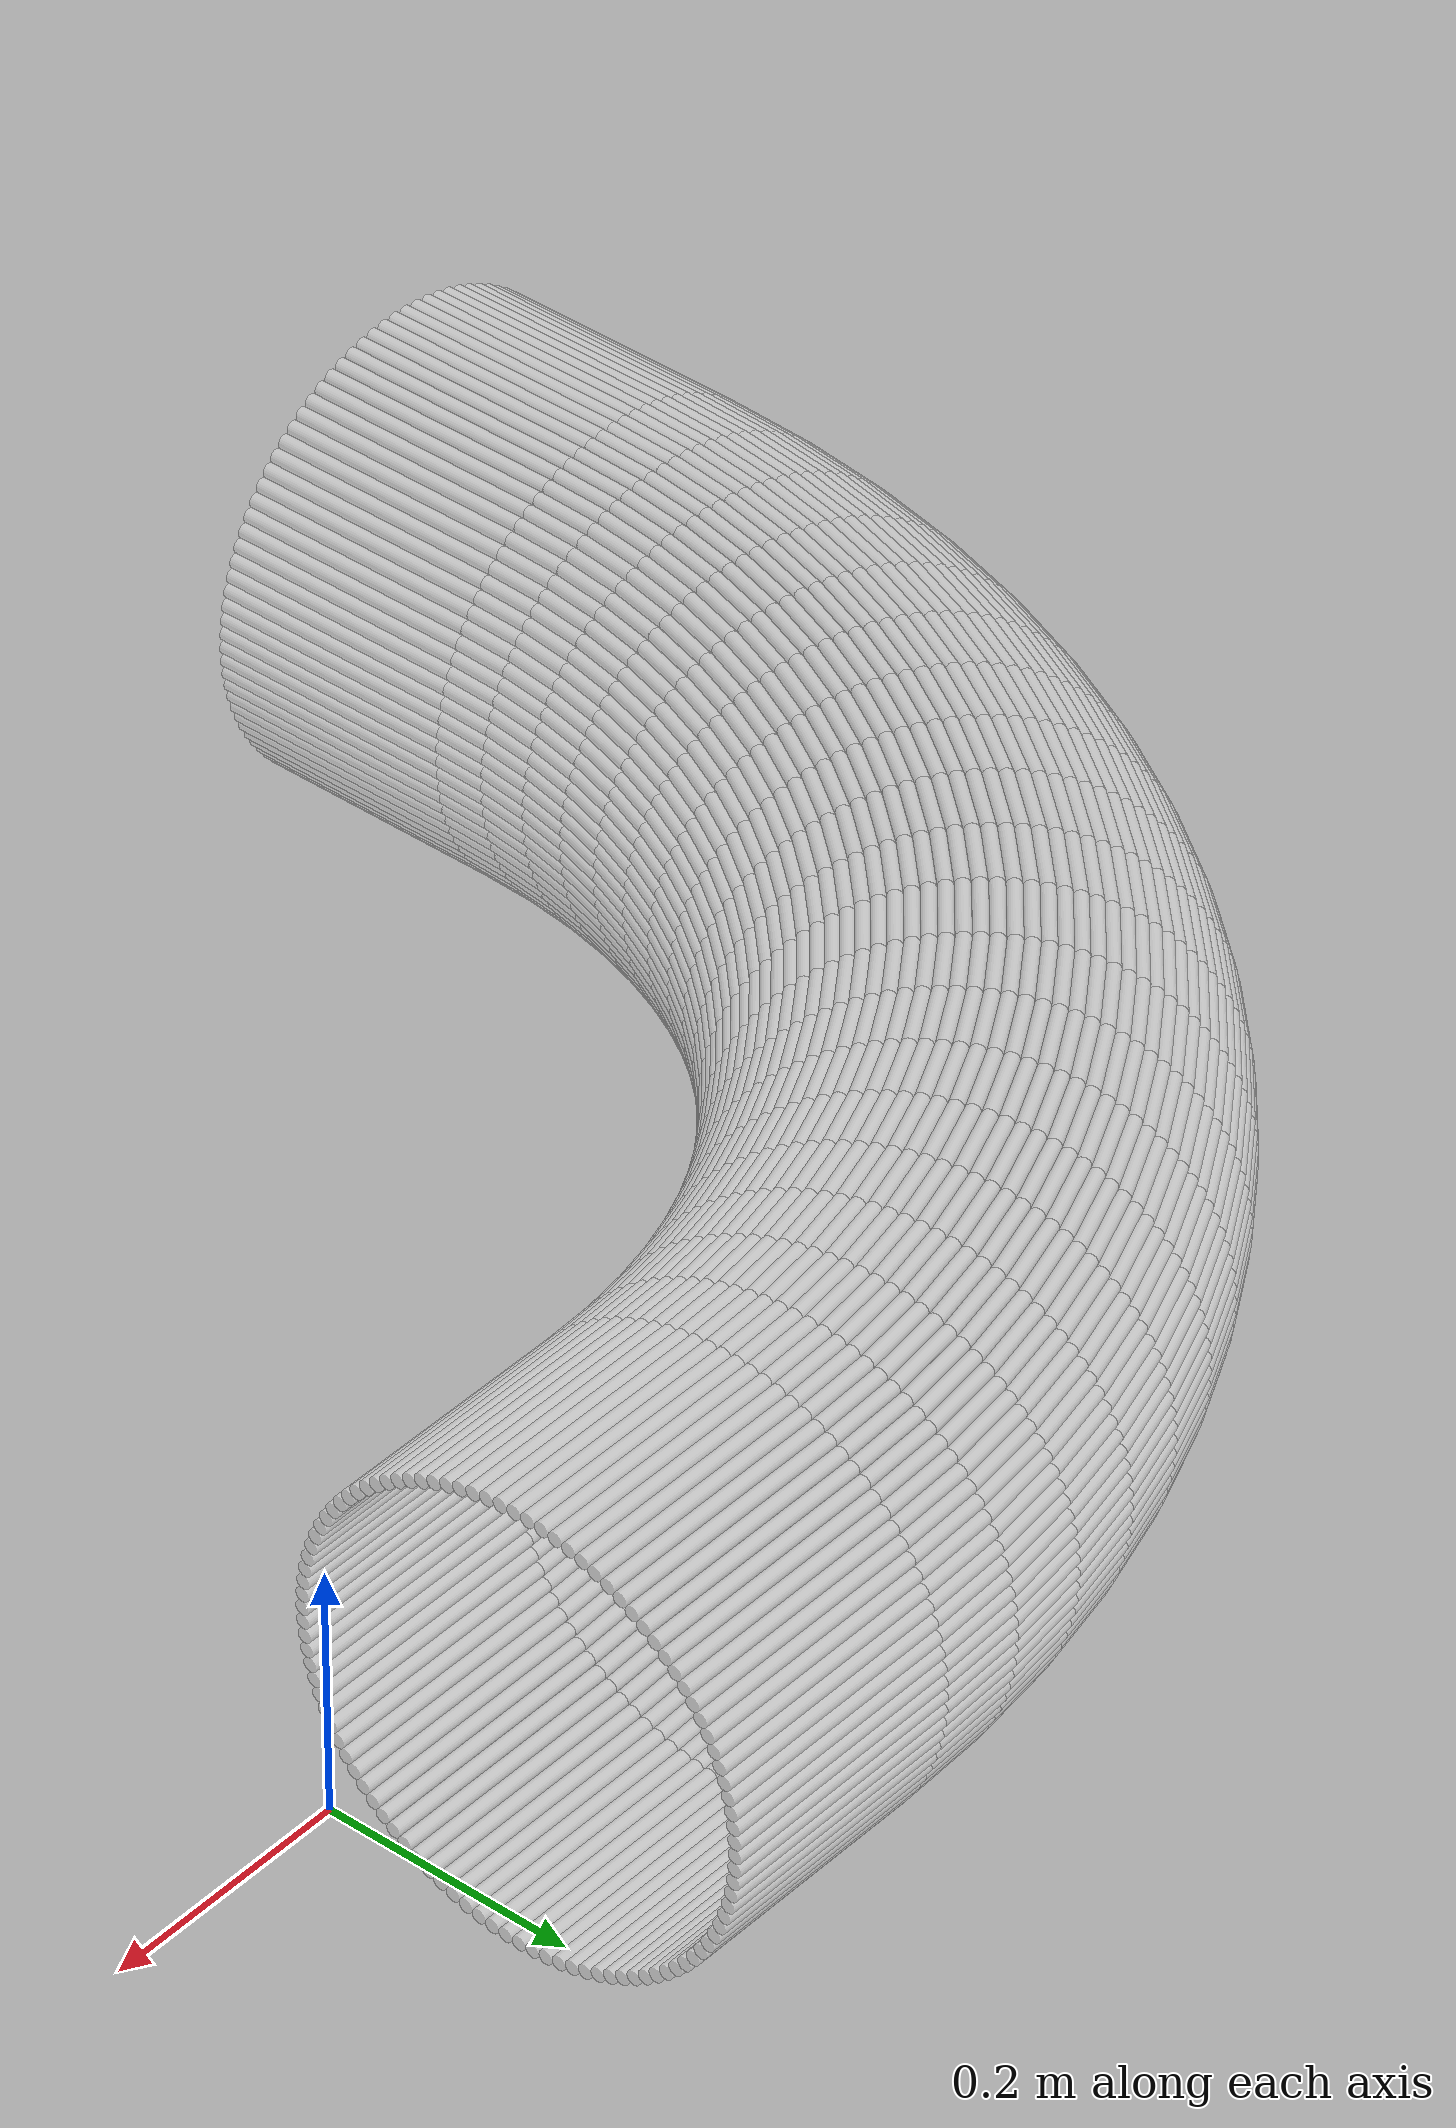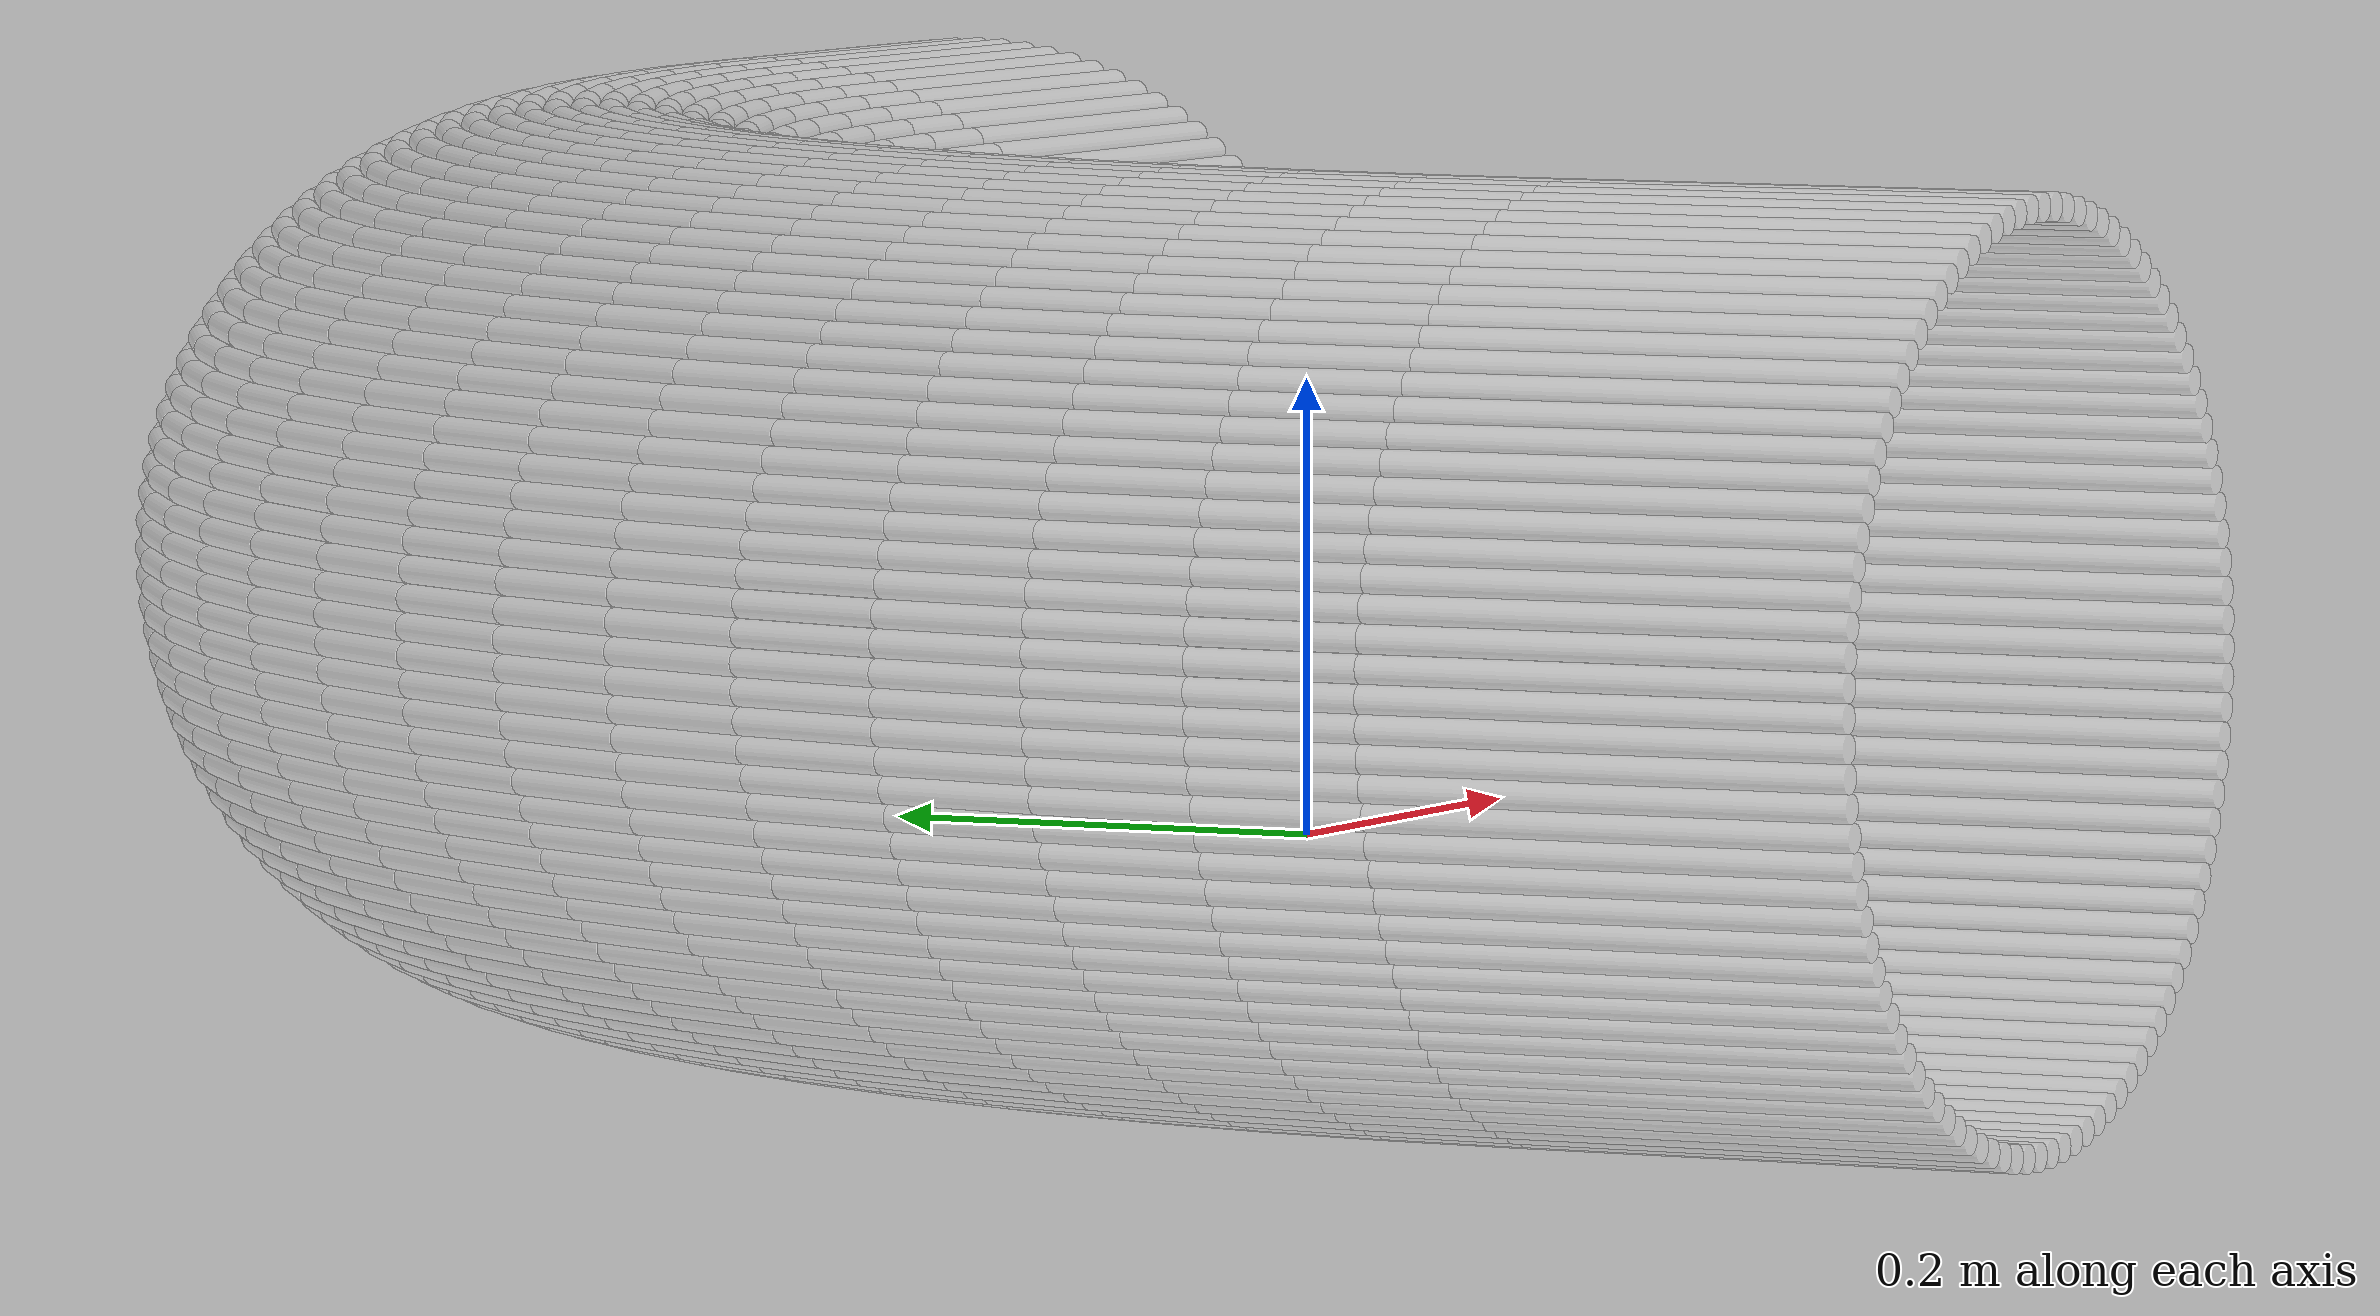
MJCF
<?xml version="1.0" encoding="utf-8"?>
<mujoco>
   <worldbody>
   <body pos="-0.2 -0.54 -0.02" euler="0 0 90">
      <geom euler=" 0 10 0 " fromto="0.88 -0.2 0.18 0.88 0 0.18" rgba="1 1 1 0.35"
            size="0.0056539"
            type="cylinder"/>
      <geom euler=" 0 20 0 " fromto="0.87964 -0.2 0.1913 0.87964 0 0.1913"
            rgba="1 1 1 0.35"
            size="0.0056539"
            type="cylinder"/>
      <geom euler=" 0 30 0 " fromto="0.87858 -0.2 0.20256 0.87858 0 0.20256"
            rgba="1 1 1 0.35"
            size="0.0056539"
            type="cylinder"/>
      <geom euler=" 0 40 0 " fromto="0.87681 -0.2 0.21373 0.87681 0 0.21373"
            rgba="1 1 1 0.35"
            size="0.0056539"
            type="cylinder"/>
      <geom euler=" 0 50 0 " fromto="0.87434 -0.2 0.22476 0.87434 0 0.22476"
            rgba="1 1 1 0.35"
            size="0.0056539"
            type="cylinder"/>
      <geom euler=" 0 60 0 " fromto="0.87119 -0.2 0.23562 0.87119 0 0.23562"
            rgba="1 1 1 0.35"
            size="0.0056539"
            type="cylinder"/>
      <geom euler=" 0 70 0 " fromto="0.86736 -0.2 0.24626 0.86736 0 0.24626"
            rgba="1 1 1 0.35"
            size="0.0056539"
            type="cylinder"/>
      <geom euler=" 0 80 0 " fromto="0.86287 -0.2 0.25664 0.86287 0 0.25664"
            rgba="1 1 1 0.35"
            size="0.0056539"
            type="cylinder"/>
      <geom euler=" 0 90 0 " fromto="0.85774 -0.2 0.26672 0.85774 0 0.26672"
            rgba="1 1 1 0.35"
            size="0.0056539"
            type="cylinder"/>
      <geom euler=" 0 100 0 " fromto="0.85198 -0.2 0.27645 0.85198 0 0.27645"
            rgba="1 1 1 0.35"
            size="0.0056539"
            type="cylinder"/>
      <geom euler=" 0 110 0 " fromto="0.84562 -0.2 0.2858 0.84562 0 0.2858"
            rgba="1 1 1 0.35"
            size="0.0056539"
            type="cylinder"/>
      <geom euler=" 0 120 0 " fromto="0.83869 -0.2 0.29474 0.83869 0 0.29474"
            rgba="1 1 1 0.35"
            size="0.0056539"
            type="cylinder"/>
      <geom euler=" 0 130 0 " fromto="0.83121 -0.2 0.30322 0.83121 0 0.30322"
            rgba="1 1 1 0.35"
            size="0.0056539"
            type="cylinder"/>
      <geom euler=" 0 140 0 " fromto="0.82322 -0.2 0.31121 0.82322 0 0.31121"
            rgba="1 1 1 0.35"
            size="0.0056539"
            type="cylinder"/>
      <geom euler=" 0 150 0 " fromto="0.81474 -0.2 0.31869 0.81474 0 0.31869"
            rgba="1 1 1 0.35"
            size="0.0056539"
            type="cylinder"/>
      <geom euler=" 0 160 0 " fromto="0.8058 -0.2 0.32562 0.8058 0 0.32562"
            rgba="1 1 1 0.35"
            size="0.0056539"
            type="cylinder"/>
      <geom euler=" 0 170 0 " fromto="0.79645 -0.2 0.33198 0.79645 0 0.33198"
            rgba="1 1 1 0.35"
            size="0.0056539"
            type="cylinder"/>
      <geom euler=" 0 180 0 " fromto="0.78672 -0.2 0.33774 0.78672 0 0.33774"
            rgba="1 1 1 0.35"
            size="0.0056539"
            type="cylinder"/>
      <geom euler=" 0 190 0 " fromto="0.77664 -0.2 0.34287 0.77664 0 0.34287"
            rgba="1 1 1 0.35"
            size="0.0056539"
            type="cylinder"/>
      <geom euler=" 0 200 0 " fromto="0.76626 -0.2 0.34736 0.76626 0 0.34736"
            rgba="1 1 1 0.35"
            size="0.0056539"
            type="cylinder"/>
      <geom euler=" 0 210 0 " fromto="0.75562 -0.2 0.35119 0.75562 0 0.35119"
            rgba="1 1 1 0.35"
            size="0.0056539"
            type="cylinder"/>
      <geom euler=" 0 220 0 " fromto="0.74476 -0.2 0.35434 0.74476 0 0.35434"
            rgba="1 1 1 0.35"
            size="0.0056539"
            type="cylinder"/>
      <geom euler=" 0 230 0 " fromto="0.73373 -0.2 0.35681 0.73373 0 0.35681"
            rgba="1 1 1 0.35"
            size="0.0056539"
            type="cylinder"/>
      <geom euler=" 0 240 0 " fromto="0.72256 -0.2 0.35858 0.72256 0 0.35858"
            rgba="1 1 1 0.35"
            size="0.0056539"
            type="cylinder"/>
      <geom euler=" 0 250 0 " fromto="0.7113 -0.2 0.35964 0.7113 0 0.35964"
            rgba="1 1 1 0.35"
            size="0.0056539"
            type="cylinder"/>
      <geom euler=" 0 260 0 " fromto="0.7 -0.2 0.36 0.7 0 0.36" rgba="1 1 1 0.35"
            size="0.0056539"
            type="cylinder"/>
      <geom euler=" 0 270 0 " fromto="0.6887 -0.2 0.35964 0.6887 0 0.35964"
            rgba="1 1 1 0.35"
            size="0.0056539"
            type="cylinder"/>
      <geom euler=" 0 280 0 " fromto="0.67744 -0.2 0.35858 0.67744 0 0.35858"
            rgba="1 1 1 0.35"
            size="0.0056539"
            type="cylinder"/>
      <geom euler=" 0 290 0 " fromto="0.66627 -0.2 0.35681 0.66627 0 0.35681"
            rgba="1 1 1 0.35"
            size="0.0056539"
            type="cylinder"/>
      <geom euler=" 0 300 0 " fromto="0.65524 -0.2 0.35434 0.65524 0 0.35434"
            rgba="1 1 1 0.35"
            size="0.0056539"
            type="cylinder"/>
      <geom euler=" 0 310 0 " fromto="0.64438 -0.2 0.35119 0.64438 0 0.35119"
            rgba="1 1 1 0.35"
            size="0.0056539"
            type="cylinder"/>
      <geom euler=" 0 320 0 " fromto="0.63374 -0.2 0.34736 0.63374 0 0.34736"
            rgba="1 1 1 0.35"
            size="0.0056539"
            type="cylinder"/>
      <geom euler=" 0 330 0 " fromto="0.62336 -0.2 0.34287 0.62336 0 0.34287"
            rgba="1 1 1 0.35"
            size="0.0056539"
            type="cylinder"/>
      <geom euler=" 0 340 0 " fromto="0.61328 -0.2 0.33774 0.61328 0 0.33774"
            rgba="1 1 1 0.35"
            size="0.0056539"
            type="cylinder"/>
      <geom euler=" 0 350 0 " fromto="0.60355 -0.2 0.33198 0.60355 0 0.33198"
            rgba="1 1 1 0.35"
            size="0.0056539"
            type="cylinder"/>
      <geom euler=" 0 360 0 " fromto="0.5942 -0.2 0.32562 0.5942 0 0.32562"
            rgba="1 1 1 0.35"
            size="0.0056539"
            type="cylinder"/>
      <geom euler=" 0 370 0 " fromto="0.58526 -0.2 0.31869 0.58526 0 0.31869"
            rgba="1 1 1 0.35"
            size="0.0056539"
            type="cylinder"/>
      <geom euler=" 0 380 0 " fromto="0.57678 -0.2 0.31121 0.57678 0 0.31121"
            rgba="1 1 1 0.35"
            size="0.0056539"
            type="cylinder"/>
      <geom euler=" 0 390 0 " fromto="0.56879 -0.2 0.30322 0.56879 0 0.30322"
            rgba="1 1 1 0.35"
            size="0.0056539"
            type="cylinder"/>
      <geom euler=" 0 400 0 " fromto="0.56131 -0.2 0.29474 0.56131 0 0.29474"
            rgba="1 1 1 0.35"
            size="0.0056539"
            type="cylinder"/>
      <geom euler=" 0 410 0 " fromto="0.55438 -0.2 0.2858 0.55438 0 0.2858"
            rgba="1 1 1 0.35"
            size="0.0056539"
            type="cylinder"/>
      <geom euler=" 0 420 0 " fromto="0.54802 -0.2 0.27645 0.54802 0 0.27645"
            rgba="1 1 1 0.35"
            size="0.0056539"
            type="cylinder"/>
      <geom euler=" 0 430 0 " fromto="0.54226 -0.2 0.26672 0.54226 0 0.26672"
            rgba="1 1 1 0.35"
            size="0.0056539"
            type="cylinder"/>
      <geom euler=" 0 440 0 " fromto="0.53713 -0.2 0.25664 0.53713 0 0.25664"
            rgba="1 1 1 0.35"
            size="0.0056539"
            type="cylinder"/>
      <geom euler=" 0 450 0 " fromto="0.53264 -0.2 0.24626 0.53264 0 0.24626"
            rgba="1 1 1 0.35"
            size="0.0056539"
            type="cylinder"/>
      <geom euler=" 0 460 0 " fromto="0.52881 -0.2 0.23562 0.52881 0 0.23562"
            rgba="1 1 1 0.35"
            size="0.0056539"
            type="cylinder"/>
      <geom euler=" 0 470 0 " fromto="0.52566 -0.2 0.22476 0.52566 0 0.22476"
            rgba="1 1 1 0.35"
            size="0.0056539"
            type="cylinder"/>
      <geom euler=" 0 480 0 " fromto="0.52319 -0.2 0.21373 0.52319 0 0.21373"
            rgba="1 1 1 0.35"
            size="0.0056539"
            type="cylinder"/>
      <geom euler=" 0 490 0 " fromto="0.52142 -0.2 0.20256 0.52142 0 0.20256"
            rgba="1 1 1 0.35"
            size="0.0056539"
            type="cylinder"/>
      <geom euler=" 0 500 0 " fromto="0.52036 -0.2 0.1913 0.52036 0 0.1913"
            rgba="1 1 1 0.35"
            size="0.0056539"
            type="cylinder"/>
      <geom euler=" 0 510 0 " fromto="0.52 -0.2 0.18 0.52 0 0.18" rgba="1 1 1 0.35"
            size="0.0056539"
            type="cylinder"/>
      <geom euler=" 0 520 0 " fromto="0.52036 -0.2 0.1687 0.52036 0 0.1687"
            rgba="1 1 1 0.35"
            size="0.0056539"
            type="cylinder"/>
      <geom euler=" 0 530 0 " fromto="0.52142 -0.2 0.15744 0.52142 0 0.15744"
            rgba="1 1 1 0.35"
            size="0.0056539"
            type="cylinder"/>
      <geom euler=" 0 540 0 " fromto="0.52319 -0.2 0.14627 0.52319 0 0.14627"
            rgba="1 1 1 0.35"
            size="0.0056539"
            type="cylinder"/>
      <geom euler=" 0 550 0 " fromto="0.52566 -0.2 0.13524 0.52566 0 0.13524"
            rgba="1 1 1 0.35"
            size="0.0056539"
            type="cylinder"/>
      <geom euler=" 0 560 0 " fromto="0.52881 -0.2 0.12438 0.52881 0 0.12438"
            rgba="1 1 1 0.35"
            size="0.0056539"
            type="cylinder"/>
      <geom euler=" 0 570 0 " fromto="0.53264 -0.2 0.11374 0.53264 0 0.11374"
            rgba="1 1 1 0.35"
            size="0.0056539"
            type="cylinder"/>
      <geom euler=" 0 580 0 " fromto="0.53713 -0.2 0.10336 0.53713 0 0.10336"
            rgba="1 1 1 0.35"
            size="0.0056539"
            type="cylinder"/>
      <geom euler=" 0 590 0 " fromto="0.54226 -0.2 0.093284 0.54226 0 0.093284"
            rgba="1 1 1 0.35"
            size="0.0056539"
            type="cylinder"/>
      <geom euler=" 0 600 0 " fromto="0.54802 -0.2 0.083551 0.54802 0 0.083551"
            rgba="1 1 1 0.35"
            size="0.0056539"
            type="cylinder"/>
      <geom euler=" 0 610 0 " fromto="0.55438 -0.2 0.074199 0.55438 0 0.074199"
            rgba="1 1 1 0.35"
            size="0.0056539"
            type="cylinder"/>
      <geom euler=" 0 620 0 " fromto="0.56131 -0.2 0.065264 0.56131 0 0.065264"
            rgba="1 1 1 0.35"
            size="0.0056539"
            type="cylinder"/>
      <geom euler=" 0 630 0 " fromto="0.56879 -0.2 0.056782 0.56879 0 0.056782"
            rgba="1 1 1 0.35"
            size="0.0056539"
            type="cylinder"/>
      <geom euler=" 0 640 0 " fromto="0.57678 -0.2 0.048786 0.57678 0 0.048786"
            rgba="1 1 1 0.35"
            size="0.0056539"
            type="cylinder"/>
      <geom euler=" 0 650 0 " fromto="0.58526 -0.2 0.041308 0.58526 0 0.041308"
            rgba="1 1 1 0.35"
            size="0.0056539"
            type="cylinder"/>
      <geom euler=" 0 660 0 " fromto="0.5942 -0.2 0.034377 0.5942 0 0.034377"
            rgba="1 1 1 0.35"
            size="0.0056539"
            type="cylinder"/>
      <geom euler=" 0 670 0 " fromto="0.60355 -0.2 0.028021 0.60355 0 0.028021"
            rgba="1 1 1 0.35"
            size="0.0056539"
            type="cylinder"/>
      <geom euler=" 0 680 0 " fromto="0.61328 -0.2 0.022265 0.61328 0 0.022265"
            rgba="1 1 1 0.35"
            size="0.0056539"
            type="cylinder"/>
      <geom euler=" 0 690 0 " fromto="0.62336 -0.2 0.017131 0.62336 0 0.017131"
            rgba="1 1 1 0.35"
            size="0.0056539"
            type="cylinder"/>
      <geom euler=" 0 700 0 " fromto="0.63374 -0.2 0.01264 0.63374 0 0.01264"
            rgba="1 1 1 0.35"
            size="0.0056539"
            type="cylinder"/>
      <geom euler=" 0 710 0 " fromto="0.64438 -0.2 0.0088098 0.64438 0 0.0088098"
            rgba="1 1 1 0.35"
            size="0.0056539"
            type="cylinder"/>
      <geom euler=" 0 720 0 " fromto="0.65524 -0.2 0.005655 0.65524 0 0.005655"
            rgba="1 1 1 0.35"
            size="0.0056539"
            type="cylinder"/>
      <geom euler=" 0 730 0 " fromto="0.66627 -0.2 0.0031883 0.66627 0 0.0031883"
            rgba="1 1 1 0.35"
            size="0.0056539"
            type="cylinder"/>
      <geom euler=" 0 740 0 " fromto="0.67744 -0.2 0.0014194 0.67744 0 0.0014194"
            rgba="1 1 1 0.35"
            size="0.0056539"
            type="cylinder"/>
      <geom euler=" 0 750 0 " fromto="0.6887 -0.2 0.00035519 0.6887 0 0.00035519"
            rgba="1 1 1 0.35"
            size="0.0056539"
            type="cylinder"/>
      <geom euler=" 0 760 0 " fromto="0.7 -0.2 0 0.7 0 0" rgba="1 1 1 0.35"
            size="0.0056539"
            type="cylinder"/>
      <geom euler=" 0 770 0 " fromto="0.7113 -0.2 0.00035519 0.7113 0 0.00035519"
            rgba="1 1 1 0.35"
            size="0.0056539"
            type="cylinder"/>
      <geom euler=" 0 780 0 " fromto="0.72256 -0.2 0.0014194 0.72256 0 0.0014194"
            rgba="1 1 1 0.35"
            size="0.0056539"
            type="cylinder"/>
      <geom euler=" 0 790 0 " fromto="0.73373 -0.2 0.0031883 0.73373 0 0.0031883"
            rgba="1 1 1 0.35"
            size="0.0056539"
            type="cylinder"/>
      <geom euler=" 0 800 0 " fromto="0.74476 -0.2 0.005655 0.74476 0 0.005655"
            rgba="1 1 1 0.35"
            size="0.0056539"
            type="cylinder"/>
      <geom euler=" 0 810 0 " fromto="0.75562 -0.2 0.0088098 0.75562 0 0.0088098"
            rgba="1 1 1 0.35"
            size="0.0056539"
            type="cylinder"/>
      <geom euler=" 0 820 0 " fromto="0.76626 -0.2 0.01264 0.76626 0 0.01264"
            rgba="1 1 1 0.35"
            size="0.0056539"
            type="cylinder"/>
      <geom euler=" 0 830 0 " fromto="0.77664 -0.2 0.017131 0.77664 0 0.017131"
            rgba="1 1 1 0.35"
            size="0.0056539"
            type="cylinder"/>
      <geom euler=" 0 840 0 " fromto="0.78672 -0.2 0.022265 0.78672 0 0.022265"
            rgba="1 1 1 0.35"
            size="0.0056539"
            type="cylinder"/>
      <geom euler=" 0 850 0 " fromto="0.79645 -0.2 0.028021 0.79645 0 0.028021"
            rgba="1 1 1 0.35"
            size="0.0056539"
            type="cylinder"/>
      <geom euler=" 0 860 0 " fromto="0.8058 -0.2 0.034377 0.8058 0 0.034377"
            rgba="1 1 1 0.35"
            size="0.0056539"
            type="cylinder"/>
      <geom euler=" 0 870 0 " fromto="0.81474 -0.2 0.041308 0.81474 0 0.041308"
            rgba="1 1 1 0.35"
            size="0.0056539"
            type="cylinder"/>
      <geom euler=" 0 880 0 " fromto="0.82322 -0.2 0.048786 0.82322 0 0.048786"
            rgba="1 1 1 0.35"
            size="0.0056539"
            type="cylinder"/>
      <geom euler=" 0 890 0 " fromto="0.83121 -0.2 0.056782 0.83121 0 0.056782"
            rgba="1 1 1 0.35"
            size="0.0056539"
            type="cylinder"/>
      <geom euler=" 0 900 0 " fromto="0.83869 -0.2 0.065264 0.83869 0 0.065264"
            rgba="1 1 1 0.35"
            size="0.0056539"
            type="cylinder"/>
      <geom euler=" 0 910 0 " fromto="0.84562 -0.2 0.074199 0.84562 0 0.074199"
            rgba="1 1 1 0.35"
            size="0.0056539"
            type="cylinder"/>
      <geom euler=" 0 920 0 " fromto="0.85198 -0.2 0.083551 0.85198 0 0.083551"
            rgba="1 1 1 0.35"
            size="0.0056539"
            type="cylinder"/>
      <geom euler=" 0 930 0 " fromto="0.85774 -0.2 0.093284 0.85774 0 0.093284"
            rgba="1 1 1 0.35"
            size="0.0056539"
            type="cylinder"/>
      <geom euler=" 0 940 0 " fromto="0.86287 -0.2 0.10336 0.86287 0 0.10336"
            rgba="1 1 1 0.35"
            size="0.0056539"
            type="cylinder"/>
      <geom euler=" 0 950 0 " fromto="0.86736 -0.2 0.11374 0.86736 0 0.11374"
            rgba="1 1 1 0.35"
            size="0.0056539"
            type="cylinder"/>
      <geom euler=" 0 960 0 " fromto="0.87119 -0.2 0.12438 0.87119 0 0.12438"
            rgba="1 1 1 0.35"
            size="0.0056539"
            type="cylinder"/>
      <geom euler=" 0 970 0 " fromto="0.87434 -0.2 0.13524 0.87434 0 0.13524"
            rgba="1 1 1 0.35"
            size="0.0056539"
            type="cylinder"/>
      <geom euler=" 0 980 0 " fromto="0.87681 -0.2 0.14627 0.87681 0 0.14627"
            rgba="1 1 1 0.35"
            size="0.0056539"
            type="cylinder"/>
      <geom euler=" 0 990 0 " fromto="0.87858 -0.2 0.15744 0.87858 0 0.15744"
            rgba="1 1 1 0.35"
            size="0.0056539"
            type="cylinder"/>
      <geom euler=" 0 1000 0 " fromto="0.87964 -0.2 0.1687 0.87964 0 0.1687"
            rgba="1 1 1 0.35"
            size="0.0056539"
            type="cylinder"/>
      <geom euler=" 0 10 0 " fromto="0.88 0 0.18 0.87699 0.07267 0.18" rgba="1 1 1 0.35"
            size="0.0056539"
            type="cylinder"/>
      <geom euler=" 0 20 0 " fromto="0.87964 0 0.1913 0.87664 0.07264 0.1913"
            rgba="1 1 1 0.35"
            size="0.0056539"
            type="cylinder"/>
      <geom euler=" 0 30 0 " fromto="0.87858 0 0.20256 0.87558 0.072553 0.20256"
            rgba="1 1 1 0.35"
            size="0.0056539"
            type="cylinder"/>
      <geom euler=" 0 40 0 " fromto="0.87681 0 0.21373 0.87382 0.072407 0.21373"
            rgba="1 1 1 0.35"
            size="0.0056539"
            type="cylinder"/>
      <geom euler=" 0 50 0 " fromto="0.87434 0 0.22476 0.87136 0.072203 0.22476"
            rgba="1 1 1 0.35"
            size="0.0056539"
            type="cylinder"/>
      <geom euler=" 0 60 0 " fromto="0.87119 0 0.23562 0.86821 0.071942 0.23562"
            rgba="1 1 1 0.35"
            size="0.0056539"
            type="cylinder"/>
      <geom euler=" 0 70 0 " fromto="0.86736 0 0.24626 0.8644 0.071626 0.24626"
            rgba="1 1 1 0.35"
            size="0.0056539"
            type="cylinder"/>
      <geom euler=" 0 80 0 " fromto="0.86287 0 0.25664 0.85992 0.071255 0.25664"
            rgba="1 1 1 0.35"
            size="0.0056539"
            type="cylinder"/>
      <geom euler=" 0 90 0 " fromto="0.85774 0 0.26672 0.85481 0.070831 0.26672"
            rgba="1 1 1 0.35"
            size="0.0056539"
            type="cylinder"/>
      <geom euler=" 0 100 0 " fromto="0.85198 0 0.27645 0.84907 0.070356 0.27645"
            rgba="1 1 1 0.35"
            size="0.0056539"
            type="cylinder"/>
      <geom euler=" 0 110 0 " fromto="0.84562 0 0.2858 0.84273 0.069831 0.2858"
            rgba="1 1 1 0.35"
            size="0.0056539"
            type="cylinder"/>
      <geom euler=" 0 120 0 " fromto="0.83869 0 0.29474 0.83583 0.069259 0.29474"
            rgba="1 1 1 0.35"
            size="0.0056539"
            type="cylinder"/>
      <geom euler=" 0 130 0 " fromto="0.83121 0 0.30322 0.82838 0.068641 0.30322"
            rgba="1 1 1 0.35"
            size="0.0056539"
            type="cylinder"/>
      <geom euler=" 0 140 0 " fromto="0.82322 0 0.31121 0.82041 0.067981 0.31121"
            rgba="1 1 1 0.35"
            size="0.0056539"
            type="cylinder"/>
      <geom euler=" 0 150 0 " fromto="0.81474 0 0.31869 0.81195 0.06728 0.31869"
            rgba="1 1 1 0.35"
            size="0.0056539"
            type="cylinder"/>
      <geom euler=" 0 160 0 " fromto="0.8058 0 0.32562 0.80305 0.066543 0.32562"
            rgba="1 1 1 0.35"
            size="0.0056539"
            type="cylinder"/>
      <geom euler=" 0 170 0 " fromto="0.79645 0 0.33198 0.79373 0.06577 0.33198"
            rgba="1 1 1 0.35"
            size="0.0056539"
            type="cylinder"/>
      <geom euler=" 0 180 0 " fromto="0.78672 0 0.33774 0.78403 0.064966 0.33774"
            rgba="1 1 1 0.35"
            size="0.0056539"
            type="cylinder"/>
      <geom euler=" 0 190 0 " fromto="0.77664 0 0.34287 0.77399 0.064134 0.34287"
            rgba="1 1 1 0.35"
            size="0.0056539"
            type="cylinder"/>
      <geom euler=" 0 200 0 " fromto="0.76626 0 0.34736 0.76365 0.063277 0.34736"
            rgba="1 1 1 0.35"
            size="0.0056539"
            type="cylinder"/>
      <geom euler=" 0 210 0 " fromto="0.75562 0 0.35119 0.75304 0.062399 0.35119"
            rgba="1 1 1 0.35"
            size="0.0056539"
            type="cylinder"/>
      <geom euler=" 0 220 0 " fromto="0.74476 0 0.35434 0.74222 0.061502 0.35434"
            rgba="1 1 1 0.35"
            size="0.0056539"
            type="cylinder"/>
      <geom euler=" 0 230 0 " fromto="0.73373 0 0.35681 0.73122 0.060591 0.35681"
            rgba="1 1 1 0.35"
            size="0.0056539"
            type="cylinder"/>
      <geom euler=" 0 240 0 " fromto="0.72256 0 0.35858 0.72009 0.059669 0.35858"
            rgba="1 1 1 0.35"
            size="0.0056539"
            type="cylinder"/>
      <geom euler=" 0 250 0 " fromto="0.7113 0 0.35964 0.70887 0.058739 0.35964"
            rgba="1 1 1 0.35"
            size="0.0056539"
            type="cylinder"/>
      <geom euler=" 0 260 0 " fromto="0.7 0 0.36 0.69761 0.057806 0.36" rgba="1 1 1 0.35"
            size="0.0056539"
            type="cylinder"/>
      <geom euler=" 0 270 0 " fromto="0.6887 0 0.35964 0.68635 0.056872 0.35964"
            rgba="1 1 1 0.35"
            size="0.0056539"
            type="cylinder"/>
      <geom euler=" 0 280 0 " fromto="0.67744 0 0.35858 0.67513 0.055943 0.35858"
            rgba="1 1 1 0.35"
            size="0.0056539"
            type="cylinder"/>
      <geom euler=" 0 290 0 " fromto="0.66627 0 0.35681 0.664 0.05502 0.35681"
            rgba="1 1 1 0.35"
            size="0.0056539"
            type="cylinder"/>
      <geom euler=" 0 300 0 " fromto="0.65524 0 0.35434 0.653 0.054109 0.35434"
            rgba="1 1 1 0.35"
            size="0.0056539"
            type="cylinder"/>
      <geom euler=" 0 310 0 " fromto="0.64438 0 0.35119 0.64218 0.053212 0.35119"
            rgba="1 1 1 0.35"
            size="0.0056539"
            type="cylinder"/>
      <geom euler=" 0 320 0 " fromto="0.63374 0 0.34736 0.63157 0.052334 0.34736"
            rgba="1 1 1 0.35"
            size="0.0056539"
            type="cylinder"/>
      <geom euler=" 0 330 0 " fromto="0.62336 0 0.34287 0.62123 0.051477 0.34287"
            rgba="1 1 1 0.35"
            size="0.0056539"
            type="cylinder"/>
      <geom euler=" 0 340 0 " fromto="0.61328 0 0.33774 0.61119 0.050645 0.33774"
            rgba="1 1 1 0.35"
            size="0.0056539"
            type="cylinder"/>
      <geom euler=" 0 350 0 " fromto="0.60355 0 0.33198 0.60149 0.049841 0.33198"
            rgba="1 1 1 0.35"
            size="0.0056539"
            type="cylinder"/>
      <geom euler=" 0 360 0 " fromto="0.5942 0 0.32562 0.59217 0.049069 0.32562"
            rgba="1 1 1 0.35"
            size="0.0056539"
            type="cylinder"/>
      <geom euler=" 0 370 0 " fromto="0.58526 0 0.31869 0.58326 0.048331 0.31869"
            rgba="1 1 1 0.35"
            size="0.0056539"
            type="cylinder"/>
      <geom euler=" 0 380 0 " fromto="0.57678 0 0.31121 0.57481 0.04763 0.31121"
            rgba="1 1 1 0.35"
            size="0.0056539"
            type="cylinder"/>
      <geom euler=" 0 390 0 " fromto="0.56879 0 0.30322 0.56684 0.04697 0.30322"
            rgba="1 1 1 0.35"
            size="0.0056539"
            type="cylinder"/>
      <geom euler=" 0 400 0 " fromto="0.56131 0 0.29474 0.55939 0.046352 0.29474"
            rgba="1 1 1 0.35"
            size="0.0056539"
            type="cylinder"/>
      <geom euler=" 0 410 0 " fromto="0.55438 0 0.2858 0.55248 0.04578 0.2858"
            rgba="1 1 1 0.35"
            size="0.0056539"
            type="cylinder"/>
      <geom euler=" 0 420 0 " fromto="0.54802 0 0.27645 0.54615 0.045255 0.27645"
            rgba="1 1 1 0.35"
            size="0.0056539"
            type="cylinder"/>
      <geom euler=" 0 430 0 " fromto="0.54226 0 0.26672 0.54041 0.04478 0.26672"
            rgba="1 1 1 0.35"
            size="0.0056539"
            type="cylinder"/>
      <geom euler=" 0 440 0 " fromto="0.53713 0 0.25664 0.5353 0.044356 0.25664"
            rgba="1 1 1 0.35"
            size="0.0056539"
            type="cylinder"/>
      <geom euler=" 0 450 0 " fromto="0.53264 0 0.24626 0.53082 0.043985 0.24626"
            rgba="1 1 1 0.35"
            size="0.0056539"
            type="cylinder"/>
      <geom euler=" 0 460 0 " fromto="0.52881 0 0.23562 0.527 0.043669 0.23562"
            rgba="1 1 1 0.35"
            size="0.0056539"
            type="cylinder"/>
      <geom euler=" 0 470 0 " fromto="0.52566 0 0.22476 0.52386 0.043408 0.22476"
            rgba="1 1 1 0.35"
            size="0.0056539"
            type="cylinder"/>
      <geom euler=" 0 480 0 " fromto="0.52319 0 0.21373 0.5214 0.043205 0.21373"
            rgba="1 1 1 0.35"
            size="0.0056539"
            type="cylinder"/>
      <geom euler=" 0 490 0 " fromto="0.52142 0 0.20256 0.51964 0.043058 0.20256"
            rgba="1 1 1 0.35"
            size="0.0056539"
            type="cylinder"/>
      <geom euler=" 0 500 0 " fromto="0.52036 0 0.1913 0.51858 0.042971 0.1913"
            rgba="1 1 1 0.35"
            size="0.0056539"
            type="cylinder"/>
      <geom euler=" 0 510 0 " fromto="0.52 0 0.18 0.51822 0.042941 0.18" rgba="1 1 1 0.35"
            size="0.0056539"
            type="cylinder"/>
      <geom euler=" 0 520 0 " fromto="0.52036 0 0.1687 0.51858 0.042971 0.1687"
            rgba="1 1 1 0.35"
            size="0.0056539"
            type="cylinder"/>
      <geom euler=" 0 530 0 " fromto="0.52142 0 0.15744 0.51964 0.043058 0.15744"
            rgba="1 1 1 0.35"
            size="0.0056539"
            type="cylinder"/>
      <geom euler=" 0 540 0 " fromto="0.52319 0 0.14627 0.5214 0.043205 0.14627"
            rgba="1 1 1 0.35"
            size="0.0056539"
            type="cylinder"/>
      <geom euler=" 0 550 0 " fromto="0.52566 0 0.13524 0.52386 0.043408 0.13524"
            rgba="1 1 1 0.35"
            size="0.0056539"
            type="cylinder"/>
      <geom euler=" 0 560 0 " fromto="0.52881 0 0.12438 0.527 0.043669 0.12438"
            rgba="1 1 1 0.35"
            size="0.0056539"
            type="cylinder"/>
      <geom euler=" 0 570 0 " fromto="0.53264 0 0.11374 0.53082 0.043985 0.11374"
            rgba="1 1 1 0.35"
            size="0.0056539"
            type="cylinder"/>
      <geom euler=" 0 580 0 " fromto="0.53713 0 0.10336 0.5353 0.044356 0.10336"
            rgba="1 1 1 0.35"
            size="0.0056539"
            type="cylinder"/>
      <geom euler=" 0 590 0 " fromto="0.54226 0 0.093284 0.54041 0.04478 0.093284"
            rgba="1 1 1 0.35"
            size="0.0056539"
            type="cylinder"/>
      <geom euler=" 0 600 0 " fromto="0.54802 0 0.083551 0.54615 0.045255 0.083551"
            rgba="1 1 1 0.35"
            size="0.0056539"
            type="cylinder"/>
      <geom euler=" 0 610 0 " fromto="0.55438 0 0.074199 0.55248 0.04578 0.074199"
            rgba="1 1 1 0.35"
            size="0.0056539"
            type="cylinder"/>
      <geom euler=" 0 620 0 " fromto="0.56131 0 0.065264 0.55939 0.046352 0.065264"
            rgba="1 1 1 0.35"
            size="0.0056539"
            type="cylinder"/>
      <geom euler=" 0 630 0 " fromto="0.56879 0 0.056782 0.56684 0.04697 0.056782"
            rgba="1 1 1 0.35"
            size="0.0056539"
            type="cylinder"/>
      <geom euler=" 0 640 0 " fromto="0.57678 0 0.048786 0.57481 0.04763 0.048786"
            rgba="1 1 1 0.35"
            size="0.0056539"
            type="cylinder"/>
      <geom euler=" 0 650 0 " fromto="0.58526 0 0.041308 0.58326 0.048331 0.041308"
            rgba="1 1 1 0.35"
            size="0.0056539"
            type="cylinder"/>
      <geom euler=" 0 660 0 " fromto="0.5942 0 0.034377 0.59217 0.049069 0.034377"
            rgba="1 1 1 0.35"
            size="0.0056539"
            type="cylinder"/>
      <geom euler=" 0 670 0 " fromto="0.60355 0 0.028021 0.60149 0.049841 0.028021"
            rgba="1 1 1 0.35"
            size="0.0056539"
            type="cylinder"/>
      <geom euler=" 0 680 0 " fromto="0.61328 0 0.022265 0.61119 0.050645 0.022265"
            rgba="1 1 1 0.35"
            size="0.0056539"
            type="cylinder"/>
      <geom euler=" 0 690 0 " fromto="0.62336 0 0.017131 0.62123 0.051477 0.017131"
            rgba="1 1 1 0.35"
            size="0.0056539"
            type="cylinder"/>
      <geom euler=" 0 700 0 " fromto="0.63374 0 0.01264 0.63157 0.052334 0.01264"
            rgba="1 1 1 0.35"
            size="0.0056539"
            type="cylinder"/>
      <geom euler=" 0 710 0 " fromto="0.64438 0 0.0088098 0.64218 0.053212 0.0088098"
            rgba="1 1 1 0.35"
            size="0.0056539"
            type="cylinder"/>
      <geom euler=" 0 720 0 " fromto="0.65524 0 0.005655 0.653 0.054109 0.005655"
            rgba="1 1 1 0.35"
            size="0.0056539"
            type="cylinder"/>
      <geom euler=" 0 730 0 " fromto="0.66627 0 0.0031883 0.664 0.05502 0.0031883"
            rgba="1 1 1 0.35"
            size="0.0056539"
            type="cylinder"/>
      <geom euler=" 0 740 0 " fromto="0.67744 0 0.0014194 0.67513 0.055943 0.0014194"
            rgba="1 1 1 0.35"
            size="0.0056539"
            type="cylinder"/>
      <geom euler=" 0 750 0 " fromto="0.6887 0 0.00035519 0.68635 0.056872 0.00035519"
            rgba="1 1 1 0.35"
            size="0.0056539"
            type="cylinder"/>
      <geom euler=" 0 760 0 " fromto="0.7 0 0 0.69761 0.057806 0" rgba="1 1 1 0.35"
            size="0.0056539"
            type="cylinder"/>
      <geom euler=" 0 770 0 " fromto="0.7113 0 0.00035519 0.70887 0.058739 0.00035519"
            rgba="1 1 1 0.35"
            size="0.0056539"
            type="cylinder"/>
      <geom euler=" 0 780 0 " fromto="0.72256 0 0.0014194 0.72009 0.059669 0.0014194"
            rgba="1 1 1 0.35"
            size="0.0056539"
            type="cylinder"/>
      <geom euler=" 0 790 0 " fromto="0.73373 0 0.0031883 0.73122 0.060591 0.0031883"
            rgba="1 1 1 0.35"
            size="0.0056539"
            type="cylinder"/>
      <geom euler=" 0 800 0 " fromto="0.74476 0 0.005655 0.74222 0.061502 0.005655"
            rgba="1 1 1 0.35"
            size="0.0056539"
            type="cylinder"/>
      <geom euler=" 0 810 0 " fromto="0.75562 0 0.0088098 0.75304 0.062399 0.0088098"
            rgba="1 1 1 0.35"
            size="0.0056539"
            type="cylinder"/>
      <geom euler=" 0 820 0 " fromto="0.76626 0 0.01264 0.76365 0.063277 0.01264"
            rgba="1 1 1 0.35"
            size="0.0056539"
            type="cylinder"/>
      <geom euler=" 0 830 0 " fromto="0.77664 0 0.017131 0.77399 0.064134 0.017131"
            rgba="1 1 1 0.35"
            size="0.0056539"
            type="cylinder"/>
      <geom euler=" 0 840 0 " fromto="0.78672 0 0.022265 0.78403 0.064966 0.022265"
            rgba="1 1 1 0.35"
            size="0.0056539"
            type="cylinder"/>
      <geom euler=" 0 850 0 " fromto="0.79645 0 0.028021 0.79373 0.06577 0.028021"
            rgba="1 1 1 0.35"
            size="0.0056539"
            type="cylinder"/>
      <geom euler=" 0 860 0 " fromto="0.8058 0 0.034377 0.80305 0.066543 0.034377"
            rgba="1 1 1 0.35"
            size="0.0056539"
            type="cylinder"/>
      <geom euler=" 0 870 0 " fromto="0.81474 0 0.041308 0.81195 0.06728 0.041308"
            rgba="1 1 1 0.35"
            size="0.0056539"
            type="cylinder"/>
      <geom euler=" 0 880 0 " fromto="0.82322 0 0.048786 0.82041 0.067981 0.048786"
            rgba="1 1 1 0.35"
            size="0.0056539"
            type="cylinder"/>
      <geom euler=" 0 890 0 " fromto="0.83121 0 0.056782 0.82838 0.068641 0.056782"
            rgba="1 1 1 0.35"
            size="0.0056539"
            type="cylinder"/>
      <geom euler=" 0 900 0 " fromto="0.83869 0 0.065264 0.83583 0.069259 0.065264"
            rgba="1 1 1 0.35"
            size="0.0056539"
            type="cylinder"/>
      <geom euler=" 0 910 0 " fromto="0.84562 0 0.074199 0.84273 0.069831 0.074199"
            rgba="1 1 1 0.35"
            size="0.0056539"
            type="cylinder"/>
      <geom euler=" 0 920 0 " fromto="0.85198 0 0.083551 0.84907 0.070356 0.083551"
            rgba="1 1 1 0.35"
            size="0.0056539"
            type="cylinder"/>
      <geom euler=" 0 930 0 " fromto="0.85774 0 0.093284 0.85481 0.070831 0.093284"
            rgba="1 1 1 0.35"
            size="0.0056539"
            type="cylinder"/>
      <geom euler=" 0 940 0 " fromto="0.86287 0 0.10336 0.85992 0.071255 0.10336"
            rgba="1 1 1 0.35"
            size="0.0056539"
            type="cylinder"/>
      <geom euler=" 0 950 0 " fromto="0.86736 0 0.11374 0.8644 0.071626 0.11374"
            rgba="1 1 1 0.35"
            size="0.0056539"
            type="cylinder"/>
      <geom euler=" 0 960 0 " fromto="0.87119 0 0.12438 0.86821 0.071942 0.12438"
            rgba="1 1 1 0.35"
            size="0.0056539"
            type="cylinder"/>
      <geom euler=" 0 970 0 " fromto="0.87434 0 0.13524 0.87136 0.072203 0.13524"
            rgba="1 1 1 0.35"
            size="0.0056539"
            type="cylinder"/>
      <geom euler=" 0 980 0 " fromto="0.87681 0 0.14627 0.87382 0.072407 0.14627"
            rgba="1 1 1 0.35"
            size="0.0056539"
            type="cylinder"/>
      <geom euler=" 0 990 0 " fromto="0.87858 0 0.15744 0.87558 0.072553 0.15744"
            rgba="1 1 1 0.35"
            size="0.0056539"
            type="cylinder"/>
      <geom euler=" 0 1000 0 " fromto="0.87964 0 0.1687 0.87664 0.07264 0.1687"
            rgba="1 1 1 0.35"
            size="0.0056539"
            type="cylinder"/>
      <geom euler=" 0 10 0 " fromto="0.87699 0.07267 0.18 0.868 0.14484 0.18"
            rgba="1 1 1 0.35"
            size="0.0056539"
            type="cylinder"/>
      <geom euler=" 0 20 0 " fromto="0.87664 0.07264 0.1913 0.86765 0.14478 0.1913"
            rgba="1 1 1 0.35"
            size="0.0056539"
            type="cylinder"/>
      <geom euler=" 0 30 0 " fromto="0.87558 0.072553 0.20256 0.8666 0.14461 0.20256"
            rgba="1 1 1 0.35"
            size="0.0056539"
            type="cylinder"/>
      <geom euler=" 0 40 0 " fromto="0.87382 0.072407 0.21373 0.86485 0.14432 0.21373"
            rgba="1 1 1 0.35"
            size="0.0056539"
            type="cylinder"/>
      <geom euler=" 0 50 0 " fromto="0.87136 0.072203 0.22476 0.86242 0.14391 0.22476"
            rgba="1 1 1 0.35"
            size="0.0056539"
            type="cylinder"/>
      <geom euler=" 0 60 0 " fromto="0.86821 0.071942 0.23562 0.85931 0.14339 0.23562"
            rgba="1 1 1 0.35"
            size="0.0056539"
            type="cylinder"/>
      <geom euler=" 0 70 0 " fromto="0.8644 0.071626 0.24626 0.85553 0.14276 0.24626"
            rgba="1 1 1 0.35"
            size="0.0056539"
            type="cylinder"/>
      <geom euler=" 0 80 0 " fromto="0.85992 0.071255 0.25664 0.8511 0.14202 0.25664"
            rgba="1 1 1 0.35"
            size="0.0056539"
            type="cylinder"/>
      <geom euler=" 0 90 0 " fromto="0.85481 0.070831 0.26672 0.84604 0.14118 0.26672"
            rgba="1 1 1 0.35"
            size="0.0056539"
            type="cylinder"/>
      <geom euler=" 0 100 0 " fromto="0.84907 0.070356 0.27645 0.84036 0.14023 0.27645"
            rgba="1 1 1 0.35"
            size="0.0056539"
            type="cylinder"/>
      <geom euler=" 0 110 0 " fromto="0.84273 0.069831 0.2858 0.83409 0.13918 0.2858"
            rgba="1 1 1 0.35"
            size="0.0056539"
            type="cylinder"/>
      <geom euler=" 0 120 0 " fromto="0.83583 0.069259 0.29474 0.82725 0.13804 0.29474"
            rgba="1 1 1 0.35"
            size="0.0056539"
            type="cylinder"/>
      <geom euler=" 0 130 0 " fromto="0.82838 0.068641 0.30322 0.81988 0.13681 0.30322"
            rgba="1 1 1 0.35"
            size="0.0056539"
            type="cylinder"/>
      <geom euler=" 0 140 0 " fromto="0.82041 0.067981 0.31121 0.81199 0.1355 0.31121"
            rgba="1 1 1 0.35"
            size="0.0056539"
            type="cylinder"/>
      <geom euler=" 0 150 0 " fromto="0.81195 0.06728 0.31869 0.80362 0.1341 0.31869"
            rgba="1 1 1 0.35"
            size="0.0056539"
            type="cylinder"/>
      <geom euler=" 0 160 0 " fromto="0.80305 0.066543 0.32562 0.79481 0.13263 0.32562"
            rgba="1 1 1 0.35"
            size="0.0056539"
            type="cylinder"/>
      <geom euler=" 0 170 0 " fromto="0.79373 0.06577 0.33198 0.78559 0.13109 0.33198"
            rgba="1 1 1 0.35"
            size="0.0056539"
            type="cylinder"/>
      <geom euler=" 0 180 0 " fromto="0.78403 0.064966 0.33774 0.77599 0.12949 0.33774"
            rgba="1 1 1 0.35"
            size="0.0056539"
            type="cylinder"/>
      <geom euler=" 0 190 0 " fromto="0.77399 0.064134 0.34287 0.76605 0.12783 0.34287"
            rgba="1 1 1 0.35"
            size="0.0056539"
            type="cylinder"/>
      <geom euler=" 0 200 0 " fromto="0.76365 0.063277 0.34736 0.75581 0.12612 0.34736"
            rgba="1 1 1 0.35"
            size="0.0056539"
            type="cylinder"/>
      <geom euler=" 0 210 0 " fromto="0.75304 0.062399 0.35119 0.74532 0.12437 0.35119"
            rgba="1 1 1 0.35"
            size="0.0056539"
            type="cylinder"/>
      <geom euler=" 0 220 0 " fromto="0.74222 0.061502 0.35434 0.73461 0.12258 0.35434"
            rgba="1 1 1 0.35"
            size="0.0056539"
            type="cylinder"/>
      <geom euler=" 0 230 0 " fromto="0.73122 0.060591 0.35681 0.72372 0.12077 0.35681"
            rgba="1 1 1 0.35"
            size="0.0056539"
            type="cylinder"/>
      <geom euler=" 0 240 0 " fromto="0.72009 0.059669 0.35858 0.71271 0.11893 0.35858"
            rgba="1 1 1 0.35"
            size="0.0056539"
            type="cylinder"/>
      <geom euler=" 0 250 0 " fromto="0.70887 0.058739 0.35964 0.7016 0.11708 0.35964"
            rgba="1 1 1 0.35"
            size="0.0056539"
            type="cylinder"/>
      <geom euler=" 0 260 0 " fromto="0.69761 0.057806 0.36 0.69045 0.11522 0.36"
            rgba="1 1 1 0.35"
            size="0.0056539"
            type="cylinder"/>
      <geom euler=" 0 270 0 " fromto="0.68635 0.056872 0.35964 0.6793 0.11336 0.35964"
            rgba="1 1 1 0.35"
            size="0.0056539"
            type="cylinder"/>
      <geom euler=" 0 280 0 " fromto="0.67513 0.055943 0.35858 0.6682 0.1115 0.35858"
            rgba="1 1 1 0.35"
            size="0.0056539"
            type="cylinder"/>
      <geom euler=" 0 290 0 " fromto="0.664 0.05502 0.35681 0.65718 0.10966 0.35681"
            rgba="1 1 1 0.35"
            size="0.0056539"
            type="cylinder"/>
      <geom euler=" 0 300 0 " fromto="0.653 0.054109 0.35434 0.6463 0.10785 0.35434"
            rgba="1 1 1 0.35"
            size="0.0056539"
            type="cylinder"/>
      <geom euler=" 0 310 0 " fromto="0.64218 0.053212 0.35119 0.63559 0.10606 0.35119"
            rgba="1 1 1 0.35"
            size="0.0056539"
            type="cylinder"/>
      <geom euler=" 0 320 0 " fromto="0.63157 0.052334 0.34736 0.62509 0.10431 0.34736"
            rgba="1 1 1 0.35"
            size="0.0056539"
            type="cylinder"/>
      <geom euler=" 0 330 0 " fromto="0.62123 0.051477 0.34287 0.61486 0.1026 0.34287"
            rgba="1 1 1 0.35"
            size="0.0056539"
            type="cylinder"/>
      <geom euler=" 0 340 0 " fromto="0.61119 0.050645 0.33774 0.60492 0.10094 0.33774"
            rgba="1 1 1 0.35"
            size="0.0056539"
            type="cylinder"/>
      <geom euler=" 0 350 0 " fromto="0.60149 0.049841 0.33198 0.59532 0.099341 0.33198"
            rgba="1 1 1 0.35"
            size="0.0056539"
            type="cylinder"/>
      <geom euler=" 0 360 0 " fromto="0.59217 0.049069 0.32562 0.58609 0.097802 0.32562"
            rgba="1 1 1 0.35"
            size="0.0056539"
            type="cylinder"/>
      <geom euler=" 0 370 0 " fromto="0.58326 0.048331 0.31869 0.57728 0.096331 0.31869"
            rgba="1 1 1 0.35"
            size="0.0056539"
            type="cylinder"/>
      <geom euler=" 0 380 0 " fromto="0.57481 0.04763 0.31121 0.56891 0.094935 0.31121"
            rgba="1 1 1 0.35"
            size="0.0056539"
            type="cylinder"/>
      <geom euler=" 0 390 0 " fromto="0.56684 0.04697 0.30322 0.56103 0.093619 0.30322"
            rgba="1 1 1 0.35"
            size="0.0056539"
            type="cylinder"/>
      <geom euler=" 0 400 0 " fromto="0.55939 0.046352 0.29474 0.55365 0.092388 0.29474"
            rgba="1 1 1 0.35"
            size="0.0056539"
            type="cylinder"/>
      <geom euler=" 0 410 0 " fromto="0.55248 0.04578 0.2858 0.54682 0.091247 0.2858"
            rgba="1 1 1 0.35"
            size="0.0056539"
            type="cylinder"/>
      <geom euler=" 0 420 0 " fromto="0.54615 0.045255 0.27645 0.54055 0.090201 0.27645"
            rgba="1 1 1 0.35"
            size="0.0056539"
            type="cylinder"/>
      <geom euler=" 0 430 0 " fromto="0.54041 0.04478 0.26672 0.53487 0.089254 0.26672"
            rgba="1 1 1 0.35"
            size="0.0056539"
            type="cylinder"/>
      <geom euler=" 0 440 0 " fromto="0.5353 0.044356 0.25664 0.52981 0.088409 0.25664"
            rgba="1 1 1 0.35"
            size="0.0056539"
            type="cylinder"/>
      <geom euler=" 0 450 0 " fromto="0.53082 0.043985 0.24626 0.52538 0.08767 0.24626"
            rgba="1 1 1 0.35"
            size="0.0056539"
            type="cylinder"/>
      <geom euler=" 0 460 0 " fromto="0.527 0.043669 0.23562 0.5216 0.087039 0.23562"
            rgba="1 1 1 0.35"
            size="0.0056539"
            type="cylinder"/>
      <geom euler=" 0 470 0 " fromto="0.52386 0.043408 0.22476 0.51849 0.08652 0.22476"
            rgba="1 1 1 0.35"
            size="0.0056539"
            type="cylinder"/>
      <geom euler=" 0 480 0 " fromto="0.5214 0.043205 0.21373 0.51605 0.086114 0.21373"
            rgba="1 1 1 0.35"
            size="0.0056539"
            type="cylinder"/>
      <geom euler=" 0 490 0 " fromto="0.51964 0.043058 0.20256 0.51431 0.085823 0.20256"
            rgba="1 1 1 0.35"
            size="0.0056539"
            type="cylinder"/>
      <geom euler=" 0 500 0 " fromto="0.51858 0.042971 0.1913 0.51326 0.085648 0.1913"
            rgba="1 1 1 0.35"
            size="0.0056539"
            type="cylinder"/>
      <geom euler=" 0 510 0 " fromto="0.51822 0.042941 0.18 0.51291 0.085589 0.18"
            rgba="1 1 1 0.35"
            size="0.0056539"
            type="cylinder"/>
      <geom euler=" 0 520 0 " fromto="0.51858 0.042971 0.1687 0.51326 0.085648 0.1687"
            rgba="1 1 1 0.35"
            size="0.0056539"
            type="cylinder"/>
      <geom euler=" 0 530 0 " fromto="0.51964 0.043058 0.15744 0.51431 0.085823 0.15744"
            rgba="1 1 1 0.35"
            size="0.0056539"
            type="cylinder"/>
      <geom euler=" 0 540 0 " fromto="0.5214 0.043205 0.14627 0.51605 0.086114 0.14627"
            rgba="1 1 1 0.35"
            size="0.0056539"
            type="cylinder"/>
      <geom euler=" 0 550 0 " fromto="0.52386 0.043408 0.13524 0.51849 0.08652 0.13524"
            rgba="1 1 1 0.35"
            size="0.0056539"
            type="cylinder"/>
      <geom euler=" 0 560 0 " fromto="0.527 0.043669 0.12438 0.5216 0.087039 0.12438"
            rgba="1 1 1 0.35"
            size="0.0056539"
            type="cylinder"/>
      <geom euler=" 0 570 0 " fromto="0.53082 0.043985 0.11374 0.52538 0.08767 0.11374"
            rgba="1 1 1 0.35"
            size="0.0056539"
            type="cylinder"/>
      <geom euler=" 0 580 0 " fromto="0.5353 0.044356 0.10336 0.52981 0.088409 0.10336"
            rgba="1 1 1 0.35"
            size="0.0056539"
            type="cylinder"/>
      <geom euler=" 0 590 0 " fromto="0.54041 0.04478 0.093284 0.53487 0.089254 0.093284"
            rgba="1 1 1 0.35"
            size="0.0056539"
            type="cylinder"/>
      <geom euler=" 0 600 0 " fromto="0.54615 0.045255 0.083551 0.54055 0.090201 0.083551"
            rgba="1 1 1 0.35"
            size="0.0056539"
            type="cylinder"/>
      <geom euler=" 0 610 0 " fromto="0.55248 0.04578 0.074199 0.54682 0.091247 0.074199"
            rgba="1 1 1 0.35"
            size="0.0056539"
            type="cylinder"/>
      <geom euler=" 0 620 0 " fromto="0.55939 0.046352 0.065264 0.55365 0.092388 0.065264"
            rgba="1 1 1 0.35"
            size="0.0056539"
            type="cylinder"/>
      <geom euler=" 0 630 0 " fromto="0.56684 0.04697 0.056782 0.56103 0.093619 0.056782"
            rgba="1 1 1 0.35"
            size="0.0056539"
            type="cylinder"/>
      <geom euler=" 0 640 0 " fromto="0.57481 0.04763 0.048786 0.56891 0.094935 0.048786"
            rgba="1 1 1 0.35"
            size="0.0056539"
            type="cylinder"/>
      <geom euler=" 0 650 0 " fromto="0.58326 0.048331 0.041308 0.57728 0.096331 0.041308"
            rgba="1 1 1 0.35"
            size="0.0056539"
            type="cylinder"/>
      <geom euler=" 0 660 0 " fromto="0.59217 0.049069 0.034377 0.58609 0.097802 0.034377"
            rgba="1 1 1 0.35"
            size="0.0056539"
            type="cylinder"/>
      <geom euler=" 0 670 0 " fromto="0.60149 0.049841 0.028021 0.59532 0.099341 0.028021"
            rgba="1 1 1 0.35"
            size="0.0056539"
            type="cylinder"/>
      <geom euler=" 0 680 0 " fromto="0.61119 0.050645 0.022265 0.60492 0.10094 0.022265"
            rgba="1 1 1 0.35"
            size="0.0056539"
            type="cylinder"/>
      <geom euler=" 0 690 0 " fromto="0.62123 0.051477 0.017131 0.61486 0.1026 0.017131"
            rgba="1 1 1 0.35"
            size="0.0056539"
            type="cylinder"/>
      <geom euler=" 0 700 0 " fromto="0.63157 0.052334 0.01264 0.62509 0.10431 0.01264"
            rgba="1 1 1 0.35"
            size="0.0056539"
            type="cylinder"/>
      <geom euler=" 0 710 0 " fromto="0.64218 0.053212 0.0088098 0.63559 0.10606 0.0088098"
            rgba="1 1 1 0.35"
            size="0.0056539"
            type="cylinder"/>
      <geom euler=" 0 720 0 " fromto="0.653 0.054109 0.005655 0.6463 0.10785 0.005655"
            rgba="1 1 1 0.35"
            size="0.0056539"
            type="cylinder"/>
      <geom euler=" 0 730 0 " fromto="0.664 0.05502 0.0031883 0.65718 0.10966 0.0031883"
            rgba="1 1 1 0.35"
            size="0.0056539"
            type="cylinder"/>
      <geom euler=" 0 740 0 " fromto="0.67513 0.055943 0.0014194 0.6682 0.1115 0.0014194"
            rgba="1 1 1 0.35"
            size="0.0056539"
            type="cylinder"/>
      <geom euler=" 0 750 0 "
            fromto="0.68635 0.056872 0.00035519 0.6793 0.11336 0.00035519"
            rgba="1 1 1 0.35"
            size="0.0056539"
            type="cylinder"/>
      <geom euler=" 0 760 0 " fromto="0.69761 0.057806 0 0.69045 0.11522 0"
            rgba="1 1 1 0.35"
            size="0.0056539"
            type="cylinder"/>
      <geom euler=" 0 770 0 "
            fromto="0.70887 0.058739 0.00035519 0.7016 0.11708 0.00035519"
            rgba="1 1 1 0.35"
            size="0.0056539"
            type="cylinder"/>
      <geom euler=" 0 780 0 " fromto="0.72009 0.059669 0.0014194 0.71271 0.11893 0.0014194"
            rgba="1 1 1 0.35"
            size="0.0056539"
            type="cylinder"/>
      <geom euler=" 0 790 0 " fromto="0.73122 0.060591 0.0031883 0.72372 0.12077 0.0031883"
            rgba="1 1 1 0.35"
            size="0.0056539"
            type="cylinder"/>
      <geom euler=" 0 800 0 " fromto="0.74222 0.061502 0.005655 0.73461 0.12258 0.005655"
            rgba="1 1 1 0.35"
            size="0.0056539"
            type="cylinder"/>
      <geom euler=" 0 810 0 " fromto="0.75304 0.062399 0.0088098 0.74532 0.12437 0.0088098"
            rgba="1 1 1 0.35"
            size="0.0056539"
            type="cylinder"/>
      <geom euler=" 0 820 0 " fromto="0.76365 0.063277 0.01264 0.75581 0.12612 0.01264"
            rgba="1 1 1 0.35"
            size="0.0056539"
            type="cylinder"/>
      <geom euler=" 0 830 0 " fromto="0.77399 0.064134 0.017131 0.76605 0.12783 0.017131"
            rgba="1 1 1 0.35"
            size="0.0056539"
            type="cylinder"/>
      <geom euler=" 0 840 0 " fromto="0.78403 0.064966 0.022265 0.77599 0.12949 0.022265"
            rgba="1 1 1 0.35"
            size="0.0056539"
            type="cylinder"/>
      <geom euler=" 0 850 0 " fromto="0.79373 0.06577 0.028021 0.78559 0.13109 0.028021"
            rgba="1 1 1 0.35"
            size="0.0056539"
            type="cylinder"/>
      <geom euler=" 0 860 0 " fromto="0.80305 0.066543 0.034377 0.79481 0.13263 0.034377"
            rgba="1 1 1 0.35"
            size="0.0056539"
            type="cylinder"/>
      <geom euler=" 0 870 0 " fromto="0.81195 0.06728 0.041308 0.80362 0.1341 0.041308"
            rgba="1 1 1 0.35"
            size="0.0056539"
            type="cylinder"/>
      <geom euler=" 0 880 0 " fromto="0.82041 0.067981 0.048786 0.81199 0.1355 0.048786"
            rgba="1 1 1 0.35"
            size="0.0056539"
            type="cylinder"/>
      <geom euler=" 0 890 0 " fromto="0.82838 0.068641 0.056782 0.81988 0.13681 0.056782"
            rgba="1 1 1 0.35"
            size="0.0056539"
            type="cylinder"/>
      <geom euler=" 0 900 0 " fromto="0.83583 0.069259 0.065264 0.82725 0.13804 0.065264"
            rgba="1 1 1 0.35"
            size="0.0056539"
            type="cylinder"/>
      <geom euler=" 0 910 0 " fromto="0.84273 0.069831 0.074199 0.83409 0.13918 0.074199"
            rgba="1 1 1 0.35"
            size="0.0056539"
            type="cylinder"/>
      <geom euler=" 0 920 0 " fromto="0.84907 0.070356 0.083551 0.84036 0.14023 0.083551"
            rgba="1 1 1 0.35"
            size="0.0056539"
            type="cylinder"/>
      <geom euler=" 0 930 0 " fromto="0.85481 0.070831 0.093284 0.84604 0.14118 0.093284"
            rgba="1 1 1 0.35"
            size="0.0056539"
            type="cylinder"/>
      <geom euler=" 0 940 0 " fromto="0.85992 0.071255 0.10336 0.8511 0.14202 0.10336"
            rgba="1 1 1 0.35"
            size="0.0056539"
            type="cylinder"/>
      <geom euler=" 0 950 0 " fromto="0.8644 0.071626 0.11374 0.85553 0.14276 0.11374"
            rgba="1 1 1 0.35"
            size="0.0056539"
            type="cylinder"/>
      <geom euler=" 0 960 0 " fromto="0.86821 0.071942 0.12438 0.85931 0.14339 0.12438"
            rgba="1 1 1 0.35"
            size="0.0056539"
            type="cylinder"/>
      <geom euler=" 0 970 0 " fromto="0.87136 0.072203 0.13524 0.86242 0.14391 0.13524"
            rgba="1 1 1 0.35"
            size="0.0056539"
            type="cylinder"/>
      <geom euler=" 0 980 0 " fromto="0.87382 0.072407 0.14627 0.86485 0.14432 0.14627"
            rgba="1 1 1 0.35"
            size="0.0056539"
            type="cylinder"/>
      <geom euler=" 0 990 0 " fromto="0.87558 0.072553 0.15744 0.8666 0.14461 0.15744"
            rgba="1 1 1 0.35"
            size="0.0056539"
            type="cylinder"/>
      <geom euler=" 0 1000 0 " fromto="0.87664 0.07264 0.1687 0.86765 0.14478 0.1687"
            rgba="1 1 1 0.35"
            size="0.0056539"
            type="cylinder"/>
      <geom euler=" 0 10 0 " fromto="0.868 0.14484 0.18 0.85307 0.21603 0.18"
            rgba="1 1 1 0.35"
            size="0.0056539"
            type="cylinder"/>
      <geom euler=" 0 20 0 " fromto="0.86765 0.14478 0.1913 0.85273 0.21594 0.1913"
            rgba="1 1 1 0.35"
            size="0.0056539"
            type="cylinder"/>
      <geom euler=" 0 30 0 " fromto="0.8666 0.14461 0.20256 0.8517 0.21568 0.20256"
            rgba="1 1 1 0.35"
            size="0.0056539"
            type="cylinder"/>
      <geom euler=" 0 40 0 " fromto="0.86485 0.14432 0.21373 0.84998 0.21524 0.21373"
            rgba="1 1 1 0.35"
            size="0.0056539"
            type="cylinder"/>
      <geom euler=" 0 50 0 " fromto="0.86242 0.14391 0.22476 0.84759 0.21464 0.22476"
            rgba="1 1 1 0.35"
            size="0.0056539"
            type="cylinder"/>
      <geom euler=" 0 60 0 " fromto="0.85931 0.14339 0.23562 0.84453 0.21386 0.23562"
            rgba="1 1 1 0.35"
            size="0.0056539"
            type="cylinder"/>
      <geom euler=" 0 70 0 " fromto="0.85553 0.14276 0.24626 0.84082 0.21292 0.24626"
            rgba="1 1 1 0.35"
            size="0.0056539"
            type="cylinder"/>
      <geom euler=" 0 80 0 " fromto="0.8511 0.14202 0.25664 0.83647 0.21182 0.25664"
            rgba="1 1 1 0.35"
            size="0.0056539"
            type="cylinder"/>
      <geom euler=" 0 90 0 " fromto="0.84604 0.14118 0.26672 0.83149 0.21056 0.26672"
            rgba="1 1 1 0.35"
            size="0.0056539"
            type="cylinder"/>
      <geom euler=" 0 100 0 " fromto="0.84036 0.14023 0.27645 0.82591 0.20915 0.27645"
            rgba="1 1 1 0.35"
            size="0.0056539"
            type="cylinder"/>
      <geom euler=" 0 110 0 " fromto="0.83409 0.13918 0.2858 0.81975 0.20759 0.2858"
            rgba="1 1 1 0.35"
            size="0.0056539"
            type="cylinder"/>
      <geom euler=" 0 120 0 " fromto="0.82725 0.13804 0.29474 0.81303 0.20589 0.29474"
            rgba="1 1 1 0.35"
            size="0.0056539"
            type="cylinder"/>
      <geom euler=" 0 130 0 " fromto="0.81988 0.13681 0.30322 0.80578 0.20405 0.30322"
            rgba="1 1 1 0.35"
            size="0.0056539"
            type="cylinder"/>
      <geom euler=" 0 140 0 " fromto="0.81199 0.1355 0.31121 0.79803 0.20209 0.31121"
            rgba="1 1 1 0.35"
            size="0.0056539"
            type="cylinder"/>
      <geom euler=" 0 150 0 " fromto="0.80362 0.1341 0.31869 0.78981 0.20001 0.31869"
            rgba="1 1 1 0.35"
            size="0.0056539"
            type="cylinder"/>
      <geom euler=" 0 160 0 " fromto="0.79481 0.13263 0.32562 0.78114 0.19781 0.32562"
            rgba="1 1 1 0.35"
            size="0.0056539"
            type="cylinder"/>
      <geom euler=" 0 170 0 " fromto="0.78559 0.13109 0.33198 0.77208 0.19552 0.33198"
            rgba="1 1 1 0.35"
            size="0.0056539"
            type="cylinder"/>
      <geom euler=" 0 180 0 " fromto="0.77599 0.12949 0.33774 0.76264 0.19313 0.33774"
            rgba="1 1 1 0.35"
            size="0.0056539"
            type="cylinder"/>
      <geom euler=" 0 190 0 " fromto="0.76605 0.12783 0.34287 0.75288 0.19065 0.34287"
            rgba="1 1 1 0.35"
            size="0.0056539"
            type="cylinder"/>
      <geom euler=" 0 200 0 " fromto="0.75581 0.12612 0.34736 0.74281 0.18811 0.34736"
            rgba="1 1 1 0.35"
            size="0.0056539"
            type="cylinder"/>
      <geom euler=" 0 210 0 " fromto="0.74532 0.12437 0.35119 0.7325 0.18549 0.35119"
            rgba="1 1 1 0.35"
            size="0.0056539"
            type="cylinder"/>
      <geom euler=" 0 220 0 " fromto="0.73461 0.12258 0.35434 0.72197 0.18283 0.35434"
            rgba="1 1 1 0.35"
            size="0.0056539"
            type="cylinder"/>
      <geom euler=" 0 230 0 " fromto="0.72372 0.12077 0.35681 0.71128 0.18012 0.35681"
            rgba="1 1 1 0.35"
            size="0.0056539"
            type="cylinder"/>
      <geom euler=" 0 240 0 " fromto="0.71271 0.11893 0.35858 0.70045 0.17738 0.35858"
            rgba="1 1 1 0.35"
            size="0.0056539"
            type="cylinder"/>
      <geom euler=" 0 250 0 " fromto="0.7016 0.11708 0.35964 0.68954 0.17461 0.35964"
            rgba="1 1 1 0.35"
            size="0.0056539"
            type="cylinder"/>
      <geom euler=" 0 260 0 " fromto="0.69045 0.11522 0.36 0.67858 0.17184 0.36"
            rgba="1 1 1 0.35"
            size="0.0056539"
            type="cylinder"/>
      <geom euler=" 0 270 0 " fromto="0.6793 0.11336 0.35964 0.66762 0.16907 0.35964"
            rgba="1 1 1 0.35"
            size="0.0056539"
            type="cylinder"/>
      <geom euler=" 0 280 0 " fromto="0.6682 0.1115 0.35858 0.65671 0.1663 0.35858"
            rgba="1 1 1 0.35"
            size="0.0056539"
            type="cylinder"/>
      <geom euler=" 0 290 0 " fromto="0.65718 0.10966 0.35681 0.64588 0.16356 0.35681"
            rgba="1 1 1 0.35"
            size="0.0056539"
            type="cylinder"/>
      <geom euler=" 0 300 0 " fromto="0.6463 0.10785 0.35434 0.63519 0.16085 0.35434"
            rgba="1 1 1 0.35"
            size="0.0056539"
            type="cylinder"/>
      <geom euler=" 0 310 0 " fromto="0.63559 0.10606 0.35119 0.62466 0.15819 0.35119"
            rgba="1 1 1 0.35"
            size="0.0056539"
            type="cylinder"/>
      <geom euler=" 0 320 0 " fromto="0.62509 0.10431 0.34736 0.61435 0.15557 0.34736"
            rgba="1 1 1 0.35"
            size="0.0056539"
            type="cylinder"/>
      <geom euler=" 0 330 0 " fromto="0.61486 0.1026 0.34287 0.60429 0.15303 0.34287"
            rgba="1 1 1 0.35"
            size="0.0056539"
            type="cylinder"/>
      <geom euler=" 0 340 0 " fromto="0.60492 0.10094 0.33774 0.59452 0.15055 0.33774"
            rgba="1 1 1 0.35"
            size="0.0056539"
            type="cylinder"/>
      <geom euler=" 0 350 0 " fromto="0.59532 0.099341 0.33198 0.58508 0.14816 0.33198"
            rgba="1 1 1 0.35"
            size="0.0056539"
            type="cylinder"/>
      <geom euler=" 0 360 0 " fromto="0.58609 0.097802 0.32562 0.57602 0.14587 0.32562"
            rgba="1 1 1 0.35"
            size="0.0056539"
            type="cylinder"/>
      <geom euler=" 0 370 0 " fromto="0.57728 0.096331 0.31869 0.56735 0.14367 0.31869"
            rgba="1 1 1 0.35"
            size="0.0056539"
            type="cylinder"/>
      <geom euler=" 0 380 0 " fromto="0.56891 0.094935 0.31121 0.55913 0.14159 0.31121"
            rgba="1 1 1 0.35"
            size="0.0056539"
            type="cylinder"/>
      <geom euler=" 0 390 0 " fromto="0.56103 0.093619 0.30322 0.55138 0.13963 0.30322"
            rgba="1 1 1 0.35"
            size="0.0056539"
            type="cylinder"/>
      <geom euler=" 0 400 0 " fromto="0.55365 0.092388 0.29474 0.54413 0.13779 0.29474"
            rgba="1 1 1 0.35"
            size="0.0056539"
            type="cylinder"/>
      <geom euler=" 0 410 0 " fromto="0.54682 0.091247 0.2858 0.53741 0.13609 0.2858"
            rgba="1 1 1 0.35"
            size="0.0056539"
            type="cylinder"/>
      <geom euler=" 0 420 0 " fromto="0.54055 0.090201 0.27645 0.53125 0.13453 0.27645"
            rgba="1 1 1 0.35"
            size="0.0056539"
            type="cylinder"/>
      <geom euler=" 0 430 0 " fromto="0.53487 0.089254 0.26672 0.52567 0.13312 0.26672"
            rgba="1 1 1 0.35"
            size="0.0056539"
            type="cylinder"/>
      <geom euler=" 0 440 0 " fromto="0.52981 0.088409 0.25664 0.5207 0.13186 0.25664"
            rgba="1 1 1 0.35"
            size="0.0056539"
            type="cylinder"/>
      <geom euler=" 0 450 0 " fromto="0.52538 0.08767 0.24626 0.51634 0.13076 0.24626"
            rgba="1 1 1 0.35"
            size="0.0056539"
            type="cylinder"/>
      <geom euler=" 0 460 0 " fromto="0.5216 0.087039 0.23562 0.51263 0.12982 0.23562"
            rgba="1 1 1 0.35"
            size="0.0056539"
            type="cylinder"/>
      <geom euler=" 0 470 0 " fromto="0.51849 0.08652 0.22476 0.50957 0.12904 0.22476"
            rgba="1 1 1 0.35"
            size="0.0056539"
            type="cylinder"/>
      <geom euler=" 0 480 0 " fromto="0.51605 0.086114 0.21373 0.50718 0.12844 0.21373"
            rgba="1 1 1 0.35"
            size="0.0056539"
            type="cylinder"/>
      <geom euler=" 0 490 0 " fromto="0.51431 0.085823 0.20256 0.50546 0.128 0.20256"
            rgba="1 1 1 0.35"
            size="0.0056539"
            type="cylinder"/>
      <geom euler=" 0 500 0 " fromto="0.51326 0.085648 0.1913 0.50443 0.12774 0.1913"
            rgba="1 1 1 0.35"
            size="0.0056539"
            type="cylinder"/>
      <geom euler=" 0 510 0 " fromto="0.51291 0.085589 0.18 0.50409 0.12765 0.18"
            rgba="1 1 1 0.35"
            size="0.0056539"
            type="cylinder"/>
      <geom euler=" 0 520 0 " fromto="0.51326 0.085648 0.1687 0.50443 0.12774 0.1687"
            rgba="1 1 1 0.35"
            size="0.0056539"
            type="cylinder"/>
      <geom euler=" 0 530 0 " fromto="0.51431 0.085823 0.15744 0.50546 0.128 0.15744"
            rgba="1 1 1 0.35"
            size="0.0056539"
            type="cylinder"/>
      <geom euler=" 0 540 0 " fromto="0.51605 0.086114 0.14627 0.50718 0.12844 0.14627"
            rgba="1 1 1 0.35"
            size="0.0056539"
            type="cylinder"/>
      <geom euler=" 0 550 0 " fromto="0.51849 0.08652 0.13524 0.50957 0.12904 0.13524"
            rgba="1 1 1 0.35"
            size="0.0056539"
            type="cylinder"/>
      <geom euler=" 0 560 0 " fromto="0.5216 0.087039 0.12438 0.51263 0.12982 0.12438"
            rgba="1 1 1 0.35"
            size="0.0056539"
            type="cylinder"/>
      <geom euler=" 0 570 0 " fromto="0.52538 0.08767 0.11374 0.51634 0.13076 0.11374"
            rgba="1 1 1 0.35"
            size="0.0056539"
            type="cylinder"/>
      <geom euler=" 0 580 0 " fromto="0.52981 0.088409 0.10336 0.5207 0.13186 0.10336"
            rgba="1 1 1 0.35"
            size="0.0056539"
            type="cylinder"/>
      <geom euler=" 0 590 0 " fromto="0.53487 0.089254 0.093284 0.52567 0.13312 0.093284"
            rgba="1 1 1 0.35"
            size="0.0056539"
            type="cylinder"/>
      <geom euler=" 0 600 0 " fromto="0.54055 0.090201 0.083551 0.53125 0.13453 0.083551"
            rgba="1 1 1 0.35"
            size="0.0056539"
            type="cylinder"/>
      <geom euler=" 0 610 0 " fromto="0.54682 0.091247 0.074199 0.53741 0.13609 0.074199"
            rgba="1 1 1 0.35"
            size="0.0056539"
            type="cylinder"/>
      <geom euler=" 0 620 0 " fromto="0.55365 0.092388 0.065264 0.54413 0.13779 0.065264"
            rgba="1 1 1 0.35"
            size="0.0056539"
            type="cylinder"/>
      <geom euler=" 0 630 0 " fromto="0.56103 0.093619 0.056782 0.55138 0.13963 0.056782"
            rgba="1 1 1 0.35"
            size="0.0056539"
            type="cylinder"/>
      <geom euler=" 0 640 0 " fromto="0.56891 0.094935 0.048786 0.55913 0.14159 0.048786"
            rgba="1 1 1 0.35"
            size="0.0056539"
            type="cylinder"/>
      <geom euler=" 0 650 0 " fromto="0.57728 0.096331 0.041308 0.56735 0.14367 0.041308"
            rgba="1 1 1 0.35"
            size="0.0056539"
            type="cylinder"/>
      <geom euler=" 0 660 0 " fromto="0.58609 0.097802 0.034377 0.57602 0.14587 0.034377"
            rgba="1 1 1 0.35"
            size="0.0056539"
            type="cylinder"/>
      <geom euler=" 0 670 0 " fromto="0.59532 0.099341 0.028021 0.58508 0.14816 0.028021"
            rgba="1 1 1 0.35"
            size="0.0056539"
            type="cylinder"/>
      <geom euler=" 0 680 0 " fromto="0.60492 0.10094 0.022265 0.59452 0.15055 0.022265"
            rgba="1 1 1 0.35"
            size="0.0056539"
            type="cylinder"/>
      <geom euler=" 0 690 0 " fromto="0.61486 0.1026 0.017131 0.60429 0.15303 0.017131"
            rgba="1 1 1 0.35"
            size="0.0056539"
            type="cylinder"/>
      <geom euler=" 0 700 0 " fromto="0.62509 0.10431 0.01264 0.61435 0.15557 0.01264"
            rgba="1 1 1 0.35"
            size="0.0056539"
            type="cylinder"/>
      <geom euler=" 0 710 0 " fromto="0.63559 0.10606 0.0088098 0.62466 0.15819 0.0088098"
            rgba="1 1 1 0.35"
            size="0.0056539"
            type="cylinder"/>
      <geom euler=" 0 720 0 " fromto="0.6463 0.10785 0.005655 0.63519 0.16085 0.005655"
            rgba="1 1 1 0.35"
            size="0.0056539"
            type="cylinder"/>
      <geom euler=" 0 730 0 " fromto="0.65718 0.10966 0.0031883 0.64588 0.16356 0.0031883"
            rgba="1 1 1 0.35"
            size="0.0056539"
            type="cylinder"/>
      <geom euler=" 0 740 0 " fromto="0.6682 0.1115 0.0014194 0.65671 0.1663 0.0014194"
            rgba="1 1 1 0.35"
            size="0.0056539"
            type="cylinder"/>
      <geom euler=" 0 750 0 " fromto="0.6793 0.11336 0.00035519 0.66762 0.16907 0.00035519"
            rgba="1 1 1 0.35"
            size="0.0056539"
            type="cylinder"/>
      <geom euler=" 0 760 0 " fromto="0.69045 0.11522 0 0.67858 0.17184 0"
            rgba="1 1 1 0.35"
            size="0.0056539"
            type="cylinder"/>
      <geom euler=" 0 770 0 " fromto="0.7016 0.11708 0.00035519 0.68954 0.17461 0.00035519"
            rgba="1 1 1 0.35"
            size="0.0056539"
            type="cylinder"/>
      <geom euler=" 0 780 0 " fromto="0.71271 0.11893 0.0014194 0.70045 0.17738 0.0014194"
            rgba="1 1 1 0.35"
            size="0.0056539"
            type="cylinder"/>
      <geom euler=" 0 790 0 " fromto="0.72372 0.12077 0.0031883 0.71128 0.18012 0.0031883"
            rgba="1 1 1 0.35"
            size="0.0056539"
            type="cylinder"/>
      <geom euler=" 0 800 0 " fromto="0.73461 0.12258 0.005655 0.72197 0.18283 0.005655"
            rgba="1 1 1 0.35"
            size="0.0056539"
            type="cylinder"/>
      <geom euler=" 0 810 0 " fromto="0.74532 0.12437 0.0088098 0.7325 0.18549 0.0088098"
            rgba="1 1 1 0.35"
            size="0.0056539"
            type="cylinder"/>
      <geom euler=" 0 820 0 " fromto="0.75581 0.12612 0.01264 0.74281 0.18811 0.01264"
            rgba="1 1 1 0.35"
            size="0.0056539"
            type="cylinder"/>
      <geom euler=" 0 830 0 " fromto="0.76605 0.12783 0.017131 0.75288 0.19065 0.017131"
            rgba="1 1 1 0.35"
            size="0.0056539"
            type="cylinder"/>
      <geom euler=" 0 840 0 " fromto="0.77599 0.12949 0.022265 0.76264 0.19313 0.022265"
            rgba="1 1 1 0.35"
            size="0.0056539"
            type="cylinder"/>
      <geom euler=" 0 850 0 " fromto="0.78559 0.13109 0.028021 0.77208 0.19552 0.028021"
            rgba="1 1 1 0.35"
            size="0.0056539"
            type="cylinder"/>
      <geom euler=" 0 860 0 " fromto="0.79481 0.13263 0.034377 0.78114 0.19781 0.034377"
            rgba="1 1 1 0.35"
            size="0.0056539"
            type="cylinder"/>
      <geom euler=" 0 870 0 " fromto="0.80362 0.1341 0.041308 0.78981 0.20001 0.041308"
            rgba="1 1 1 0.35"
            size="0.0056539"
            type="cylinder"/>
      <geom euler=" 0 880 0 " fromto="0.81199 0.1355 0.048786 0.79803 0.20209 0.048786"
            rgba="1 1 1 0.35"
            size="0.0056539"
            type="cylinder"/>
      <geom euler=" 0 890 0 " fromto="0.81988 0.13681 0.056782 0.80578 0.20405 0.056782"
            rgba="1 1 1 0.35"
            size="0.0056539"
            type="cylinder"/>
      <geom euler=" 0 900 0 " fromto="0.82725 0.13804 0.065264 0.81303 0.20589 0.065264"
            rgba="1 1 1 0.35"
            size="0.0056539"
            type="cylinder"/>
      <geom euler=" 0 910 0 " fromto="0.83409 0.13918 0.074199 0.81975 0.20759 0.074199"
            rgba="1 1 1 0.35"
            size="0.0056539"
            type="cylinder"/>
      <geom euler=" 0 920 0 " fromto="0.84036 0.14023 0.083551 0.82591 0.20915 0.083551"
            rgba="1 1 1 0.35"
            size="0.0056539"
            type="cylinder"/>
      <geom euler=" 0 930 0 " fromto="0.84604 0.14118 0.093284 0.83149 0.21056 0.093284"
            rgba="1 1 1 0.35"
            size="0.0056539"
            type="cylinder"/>
      <geom euler=" 0 940 0 " fromto="0.8511 0.14202 0.10336 0.83647 0.21182 0.10336"
            rgba="1 1 1 0.35"
            size="0.0056539"
            type="cylinder"/>
      <geom euler=" 0 950 0 " fromto="0.85553 0.14276 0.11374 0.84082 0.21292 0.11374"
            rgba="1 1 1 0.35"
            size="0.0056539"
            type="cylinder"/>
      <geom euler=" 0 960 0 " fromto="0.85931 0.14339 0.12438 0.84453 0.21386 0.12438"
            rgba="1 1 1 0.35"
            size="0.0056539"
            type="cylinder"/>
      <geom euler=" 0 970 0 " fromto="0.86242 0.14391 0.13524 0.84759 0.21464 0.13524"
            rgba="1 1 1 0.35"
            size="0.0056539"
            type="cylinder"/>
      <geom euler=" 0 980 0 " fromto="0.86485 0.14432 0.14627 0.84998 0.21524 0.14627"
            rgba="1 1 1 0.35"
            size="0.0056539"
            type="cylinder"/>
      <geom euler=" 0 990 0 " fromto="0.8666 0.14461 0.15744 0.8517 0.21568 0.15744"
            rgba="1 1 1 0.35"
            size="0.0056539"
            type="cylinder"/>
      <geom euler=" 0 1000 0 " fromto="0.86765 0.14478 0.1687 0.85273 0.21594 0.1687"
            rgba="1 1 1 0.35"
            size="0.0056539"
            type="cylinder"/>
      <geom euler=" 0 10 0 " fromto="0.85307 0.21603 0.18 0.83232 0.28574 0.18"
            rgba="1 1 1 0.35"
            size="0.0056539"
            type="cylinder"/>
      <geom euler=" 0 20 0 " fromto="0.85273 0.21594 0.1913 0.83198 0.28562 0.1913"
            rgba="1 1 1 0.35"
            size="0.0056539"
            type="cylinder"/>
      <geom euler=" 0 30 0 " fromto="0.8517 0.21568 0.20256 0.83098 0.28527 0.20256"
            rgba="1 1 1 0.35"
            size="0.0056539"
            type="cylinder"/>
      <geom euler=" 0 40 0 " fromto="0.84998 0.21524 0.21373 0.8293 0.2847 0.21373"
            rgba="1 1 1 0.35"
            size="0.0056539"
            type="cylinder"/>
      <geom euler=" 0 50 0 " fromto="0.84759 0.21464 0.22476 0.82697 0.2839 0.22476"
            rgba="1 1 1 0.35"
            size="0.0056539"
            type="cylinder"/>
      <geom euler=" 0 60 0 " fromto="0.84453 0.21386 0.23562 0.82399 0.28287 0.23562"
            rgba="1 1 1 0.35"
            size="0.0056539"
            type="cylinder"/>
      <geom euler=" 0 70 0 " fromto="0.84082 0.21292 0.24626 0.82036 0.28163 0.24626"
            rgba="1 1 1 0.35"
            size="0.0056539"
            type="cylinder"/>
      <geom euler=" 0 80 0 " fromto="0.83647 0.21182 0.25664 0.81612 0.28017 0.25664"
            rgba="1 1 1 0.35"
            size="0.0056539"
            type="cylinder"/>
      <geom euler=" 0 90 0 " fromto="0.83149 0.21056 0.26672 0.81126 0.27851 0.26672"
            rgba="1 1 1 0.35"
            size="0.0056539"
            type="cylinder"/>
      <geom euler=" 0 100 0 " fromto="0.82591 0.20915 0.27645 0.80582 0.27664 0.27645"
            rgba="1 1 1 0.35"
            size="0.0056539"
            type="cylinder"/>
      <geom euler=" 0 110 0 " fromto="0.81975 0.20759 0.2858 0.7998 0.27457 0.2858"
            rgba="1 1 1 0.35"
            size="0.0056539"
            type="cylinder"/>
      <geom euler=" 0 120 0 " fromto="0.81303 0.20589 0.29474 0.79325 0.27232 0.29474"
            rgba="1 1 1 0.35"
            size="0.0056539"
            type="cylinder"/>
      <geom euler=" 0 130 0 " fromto="0.80578 0.20405 0.30322 0.78618 0.26989 0.30322"
            rgba="1 1 1 0.35"
            size="0.0056539"
            type="cylinder"/>
      <geom euler=" 0 140 0 " fromto="0.79803 0.20209 0.31121 0.77861 0.2673 0.31121"
            rgba="1 1 1 0.35"
            size="0.0056539"
            type="cylinder"/>
      <geom euler=" 0 150 0 " fromto="0.78981 0.20001 0.31869 0.77059 0.26454 0.31869"
            rgba="1 1 1 0.35"
            size="0.0056539"
            type="cylinder"/>
      <geom euler=" 0 160 0 " fromto="0.78114 0.19781 0.32562 0.76214 0.26164 0.32562"
            rgba="1 1 1 0.35"
            size="0.0056539"
            type="cylinder"/>
      <geom euler=" 0 170 0 " fromto="0.77208 0.19552 0.33198 0.7533 0.25861 0.33198"
            rgba="1 1 1 0.35"
            size="0.0056539"
            type="cylinder"/>
      <geom euler=" 0 180 0 " fromto="0.76264 0.19313 0.33774 0.74409 0.25545 0.33774"
            rgba="1 1 1 0.35"
            size="0.0056539"
            type="cylinder"/>
      <geom euler=" 0 190 0 " fromto="0.75288 0.19065 0.34287 0.73456 0.25217 0.34287"
            rgba="1 1 1 0.35"
            size="0.0056539"
            type="cylinder"/>
      <geom euler=" 0 200 0 " fromto="0.74281 0.18811 0.34736 0.72474 0.24881 0.34736"
            rgba="1 1 1 0.35"
            size="0.0056539"
            type="cylinder"/>
      <geom euler=" 0 210 0 " fromto="0.7325 0.18549 0.35119 0.71468 0.24535 0.35119"
            rgba="1 1 1 0.35"
            size="0.0056539"
            type="cylinder"/>
      <geom euler=" 0 220 0 " fromto="0.72197 0.18283 0.35434 0.70441 0.24182 0.35434"
            rgba="1 1 1 0.35"
            size="0.0056539"
            type="cylinder"/>
      <geom euler=" 0 230 0 " fromto="0.71128 0.18012 0.35681 0.69397 0.23824 0.35681"
            rgba="1 1 1 0.35"
            size="0.0056539"
            type="cylinder"/>
      <geom euler=" 0 240 0 " fromto="0.70045 0.17738 0.35858 0.68341 0.23461 0.35858"
            rgba="1 1 1 0.35"
            size="0.0056539"
            type="cylinder"/>
      <geom euler=" 0 250 0 " fromto="0.68954 0.17461 0.35964 0.67276 0.23096 0.35964"
            rgba="1 1 1 0.35"
            size="0.0056539"
            type="cylinder"/>
      <geom euler=" 0 260 0 " fromto="0.67858 0.17184 0.36 0.66207 0.22729 0.36"
            rgba="1 1 1 0.35"
            size="0.0056539"
            type="cylinder"/>
      <geom euler=" 0 270 0 " fromto="0.66762 0.16907 0.35964 0.65138 0.22362 0.35964"
            rgba="1 1 1 0.35"
            size="0.0056539"
            type="cylinder"/>
      <geom euler=" 0 280 0 " fromto="0.65671 0.1663 0.35858 0.64073 0.21996 0.35858"
            rgba="1 1 1 0.35"
            size="0.0056539"
            type="cylinder"/>
      <geom euler=" 0 290 0 " fromto="0.64588 0.16356 0.35681 0.63017 0.21634 0.35681"
            rgba="1 1 1 0.35"
            size="0.0056539"
            type="cylinder"/>
      <geom euler=" 0 300 0 " fromto="0.63519 0.16085 0.35434 0.61973 0.21275 0.35434"
            rgba="1 1 1 0.35"
            size="0.0056539"
            type="cylinder"/>
      <geom euler=" 0 310 0 " fromto="0.62466 0.15819 0.35119 0.60946 0.20923 0.35119"
            rgba="1 1 1 0.35"
            size="0.0056539"
            type="cylinder"/>
      <geom euler=" 0 320 0 " fromto="0.61435 0.15557 0.34736 0.5994 0.20577 0.34736"
            rgba="1 1 1 0.35"
            size="0.0056539"
            type="cylinder"/>
      <geom euler=" 0 330 0 " fromto="0.60429 0.15303 0.34287 0.58958 0.2024 0.34287"
            rgba="1 1 1 0.35"
            size="0.0056539"
            type="cylinder"/>
      <geom euler=" 0 340 0 " fromto="0.59452 0.15055 0.33774 0.58005 0.19913 0.33774"
            rgba="1 1 1 0.35"
            size="0.0056539"
            type="cylinder"/>
      <geom euler=" 0 350 0 " fromto="0.58508 0.14816 0.33198 0.57085 0.19597 0.33198"
            rgba="1 1 1 0.35"
            size="0.0056539"
            type="cylinder"/>
      <geom euler=" 0 360 0 " fromto="0.57602 0.14587 0.32562 0.562 0.19294 0.32562"
            rgba="1 1 1 0.35"
            size="0.0056539"
            type="cylinder"/>
      <geom euler=" 0 370 0 " fromto="0.56735 0.14367 0.31869 0.55355 0.19003 0.31869"
            rgba="1 1 1 0.35"
            size="0.0056539"
            type="cylinder"/>
      <geom euler=" 0 380 0 " fromto="0.55913 0.14159 0.31121 0.54553 0.18728 0.31121"
            rgba="1 1 1 0.35"
            size="0.0056539"
            type="cylinder"/>
      <geom euler=" 0 390 0 " fromto="0.55138 0.13963 0.30322 0.53797 0.18468 0.30322"
            rgba="1 1 1 0.35"
            size="0.0056539"
            type="cylinder"/>
      <geom euler=" 0 400 0 " fromto="0.54413 0.13779 0.29474 0.53089 0.18226 0.29474"
            rgba="1 1 1 0.35"
            size="0.0056539"
            type="cylinder"/>
      <geom euler=" 0 410 0 " fromto="0.53741 0.13609 0.2858 0.52434 0.18001 0.2858"
            rgba="1 1 1 0.35"
            size="0.0056539"
            type="cylinder"/>
      <geom euler=" 0 420 0 " fromto="0.53125 0.13453 0.27645 0.51833 0.17794 0.27645"
            rgba="1 1 1 0.35"
            size="0.0056539"
            type="cylinder"/>
      <geom euler=" 0 430 0 " fromto="0.52567 0.13312 0.26672 0.51288 0.17607 0.26672"
            rgba="1 1 1 0.35"
            size="0.0056539"
            type="cylinder"/>
      <geom euler=" 0 440 0 " fromto="0.5207 0.13186 0.25664 0.50803 0.17441 0.25664"
            rgba="1 1 1 0.35"
            size="0.0056539"
            type="cylinder"/>
      <geom euler=" 0 450 0 " fromto="0.51634 0.13076 0.24626 0.50378 0.17295 0.24626"
            rgba="1 1 1 0.35"
            size="0.0056539"
            type="cylinder"/>
      <geom euler=" 0 460 0 " fromto="0.51263 0.12982 0.23562 0.50016 0.1717 0.23562"
            rgba="1 1 1 0.35"
            size="0.0056539"
            type="cylinder"/>
      <geom euler=" 0 470 0 " fromto="0.50957 0.12904 0.22476 0.49717 0.17068 0.22476"
            rgba="1 1 1 0.35"
            size="0.0056539"
            type="cylinder"/>
      <geom euler=" 0 480 0 " fromto="0.50718 0.12844 0.21373 0.49484 0.16988 0.21373"
            rgba="1 1 1 0.35"
            size="0.0056539"
            type="cylinder"/>
      <geom euler=" 0 490 0 " fromto="0.50546 0.128 0.20256 0.49317 0.1693 0.20256"
            rgba="1 1 1 0.35"
            size="0.0056539"
            type="cylinder"/>
      <geom euler=" 0 500 0 " fromto="0.50443 0.12774 0.1913 0.49216 0.16896 0.1913"
            rgba="1 1 1 0.35"
            size="0.0056539"
            type="cylinder"/>
      <geom euler=" 0 510 0 " fromto="0.50409 0.12765 0.18 0.49182 0.16884 0.18"
            rgba="1 1 1 0.35"
            size="0.0056539"
            type="cylinder"/>
      <geom euler=" 0 520 0 " fromto="0.50443 0.12774 0.1687 0.49216 0.16896 0.1687"
            rgba="1 1 1 0.35"
            size="0.0056539"
            type="cylinder"/>
      <geom euler=" 0 530 0 " fromto="0.50546 0.128 0.15744 0.49317 0.1693 0.15744"
            rgba="1 1 1 0.35"
            size="0.0056539"
            type="cylinder"/>
      <geom euler=" 0 540 0 " fromto="0.50718 0.12844 0.14627 0.49484 0.16988 0.14627"
            rgba="1 1 1 0.35"
            size="0.0056539"
            type="cylinder"/>
      <geom euler=" 0 550 0 " fromto="0.50957 0.12904 0.13524 0.49717 0.17068 0.13524"
            rgba="1 1 1 0.35"
            size="0.0056539"
            type="cylinder"/>
      <geom euler=" 0 560 0 " fromto="0.51263 0.12982 0.12438 0.50016 0.1717 0.12438"
            rgba="1 1 1 0.35"
            size="0.0056539"
            type="cylinder"/>
      <geom euler=" 0 570 0 " fromto="0.51634 0.13076 0.11374 0.50378 0.17295 0.11374"
            rgba="1 1 1 0.35"
            size="0.0056539"
            type="cylinder"/>
      <geom euler=" 0 580 0 " fromto="0.5207 0.13186 0.10336 0.50803 0.17441 0.10336"
            rgba="1 1 1 0.35"
            size="0.0056539"
            type="cylinder"/>
      <geom euler=" 0 590 0 " fromto="0.52567 0.13312 0.093284 0.51288 0.17607 0.093284"
            rgba="1 1 1 0.35"
            size="0.0056539"
            type="cylinder"/>
      <geom euler=" 0 600 0 " fromto="0.53125 0.13453 0.083551 0.51833 0.17794 0.083551"
            rgba="1 1 1 0.35"
            size="0.0056539"
            type="cylinder"/>
      <geom euler=" 0 610 0 " fromto="0.53741 0.13609 0.074199 0.52434 0.18001 0.074199"
            rgba="1 1 1 0.35"
            size="0.0056539"
            type="cylinder"/>
      <geom euler=" 0 620 0 " fromto="0.54413 0.13779 0.065264 0.53089 0.18226 0.065264"
            rgba="1 1 1 0.35"
            size="0.0056539"
            type="cylinder"/>
      <geom euler=" 0 630 0 " fromto="0.55138 0.13963 0.056782 0.53797 0.18468 0.056782"
            rgba="1 1 1 0.35"
            size="0.0056539"
            type="cylinder"/>
      <geom euler=" 0 640 0 " fromto="0.55913 0.14159 0.048786 0.54553 0.18728 0.048786"
            rgba="1 1 1 0.35"
            size="0.0056539"
            type="cylinder"/>
      <geom euler=" 0 650 0 " fromto="0.56735 0.14367 0.041308 0.55355 0.19003 0.041308"
            rgba="1 1 1 0.35"
            size="0.0056539"
            type="cylinder"/>
      <geom euler=" 0 660 0 " fromto="0.57602 0.14587 0.034377 0.562 0.19294 0.034377"
            rgba="1 1 1 0.35"
            size="0.0056539"
            type="cylinder"/>
      <geom euler=" 0 670 0 " fromto="0.58508 0.14816 0.028021 0.57085 0.19597 0.028021"
            rgba="1 1 1 0.35"
            size="0.0056539"
            type="cylinder"/>
      <geom euler=" 0 680 0 " fromto="0.59452 0.15055 0.022265 0.58005 0.19913 0.022265"
            rgba="1 1 1 0.35"
            size="0.0056539"
            type="cylinder"/>
      <geom euler=" 0 690 0 " fromto="0.60429 0.15303 0.017131 0.58958 0.2024 0.017131"
            rgba="1 1 1 0.35"
            size="0.0056539"
            type="cylinder"/>
      <geom euler=" 0 700 0 " fromto="0.61435 0.15557 0.01264 0.5994 0.20577 0.01264"
            rgba="1 1 1 0.35"
            size="0.0056539"
            type="cylinder"/>
      <geom euler=" 0 710 0 " fromto="0.62466 0.15819 0.0088098 0.60946 0.20923 0.0088098"
            rgba="1 1 1 0.35"
            size="0.0056539"
            type="cylinder"/>
      <geom euler=" 0 720 0 " fromto="0.63519 0.16085 0.005655 0.61973 0.21275 0.005655"
            rgba="1 1 1 0.35"
            size="0.0056539"
            type="cylinder"/>
      <geom euler=" 0 730 0 " fromto="0.64588 0.16356 0.0031883 0.63017 0.21634 0.0031883"
            rgba="1 1 1 0.35"
            size="0.0056539"
            type="cylinder"/>
      <geom euler=" 0 740 0 " fromto="0.65671 0.1663 0.0014194 0.64073 0.21996 0.0014194"
            rgba="1 1 1 0.35"
            size="0.0056539"
            type="cylinder"/>
      <geom euler=" 0 750 0 "
            fromto="0.66762 0.16907 0.00035519 0.65138 0.22362 0.00035519"
            rgba="1 1 1 0.35"
            size="0.0056539"
            type="cylinder"/>
      <geom euler=" 0 760 0 " fromto="0.67858 0.17184 0 0.66207 0.22729 0"
            rgba="1 1 1 0.35"
            size="0.0056539"
            type="cylinder"/>
      <geom euler=" 0 770 0 "
            fromto="0.68954 0.17461 0.00035519 0.67276 0.23096 0.00035519"
            rgba="1 1 1 0.35"
            size="0.0056539"
            type="cylinder"/>
      <geom euler=" 0 780 0 " fromto="0.70045 0.17738 0.0014194 0.68341 0.23461 0.0014194"
            rgba="1 1 1 0.35"
            size="0.0056539"
            type="cylinder"/>
      <geom euler=" 0 790 0 " fromto="0.71128 0.18012 0.0031883 0.69397 0.23824 0.0031883"
            rgba="1 1 1 0.35"
            size="0.0056539"
            type="cylinder"/>
      <geom euler=" 0 800 0 " fromto="0.72197 0.18283 0.005655 0.70441 0.24182 0.005655"
            rgba="1 1 1 0.35"
            size="0.0056539"
            type="cylinder"/>
      <geom euler=" 0 810 0 " fromto="0.7325 0.18549 0.0088098 0.71468 0.24535 0.0088098"
            rgba="1 1 1 0.35"
            size="0.0056539"
            type="cylinder"/>
      <geom euler=" 0 820 0 " fromto="0.74281 0.18811 0.01264 0.72474 0.24881 0.01264"
            rgba="1 1 1 0.35"
            size="0.0056539"
            type="cylinder"/>
      <geom euler=" 0 830 0 " fromto="0.75288 0.19065 0.017131 0.73456 0.25217 0.017131"
            rgba="1 1 1 0.35"
            size="0.0056539"
            type="cylinder"/>
      <geom euler=" 0 840 0 " fromto="0.76264 0.19313 0.022265 0.74409 0.25545 0.022265"
            rgba="1 1 1 0.35"
            size="0.0056539"
            type="cylinder"/>
      <geom euler=" 0 850 0 " fromto="0.77208 0.19552 0.028021 0.7533 0.25861 0.028021"
            rgba="1 1 1 0.35"
            size="0.0056539"
            type="cylinder"/>
      <geom euler=" 0 860 0 " fromto="0.78114 0.19781 0.034377 0.76214 0.26164 0.034377"
            rgba="1 1 1 0.35"
            size="0.0056539"
            type="cylinder"/>
      <geom euler=" 0 870 0 " fromto="0.78981 0.20001 0.041308 0.77059 0.26454 0.041308"
            rgba="1 1 1 0.35"
            size="0.0056539"
            type="cylinder"/>
      <geom euler=" 0 880 0 " fromto="0.79803 0.20209 0.048786 0.77861 0.2673 0.048786"
            rgba="1 1 1 0.35"
            size="0.0056539"
            type="cylinder"/>
      <geom euler=" 0 890 0 " fromto="0.80578 0.20405 0.056782 0.78618 0.26989 0.056782"
            rgba="1 1 1 0.35"
            size="0.0056539"
            type="cylinder"/>
      <geom euler=" 0 900 0 " fromto="0.81303 0.20589 0.065264 0.79325 0.27232 0.065264"
            rgba="1 1 1 0.35"
            size="0.0056539"
            type="cylinder"/>
      <geom euler=" 0 910 0 " fromto="0.81975 0.20759 0.074199 0.7998 0.27457 0.074199"
            rgba="1 1 1 0.35"
            size="0.0056539"
            type="cylinder"/>
      <geom euler=" 0 920 0 " fromto="0.82591 0.20915 0.083551 0.80582 0.27664 0.083551"
            rgba="1 1 1 0.35"
            size="0.0056539"
            type="cylinder"/>
      <geom euler=" 0 930 0 " fromto="0.83149 0.21056 0.093284 0.81126 0.27851 0.093284"
            rgba="1 1 1 0.35"
            size="0.0056539"
            type="cylinder"/>
      <geom euler=" 0 940 0 " fromto="0.83647 0.21182 0.10336 0.81612 0.28017 0.10336"
            rgba="1 1 1 0.35"
            size="0.0056539"
            type="cylinder"/>
      <geom euler=" 0 950 0 " fromto="0.84082 0.21292 0.11374 0.82036 0.28163 0.11374"
            rgba="1 1 1 0.35"
            size="0.0056539"
            type="cylinder"/>
      <geom euler=" 0 960 0 " fromto="0.84453 0.21386 0.12438 0.82399 0.28287 0.12438"
            rgba="1 1 1 0.35"
            size="0.0056539"
            type="cylinder"/>
      <geom euler=" 0 970 0 " fromto="0.84759 0.21464 0.13524 0.82697 0.2839 0.13524"
            rgba="1 1 1 0.35"
            size="0.0056539"
            type="cylinder"/>
      <geom euler=" 0 980 0 " fromto="0.84998 0.21524 0.14627 0.8293 0.2847 0.14627"
            rgba="1 1 1 0.35"
            size="0.0056539"
            type="cylinder"/>
      <geom euler=" 0 990 0 " fromto="0.8517 0.21568 0.15744 0.83098 0.28527 0.15744"
            rgba="1 1 1 0.35"
            size="0.0056539"
            type="cylinder"/>
      <geom euler=" 0 1000 0 " fromto="0.85273 0.21594 0.1687 0.83198 0.28562 0.1687"
            rgba="1 1 1 0.35"
            size="0.0056539"
            type="cylinder"/>
      <geom euler=" 0 10 0 " fromto="0.83232 0.28574 0.18 0.80588 0.35349 0.18"
            rgba="1 1 1 0.35"
            size="0.0056539"
            type="cylinder"/>
      <geom euler=" 0 20 0 " fromto="0.83198 0.28562 0.1913 0.80556 0.35335 0.1913"
            rgba="1 1 1 0.35"
            size="0.0056539"
            type="cylinder"/>
      <geom euler=" 0 30 0 " fromto="0.83098 0.28527 0.20256 0.80458 0.35292 0.20256"
            rgba="1 1 1 0.35"
            size="0.0056539"
            type="cylinder"/>
      <geom euler=" 0 40 0 " fromto="0.8293 0.2847 0.21373 0.80296 0.35221 0.21373"
            rgba="1 1 1 0.35"
            size="0.0056539"
            type="cylinder"/>
      <geom euler=" 0 50 0 " fromto="0.82697 0.2839 0.22476 0.8007 0.35122 0.22476"
            rgba="1 1 1 0.35"
            size="0.0056539"
            type="cylinder"/>
      <geom euler=" 0 60 0 " fromto="0.82399 0.28287 0.23562 0.79781 0.34995 0.23562"
            rgba="1 1 1 0.35"
            size="0.0056539"
            type="cylinder"/>
      <geom euler=" 0 70 0 " fromto="0.82036 0.28163 0.24626 0.7943 0.34841 0.24626"
            rgba="1 1 1 0.35"
            size="0.0056539"
            type="cylinder"/>
      <geom euler=" 0 80 0 " fromto="0.81612 0.28017 0.25664 0.79019 0.34661 0.25664"
            rgba="1 1 1 0.35"
            size="0.0056539"
            type="cylinder"/>
      <geom euler=" 0 90 0 " fromto="0.81126 0.27851 0.26672 0.78549 0.34455 0.26672"
            rgba="1 1 1 0.35"
            size="0.0056539"
            type="cylinder"/>
      <geom euler=" 0 100 0 " fromto="0.80582 0.27664 0.27645 0.78022 0.34224 0.27645"
            rgba="1 1 1 0.35"
            size="0.0056539"
            type="cylinder"/>
      <geom euler=" 0 110 0 " fromto="0.7998 0.27457 0.2858 0.7744 0.33968 0.2858"
            rgba="1 1 1 0.35"
            size="0.0056539"
            type="cylinder"/>
      <geom euler=" 0 120 0 " fromto="0.79325 0.27232 0.29474 0.76805 0.3369 0.29474"
            rgba="1 1 1 0.35"
            size="0.0056539"
            type="cylinder"/>
      <geom euler=" 0 130 0 " fromto="0.78618 0.26989 0.30322 0.7612 0.3339 0.30322"
            rgba="1 1 1 0.35"
            size="0.0056539"
            type="cylinder"/>
      <geom euler=" 0 140 0 " fromto="0.77861 0.2673 0.31121 0.75388 0.33068 0.31121"
            rgba="1 1 1 0.35"
            size="0.0056539"
            type="cylinder"/>
      <geom euler=" 0 150 0 " fromto="0.77059 0.26454 0.31869 0.74611 0.32728 0.31869"
            rgba="1 1 1 0.35"
            size="0.0056539"
            type="cylinder"/>
      <geom euler=" 0 160 0 " fromto="0.76214 0.26164 0.32562 0.73793 0.32369 0.32562"
            rgba="1 1 1 0.35"
            size="0.0056539"
            type="cylinder"/>
      <geom euler=" 0 170 0 " fromto="0.7533 0.25861 0.33198 0.72937 0.31993 0.33198"
            rgba="1 1 1 0.35"
            size="0.0056539"
            type="cylinder"/>
      <geom euler=" 0 180 0 " fromto="0.74409 0.25545 0.33774 0.72045 0.31602 0.33774"
            rgba="1 1 1 0.35"
            size="0.0056539"
            type="cylinder"/>
      <geom euler=" 0 190 0 " fromto="0.73456 0.25217 0.34287 0.71123 0.31197 0.34287"
            rgba="1 1 1 0.35"
            size="0.0056539"
            type="cylinder"/>
      <geom euler=" 0 200 0 " fromto="0.72474 0.24881 0.34736 0.70172 0.3078 0.34736"
            rgba="1 1 1 0.35"
            size="0.0056539"
            type="cylinder"/>
      <geom euler=" 0 210 0 " fromto="0.71468 0.24535 0.35119 0.69198 0.30353 0.35119"
            rgba="1 1 1 0.35"
            size="0.0056539"
            type="cylinder"/>
      <geom euler=" 0 220 0 " fromto="0.70441 0.24182 0.35434 0.68204 0.29917 0.35434"
            rgba="1 1 1 0.35"
            size="0.0056539"
            type="cylinder"/>
      <geom euler=" 0 230 0 " fromto="0.69397 0.23824 0.35681 0.67193 0.29474 0.35681"
            rgba="1 1 1 0.35"
            size="0.0056539"
            type="cylinder"/>
      <geom euler=" 0 240 0 " fromto="0.68341 0.23461 0.35858 0.6617 0.29025 0.35858"
            rgba="1 1 1 0.35"
            size="0.0056539"
            type="cylinder"/>
      <geom euler=" 0 250 0 " fromto="0.67276 0.23096 0.35964 0.65139 0.28573 0.35964"
            rgba="1 1 1 0.35"
            size="0.0056539"
            type="cylinder"/>
      <geom euler=" 0 260 0 " fromto="0.66207 0.22729 0.36 0.64104 0.28119 0.36"
            rgba="1 1 1 0.35"
            size="0.0056539"
            type="cylinder"/>
      <geom euler=" 0 270 0 " fromto="0.65138 0.22362 0.35964 0.63069 0.27665 0.35964"
            rgba="1 1 1 0.35"
            size="0.0056539"
            type="cylinder"/>
      <geom euler=" 0 280 0 " fromto="0.64073 0.21996 0.35858 0.62038 0.27212 0.35858"
            rgba="1 1 1 0.35"
            size="0.0056539"
            type="cylinder"/>
      <geom euler=" 0 290 0 " fromto="0.63017 0.21634 0.35681 0.61015 0.26764 0.35681"
            rgba="1 1 1 0.35"
            size="0.0056539"
            type="cylinder"/>
      <geom euler=" 0 300 0 " fromto="0.61973 0.21275 0.35434 0.60005 0.26321 0.35434"
            rgba="1 1 1 0.35"
            size="0.0056539"
            type="cylinder"/>
      <geom euler=" 0 310 0 " fromto="0.60946 0.20923 0.35119 0.5901 0.25884 0.35119"
            rgba="1 1 1 0.35"
            size="0.0056539"
            type="cylinder"/>
      <geom euler=" 0 320 0 " fromto="0.5994 0.20577 0.34736 0.58036 0.25457 0.34736"
            rgba="1 1 1 0.35"
            size="0.0056539"
            type="cylinder"/>
      <geom euler=" 0 330 0 " fromto="0.58958 0.2024 0.34287 0.57086 0.2504 0.34287"
            rgba="1 1 1 0.35"
            size="0.0056539"
            type="cylinder"/>
      <geom euler=" 0 340 0 " fromto="0.58005 0.19913 0.33774 0.56163 0.24635 0.33774"
            rgba="1 1 1 0.35"
            size="0.0056539"
            type="cylinder"/>
      <geom euler=" 0 350 0 " fromto="0.57085 0.19597 0.33198 0.55272 0.24244 0.33198"
            rgba="1 1 1 0.35"
            size="0.0056539"
            type="cylinder"/>
      <geom euler=" 0 360 0 " fromto="0.562 0.19294 0.32562 0.54415 0.23869 0.32562"
            rgba="1 1 1 0.35"
            size="0.0056539"
            type="cylinder"/>
      <geom euler=" 0 370 0 " fromto="0.55355 0.19003 0.31869 0.53597 0.2351 0.31869"
            rgba="1 1 1 0.35"
            size="0.0056539"
            type="cylinder"/>
      <geom euler=" 0 380 0 " fromto="0.54553 0.18728 0.31121 0.5282 0.23169 0.31121"
            rgba="1 1 1 0.35"
            size="0.0056539"
            type="cylinder"/>
      <geom euler=" 0 390 0 " fromto="0.53797 0.18468 0.30322 0.52088 0.22848 0.30322"
            rgba="1 1 1 0.35"
            size="0.0056539"
            type="cylinder"/>
      <geom euler=" 0 400 0 " fromto="0.53089 0.18226 0.29474 0.51403 0.22547 0.29474"
            rgba="1 1 1 0.35"
            size="0.0056539"
            type="cylinder"/>
      <geom euler=" 0 410 0 " fromto="0.52434 0.18001 0.2858 0.50768 0.22269 0.2858"
            rgba="1 1 1 0.35"
            size="0.0056539"
            type="cylinder"/>
      <geom euler=" 0 420 0 " fromto="0.51833 0.17794 0.27645 0.50186 0.22014 0.27645"
            rgba="1 1 1 0.35"
            size="0.0056539"
            type="cylinder"/>
      <geom euler=" 0 430 0 " fromto="0.51288 0.17607 0.26672 0.49659 0.21783 0.26672"
            rgba="1 1 1 0.35"
            size="0.0056539"
            type="cylinder"/>
      <geom euler=" 0 440 0 " fromto="0.50803 0.17441 0.25664 0.49189 0.21576 0.25664"
            rgba="1 1 1 0.35"
            size="0.0056539"
            type="cylinder"/>
      <geom euler=" 0 450 0 " fromto="0.50378 0.17295 0.24626 0.48778 0.21396 0.24626"
            rgba="1 1 1 0.35"
            size="0.0056539"
            type="cylinder"/>
      <geom euler=" 0 460 0 " fromto="0.50016 0.1717 0.23562 0.48427 0.21242 0.23562"
            rgba="1 1 1 0.35"
            size="0.0056539"
            type="cylinder"/>
      <geom euler=" 0 470 0 " fromto="0.49717 0.17068 0.22476 0.48138 0.21115 0.22476"
            rgba="1 1 1 0.35"
            size="0.0056539"
            type="cylinder"/>
      <geom euler=" 0 480 0 " fromto="0.49484 0.16988 0.21373 0.47912 0.21016 0.21373"
            rgba="1 1 1 0.35"
            size="0.0056539"
            type="cylinder"/>
      <geom euler=" 0 490 0 " fromto="0.49317 0.1693 0.20256 0.4775 0.20945 0.20256"
            rgba="1 1 1 0.35"
            size="0.0056539"
            type="cylinder"/>
      <geom euler=" 0 500 0 " fromto="0.49216 0.16896 0.1913 0.47653 0.20902 0.1913"
            rgba="1 1 1 0.35"
            size="0.0056539"
            type="cylinder"/>
      <geom euler=" 0 510 0 " fromto="0.49182 0.16884 0.18 0.4762 0.20888 0.18"
            rgba="1 1 1 0.35"
            size="0.0056539"
            type="cylinder"/>
      <geom euler=" 0 520 0 " fromto="0.49216 0.16896 0.1687 0.47653 0.20902 0.1687"
            rgba="1 1 1 0.35"
            size="0.0056539"
            type="cylinder"/>
      <geom euler=" 0 530 0 " fromto="0.49317 0.1693 0.15744 0.4775 0.20945 0.15744"
            rgba="1 1 1 0.35"
            size="0.0056539"
            type="cylinder"/>
      <geom euler=" 0 540 0 " fromto="0.49484 0.16988 0.14627 0.47912 0.21016 0.14627"
            rgba="1 1 1 0.35"
            size="0.0056539"
            type="cylinder"/>
      <geom euler=" 0 550 0 " fromto="0.49717 0.17068 0.13524 0.48138 0.21115 0.13524"
            rgba="1 1 1 0.35"
            size="0.0056539"
            type="cylinder"/>
      <geom euler=" 0 560 0 " fromto="0.50016 0.1717 0.12438 0.48427 0.21242 0.12438"
            rgba="1 1 1 0.35"
            size="0.0056539"
            type="cylinder"/>
      <geom euler=" 0 570 0 " fromto="0.50378 0.17295 0.11374 0.48778 0.21396 0.11374"
            rgba="1 1 1 0.35"
            size="0.0056539"
            type="cylinder"/>
      <geom euler=" 0 580 0 " fromto="0.50803 0.17441 0.10336 0.49189 0.21576 0.10336"
            rgba="1 1 1 0.35"
            size="0.0056539"
            type="cylinder"/>
      <geom euler=" 0 590 0 " fromto="0.51288 0.17607 0.093284 0.49659 0.21783 0.093284"
            rgba="1 1 1 0.35"
            size="0.0056539"
            type="cylinder"/>
      <geom euler=" 0 600 0 " fromto="0.51833 0.17794 0.083551 0.50186 0.22014 0.083551"
            rgba="1 1 1 0.35"
            size="0.0056539"
            type="cylinder"/>
      <geom euler=" 0 610 0 " fromto="0.52434 0.18001 0.074199 0.50768 0.22269 0.074199"
            rgba="1 1 1 0.35"
            size="0.0056539"
            type="cylinder"/>
      <geom euler=" 0 620 0 " fromto="0.53089 0.18226 0.065264 0.51403 0.22547 0.065264"
            rgba="1 1 1 0.35"
            size="0.0056539"
            type="cylinder"/>
      <geom euler=" 0 630 0 " fromto="0.53797 0.18468 0.056782 0.52088 0.22848 0.056782"
            rgba="1 1 1 0.35"
            size="0.0056539"
            type="cylinder"/>
      <geom euler=" 0 640 0 " fromto="0.54553 0.18728 0.048786 0.5282 0.23169 0.048786"
            rgba="1 1 1 0.35"
            size="0.0056539"
            type="cylinder"/>
      <geom euler=" 0 650 0 " fromto="0.55355 0.19003 0.041308 0.53597 0.2351 0.041308"
            rgba="1 1 1 0.35"
            size="0.0056539"
            type="cylinder"/>
      <geom euler=" 0 660 0 " fromto="0.562 0.19294 0.034377 0.54415 0.23869 0.034377"
            rgba="1 1 1 0.35"
            size="0.0056539"
            type="cylinder"/>
      <geom euler=" 0 670 0 " fromto="0.57085 0.19597 0.028021 0.55272 0.24244 0.028021"
            rgba="1 1 1 0.35"
            size="0.0056539"
            type="cylinder"/>
      <geom euler=" 0 680 0 " fromto="0.58005 0.19913 0.022265 0.56163 0.24635 0.022265"
            rgba="1 1 1 0.35"
            size="0.0056539"
            type="cylinder"/>
      <geom euler=" 0 690 0 " fromto="0.58958 0.2024 0.017131 0.57086 0.2504 0.017131"
            rgba="1 1 1 0.35"
            size="0.0056539"
            type="cylinder"/>
      <geom euler=" 0 700 0 " fromto="0.5994 0.20577 0.01264 0.58036 0.25457 0.01264"
            rgba="1 1 1 0.35"
            size="0.0056539"
            type="cylinder"/>
      <geom euler=" 0 710 0 " fromto="0.60946 0.20923 0.0088098 0.5901 0.25884 0.0088098"
            rgba="1 1 1 0.35"
            size="0.0056539"
            type="cylinder"/>
      <geom euler=" 0 720 0 " fromto="0.61973 0.21275 0.005655 0.60005 0.26321 0.005655"
            rgba="1 1 1 0.35"
            size="0.0056539"
            type="cylinder"/>
      <geom euler=" 0 730 0 " fromto="0.63017 0.21634 0.0031883 0.61015 0.26764 0.0031883"
            rgba="1 1 1 0.35"
            size="0.0056539"
            type="cylinder"/>
      <geom euler=" 0 740 0 " fromto="0.64073 0.21996 0.0014194 0.62038 0.27212 0.0014194"
            rgba="1 1 1 0.35"
            size="0.0056539"
            type="cylinder"/>
      <geom euler=" 0 750 0 "
            fromto="0.65138 0.22362 0.00035519 0.63069 0.27665 0.00035519"
            rgba="1 1 1 0.35"
            size="0.0056539"
            type="cylinder"/>
      <geom euler=" 0 760 0 " fromto="0.66207 0.22729 0 0.64104 0.28119 0"
            rgba="1 1 1 0.35"
            size="0.0056539"
            type="cylinder"/>
      <geom euler=" 0 770 0 "
            fromto="0.67276 0.23096 0.00035519 0.65139 0.28573 0.00035519"
            rgba="1 1 1 0.35"
            size="0.0056539"
            type="cylinder"/>
      <geom euler=" 0 780 0 " fromto="0.68341 0.23461 0.0014194 0.6617 0.29025 0.0014194"
            rgba="1 1 1 0.35"
            size="0.0056539"
            type="cylinder"/>
      <geom euler=" 0 790 0 " fromto="0.69397 0.23824 0.0031883 0.67193 0.29474 0.0031883"
            rgba="1 1 1 0.35"
            size="0.0056539"
            type="cylinder"/>
      <geom euler=" 0 800 0 " fromto="0.70441 0.24182 0.005655 0.68204 0.29917 0.005655"
            rgba="1 1 1 0.35"
            size="0.0056539"
            type="cylinder"/>
      <geom euler=" 0 810 0 " fromto="0.71468 0.24535 0.0088098 0.69198 0.30353 0.0088098"
            rgba="1 1 1 0.35"
            size="0.0056539"
            type="cylinder"/>
      <geom euler=" 0 820 0 " fromto="0.72474 0.24881 0.01264 0.70172 0.3078 0.01264"
            rgba="1 1 1 0.35"
            size="0.0056539"
            type="cylinder"/>
      <geom euler=" 0 830 0 " fromto="0.73456 0.25217 0.017131 0.71123 0.31197 0.017131"
            rgba="1 1 1 0.35"
            size="0.0056539"
            type="cylinder"/>
      <geom euler=" 0 840 0 " fromto="0.74409 0.25545 0.022265 0.72045 0.31602 0.022265"
            rgba="1 1 1 0.35"
            size="0.0056539"
            type="cylinder"/>
      <geom euler=" 0 850 0 " fromto="0.7533 0.25861 0.028021 0.72937 0.31993 0.028021"
            rgba="1 1 1 0.35"
            size="0.0056539"
            type="cylinder"/>
      <geom euler=" 0 860 0 " fromto="0.76214 0.26164 0.034377 0.73793 0.32369 0.034377"
            rgba="1 1 1 0.35"
            size="0.0056539"
            type="cylinder"/>
      <geom euler=" 0 870 0 " fromto="0.77059 0.26454 0.041308 0.74611 0.32728 0.041308"
            rgba="1 1 1 0.35"
            size="0.0056539"
            type="cylinder"/>
      <geom euler=" 0 880 0 " fromto="0.77861 0.2673 0.048786 0.75388 0.33068 0.048786"
            rgba="1 1 1 0.35"
            size="0.0056539"
            type="cylinder"/>
      <geom euler=" 0 890 0 " fromto="0.78618 0.26989 0.056782 0.7612 0.3339 0.056782"
            rgba="1 1 1 0.35"
            size="0.0056539"
            type="cylinder"/>
      <geom euler=" 0 900 0 " fromto="0.79325 0.27232 0.065264 0.76805 0.3369 0.065264"
            rgba="1 1 1 0.35"
            size="0.0056539"
            type="cylinder"/>
      <geom euler=" 0 910 0 " fromto="0.7998 0.27457 0.074199 0.7744 0.33968 0.074199"
            rgba="1 1 1 0.35"
            size="0.0056539"
            type="cylinder"/>
      <geom euler=" 0 920 0 " fromto="0.80582 0.27664 0.083551 0.78022 0.34224 0.083551"
            rgba="1 1 1 0.35"
            size="0.0056539"
            type="cylinder"/>
      <geom euler=" 0 930 0 " fromto="0.81126 0.27851 0.093284 0.78549 0.34455 0.093284"
            rgba="1 1 1 0.35"
            size="0.0056539"
            type="cylinder"/>
      <geom euler=" 0 940 0 " fromto="0.81612 0.28017 0.10336 0.79019 0.34661 0.10336"
            rgba="1 1 1 0.35"
            size="0.0056539"
            type="cylinder"/>
      <geom euler=" 0 950 0 " fromto="0.82036 0.28163 0.11374 0.7943 0.34841 0.11374"
            rgba="1 1 1 0.35"
            size="0.0056539"
            type="cylinder"/>
      <geom euler=" 0 960 0 " fromto="0.82399 0.28287 0.12438 0.79781 0.34995 0.12438"
            rgba="1 1 1 0.35"
            size="0.0056539"
            type="cylinder"/>
      <geom euler=" 0 970 0 " fromto="0.82697 0.2839 0.13524 0.8007 0.35122 0.13524"
            rgba="1 1 1 0.35"
            size="0.0056539"
            type="cylinder"/>
      <geom euler=" 0 980 0 " fromto="0.8293 0.2847 0.14627 0.80296 0.35221 0.14627"
            rgba="1 1 1 0.35"
            size="0.0056539"
            type="cylinder"/>
      <geom euler=" 0 990 0 " fromto="0.83098 0.28527 0.15744 0.80458 0.35292 0.15744"
            rgba="1 1 1 0.35"
            size="0.0056539"
            type="cylinder"/>
      <geom euler=" 0 1000 0 " fromto="0.83198 0.28562 0.1687 0.80556 0.35335 0.1687"
            rgba="1 1 1 0.35"
            size="0.0056539"
            type="cylinder"/>
      <geom euler=" 0 10 0 " fromto="0.80588 0.35349 0.18 0.77394 0.41883 0.18"
            rgba="1 1 1 0.35"
            size="0.0056539"
            type="cylinder"/>
      <geom euler=" 0 20 0 " fromto="0.80556 0.35335 0.1913 0.77362 0.41866 0.1913"
            rgba="1 1 1 0.35"
            size="0.0056539"
            type="cylinder"/>
      <geom euler=" 0 30 0 " fromto="0.80458 0.35292 0.20256 0.77269 0.41816 0.20256"
            rgba="1 1 1 0.35"
            size="0.0056539"
            type="cylinder"/>
      <geom euler=" 0 40 0 " fromto="0.80296 0.35221 0.21373 0.77113 0.41732 0.21373"
            rgba="1 1 1 0.35"
            size="0.0056539"
            type="cylinder"/>
      <geom euler=" 0 50 0 " fromto="0.8007 0.35122 0.22476 0.76896 0.41614 0.22476"
            rgba="1 1 1 0.35"
            size="0.0056539"
            type="cylinder"/>
      <geom euler=" 0 60 0 " fromto="0.79781 0.34995 0.23562 0.76619 0.41464 0.23562"
            rgba="1 1 1 0.35"
            size="0.0056539"
            type="cylinder"/>
      <geom euler=" 0 70 0 " fromto="0.7943 0.34841 0.24626 0.76282 0.41282 0.24626"
            rgba="1 1 1 0.35"
            size="0.0056539"
            type="cylinder"/>
      <geom euler=" 0 80 0 " fromto="0.79019 0.34661 0.25664 0.75887 0.41068 0.25664"
            rgba="1 1 1 0.35"
            size="0.0056539"
            type="cylinder"/>
      <geom euler=" 0 90 0 " fromto="0.78549 0.34455 0.26672 0.75436 0.40824 0.26672"
            rgba="1 1 1 0.35"
            size="0.0056539"
            type="cylinder"/>
      <geom euler=" 0 100 0 " fromto="0.78022 0.34224 0.27645 0.74929 0.4055 0.27645"
            rgba="1 1 1 0.35"
            size="0.0056539"
            type="cylinder"/>
      <geom euler=" 0 110 0 " fromto="0.7744 0.33968 0.2858 0.7437 0.40247 0.2858"
            rgba="1 1 1 0.35"
            size="0.0056539"
            type="cylinder"/>
      <geom euler=" 0 120 0 " fromto="0.76805 0.3369 0.29474 0.73761 0.39917 0.29474"
            rgba="1 1 1 0.35"
            size="0.0056539"
            type="cylinder"/>
      <geom euler=" 0 130 0 " fromto="0.7612 0.3339 0.30322 0.73103 0.39561 0.30322"
            rgba="1 1 1 0.35"
            size="0.0056539"
            type="cylinder"/>
      <geom euler=" 0 140 0 " fromto="0.75388 0.33068 0.31121 0.724 0.39181 0.31121"
            rgba="1 1 1 0.35"
            size="0.0056539"
            type="cylinder"/>
      <geom euler=" 0 150 0 " fromto="0.74611 0.32728 0.31869 0.71654 0.38777 0.31869"
            rgba="1 1 1 0.35"
            size="0.0056539"
            type="cylinder"/>
      <geom euler=" 0 160 0 " fromto="0.73793 0.32369 0.32562 0.70868 0.38352 0.32562"
            rgba="1 1 1 0.35"
            size="0.0056539"
            type="cylinder"/>
      <geom euler=" 0 170 0 " fromto="0.72937 0.31993 0.33198 0.70046 0.37907 0.33198"
            rgba="1 1 1 0.35"
            size="0.0056539"
            type="cylinder"/>
      <geom euler=" 0 180 0 " fromto="0.72045 0.31602 0.33774 0.6919 0.37444 0.33774"
            rgba="1 1 1 0.35"
            size="0.0056539"
            type="cylinder"/>
      <geom euler=" 0 190 0 " fromto="0.71123 0.31197 0.34287 0.68303 0.36964 0.34287"
            rgba="1 1 1 0.35"
            size="0.0056539"
            type="cylinder"/>
      <geom euler=" 0 200 0 " fromto="0.70172 0.3078 0.34736 0.67391 0.3647 0.34736"
            rgba="1 1 1 0.35"
            size="0.0056539"
            type="cylinder"/>
      <geom euler=" 0 210 0 " fromto="0.69198 0.30353 0.35119 0.66455 0.35964 0.35119"
            rgba="1 1 1 0.35"
            size="0.0056539"
            type="cylinder"/>
      <geom euler=" 0 220 0 " fromto="0.68204 0.29917 0.35434 0.655 0.35447 0.35434"
            rgba="1 1 1 0.35"
            size="0.0056539"
            type="cylinder"/>
      <geom euler=" 0 230 0 " fromto="0.67193 0.29474 0.35681 0.6453 0.34922 0.35681"
            rgba="1 1 1 0.35"
            size="0.0056539"
            type="cylinder"/>
      <geom euler=" 0 240 0 " fromto="0.6617 0.29025 0.35858 0.63547 0.3439 0.35858"
            rgba="1 1 1 0.35"
            size="0.0056539"
            type="cylinder"/>
      <geom euler=" 0 250 0 " fromto="0.65139 0.28573 0.35964 0.62557 0.33854 0.35964"
            rgba="1 1 1 0.35"
            size="0.0056539"
            type="cylinder"/>
      <geom euler=" 0 260 0 " fromto="0.64104 0.28119 0.36 0.61563 0.33316 0.36"
            rgba="1 1 1 0.35"
            size="0.0056539"
            type="cylinder"/>
      <geom euler=" 0 270 0 " fromto="0.63069 0.27665 0.35964 0.60569 0.32778 0.35964"
            rgba="1 1 1 0.35"
            size="0.0056539"
            type="cylinder"/>
      <geom euler=" 0 280 0 " fromto="0.62038 0.27212 0.35858 0.59579 0.32243 0.35858"
            rgba="1 1 1 0.35"
            size="0.0056539"
            type="cylinder"/>
      <geom euler=" 0 290 0 " fromto="0.61015 0.26764 0.35681 0.58597 0.31711 0.35681"
            rgba="1 1 1 0.35"
            size="0.0056539"
            type="cylinder"/>
      <geom euler=" 0 300 0 " fromto="0.60005 0.26321 0.35434 0.57626 0.31186 0.35434"
            rgba="1 1 1 0.35"
            size="0.0056539"
            type="cylinder"/>
      <geom euler=" 0 310 0 " fromto="0.5901 0.25884 0.35119 0.56671 0.30669 0.35119"
            rgba="1 1 1 0.35"
            size="0.0056539"
            type="cylinder"/>
      <geom euler=" 0 320 0 " fromto="0.58036 0.25457 0.34736 0.55736 0.30163 0.34736"
            rgba="1 1 1 0.35"
            size="0.0056539"
            type="cylinder"/>
      <geom euler=" 0 330 0 " fromto="0.57086 0.2504 0.34287 0.54823 0.29669 0.34287"
            rgba="1 1 1 0.35"
            size="0.0056539"
            type="cylinder"/>
      <geom euler=" 0 340 0 " fromto="0.56163 0.24635 0.33774 0.53937 0.29189 0.33774"
            rgba="1 1 1 0.35"
            size="0.0056539"
            type="cylinder"/>
      <geom euler=" 0 350 0 " fromto="0.55272 0.24244 0.33198 0.53081 0.28726 0.33198"
            rgba="1 1 1 0.35"
            size="0.0056539"
            type="cylinder"/>
      <geom euler=" 0 360 0 " fromto="0.54415 0.23869 0.32562 0.52258 0.28281 0.32562"
            rgba="1 1 1 0.35"
            size="0.0056539"
            type="cylinder"/>
      <geom euler=" 0 370 0 " fromto="0.53597 0.2351 0.31869 0.51472 0.27855 0.31869"
            rgba="1 1 1 0.35"
            size="0.0056539"
            type="cylinder"/>
      <geom euler=" 0 380 0 " fromto="0.5282 0.23169 0.31121 0.50726 0.27452 0.31121"
            rgba="1 1 1 0.35"
            size="0.0056539"
            type="cylinder"/>
      <geom euler=" 0 390 0 " fromto="0.52088 0.22848 0.30322 0.50023 0.27071 0.30322"
            rgba="1 1 1 0.35"
            size="0.0056539"
            type="cylinder"/>
      <geom euler=" 0 400 0 " fromto="0.51403 0.22547 0.29474 0.49366 0.26715 0.29474"
            rgba="1 1 1 0.35"
            size="0.0056539"
            type="cylinder"/>
      <geom euler=" 0 410 0 " fromto="0.50768 0.22269 0.2858 0.48756 0.26385 0.2858"
            rgba="1 1 1 0.35"
            size="0.0056539"
            type="cylinder"/>
      <geom euler=" 0 420 0 " fromto="0.50186 0.22014 0.27645 0.48197 0.26083 0.27645"
            rgba="1 1 1 0.35"
            size="0.0056539"
            type="cylinder"/>
      <geom euler=" 0 430 0 " fromto="0.49659 0.21783 0.26672 0.47691 0.25809 0.26672"
            rgba="1 1 1 0.35"
            size="0.0056539"
            type="cylinder"/>
      <geom euler=" 0 440 0 " fromto="0.49189 0.21576 0.25664 0.47239 0.25565 0.25664"
            rgba="1 1 1 0.35"
            size="0.0056539"
            type="cylinder"/>
      <geom euler=" 0 450 0 " fromto="0.48778 0.21396 0.24626 0.46844 0.25351 0.24626"
            rgba="1 1 1 0.35"
            size="0.0056539"
            type="cylinder"/>
      <geom euler=" 0 460 0 " fromto="0.48427 0.21242 0.23562 0.46507 0.25169 0.23562"
            rgba="1 1 1 0.35"
            size="0.0056539"
            type="cylinder"/>
      <geom euler=" 0 470 0 " fromto="0.48138 0.21115 0.22476 0.4623 0.25018 0.22476"
            rgba="1 1 1 0.35"
            size="0.0056539"
            type="cylinder"/>
      <geom euler=" 0 480 0 " fromto="0.47912 0.21016 0.21373 0.46013 0.24901 0.21373"
            rgba="1 1 1 0.35"
            size="0.0056539"
            type="cylinder"/>
      <geom euler=" 0 490 0 " fromto="0.4775 0.20945 0.20256 0.45857 0.24817 0.20256"
            rgba="1 1 1 0.35"
            size="0.0056539"
            type="cylinder"/>
      <geom euler=" 0 500 0 " fromto="0.47653 0.20902 0.1913 0.45764 0.24766 0.1913"
            rgba="1 1 1 0.35"
            size="0.0056539"
            type="cylinder"/>
      <geom euler=" 0 510 0 " fromto="0.4762 0.20888 0.18 0.45733 0.24749 0.18"
            rgba="1 1 1 0.35"
            size="0.0056539"
            type="cylinder"/>
      <geom euler=" 0 520 0 " fromto="0.47653 0.20902 0.1687 0.45764 0.24766 0.1687"
            rgba="1 1 1 0.35"
            size="0.0056539"
            type="cylinder"/>
      <geom euler=" 0 530 0 " fromto="0.4775 0.20945 0.15744 0.45857 0.24817 0.15744"
            rgba="1 1 1 0.35"
            size="0.0056539"
            type="cylinder"/>
      <geom euler=" 0 540 0 " fromto="0.47912 0.21016 0.14627 0.46013 0.24901 0.14627"
            rgba="1 1 1 0.35"
            size="0.0056539"
            type="cylinder"/>
      <geom euler=" 0 550 0 " fromto="0.48138 0.21115 0.13524 0.4623 0.25018 0.13524"
            rgba="1 1 1 0.35"
            size="0.0056539"
            type="cylinder"/>
      <geom euler=" 0 560 0 " fromto="0.48427 0.21242 0.12438 0.46507 0.25169 0.12438"
            rgba="1 1 1 0.35"
            size="0.0056539"
            type="cylinder"/>
      <geom euler=" 0 570 0 " fromto="0.48778 0.21396 0.11374 0.46844 0.25351 0.11374"
            rgba="1 1 1 0.35"
            size="0.0056539"
            type="cylinder"/>
      <geom euler=" 0 580 0 " fromto="0.49189 0.21576 0.10336 0.47239 0.25565 0.10336"
            rgba="1 1 1 0.35"
            size="0.0056539"
            type="cylinder"/>
      <geom euler=" 0 590 0 " fromto="0.49659 0.21783 0.093284 0.47691 0.25809 0.093284"
            rgba="1 1 1 0.35"
            size="0.0056539"
            type="cylinder"/>
      <geom euler=" 0 600 0 " fromto="0.50186 0.22014 0.083551 0.48197 0.26083 0.083551"
            rgba="1 1 1 0.35"
            size="0.0056539"
            type="cylinder"/>
      <geom euler=" 0 610 0 " fromto="0.50768 0.22269 0.074199 0.48756 0.26385 0.074199"
            rgba="1 1 1 0.35"
            size="0.0056539"
            type="cylinder"/>
      <geom euler=" 0 620 0 " fromto="0.51403 0.22547 0.065264 0.49366 0.26715 0.065264"
            rgba="1 1 1 0.35"
            size="0.0056539"
            type="cylinder"/>
      <geom euler=" 0 630 0 " fromto="0.52088 0.22848 0.056782 0.50023 0.27071 0.056782"
            rgba="1 1 1 0.35"
            size="0.0056539"
            type="cylinder"/>
      <geom euler=" 0 640 0 " fromto="0.5282 0.23169 0.048786 0.50726 0.27452 0.048786"
            rgba="1 1 1 0.35"
            size="0.0056539"
            type="cylinder"/>
      <geom euler=" 0 650 0 " fromto="0.53597 0.2351 0.041308 0.51472 0.27855 0.041308"
            rgba="1 1 1 0.35"
            size="0.0056539"
            type="cylinder"/>
      <geom euler=" 0 660 0 " fromto="0.54415 0.23869 0.034377 0.52258 0.28281 0.034377"
            rgba="1 1 1 0.35"
            size="0.0056539"
            type="cylinder"/>
      <geom euler=" 0 670 0 " fromto="0.55272 0.24244 0.028021 0.53081 0.28726 0.028021"
            rgba="1 1 1 0.35"
            size="0.0056539"
            type="cylinder"/>
      <geom euler=" 0 680 0 " fromto="0.56163 0.24635 0.022265 0.53937 0.29189 0.022265"
            rgba="1 1 1 0.35"
            size="0.0056539"
            type="cylinder"/>
      <geom euler=" 0 690 0 " fromto="0.57086 0.2504 0.017131 0.54823 0.29669 0.017131"
            rgba="1 1 1 0.35"
            size="0.0056539"
            type="cylinder"/>
      <geom euler=" 0 700 0 " fromto="0.58036 0.25457 0.01264 0.55736 0.30163 0.01264"
            rgba="1 1 1 0.35"
            size="0.0056539"
            type="cylinder"/>
      <geom euler=" 0 710 0 " fromto="0.5901 0.25884 0.0088098 0.56671 0.30669 0.0088098"
            rgba="1 1 1 0.35"
            size="0.0056539"
            type="cylinder"/>
      <geom euler=" 0 720 0 " fromto="0.60005 0.26321 0.005655 0.57626 0.31186 0.005655"
            rgba="1 1 1 0.35"
            size="0.0056539"
            type="cylinder"/>
      <geom euler=" 0 730 0 " fromto="0.61015 0.26764 0.0031883 0.58597 0.31711 0.0031883"
            rgba="1 1 1 0.35"
            size="0.0056539"
            type="cylinder"/>
      <geom euler=" 0 740 0 " fromto="0.62038 0.27212 0.0014194 0.59579 0.32243 0.0014194"
            rgba="1 1 1 0.35"
            size="0.0056539"
            type="cylinder"/>
      <geom euler=" 0 750 0 "
            fromto="0.63069 0.27665 0.00035519 0.60569 0.32778 0.00035519"
            rgba="1 1 1 0.35"
            size="0.0056539"
            type="cylinder"/>
      <geom euler=" 0 760 0 " fromto="0.64104 0.28119 0 0.61563 0.33316 0"
            rgba="1 1 1 0.35"
            size="0.0056539"
            type="cylinder"/>
      <geom euler=" 0 770 0 "
            fromto="0.65139 0.28573 0.00035519 0.62557 0.33854 0.00035519"
            rgba="1 1 1 0.35"
            size="0.0056539"
            type="cylinder"/>
      <geom euler=" 0 780 0 " fromto="0.6617 0.29025 0.0014194 0.63547 0.3439 0.0014194"
            rgba="1 1 1 0.35"
            size="0.0056539"
            type="cylinder"/>
      <geom euler=" 0 790 0 " fromto="0.67193 0.29474 0.0031883 0.6453 0.34922 0.0031883"
            rgba="1 1 1 0.35"
            size="0.0056539"
            type="cylinder"/>
      <geom euler=" 0 800 0 " fromto="0.68204 0.29917 0.005655 0.655 0.35447 0.005655"
            rgba="1 1 1 0.35"
            size="0.0056539"
            type="cylinder"/>
      <geom euler=" 0 810 0 " fromto="0.69198 0.30353 0.0088098 0.66455 0.35964 0.0088098"
            rgba="1 1 1 0.35"
            size="0.0056539"
            type="cylinder"/>
      <geom euler=" 0 820 0 " fromto="0.70172 0.3078 0.01264 0.67391 0.3647 0.01264"
            rgba="1 1 1 0.35"
            size="0.0056539"
            type="cylinder"/>
      <geom euler=" 0 830 0 " fromto="0.71123 0.31197 0.017131 0.68303 0.36964 0.017131"
            rgba="1 1 1 0.35"
            size="0.0056539"
            type="cylinder"/>
      <geom euler=" 0 840 0 " fromto="0.72045 0.31602 0.022265 0.6919 0.37444 0.022265"
            rgba="1 1 1 0.35"
            size="0.0056539"
            type="cylinder"/>
      <geom euler=" 0 850 0 " fromto="0.72937 0.31993 0.028021 0.70046 0.37907 0.028021"
            rgba="1 1 1 0.35"
            size="0.0056539"
            type="cylinder"/>
      <geom euler=" 0 860 0 " fromto="0.73793 0.32369 0.034377 0.70868 0.38352 0.034377"
            rgba="1 1 1 0.35"
            size="0.0056539"
            type="cylinder"/>
      <geom euler=" 0 870 0 " fromto="0.74611 0.32728 0.041308 0.71654 0.38777 0.041308"
            rgba="1 1 1 0.35"
            size="0.0056539"
            type="cylinder"/>
      <geom euler=" 0 880 0 " fromto="0.75388 0.33068 0.048786 0.724 0.39181 0.048786"
            rgba="1 1 1 0.35"
            size="0.0056539"
            type="cylinder"/>
      <geom euler=" 0 890 0 " fromto="0.7612 0.3339 0.056782 0.73103 0.39561 0.056782"
            rgba="1 1 1 0.35"
            size="0.0056539"
            type="cylinder"/>
      <geom euler=" 0 900 0 " fromto="0.76805 0.3369 0.065264 0.73761 0.39917 0.065264"
            rgba="1 1 1 0.35"
            size="0.0056539"
            type="cylinder"/>
      <geom euler=" 0 910 0 " fromto="0.7744 0.33968 0.074199 0.7437 0.40247 0.074199"
            rgba="1 1 1 0.35"
            size="0.0056539"
            type="cylinder"/>
      <geom euler=" 0 920 0 " fromto="0.78022 0.34224 0.083551 0.74929 0.4055 0.083551"
            rgba="1 1 1 0.35"
            size="0.0056539"
            type="cylinder"/>
      <geom euler=" 0 930 0 " fromto="0.78549 0.34455 0.093284 0.75436 0.40824 0.093284"
            rgba="1 1 1 0.35"
            size="0.0056539"
            type="cylinder"/>
      <geom euler=" 0 940 0 " fromto="0.79019 0.34661 0.10336 0.75887 0.41068 0.10336"
            rgba="1 1 1 0.35"
            size="0.0056539"
            type="cylinder"/>
      <geom euler=" 0 950 0 " fromto="0.7943 0.34841 0.11374 0.76282 0.41282 0.11374"
            rgba="1 1 1 0.35"
            size="0.0056539"
            type="cylinder"/>
      <geom euler=" 0 960 0 " fromto="0.79781 0.34995 0.12438 0.76619 0.41464 0.12438"
            rgba="1 1 1 0.35"
            size="0.0056539"
            type="cylinder"/>
      <geom euler=" 0 970 0 " fromto="0.8007 0.35122 0.13524 0.76896 0.41614 0.13524"
            rgba="1 1 1 0.35"
            size="0.0056539"
            type="cylinder"/>
      <geom euler=" 0 980 0 " fromto="0.80296 0.35221 0.14627 0.77113 0.41732 0.14627"
            rgba="1 1 1 0.35"
            size="0.0056539"
            type="cylinder"/>
      <geom euler=" 0 990 0 " fromto="0.80458 0.35292 0.15744 0.77269 0.41816 0.15744"
            rgba="1 1 1 0.35"
            size="0.0056539"
            type="cylinder"/>
      <geom euler=" 0 1000 0 " fromto="0.80556 0.35335 0.1687 0.77362 0.41866 0.1687"
            rgba="1 1 1 0.35"
            size="0.0056539"
            type="cylinder"/>
      <geom euler=" 0 10 0 " fromto="0.77394 0.41883 0.18 0.73671 0.48131 0.18"
            rgba="1 1 1 0.35"
            size="0.0056539"
            type="cylinder"/>
      <geom euler=" 0 20 0 " fromto="0.77362 0.41866 0.1913 0.73641 0.48112 0.1913"
            rgba="1 1 1 0.35"
            size="0.0056539"
            type="cylinder"/>
      <geom euler=" 0 30 0 " fromto="0.77269 0.41816 0.20256 0.73552 0.48054 0.20256"
            rgba="1 1 1 0.35"
            size="0.0056539"
            type="cylinder"/>
      <geom euler=" 0 40 0 " fromto="0.77113 0.41732 0.21373 0.73404 0.47957 0.21373"
            rgba="1 1 1 0.35"
            size="0.0056539"
            type="cylinder"/>
      <geom euler=" 0 50 0 " fromto="0.76896 0.41614 0.22476 0.73197 0.47822 0.22476"
            rgba="1 1 1 0.35"
            size="0.0056539"
            type="cylinder"/>
      <geom euler=" 0 60 0 " fromto="0.76619 0.41464 0.23562 0.72933 0.4765 0.23562"
            rgba="1 1 1 0.35"
            size="0.0056539"
            type="cylinder"/>
      <geom euler=" 0 70 0 " fromto="0.76282 0.41282 0.24626 0.72612 0.4744 0.24626"
            rgba="1 1 1 0.35"
            size="0.0056539"
            type="cylinder"/>
      <geom euler=" 0 80 0 " fromto="0.75887 0.41068 0.25664 0.72236 0.47194 0.25664"
            rgba="1 1 1 0.35"
            size="0.0056539"
            type="cylinder"/>
      <geom euler=" 0 90 0 " fromto="0.75436 0.40824 0.26672 0.71807 0.46914 0.26672"
            rgba="1 1 1 0.35"
            size="0.0056539"
            type="cylinder"/>
      <geom euler=" 0 100 0 " fromto="0.74929 0.4055 0.27645 0.71325 0.46599 0.27645"
            rgba="1 1 1 0.35"
            size="0.0056539"
            type="cylinder"/>
      <geom euler=" 0 110 0 " fromto="0.7437 0.40247 0.2858 0.70793 0.46251 0.2858"
            rgba="1 1 1 0.35"
            size="0.0056539"
            type="cylinder"/>
      <geom euler=" 0 120 0 " fromto="0.73761 0.39917 0.29474 0.70213 0.45872 0.29474"
            rgba="1 1 1 0.35"
            size="0.0056539"
            type="cylinder"/>
      <geom euler=" 0 130 0 " fromto="0.73103 0.39561 0.30322 0.69586 0.45463 0.30322"
            rgba="1 1 1 0.35"
            size="0.0056539"
            type="cylinder"/>
      <geom euler=" 0 140 0 " fromto="0.724 0.39181 0.31121 0.68917 0.45026 0.31121"
            rgba="1 1 1 0.35"
            size="0.0056539"
            type="cylinder"/>
      <geom euler=" 0 150 0 " fromto="0.71654 0.38777 0.31869 0.68207 0.44562 0.31869"
            rgba="1 1 1 0.35"
            size="0.0056539"
            type="cylinder"/>
      <geom euler=" 0 160 0 " fromto="0.70868 0.38352 0.32562 0.67459 0.44073 0.32562"
            rgba="1 1 1 0.35"
            size="0.0056539"
            type="cylinder"/>
      <geom euler=" 0 170 0 " fromto="0.70046 0.37907 0.33198 0.66676 0.43562 0.33198"
            rgba="1 1 1 0.35"
            size="0.0056539"
            type="cylinder"/>
      <geom euler=" 0 180 0 " fromto="0.6919 0.37444 0.33774 0.65861 0.43029 0.33774"
            rgba="1 1 1 0.35"
            size="0.0056539"
            type="cylinder"/>
      <geom euler=" 0 190 0 " fromto="0.68303 0.36964 0.34287 0.65018 0.42478 0.34287"
            rgba="1 1 1 0.35"
            size="0.0056539"
            type="cylinder"/>
      <geom euler=" 0 200 0 " fromto="0.67391 0.3647 0.34736 0.64149 0.41911 0.34736"
            rgba="1 1 1 0.35"
            size="0.0056539"
            type="cylinder"/>
      <geom euler=" 0 210 0 " fromto="0.66455 0.35964 0.35119 0.63258 0.41329 0.35119"
            rgba="1 1 1 0.35"
            size="0.0056539"
            type="cylinder"/>
      <geom euler=" 0 220 0 " fromto="0.655 0.35447 0.35434 0.62349 0.40735 0.35434"
            rgba="1 1 1 0.35"
            size="0.0056539"
            type="cylinder"/>
      <geom euler=" 0 230 0 " fromto="0.6453 0.34922 0.35681 0.61425 0.40131 0.35681"
            rgba="1 1 1 0.35"
            size="0.0056539"
            type="cylinder"/>
      <geom euler=" 0 240 0 " fromto="0.63547 0.3439 0.35858 0.6049 0.3952 0.35858"
            rgba="1 1 1 0.35"
            size="0.0056539"
            type="cylinder"/>
      <geom euler=" 0 250 0 " fromto="0.62557 0.33854 0.35964 0.59548 0.38905 0.35964"
            rgba="1 1 1 0.35"
            size="0.0056539"
            type="cylinder"/>
      <geom euler=" 0 260 0 " fromto="0.61563 0.33316 0.36 0.58602 0.38286 0.36"
            rgba="1 1 1 0.35"
            size="0.0056539"
            type="cylinder"/>
      <geom euler=" 0 270 0 " fromto="0.60569 0.32778 0.35964 0.57655 0.37668 0.35964"
            rgba="1 1 1 0.35"
            size="0.0056539"
            type="cylinder"/>
      <geom euler=" 0 280 0 " fromto="0.59579 0.32243 0.35858 0.56713 0.37052 0.35858"
            rgba="1 1 1 0.35"
            size="0.0056539"
            type="cylinder"/>
      <geom euler=" 0 290 0 " fromto="0.58597 0.31711 0.35681 0.55778 0.36442 0.35681"
            rgba="1 1 1 0.35"
            size="0.0056539"
            type="cylinder"/>
      <geom euler=" 0 300 0 " fromto="0.57626 0.31186 0.35434 0.54854 0.35838 0.35434"
            rgba="1 1 1 0.35"
            size="0.0056539"
            type="cylinder"/>
      <geom euler=" 0 310 0 " fromto="0.56671 0.30669 0.35119 0.53945 0.35244 0.35119"
            rgba="1 1 1 0.35"
            size="0.0056539"
            type="cylinder"/>
      <geom euler=" 0 320 0 " fromto="0.55736 0.30163 0.34736 0.53054 0.34662 0.34736"
            rgba="1 1 1 0.35"
            size="0.0056539"
            type="cylinder"/>
      <geom euler=" 0 330 0 " fromto="0.54823 0.29669 0.34287 0.52186 0.34095 0.34287"
            rgba="1 1 1 0.35"
            size="0.0056539"
            type="cylinder"/>
      <geom euler=" 0 340 0 " fromto="0.53937 0.29189 0.33774 0.51342 0.33543 0.33774"
            rgba="1 1 1 0.35"
            size="0.0056539"
            type="cylinder"/>
      <geom euler=" 0 350 0 " fromto="0.53081 0.28726 0.33198 0.50527 0.33011 0.33198"
            rgba="1 1 1 0.35"
            size="0.0056539"
            type="cylinder"/>
      <geom euler=" 0 360 0 " fromto="0.52258 0.28281 0.32562 0.49744 0.325 0.32562"
            rgba="1 1 1 0.35"
            size="0.0056539"
            type="cylinder"/>
      <geom euler=" 0 370 0 " fromto="0.51472 0.27855 0.31869 0.48996 0.32011 0.31869"
            rgba="1 1 1 0.35"
            size="0.0056539"
            type="cylinder"/>
      <geom euler=" 0 380 0 " fromto="0.50726 0.27452 0.31121 0.48286 0.31547 0.31121"
            rgba="1 1 1 0.35"
            size="0.0056539"
            type="cylinder"/>
      <geom euler=" 0 390 0 " fromto="0.50023 0.27071 0.30322 0.47617 0.3111 0.30322"
            rgba="1 1 1 0.35"
            size="0.0056539"
            type="cylinder"/>
      <geom euler=" 0 400 0 " fromto="0.49366 0.26715 0.29474 0.46991 0.30701 0.29474"
            rgba="1 1 1 0.35"
            size="0.0056539"
            type="cylinder"/>
      <geom euler=" 0 410 0 " fromto="0.48756 0.26385 0.2858 0.46411 0.30322 0.2858"
            rgba="1 1 1 0.35"
            size="0.0056539"
            type="cylinder"/>
      <geom euler=" 0 420 0 " fromto="0.48197 0.26083 0.27645 0.45878 0.29974 0.27645"
            rgba="1 1 1 0.35"
            size="0.0056539"
            type="cylinder"/>
      <geom euler=" 0 430 0 " fromto="0.47691 0.25809 0.26672 0.45397 0.29659 0.26672"
            rgba="1 1 1 0.35"
            size="0.0056539"
            type="cylinder"/>
      <geom euler=" 0 440 0 " fromto="0.47239 0.25565 0.25664 0.44967 0.29378 0.25664"
            rgba="1 1 1 0.35"
            size="0.0056539"
            type="cylinder"/>
      <geom euler=" 0 450 0 " fromto="0.46844 0.25351 0.24626 0.44591 0.29133 0.24626"
            rgba="1 1 1 0.35"
            size="0.0056539"
            type="cylinder"/>
      <geom euler=" 0 460 0 " fromto="0.46507 0.25169 0.23562 0.4427 0.28923 0.23562"
            rgba="1 1 1 0.35"
            size="0.0056539"
            type="cylinder"/>
      <geom euler=" 0 470 0 " fromto="0.4623 0.25018 0.22476 0.44006 0.28751 0.22476"
            rgba="1 1 1 0.35"
            size="0.0056539"
            type="cylinder"/>
      <geom euler=" 0 480 0 " fromto="0.46013 0.24901 0.21373 0.438 0.28616 0.21373"
            rgba="1 1 1 0.35"
            size="0.0056539"
            type="cylinder"/>
      <geom euler=" 0 490 0 " fromto="0.45857 0.24817 0.20256 0.43651 0.28519 0.20256"
            rgba="1 1 1 0.35"
            size="0.0056539"
            type="cylinder"/>
      <geom euler=" 0 500 0 " fromto="0.45764 0.24766 0.1913 0.43562 0.28461 0.1913"
            rgba="1 1 1 0.35"
            size="0.0056539"
            type="cylinder"/>
      <geom euler=" 0 510 0 " fromto="0.45733 0.24749 0.18 0.43533 0.28441 0.18"
            rgba="1 1 1 0.35"
            size="0.0056539"
            type="cylinder"/>
      <geom euler=" 0 520 0 " fromto="0.45764 0.24766 0.1687 0.43562 0.28461 0.1687"
            rgba="1 1 1 0.35"
            size="0.0056539"
            type="cylinder"/>
      <geom euler=" 0 530 0 " fromto="0.45857 0.24817 0.15744 0.43651 0.28519 0.15744"
            rgba="1 1 1 0.35"
            size="0.0056539"
            type="cylinder"/>
      <geom euler=" 0 540 0 " fromto="0.46013 0.24901 0.14627 0.438 0.28616 0.14627"
            rgba="1 1 1 0.35"
            size="0.0056539"
            type="cylinder"/>
      <geom euler=" 0 550 0 " fromto="0.4623 0.25018 0.13524 0.44006 0.28751 0.13524"
            rgba="1 1 1 0.35"
            size="0.0056539"
            type="cylinder"/>
      <geom euler=" 0 560 0 " fromto="0.46507 0.25169 0.12438 0.4427 0.28923 0.12438"
            rgba="1 1 1 0.35"
            size="0.0056539"
            type="cylinder"/>
      <geom euler=" 0 570 0 " fromto="0.46844 0.25351 0.11374 0.44591 0.29133 0.11374"
            rgba="1 1 1 0.35"
            size="0.0056539"
            type="cylinder"/>
      <geom euler=" 0 580 0 " fromto="0.47239 0.25565 0.10336 0.44967 0.29378 0.10336"
            rgba="1 1 1 0.35"
            size="0.0056539"
            type="cylinder"/>
      <geom euler=" 0 590 0 " fromto="0.47691 0.25809 0.093284 0.45397 0.29659 0.093284"
            rgba="1 1 1 0.35"
            size="0.0056539"
            type="cylinder"/>
      <geom euler=" 0 600 0 " fromto="0.48197 0.26083 0.083551 0.45878 0.29974 0.083551"
            rgba="1 1 1 0.35"
            size="0.0056539"
            type="cylinder"/>
      <geom euler=" 0 610 0 " fromto="0.48756 0.26385 0.074199 0.46411 0.30322 0.074199"
            rgba="1 1 1 0.35"
            size="0.0056539"
            type="cylinder"/>
      <geom euler=" 0 620 0 " fromto="0.49366 0.26715 0.065264 0.46991 0.30701 0.065264"
            rgba="1 1 1 0.35"
            size="0.0056539"
            type="cylinder"/>
      <geom euler=" 0 630 0 " fromto="0.50023 0.27071 0.056782 0.47617 0.3111 0.056782"
            rgba="1 1 1 0.35"
            size="0.0056539"
            type="cylinder"/>
      <geom euler=" 0 640 0 " fromto="0.50726 0.27452 0.048786 0.48286 0.31547 0.048786"
            rgba="1 1 1 0.35"
            size="0.0056539"
            type="cylinder"/>
      <geom euler=" 0 650 0 " fromto="0.51472 0.27855 0.041308 0.48996 0.32011 0.041308"
            rgba="1 1 1 0.35"
            size="0.0056539"
            type="cylinder"/>
      <geom euler=" 0 660 0 " fromto="0.52258 0.28281 0.034377 0.49744 0.325 0.034377"
            rgba="1 1 1 0.35"
            size="0.0056539"
            type="cylinder"/>
      <geom euler=" 0 670 0 " fromto="0.53081 0.28726 0.028021 0.50527 0.33011 0.028021"
            rgba="1 1 1 0.35"
            size="0.0056539"
            type="cylinder"/>
      <geom euler=" 0 680 0 " fromto="0.53937 0.29189 0.022265 0.51342 0.33543 0.022265"
            rgba="1 1 1 0.35"
            size="0.0056539"
            type="cylinder"/>
      <geom euler=" 0 690 0 " fromto="0.54823 0.29669 0.017131 0.52186 0.34095 0.017131"
            rgba="1 1 1 0.35"
            size="0.0056539"
            type="cylinder"/>
      <geom euler=" 0 700 0 " fromto="0.55736 0.30163 0.01264 0.53054 0.34662 0.01264"
            rgba="1 1 1 0.35"
            size="0.0056539"
            type="cylinder"/>
      <geom euler=" 0 710 0 " fromto="0.56671 0.30669 0.0088098 0.53945 0.35244 0.0088098"
            rgba="1 1 1 0.35"
            size="0.0056539"
            type="cylinder"/>
      <geom euler=" 0 720 0 " fromto="0.57626 0.31186 0.005655 0.54854 0.35838 0.005655"
            rgba="1 1 1 0.35"
            size="0.0056539"
            type="cylinder"/>
      <geom euler=" 0 730 0 " fromto="0.58597 0.31711 0.0031883 0.55778 0.36442 0.0031883"
            rgba="1 1 1 0.35"
            size="0.0056539"
            type="cylinder"/>
      <geom euler=" 0 740 0 " fromto="0.59579 0.32243 0.0014194 0.56713 0.37052 0.0014194"
            rgba="1 1 1 0.35"
            size="0.0056539"
            type="cylinder"/>
      <geom euler=" 0 750 0 "
            fromto="0.60569 0.32778 0.00035519 0.57655 0.37668 0.00035519"
            rgba="1 1 1 0.35"
            size="0.0056539"
            type="cylinder"/>
      <geom euler=" 0 760 0 " fromto="0.61563 0.33316 0 0.58602 0.38286 0"
            rgba="1 1 1 0.35"
            size="0.0056539"
            type="cylinder"/>
      <geom euler=" 0 770 0 "
            fromto="0.62557 0.33854 0.00035519 0.59548 0.38905 0.00035519"
            rgba="1 1 1 0.35"
            size="0.0056539"
            type="cylinder"/>
      <geom euler=" 0 780 0 " fromto="0.63547 0.3439 0.0014194 0.6049 0.3952 0.0014194"
            rgba="1 1 1 0.35"
            size="0.0056539"
            type="cylinder"/>
      <geom euler=" 0 790 0 " fromto="0.6453 0.34922 0.0031883 0.61425 0.40131 0.0031883"
            rgba="1 1 1 0.35"
            size="0.0056539"
            type="cylinder"/>
      <geom euler=" 0 800 0 " fromto="0.655 0.35447 0.005655 0.62349 0.40735 0.005655"
            rgba="1 1 1 0.35"
            size="0.0056539"
            type="cylinder"/>
      <geom euler=" 0 810 0 " fromto="0.66455 0.35964 0.0088098 0.63258 0.41329 0.0088098"
            rgba="1 1 1 0.35"
            size="0.0056539"
            type="cylinder"/>
      <geom euler=" 0 820 0 " fromto="0.67391 0.3647 0.01264 0.64149 0.41911 0.01264"
            rgba="1 1 1 0.35"
            size="0.0056539"
            type="cylinder"/>
      <geom euler=" 0 830 0 " fromto="0.68303 0.36964 0.017131 0.65018 0.42478 0.017131"
            rgba="1 1 1 0.35"
            size="0.0056539"
            type="cylinder"/>
      <geom euler=" 0 840 0 " fromto="0.6919 0.37444 0.022265 0.65861 0.43029 0.022265"
            rgba="1 1 1 0.35"
            size="0.0056539"
            type="cylinder"/>
      <geom euler=" 0 850 0 " fromto="0.70046 0.37907 0.028021 0.66676 0.43562 0.028021"
            rgba="1 1 1 0.35"
            size="0.0056539"
            type="cylinder"/>
      <geom euler=" 0 860 0 " fromto="0.70868 0.38352 0.034377 0.67459 0.44073 0.034377"
            rgba="1 1 1 0.35"
            size="0.0056539"
            type="cylinder"/>
      <geom euler=" 0 870 0 " fromto="0.71654 0.38777 0.041308 0.68207 0.44562 0.041308"
            rgba="1 1 1 0.35"
            size="0.0056539"
            type="cylinder"/>
      <geom euler=" 0 880 0 " fromto="0.724 0.39181 0.048786 0.68917 0.45026 0.048786"
            rgba="1 1 1 0.35"
            size="0.0056539"
            type="cylinder"/>
      <geom euler=" 0 890 0 " fromto="0.73103 0.39561 0.056782 0.69586 0.45463 0.056782"
            rgba="1 1 1 0.35"
            size="0.0056539"
            type="cylinder"/>
      <geom euler=" 0 900 0 " fromto="0.73761 0.39917 0.065264 0.70213 0.45872 0.065264"
            rgba="1 1 1 0.35"
            size="0.0056539"
            type="cylinder"/>
      <geom euler=" 0 910 0 " fromto="0.7437 0.40247 0.074199 0.70793 0.46251 0.074199"
            rgba="1 1 1 0.35"
            size="0.0056539"
            type="cylinder"/>
      <geom euler=" 0 920 0 " fromto="0.74929 0.4055 0.083551 0.71325 0.46599 0.083551"
            rgba="1 1 1 0.35"
            size="0.0056539"
            type="cylinder"/>
      <geom euler=" 0 930 0 " fromto="0.75436 0.40824 0.093284 0.71807 0.46914 0.093284"
            rgba="1 1 1 0.35"
            size="0.0056539"
            type="cylinder"/>
      <geom euler=" 0 940 0 " fromto="0.75887 0.41068 0.10336 0.72236 0.47194 0.10336"
            rgba="1 1 1 0.35"
            size="0.0056539"
            type="cylinder"/>
      <geom euler=" 0 950 0 " fromto="0.76282 0.41282 0.11374 0.72612 0.4744 0.11374"
            rgba="1 1 1 0.35"
            size="0.0056539"
            type="cylinder"/>
      <geom euler=" 0 960 0 " fromto="0.76619 0.41464 0.12438 0.72933 0.4765 0.12438"
            rgba="1 1 1 0.35"
            size="0.0056539"
            type="cylinder"/>
      <geom euler=" 0 970 0 " fromto="0.76896 0.41614 0.13524 0.73197 0.47822 0.13524"
            rgba="1 1 1 0.35"
            size="0.0056539"
            type="cylinder"/>
      <geom euler=" 0 980 0 " fromto="0.77113 0.41732 0.14627 0.73404 0.47957 0.14627"
            rgba="1 1 1 0.35"
            size="0.0056539"
            type="cylinder"/>
      <geom euler=" 0 990 0 " fromto="0.77269 0.41816 0.15744 0.73552 0.48054 0.15744"
            rgba="1 1 1 0.35"
            size="0.0056539"
            type="cylinder"/>
      <geom euler=" 0 1000 0 " fromto="0.77362 0.41866 0.1687 0.73641 0.48112 0.1687"
            rgba="1 1 1 0.35"
            size="0.0056539"
            type="cylinder"/>
      <geom euler=" 0 10 0 " fromto="0.73671 0.48131 0.18 0.69444 0.54051 0.18"
            rgba="1 1 1 0.35"
            size="0.0056539"
            type="cylinder"/>
      <geom euler=" 0 20 0 " fromto="0.73641 0.48112 0.1913 0.69416 0.54029 0.1913"
            rgba="1 1 1 0.35"
            size="0.0056539"
            type="cylinder"/>
      <geom euler=" 0 30 0 " fromto="0.73552 0.48054 0.20256 0.69332 0.53964 0.20256"
            rgba="1 1 1 0.35"
            size="0.0056539"
            type="cylinder"/>
      <geom euler=" 0 40 0 " fromto="0.73404 0.47957 0.21373 0.69193 0.53855 0.21373"
            rgba="1 1 1 0.35"
            size="0.0056539"
            type="cylinder"/>
      <geom euler=" 0 50 0 " fromto="0.73197 0.47822 0.22476 0.68998 0.53703 0.22476"
            rgba="1 1 1 0.35"
            size="0.0056539"
            type="cylinder"/>
      <geom euler=" 0 60 0 " fromto="0.72933 0.4765 0.23562 0.68749 0.5351 0.23562"
            rgba="1 1 1 0.35"
            size="0.0056539"
            type="cylinder"/>
      <geom euler=" 0 70 0 " fromto="0.72612 0.4744 0.24626 0.68447 0.53274 0.24626"
            rgba="1 1 1 0.35"
            size="0.0056539"
            type="cylinder"/>
      <geom euler=" 0 80 0 " fromto="0.72236 0.47194 0.25664 0.68092 0.52999 0.25664"
            rgba="1 1 1 0.35"
            size="0.0056539"
            type="cylinder"/>
      <geom euler=" 0 90 0 " fromto="0.71807 0.46914 0.26672 0.67687 0.52683 0.26672"
            rgba="1 1 1 0.35"
            size="0.0056539"
            type="cylinder"/>
      <geom euler=" 0 100 0 " fromto="0.71325 0.46599 0.27645 0.67233 0.5233 0.27645"
            rgba="1 1 1 0.35"
            size="0.0056539"
            type="cylinder"/>
      <geom euler=" 0 110 0 " fromto="0.70793 0.46251 0.2858 0.66732 0.51939 0.2858"
            rgba="1 1 1 0.35"
            size="0.0056539"
            type="cylinder"/>
      <geom euler=" 0 120 0 " fromto="0.70213 0.45872 0.29474 0.66185 0.51514 0.29474"
            rgba="1 1 1 0.35"
            size="0.0056539"
            type="cylinder"/>
      <geom euler=" 0 130 0 " fromto="0.69586 0.45463 0.30322 0.65594 0.51054 0.30322"
            rgba="1 1 1 0.35"
            size="0.0056539"
            type="cylinder"/>
      <geom euler=" 0 140 0 " fromto="0.68917 0.45026 0.31121 0.64964 0.50563 0.31121"
            rgba="1 1 1 0.35"
            size="0.0056539"
            type="cylinder"/>
      <geom euler=" 0 150 0 " fromto="0.68207 0.44562 0.31869 0.64294 0.50042 0.31869"
            rgba="1 1 1 0.35"
            size="0.0056539"
            type="cylinder"/>
      <geom euler=" 0 160 0 " fromto="0.67459 0.44073 0.32562 0.63589 0.49493 0.32562"
            rgba="1 1 1 0.35"
            size="0.0056539"
            type="cylinder"/>
      <geom euler=" 0 170 0 " fromto="0.66676 0.43562 0.33198 0.62851 0.48919 0.33198"
            rgba="1 1 1 0.35"
            size="0.0056539"
            type="cylinder"/>
      <geom euler=" 0 180 0 " fromto="0.65861 0.43029 0.33774 0.62083 0.48321 0.33774"
            rgba="1 1 1 0.35"
            size="0.0056539"
            type="cylinder"/>
      <geom euler=" 0 190 0 " fromto="0.65018 0.42478 0.34287 0.61288 0.47702 0.34287"
            rgba="1 1 1 0.35"
            size="0.0056539"
            type="cylinder"/>
      <geom euler=" 0 200 0 " fromto="0.64149 0.41911 0.34736 0.60469 0.47065 0.34736"
            rgba="1 1 1 0.35"
            size="0.0056539"
            type="cylinder"/>
      <geom euler=" 0 210 0 " fromto="0.63258 0.41329 0.35119 0.59629 0.46411 0.35119"
            rgba="1 1 1 0.35"
            size="0.0056539"
            type="cylinder"/>
      <geom euler=" 0 220 0 " fromto="0.62349 0.40735 0.35434 0.58772 0.45744 0.35434"
            rgba="1 1 1 0.35"
            size="0.0056539"
            type="cylinder"/>
      <geom euler=" 0 230 0 " fromto="0.61425 0.40131 0.35681 0.57901 0.45067 0.35681"
            rgba="1 1 1 0.35"
            size="0.0056539"
            type="cylinder"/>
      <geom euler=" 0 240 0 " fromto="0.6049 0.3952 0.35858 0.5702 0.44381 0.35858"
            rgba="1 1 1 0.35"
            size="0.0056539"
            type="cylinder"/>
      <geom euler=" 0 250 0 " fromto="0.59548 0.38905 0.35964 0.56132 0.43689 0.35964"
            rgba="1 1 1 0.35"
            size="0.0056539"
            type="cylinder"/>
      <geom euler=" 0 260 0 " fromto="0.58602 0.38286 0.36 0.5524 0.42995 0.36"
            rgba="1 1 1 0.35"
            size="0.0056539"
            type="cylinder"/>
      <geom euler=" 0 270 0 " fromto="0.57655 0.37668 0.35964 0.54348 0.42301 0.35964"
            rgba="1 1 1 0.35"
            size="0.0056539"
            type="cylinder"/>
      <geom euler=" 0 280 0 " fromto="0.56713 0.37052 0.35858 0.5346 0.41609 0.35858"
            rgba="1 1 1 0.35"
            size="0.0056539"
            type="cylinder"/>
      <geom euler=" 0 290 0 " fromto="0.55778 0.36442 0.35681 0.52578 0.40923 0.35681"
            rgba="1 1 1 0.35"
            size="0.0056539"
            type="cylinder"/>
      <geom euler=" 0 300 0 " fromto="0.54854 0.35838 0.35434 0.51707 0.40245 0.35434"
            rgba="1 1 1 0.35"
            size="0.0056539"
            type="cylinder"/>
      <geom euler=" 0 310 0 " fromto="0.53945 0.35244 0.35119 0.5085 0.39578 0.35119"
            rgba="1 1 1 0.35"
            size="0.0056539"
            type="cylinder"/>
      <geom euler=" 0 320 0 " fromto="0.53054 0.34662 0.34736 0.50011 0.38925 0.34736"
            rgba="1 1 1 0.35"
            size="0.0056539"
            type="cylinder"/>
      <geom euler=" 0 330 0 " fromto="0.52186 0.34095 0.34287 0.49192 0.38288 0.34287"
            rgba="1 1 1 0.35"
            size="0.0056539"
            type="cylinder"/>
      <geom euler=" 0 340 0 " fromto="0.51342 0.33543 0.33774 0.48397 0.37669 0.33774"
            rgba="1 1 1 0.35"
            size="0.0056539"
            type="cylinder"/>
      <geom euler=" 0 350 0 " fromto="0.50527 0.33011 0.33198 0.47629 0.37071 0.33198"
            rgba="1 1 1 0.35"
            size="0.0056539"
            type="cylinder"/>
      <geom euler=" 0 360 0 " fromto="0.49744 0.325 0.32562 0.46891 0.36496 0.32562"
            rgba="1 1 1 0.35"
            size="0.0056539"
            type="cylinder"/>
      <geom euler=" 0 370 0 " fromto="0.48996 0.32011 0.31869 0.46186 0.35948 0.31869"
            rgba="1 1 1 0.35"
            size="0.0056539"
            type="cylinder"/>
      <geom euler=" 0 380 0 " fromto="0.48286 0.31547 0.31121 0.45516 0.35427 0.31121"
            rgba="1 1 1 0.35"
            size="0.0056539"
            type="cylinder"/>
      <geom euler=" 0 390 0 " fromto="0.47617 0.3111 0.30322 0.44885 0.34936 0.30322"
            rgba="1 1 1 0.35"
            size="0.0056539"
            type="cylinder"/>
      <geom euler=" 0 400 0 " fromto="0.46991 0.30701 0.29474 0.44295 0.34476 0.29474"
            rgba="1 1 1 0.35"
            size="0.0056539"
            type="cylinder"/>
      <geom euler=" 0 410 0 " fromto="0.46411 0.30322 0.2858 0.43748 0.34051 0.2858"
            rgba="1 1 1 0.35"
            size="0.0056539"
            type="cylinder"/>
      <geom euler=" 0 420 0 " fromto="0.45878 0.29974 0.27645 0.43247 0.3366 0.27645"
            rgba="1 1 1 0.35"
            size="0.0056539"
            type="cylinder"/>
      <geom euler=" 0 430 0 " fromto="0.45397 0.29659 0.26672 0.42792 0.33307 0.26672"
            rgba="1 1 1 0.35"
            size="0.0056539"
            type="cylinder"/>
      <geom euler=" 0 440 0 " fromto="0.44967 0.29378 0.25664 0.42387 0.32991 0.25664"
            rgba="1 1 1 0.35"
            size="0.0056539"
            type="cylinder"/>
      <geom euler=" 0 450 0 " fromto="0.44591 0.29133 0.24626 0.42033 0.32715 0.24626"
            rgba="1 1 1 0.35"
            size="0.0056539"
            type="cylinder"/>
      <geom euler=" 0 460 0 " fromto="0.4427 0.28923 0.23562 0.41731 0.3248 0.23562"
            rgba="1 1 1 0.35"
            size="0.0056539"
            type="cylinder"/>
      <geom euler=" 0 470 0 " fromto="0.44006 0.28751 0.22476 0.41482 0.32286 0.22476"
            rgba="1 1 1 0.35"
            size="0.0056539"
            type="cylinder"/>
      <geom euler=" 0 480 0 " fromto="0.438 0.28616 0.21373 0.41287 0.32135 0.21373"
            rgba="1 1 1 0.35"
            size="0.0056539"
            type="cylinder"/>
      <geom euler=" 0 490 0 " fromto="0.43651 0.28519 0.20256 0.41147 0.32026 0.20256"
            rgba="1 1 1 0.35"
            size="0.0056539"
            type="cylinder"/>
      <geom euler=" 0 500 0 " fromto="0.43562 0.28461 0.1913 0.41063 0.31961 0.1913"
            rgba="1 1 1 0.35"
            size="0.0056539"
            type="cylinder"/>
      <geom euler=" 0 510 0 " fromto="0.43533 0.28441 0.18 0.41035 0.31939 0.18"
            rgba="1 1 1 0.35"
            size="0.0056539"
            type="cylinder"/>
      <geom euler=" 0 520 0 " fromto="0.43562 0.28461 0.1687 0.41063 0.31961 0.1687"
            rgba="1 1 1 0.35"
            size="0.0056539"
            type="cylinder"/>
      <geom euler=" 0 530 0 " fromto="0.43651 0.28519 0.15744 0.41147 0.32026 0.15744"
            rgba="1 1 1 0.35"
            size="0.0056539"
            type="cylinder"/>
      <geom euler=" 0 540 0 " fromto="0.438 0.28616 0.14627 0.41287 0.32135 0.14627"
            rgba="1 1 1 0.35"
            size="0.0056539"
            type="cylinder"/>
      <geom euler=" 0 550 0 " fromto="0.44006 0.28751 0.13524 0.41482 0.32286 0.13524"
            rgba="1 1 1 0.35"
            size="0.0056539"
            type="cylinder"/>
      <geom euler=" 0 560 0 " fromto="0.4427 0.28923 0.12438 0.41731 0.3248 0.12438"
            rgba="1 1 1 0.35"
            size="0.0056539"
            type="cylinder"/>
      <geom euler=" 0 570 0 " fromto="0.44591 0.29133 0.11374 0.42033 0.32715 0.11374"
            rgba="1 1 1 0.35"
            size="0.0056539"
            type="cylinder"/>
      <geom euler=" 0 580 0 " fromto="0.44967 0.29378 0.10336 0.42387 0.32991 0.10336"
            rgba="1 1 1 0.35"
            size="0.0056539"
            type="cylinder"/>
      <geom euler=" 0 590 0 " fromto="0.45397 0.29659 0.093284 0.42792 0.33307 0.093284"
            rgba="1 1 1 0.35"
            size="0.0056539"
            type="cylinder"/>
      <geom euler=" 0 600 0 " fromto="0.45878 0.29974 0.083551 0.43247 0.3366 0.083551"
            rgba="1 1 1 0.35"
            size="0.0056539"
            type="cylinder"/>
      <geom euler=" 0 610 0 " fromto="0.46411 0.30322 0.074199 0.43748 0.34051 0.074199"
            rgba="1 1 1 0.35"
            size="0.0056539"
            type="cylinder"/>
      <geom euler=" 0 620 0 " fromto="0.46991 0.30701 0.065264 0.44295 0.34476 0.065264"
            rgba="1 1 1 0.35"
            size="0.0056539"
            type="cylinder"/>
      <geom euler=" 0 630 0 " fromto="0.47617 0.3111 0.056782 0.44885 0.34936 0.056782"
            rgba="1 1 1 0.35"
            size="0.0056539"
            type="cylinder"/>
      <geom euler=" 0 640 0 " fromto="0.48286 0.31547 0.048786 0.45516 0.35427 0.048786"
            rgba="1 1 1 0.35"
            size="0.0056539"
            type="cylinder"/>
      <geom euler=" 0 650 0 " fromto="0.48996 0.32011 0.041308 0.46186 0.35948 0.041308"
            rgba="1 1 1 0.35"
            size="0.0056539"
            type="cylinder"/>
      <geom euler=" 0 660 0 " fromto="0.49744 0.325 0.034377 0.46891 0.36496 0.034377"
            rgba="1 1 1 0.35"
            size="0.0056539"
            type="cylinder"/>
      <geom euler=" 0 670 0 " fromto="0.50527 0.33011 0.028021 0.47629 0.37071 0.028021"
            rgba="1 1 1 0.35"
            size="0.0056539"
            type="cylinder"/>
      <geom euler=" 0 680 0 " fromto="0.51342 0.33543 0.022265 0.48397 0.37669 0.022265"
            rgba="1 1 1 0.35"
            size="0.0056539"
            type="cylinder"/>
      <geom euler=" 0 690 0 " fromto="0.52186 0.34095 0.017131 0.49192 0.38288 0.017131"
            rgba="1 1 1 0.35"
            size="0.0056539"
            type="cylinder"/>
      <geom euler=" 0 700 0 " fromto="0.53054 0.34662 0.01264 0.50011 0.38925 0.01264"
            rgba="1 1 1 0.35"
            size="0.0056539"
            type="cylinder"/>
      <geom euler=" 0 710 0 " fromto="0.53945 0.35244 0.0088098 0.5085 0.39578 0.0088098"
            rgba="1 1 1 0.35"
            size="0.0056539"
            type="cylinder"/>
      <geom euler=" 0 720 0 " fromto="0.54854 0.35838 0.005655 0.51707 0.40245 0.005655"
            rgba="1 1 1 0.35"
            size="0.0056539"
            type="cylinder"/>
      <geom euler=" 0 730 0 " fromto="0.55778 0.36442 0.0031883 0.52578 0.40923 0.0031883"
            rgba="1 1 1 0.35"
            size="0.0056539"
            type="cylinder"/>
      <geom euler=" 0 740 0 " fromto="0.56713 0.37052 0.0014194 0.5346 0.41609 0.0014194"
            rgba="1 1 1 0.35"
            size="0.0056539"
            type="cylinder"/>
      <geom euler=" 0 750 0 "
            fromto="0.57655 0.37668 0.00035519 0.54348 0.42301 0.00035519"
            rgba="1 1 1 0.35"
            size="0.0056539"
            type="cylinder"/>
      <geom euler=" 0 760 0 " fromto="0.58602 0.38286 0 0.5524 0.42995 0" rgba="1 1 1 0.35"
            size="0.0056539"
            type="cylinder"/>
      <geom euler=" 0 770 0 "
            fromto="0.59548 0.38905 0.00035519 0.56132 0.43689 0.00035519"
            rgba="1 1 1 0.35"
            size="0.0056539"
            type="cylinder"/>
      <geom euler=" 0 780 0 " fromto="0.6049 0.3952 0.0014194 0.5702 0.44381 0.0014194"
            rgba="1 1 1 0.35"
            size="0.0056539"
            type="cylinder"/>
      <geom euler=" 0 790 0 " fromto="0.61425 0.40131 0.0031883 0.57901 0.45067 0.0031883"
            rgba="1 1 1 0.35"
            size="0.0056539"
            type="cylinder"/>
      <geom euler=" 0 800 0 " fromto="0.62349 0.40735 0.005655 0.58772 0.45744 0.005655"
            rgba="1 1 1 0.35"
            size="0.0056539"
            type="cylinder"/>
      <geom euler=" 0 810 0 " fromto="0.63258 0.41329 0.0088098 0.59629 0.46411 0.0088098"
            rgba="1 1 1 0.35"
            size="0.0056539"
            type="cylinder"/>
      <geom euler=" 0 820 0 " fromto="0.64149 0.41911 0.01264 0.60469 0.47065 0.01264"
            rgba="1 1 1 0.35"
            size="0.0056539"
            type="cylinder"/>
      <geom euler=" 0 830 0 " fromto="0.65018 0.42478 0.017131 0.61288 0.47702 0.017131"
            rgba="1 1 1 0.35"
            size="0.0056539"
            type="cylinder"/>
      <geom euler=" 0 840 0 " fromto="0.65861 0.43029 0.022265 0.62083 0.48321 0.022265"
            rgba="1 1 1 0.35"
            size="0.0056539"
            type="cylinder"/>
      <geom euler=" 0 850 0 " fromto="0.66676 0.43562 0.028021 0.62851 0.48919 0.028021"
            rgba="1 1 1 0.35"
            size="0.0056539"
            type="cylinder"/>
      <geom euler=" 0 860 0 " fromto="0.67459 0.44073 0.034377 0.63589 0.49493 0.034377"
            rgba="1 1 1 0.35"
            size="0.0056539"
            type="cylinder"/>
      <geom euler=" 0 870 0 " fromto="0.68207 0.44562 0.041308 0.64294 0.50042 0.041308"
            rgba="1 1 1 0.35"
            size="0.0056539"
            type="cylinder"/>
      <geom euler=" 0 880 0 " fromto="0.68917 0.45026 0.048786 0.64964 0.50563 0.048786"
            rgba="1 1 1 0.35"
            size="0.0056539"
            type="cylinder"/>
      <geom euler=" 0 890 0 " fromto="0.69586 0.45463 0.056782 0.65594 0.51054 0.056782"
            rgba="1 1 1 0.35"
            size="0.0056539"
            type="cylinder"/>
      <geom euler=" 0 900 0 " fromto="0.70213 0.45872 0.065264 0.66185 0.51514 0.065264"
            rgba="1 1 1 0.35"
            size="0.0056539"
            type="cylinder"/>
      <geom euler=" 0 910 0 " fromto="0.70793 0.46251 0.074199 0.66732 0.51939 0.074199"
            rgba="1 1 1 0.35"
            size="0.0056539"
            type="cylinder"/>
      <geom euler=" 0 920 0 " fromto="0.71325 0.46599 0.083551 0.67233 0.5233 0.083551"
            rgba="1 1 1 0.35"
            size="0.0056539"
            type="cylinder"/>
      <geom euler=" 0 930 0 " fromto="0.71807 0.46914 0.093284 0.67687 0.52683 0.093284"
            rgba="1 1 1 0.35"
            size="0.0056539"
            type="cylinder"/>
      <geom euler=" 0 940 0 " fromto="0.72236 0.47194 0.10336 0.68092 0.52999 0.10336"
            rgba="1 1 1 0.35"
            size="0.0056539"
            type="cylinder"/>
      <geom euler=" 0 950 0 " fromto="0.72612 0.4744 0.11374 0.68447 0.53274 0.11374"
            rgba="1 1 1 0.35"
            size="0.0056539"
            type="cylinder"/>
      <geom euler=" 0 960 0 " fromto="0.72933 0.4765 0.12438 0.68749 0.5351 0.12438"
            rgba="1 1 1 0.35"
            size="0.0056539"
            type="cylinder"/>
      <geom euler=" 0 970 0 " fromto="0.73197 0.47822 0.13524 0.68998 0.53703 0.13524"
            rgba="1 1 1 0.35"
            size="0.0056539"
            type="cylinder"/>
      <geom euler=" 0 980 0 " fromto="0.73404 0.47957 0.14627 0.69193 0.53855 0.14627"
            rgba="1 1 1 0.35"
            size="0.0056539"
            type="cylinder"/>
      <geom euler=" 0 990 0 " fromto="0.73552 0.48054 0.15744 0.69332 0.53964 0.15744"
            rgba="1 1 1 0.35"
            size="0.0056539"
            type="cylinder"/>
      <geom euler=" 0 1000 0 " fromto="0.73641 0.48112 0.1687 0.69416 0.54029 0.1687"
            rgba="1 1 1 0.35"
            size="0.0056539"
            type="cylinder"/>
      <geom euler=" 0 10 0 " fromto="0.69444 0.54051 0.18 0.64744 0.59601 0.18"
            rgba="1 1 1 0.35"
            size="0.0056539"
            type="cylinder"/>
      <geom euler=" 0 20 0 " fromto="0.69416 0.54029 0.1913 0.64718 0.59577 0.1913"
            rgba="1 1 1 0.35"
            size="0.0056539"
            type="cylinder"/>
      <geom euler=" 0 30 0 " fromto="0.69332 0.53964 0.20256 0.64639 0.59505 0.20256"
            rgba="1 1 1 0.35"
            size="0.0056539"
            type="cylinder"/>
      <geom euler=" 0 40 0 " fromto="0.69193 0.53855 0.21373 0.64509 0.59385 0.21373"
            rgba="1 1 1 0.35"
            size="0.0056539"
            type="cylinder"/>
      <geom euler=" 0 50 0 " fromto="0.68998 0.53703 0.22476 0.64328 0.59218 0.22476"
            rgba="1 1 1 0.35"
            size="0.0056539"
            type="cylinder"/>
      <geom euler=" 0 60 0 " fromto="0.68749 0.5351 0.23562 0.64096 0.59004 0.23562"
            rgba="1 1 1 0.35"
            size="0.0056539"
            type="cylinder"/>
      <geom euler=" 0 70 0 " fromto="0.68447 0.53274 0.24626 0.63814 0.58745 0.24626"
            rgba="1 1 1 0.35"
            size="0.0056539"
            type="cylinder"/>
      <geom euler=" 0 80 0 " fromto="0.68092 0.52999 0.25664 0.63483 0.58441 0.25664"
            rgba="1 1 1 0.35"
            size="0.0056539"
            type="cylinder"/>
      <geom euler=" 0 90 0 " fromto="0.67687 0.52683 0.26672 0.63106 0.58093 0.26672"
            rgba="1 1 1 0.35"
            size="0.0056539"
            type="cylinder"/>
      <geom euler=" 0 100 0 " fromto="0.67233 0.5233 0.27645 0.62682 0.57703 0.27645"
            rgba="1 1 1 0.35"
            size="0.0056539"
            type="cylinder"/>
      <geom euler=" 0 110 0 " fromto="0.66732 0.51939 0.2858 0.62215 0.57272 0.2858"
            rgba="1 1 1 0.35"
            size="0.0056539"
            type="cylinder"/>
      <geom euler=" 0 120 0 " fromto="0.66185 0.51514 0.29474 0.61705 0.56803 0.29474"
            rgba="1 1 1 0.35"
            size="0.0056539"
            type="cylinder"/>
      <geom euler=" 0 130 0 " fromto="0.65594 0.51054 0.30322 0.61154 0.56297 0.30322"
            rgba="1 1 1 0.35"
            size="0.0056539"
            type="cylinder"/>
      <geom euler=" 0 140 0 " fromto="0.64964 0.50563 0.31121 0.60566 0.55755 0.31121"
            rgba="1 1 1 0.35"
            size="0.0056539"
            type="cylinder"/>
      <geom euler=" 0 150 0 " fromto="0.64294 0.50042 0.31869 0.59942 0.55181 0.31869"
            rgba="1 1 1 0.35"
            size="0.0056539"
            type="cylinder"/>
      <geom euler=" 0 160 0 " fromto="0.63589 0.49493 0.32562 0.59285 0.54575 0.32562"
            rgba="1 1 1 0.35"
            size="0.0056539"
            type="cylinder"/>
      <geom euler=" 0 170 0 " fromto="0.62851 0.48919 0.33198 0.58597 0.53942 0.33198"
            rgba="1 1 1 0.35"
            size="0.0056539"
            type="cylinder"/>
      <geom euler=" 0 180 0 " fromto="0.62083 0.48321 0.33774 0.57881 0.53283 0.33774"
            rgba="1 1 1 0.35"
            size="0.0056539"
            type="cylinder"/>
      <geom euler=" 0 190 0 " fromto="0.61288 0.47702 0.34287 0.57139 0.526 0.34287"
            rgba="1 1 1 0.35"
            size="0.0056539"
            type="cylinder"/>
      <geom euler=" 0 200 0 " fromto="0.60469 0.47065 0.34736 0.56376 0.51898 0.34736"
            rgba="1 1 1 0.35"
            size="0.0056539"
            type="cylinder"/>
      <geom euler=" 0 210 0 " fromto="0.59629 0.46411 0.35119 0.55593 0.51177 0.35119"
            rgba="1 1 1 0.35"
            size="0.0056539"
            type="cylinder"/>
      <geom euler=" 0 220 0 " fromto="0.58772 0.45744 0.35434 0.54794 0.50442 0.35434"
            rgba="1 1 1 0.35"
            size="0.0056539"
            type="cylinder"/>
      <geom euler=" 0 230 0 " fromto="0.57901 0.45067 0.35681 0.53982 0.49694 0.35681"
            rgba="1 1 1 0.35"
            size="0.0056539"
            type="cylinder"/>
      <geom euler=" 0 240 0 " fromto="0.5702 0.44381 0.35858 0.5316 0.48938 0.35858"
            rgba="1 1 1 0.35"
            size="0.0056539"
            type="cylinder"/>
      <geom euler=" 0 250 0 " fromto="0.56132 0.43689 0.35964 0.52332 0.48175 0.35964"
            rgba="1 1 1 0.35"
            size="0.0056539"
            type="cylinder"/>
      <geom euler=" 0 260 0 " fromto="0.5524 0.42995 0.36 0.51501 0.4741 0.36"
            rgba="1 1 1 0.35"
            size="0.0056539"
            type="cylinder"/>
      <geom euler=" 0 270 0 " fromto="0.54348 0.42301 0.35964 0.50669 0.46644 0.35964"
            rgba="1 1 1 0.35"
            size="0.0056539"
            type="cylinder"/>
      <geom euler=" 0 280 0 " fromto="0.5346 0.41609 0.35858 0.49841 0.45882 0.35858"
            rgba="1 1 1 0.35"
            size="0.0056539"
            type="cylinder"/>
      <geom euler=" 0 290 0 " fromto="0.52578 0.40923 0.35681 0.49019 0.45125 0.35681"
            rgba="1 1 1 0.35"
            size="0.0056539"
            type="cylinder"/>
      <geom euler=" 0 300 0 " fromto="0.51707 0.40245 0.35434 0.48207 0.44378 0.35434"
            rgba="1 1 1 0.35"
            size="0.0056539"
            type="cylinder"/>
      <geom euler=" 0 310 0 " fromto="0.5085 0.39578 0.35119 0.47408 0.43642 0.35119"
            rgba="1 1 1 0.35"
            size="0.0056539"
            type="cylinder"/>
      <geom euler=" 0 320 0 " fromto="0.50011 0.38925 0.34736 0.46626 0.42922 0.34736"
            rgba="1 1 1 0.35"
            size="0.0056539"
            type="cylinder"/>
      <geom euler=" 0 330 0 " fromto="0.49192 0.38288 0.34287 0.45862 0.42219 0.34287"
            rgba="1 1 1 0.35"
            size="0.0056539"
            type="cylinder"/>
      <geom euler=" 0 340 0 " fromto="0.48397 0.37669 0.33774 0.45121 0.41537 0.33774"
            rgba="1 1 1 0.35"
            size="0.0056539"
            type="cylinder"/>
      <geom euler=" 0 350 0 " fromto="0.47629 0.37071 0.33198 0.44405 0.40877 0.33198"
            rgba="1 1 1 0.35"
            size="0.0056539"
            type="cylinder"/>
      <geom euler=" 0 360 0 " fromto="0.46891 0.36496 0.32562 0.43717 0.40244 0.32562"
            rgba="1 1 1 0.35"
            size="0.0056539"
            type="cylinder"/>
      <geom euler=" 0 370 0 " fromto="0.46186 0.35948 0.31869 0.43059 0.39639 0.31869"
            rgba="1 1 1 0.35"
            size="0.0056539"
            type="cylinder"/>
      <geom euler=" 0 380 0 " fromto="0.45516 0.35427 0.31121 0.42435 0.39064 0.31121"
            rgba="1 1 1 0.35"
            size="0.0056539"
            type="cylinder"/>
      <geom euler=" 0 390 0 " fromto="0.44885 0.34936 0.30322 0.41847 0.38523 0.30322"
            rgba="1 1 1 0.35"
            size="0.0056539"
            type="cylinder"/>
      <geom euler=" 0 400 0 " fromto="0.44295 0.34476 0.29474 0.41297 0.38016 0.29474"
            rgba="1 1 1 0.35"
            size="0.0056539"
            type="cylinder"/>
      <geom euler=" 0 410 0 " fromto="0.43748 0.34051 0.2858 0.40787 0.37547 0.2858"
            rgba="1 1 1 0.35"
            size="0.0056539"
            type="cylinder"/>
      <geom euler=" 0 420 0 " fromto="0.43247 0.3366 0.27645 0.40319 0.37116 0.27645"
            rgba="1 1 1 0.35"
            size="0.0056539"
            type="cylinder"/>
      <geom euler=" 0 430 0 " fromto="0.42792 0.33307 0.26672 0.39896 0.36727 0.26672"
            rgba="1 1 1 0.35"
            size="0.0056539"
            type="cylinder"/>
      <geom euler=" 0 440 0 " fromto="0.42387 0.32991 0.25664 0.39518 0.36379 0.25664"
            rgba="1 1 1 0.35"
            size="0.0056539"
            type="cylinder"/>
      <geom euler=" 0 450 0 " fromto="0.42033 0.32715 0.24626 0.39188 0.36075 0.24626"
            rgba="1 1 1 0.35"
            size="0.0056539"
            type="cylinder"/>
      <geom euler=" 0 460 0 " fromto="0.41731 0.3248 0.23562 0.38906 0.35815 0.23562"
            rgba="1 1 1 0.35"
            size="0.0056539"
            type="cylinder"/>
      <geom euler=" 0 470 0 " fromto="0.41482 0.32286 0.22476 0.38674 0.35602 0.22476"
            rgba="1 1 1 0.35"
            size="0.0056539"
            type="cylinder"/>
      <geom euler=" 0 480 0 " fromto="0.41287 0.32135 0.21373 0.38492 0.35435 0.21373"
            rgba="1 1 1 0.35"
            size="0.0056539"
            type="cylinder"/>
      <geom euler=" 0 490 0 " fromto="0.41147 0.32026 0.20256 0.38362 0.35315 0.20256"
            rgba="1 1 1 0.35"
            size="0.0056539"
            type="cylinder"/>
      <geom euler=" 0 500 0 " fromto="0.41063 0.31961 0.1913 0.38284 0.35243 0.1913"
            rgba="1 1 1 0.35"
            size="0.0056539"
            type="cylinder"/>
      <geom euler=" 0 510 0 " fromto="0.41035 0.31939 0.18 0.38258 0.35219 0.18"
            rgba="1 1 1 0.35"
            size="0.0056539"
            type="cylinder"/>
      <geom euler=" 0 520 0 " fromto="0.41063 0.31961 0.1687 0.38284 0.35243 0.1687"
            rgba="1 1 1 0.35"
            size="0.0056539"
            type="cylinder"/>
      <geom euler=" 0 530 0 " fromto="0.41147 0.32026 0.15744 0.38362 0.35315 0.15744"
            rgba="1 1 1 0.35"
            size="0.0056539"
            type="cylinder"/>
      <geom euler=" 0 540 0 " fromto="0.41287 0.32135 0.14627 0.38492 0.35435 0.14627"
            rgba="1 1 1 0.35"
            size="0.0056539"
            type="cylinder"/>
      <geom euler=" 0 550 0 " fromto="0.41482 0.32286 0.13524 0.38674 0.35602 0.13524"
            rgba="1 1 1 0.35"
            size="0.0056539"
            type="cylinder"/>
      <geom euler=" 0 560 0 " fromto="0.41731 0.3248 0.12438 0.38906 0.35815 0.12438"
            rgba="1 1 1 0.35"
            size="0.0056539"
            type="cylinder"/>
      <geom euler=" 0 570 0 " fromto="0.42033 0.32715 0.11374 0.39188 0.36075 0.11374"
            rgba="1 1 1 0.35"
            size="0.0056539"
            type="cylinder"/>
      <geom euler=" 0 580 0 " fromto="0.42387 0.32991 0.10336 0.39518 0.36379 0.10336"
            rgba="1 1 1 0.35"
            size="0.0056539"
            type="cylinder"/>
      <geom euler=" 0 590 0 " fromto="0.42792 0.33307 0.093284 0.39896 0.36727 0.093284"
            rgba="1 1 1 0.35"
            size="0.0056539"
            type="cylinder"/>
      <geom euler=" 0 600 0 " fromto="0.43247 0.3366 0.083551 0.40319 0.37116 0.083551"
            rgba="1 1 1 0.35"
            size="0.0056539"
            type="cylinder"/>
      <geom euler=" 0 610 0 " fromto="0.43748 0.34051 0.074199 0.40787 0.37547 0.074199"
            rgba="1 1 1 0.35"
            size="0.0056539"
            type="cylinder"/>
      <geom euler=" 0 620 0 " fromto="0.44295 0.34476 0.065264 0.41297 0.38016 0.065264"
            rgba="1 1 1 0.35"
            size="0.0056539"
            type="cylinder"/>
      <geom euler=" 0 630 0 " fromto="0.44885 0.34936 0.056782 0.41847 0.38523 0.056782"
            rgba="1 1 1 0.35"
            size="0.0056539"
            type="cylinder"/>
      <geom euler=" 0 640 0 " fromto="0.45516 0.35427 0.048786 0.42435 0.39064 0.048786"
            rgba="1 1 1 0.35"
            size="0.0056539"
            type="cylinder"/>
      <geom euler=" 0 650 0 " fromto="0.46186 0.35948 0.041308 0.43059 0.39639 0.041308"
            rgba="1 1 1 0.35"
            size="0.0056539"
            type="cylinder"/>
      <geom euler=" 0 660 0 " fromto="0.46891 0.36496 0.034377 0.43717 0.40244 0.034377"
            rgba="1 1 1 0.35"
            size="0.0056539"
            type="cylinder"/>
      <geom euler=" 0 670 0 " fromto="0.47629 0.37071 0.028021 0.44405 0.40877 0.028021"
            rgba="1 1 1 0.35"
            size="0.0056539"
            type="cylinder"/>
      <geom euler=" 0 680 0 " fromto="0.48397 0.37669 0.022265 0.45121 0.41537 0.022265"
            rgba="1 1 1 0.35"
            size="0.0056539"
            type="cylinder"/>
      <geom euler=" 0 690 0 " fromto="0.49192 0.38288 0.017131 0.45862 0.42219 0.017131"
            rgba="1 1 1 0.35"
            size="0.0056539"
            type="cylinder"/>
      <geom euler=" 0 700 0 " fromto="0.50011 0.38925 0.01264 0.46626 0.42922 0.01264"
            rgba="1 1 1 0.35"
            size="0.0056539"
            type="cylinder"/>
      <geom euler=" 0 710 0 " fromto="0.5085 0.39578 0.0088098 0.47408 0.43642 0.0088098"
            rgba="1 1 1 0.35"
            size="0.0056539"
            type="cylinder"/>
      <geom euler=" 0 720 0 " fromto="0.51707 0.40245 0.005655 0.48207 0.44378 0.005655"
            rgba="1 1 1 0.35"
            size="0.0056539"
            type="cylinder"/>
      <geom euler=" 0 730 0 " fromto="0.52578 0.40923 0.0031883 0.49019 0.45125 0.0031883"
            rgba="1 1 1 0.35"
            size="0.0056539"
            type="cylinder"/>
      <geom euler=" 0 740 0 " fromto="0.5346 0.41609 0.0014194 0.49841 0.45882 0.0014194"
            rgba="1 1 1 0.35"
            size="0.0056539"
            type="cylinder"/>
      <geom euler=" 0 750 0 "
            fromto="0.54348 0.42301 0.00035519 0.50669 0.46644 0.00035519"
            rgba="1 1 1 0.35"
            size="0.0056539"
            type="cylinder"/>
      <geom euler=" 0 760 0 " fromto="0.5524 0.42995 0 0.51501 0.4741 0" rgba="1 1 1 0.35"
            size="0.0056539"
            type="cylinder"/>
      <geom euler=" 0 770 0 "
            fromto="0.56132 0.43689 0.00035519 0.52332 0.48175 0.00035519"
            rgba="1 1 1 0.35"
            size="0.0056539"
            type="cylinder"/>
      <geom euler=" 0 780 0 " fromto="0.5702 0.44381 0.0014194 0.5316 0.48938 0.0014194"
            rgba="1 1 1 0.35"
            size="0.0056539"
            type="cylinder"/>
      <geom euler=" 0 790 0 " fromto="0.57901 0.45067 0.0031883 0.53982 0.49694 0.0031883"
            rgba="1 1 1 0.35"
            size="0.0056539"
            type="cylinder"/>
      <geom euler=" 0 800 0 " fromto="0.58772 0.45744 0.005655 0.54794 0.50442 0.005655"
            rgba="1 1 1 0.35"
            size="0.0056539"
            type="cylinder"/>
      <geom euler=" 0 810 0 " fromto="0.59629 0.46411 0.0088098 0.55593 0.51177 0.0088098"
            rgba="1 1 1 0.35"
            size="0.0056539"
            type="cylinder"/>
      <geom euler=" 0 820 0 " fromto="0.60469 0.47065 0.01264 0.56376 0.51898 0.01264"
            rgba="1 1 1 0.35"
            size="0.0056539"
            type="cylinder"/>
      <geom euler=" 0 830 0 " fromto="0.61288 0.47702 0.017131 0.57139 0.526 0.017131"
            rgba="1 1 1 0.35"
            size="0.0056539"
            type="cylinder"/>
      <geom euler=" 0 840 0 " fromto="0.62083 0.48321 0.022265 0.57881 0.53283 0.022265"
            rgba="1 1 1 0.35"
            size="0.0056539"
            type="cylinder"/>
      <geom euler=" 0 850 0 " fromto="0.62851 0.48919 0.028021 0.58597 0.53942 0.028021"
            rgba="1 1 1 0.35"
            size="0.0056539"
            type="cylinder"/>
      <geom euler=" 0 860 0 " fromto="0.63589 0.49493 0.034377 0.59285 0.54575 0.034377"
            rgba="1 1 1 0.35"
            size="0.0056539"
            type="cylinder"/>
      <geom euler=" 0 870 0 " fromto="0.64294 0.50042 0.041308 0.59942 0.55181 0.041308"
            rgba="1 1 1 0.35"
            size="0.0056539"
            type="cylinder"/>
      <geom euler=" 0 880 0 " fromto="0.64964 0.50563 0.048786 0.60566 0.55755 0.048786"
            rgba="1 1 1 0.35"
            size="0.0056539"
            type="cylinder"/>
      <geom euler=" 0 890 0 " fromto="0.65594 0.51054 0.056782 0.61154 0.56297 0.056782"
            rgba="1 1 1 0.35"
            size="0.0056539"
            type="cylinder"/>
      <geom euler=" 0 900 0 " fromto="0.66185 0.51514 0.065264 0.61705 0.56803 0.065264"
            rgba="1 1 1 0.35"
            size="0.0056539"
            type="cylinder"/>
      <geom euler=" 0 910 0 " fromto="0.66732 0.51939 0.074199 0.62215 0.57272 0.074199"
            rgba="1 1 1 0.35"
            size="0.0056539"
            type="cylinder"/>
      <geom euler=" 0 920 0 " fromto="0.67233 0.5233 0.083551 0.62682 0.57703 0.083551"
            rgba="1 1 1 0.35"
            size="0.0056539"
            type="cylinder"/>
      <geom euler=" 0 930 0 " fromto="0.67687 0.52683 0.093284 0.63106 0.58093 0.093284"
            rgba="1 1 1 0.35"
            size="0.0056539"
            type="cylinder"/>
      <geom euler=" 0 940 0 " fromto="0.68092 0.52999 0.10336 0.63483 0.58441 0.10336"
            rgba="1 1 1 0.35"
            size="0.0056539"
            type="cylinder"/>
      <geom euler=" 0 950 0 " fromto="0.68447 0.53274 0.11374 0.63814 0.58745 0.11374"
            rgba="1 1 1 0.35"
            size="0.0056539"
            type="cylinder"/>
      <geom euler=" 0 960 0 " fromto="0.68749 0.5351 0.12438 0.64096 0.59004 0.12438"
            rgba="1 1 1 0.35"
            size="0.0056539"
            type="cylinder"/>
      <geom euler=" 0 970 0 " fromto="0.68998 0.53703 0.13524 0.64328 0.59218 0.13524"
            rgba="1 1 1 0.35"
            size="0.0056539"
            type="cylinder"/>
      <geom euler=" 0 980 0 " fromto="0.69193 0.53855 0.14627 0.64509 0.59385 0.14627"
            rgba="1 1 1 0.35"
            size="0.0056539"
            type="cylinder"/>
      <geom euler=" 0 990 0 " fromto="0.69332 0.53964 0.15744 0.64639 0.59505 0.15744"
            rgba="1 1 1 0.35"
            size="0.0056539"
            type="cylinder"/>
      <geom euler=" 0 1000 0 " fromto="0.69416 0.54029 0.1687 0.64718 0.59577 0.1687"
            rgba="1 1 1 0.35"
            size="0.0056539"
            type="cylinder"/>
      <geom euler=" 0 10 0 " fromto="0.64744 0.59601 0.18 0.59601 0.64744 0.18"
            rgba="1 1 1 0.35"
            size="0.0056539"
            type="cylinder"/>
      <geom euler=" 0 20 0 " fromto="0.64718 0.59577 0.1913 0.59577 0.64718 0.1913"
            rgba="1 1 1 0.35"
            size="0.0056539"
            type="cylinder"/>
      <geom euler=" 0 30 0 " fromto="0.64639 0.59505 0.20256 0.59505 0.64639 0.20256"
            rgba="1 1 1 0.35"
            size="0.0056539"
            type="cylinder"/>
      <geom euler=" 0 40 0 " fromto="0.64509 0.59385 0.21373 0.59385 0.64509 0.21373"
            rgba="1 1 1 0.35"
            size="0.0056539"
            type="cylinder"/>
      <geom euler=" 0 50 0 " fromto="0.64328 0.59218 0.22476 0.59218 0.64328 0.22476"
            rgba="1 1 1 0.35"
            size="0.0056539"
            type="cylinder"/>
      <geom euler=" 0 60 0 " fromto="0.64096 0.59004 0.23562 0.59004 0.64096 0.23562"
            rgba="1 1 1 0.35"
            size="0.0056539"
            type="cylinder"/>
      <geom euler=" 0 70 0 " fromto="0.63814 0.58745 0.24626 0.58745 0.63814 0.24626"
            rgba="1 1 1 0.35"
            size="0.0056539"
            type="cylinder"/>
      <geom euler=" 0 80 0 " fromto="0.63483 0.58441 0.25664 0.58441 0.63483 0.25664"
            rgba="1 1 1 0.35"
            size="0.0056539"
            type="cylinder"/>
      <geom euler=" 0 90 0 " fromto="0.63106 0.58093 0.26672 0.58093 0.63106 0.26672"
            rgba="1 1 1 0.35"
            size="0.0056539"
            type="cylinder"/>
      <geom euler=" 0 100 0 " fromto="0.62682 0.57703 0.27645 0.57703 0.62682 0.27645"
            rgba="1 1 1 0.35"
            size="0.0056539"
            type="cylinder"/>
      <geom euler=" 0 110 0 " fromto="0.62215 0.57272 0.2858 0.57272 0.62215 0.2858"
            rgba="1 1 1 0.35"
            size="0.0056539"
            type="cylinder"/>
      <geom euler=" 0 120 0 " fromto="0.61705 0.56803 0.29474 0.56803 0.61705 0.29474"
            rgba="1 1 1 0.35"
            size="0.0056539"
            type="cylinder"/>
      <geom euler=" 0 130 0 " fromto="0.61154 0.56297 0.30322 0.56297 0.61154 0.30322"
            rgba="1 1 1 0.35"
            size="0.0056539"
            type="cylinder"/>
      <geom euler=" 0 140 0 " fromto="0.60566 0.55755 0.31121 0.55755 0.60566 0.31121"
            rgba="1 1 1 0.35"
            size="0.0056539"
            type="cylinder"/>
      <geom euler=" 0 150 0 " fromto="0.59942 0.55181 0.31869 0.55181 0.59942 0.31869"
            rgba="1 1 1 0.35"
            size="0.0056539"
            type="cylinder"/>
      <geom euler=" 0 160 0 " fromto="0.59285 0.54575 0.32562 0.54575 0.59285 0.32562"
            rgba="1 1 1 0.35"
            size="0.0056539"
            type="cylinder"/>
      <geom euler=" 0 170 0 " fromto="0.58597 0.53942 0.33198 0.53942 0.58597 0.33198"
            rgba="1 1 1 0.35"
            size="0.0056539"
            type="cylinder"/>
      <geom euler=" 0 180 0 " fromto="0.57881 0.53283 0.33774 0.53283 0.57881 0.33774"
            rgba="1 1 1 0.35"
            size="0.0056539"
            type="cylinder"/>
      <geom euler=" 0 190 0 " fromto="0.57139 0.526 0.34287 0.526 0.57139 0.34287"
            rgba="1 1 1 0.35"
            size="0.0056539"
            type="cylinder"/>
      <geom euler=" 0 200 0 " fromto="0.56376 0.51898 0.34736 0.51898 0.56376 0.34736"
            rgba="1 1 1 0.35"
            size="0.0056539"
            type="cylinder"/>
      <geom euler=" 0 210 0 " fromto="0.55593 0.51177 0.35119 0.51177 0.55593 0.35119"
            rgba="1 1 1 0.35"
            size="0.0056539"
            type="cylinder"/>
      <geom euler=" 0 220 0 " fromto="0.54794 0.50442 0.35434 0.50442 0.54794 0.35434"
            rgba="1 1 1 0.35"
            size="0.0056539"
            type="cylinder"/>
      <geom euler=" 0 230 0 " fromto="0.53982 0.49694 0.35681 0.49694 0.53982 0.35681"
            rgba="1 1 1 0.35"
            size="0.0056539"
            type="cylinder"/>
      <geom euler=" 0 240 0 " fromto="0.5316 0.48938 0.35858 0.48938 0.5316 0.35858"
            rgba="1 1 1 0.35"
            size="0.0056539"
            type="cylinder"/>
      <geom euler=" 0 250 0 " fromto="0.52332 0.48175 0.35964 0.48175 0.52332 0.35964"
            rgba="1 1 1 0.35"
            size="0.0056539"
            type="cylinder"/>
      <geom euler=" 0 260 0 " fromto="0.51501 0.4741 0.36 0.4741 0.51501 0.36"
            rgba="1 1 1 0.35"
            size="0.0056539"
            type="cylinder"/>
      <geom euler=" 0 270 0 " fromto="0.50669 0.46644 0.35964 0.46644 0.50669 0.35964"
            rgba="1 1 1 0.35"
            size="0.0056539"
            type="cylinder"/>
      <geom euler=" 0 280 0 " fromto="0.49841 0.45882 0.35858 0.45882 0.49841 0.35858"
            rgba="1 1 1 0.35"
            size="0.0056539"
            type="cylinder"/>
      <geom euler=" 0 290 0 " fromto="0.49019 0.45125 0.35681 0.45125 0.49019 0.35681"
            rgba="1 1 1 0.35"
            size="0.0056539"
            type="cylinder"/>
      <geom euler=" 0 300 0 " fromto="0.48207 0.44378 0.35434 0.44378 0.48207 0.35434"
            rgba="1 1 1 0.35"
            size="0.0056539"
            type="cylinder"/>
      <geom euler=" 0 310 0 " fromto="0.47408 0.43642 0.35119 0.43642 0.47408 0.35119"
            rgba="1 1 1 0.35"
            size="0.0056539"
            type="cylinder"/>
      <geom euler=" 0 320 0 " fromto="0.46626 0.42922 0.34736 0.42922 0.46626 0.34736"
            rgba="1 1 1 0.35"
            size="0.0056539"
            type="cylinder"/>
      <geom euler=" 0 330 0 " fromto="0.45862 0.42219 0.34287 0.42219 0.45862 0.34287"
            rgba="1 1 1 0.35"
            size="0.0056539"
            type="cylinder"/>
      <geom euler=" 0 340 0 " fromto="0.45121 0.41537 0.33774 0.41537 0.45121 0.33774"
            rgba="1 1 1 0.35"
            size="0.0056539"
            type="cylinder"/>
      <geom euler=" 0 350 0 " fromto="0.44405 0.40877 0.33198 0.40877 0.44405 0.33198"
            rgba="1 1 1 0.35"
            size="0.0056539"
            type="cylinder"/>
      <geom euler=" 0 360 0 " fromto="0.43717 0.40244 0.32562 0.40244 0.43717 0.32562"
            rgba="1 1 1 0.35"
            size="0.0056539"
            type="cylinder"/>
      <geom euler=" 0 370 0 " fromto="0.43059 0.39639 0.31869 0.39639 0.43059 0.31869"
            rgba="1 1 1 0.35"
            size="0.0056539"
            type="cylinder"/>
      <geom euler=" 0 380 0 " fromto="0.42435 0.39064 0.31121 0.39064 0.42435 0.31121"
            rgba="1 1 1 0.35"
            size="0.0056539"
            type="cylinder"/>
      <geom euler=" 0 390 0 " fromto="0.41847 0.38523 0.30322 0.38523 0.41847 0.30322"
            rgba="1 1 1 0.35"
            size="0.0056539"
            type="cylinder"/>
      <geom euler=" 0 400 0 " fromto="0.41297 0.38016 0.29474 0.38016 0.41297 0.29474"
            rgba="1 1 1 0.35"
            size="0.0056539"
            type="cylinder"/>
      <geom euler=" 0 410 0 " fromto="0.40787 0.37547 0.2858 0.37547 0.40787 0.2858"
            rgba="1 1 1 0.35"
            size="0.0056539"
            type="cylinder"/>
      <geom euler=" 0 420 0 " fromto="0.40319 0.37116 0.27645 0.37116 0.40319 0.27645"
            rgba="1 1 1 0.35"
            size="0.0056539"
            type="cylinder"/>
      <geom euler=" 0 430 0 " fromto="0.39896 0.36727 0.26672 0.36727 0.39896 0.26672"
            rgba="1 1 1 0.35"
            size="0.0056539"
            type="cylinder"/>
      <geom euler=" 0 440 0 " fromto="0.39518 0.36379 0.25664 0.36379 0.39518 0.25664"
            rgba="1 1 1 0.35"
            size="0.0056539"
            type="cylinder"/>
      <geom euler=" 0 450 0 " fromto="0.39188 0.36075 0.24626 0.36075 0.39188 0.24626"
            rgba="1 1 1 0.35"
            size="0.0056539"
            type="cylinder"/>
      <geom euler=" 0 460 0 " fromto="0.38906 0.35815 0.23562 0.35815 0.38906 0.23562"
            rgba="1 1 1 0.35"
            size="0.0056539"
            type="cylinder"/>
      <geom euler=" 0 470 0 " fromto="0.38674 0.35602 0.22476 0.35602 0.38674 0.22476"
            rgba="1 1 1 0.35"
            size="0.0056539"
            type="cylinder"/>
      <geom euler=" 0 480 0 " fromto="0.38492 0.35435 0.21373 0.35435 0.38492 0.21373"
            rgba="1 1 1 0.35"
            size="0.0056539"
            type="cylinder"/>
      <geom euler=" 0 490 0 " fromto="0.38362 0.35315 0.20256 0.35315 0.38362 0.20256"
            rgba="1 1 1 0.35"
            size="0.0056539"
            type="cylinder"/>
      <geom euler=" 0 500 0 " fromto="0.38284 0.35243 0.1913 0.35243 0.38284 0.1913"
            rgba="1 1 1 0.35"
            size="0.0056539"
            type="cylinder"/>
      <geom euler=" 0 510 0 " fromto="0.38258 0.35219 0.18 0.35219 0.38258 0.18"
            rgba="1 1 1 0.35"
            size="0.0056539"
            type="cylinder"/>
      <geom euler=" 0 520 0 " fromto="0.38284 0.35243 0.1687 0.35243 0.38284 0.1687"
            rgba="1 1 1 0.35"
            size="0.0056539"
            type="cylinder"/>
      <geom euler=" 0 530 0 " fromto="0.38362 0.35315 0.15744 0.35315 0.38362 0.15744"
            rgba="1 1 1 0.35"
            size="0.0056539"
            type="cylinder"/>
      <geom euler=" 0 540 0 " fromto="0.38492 0.35435 0.14627 0.35435 0.38492 0.14627"
            rgba="1 1 1 0.35"
            size="0.0056539"
            type="cylinder"/>
      <geom euler=" 0 550 0 " fromto="0.38674 0.35602 0.13524 0.35602 0.38674 0.13524"
            rgba="1 1 1 0.35"
            size="0.0056539"
            type="cylinder"/>
      <geom euler=" 0 560 0 " fromto="0.38906 0.35815 0.12438 0.35815 0.38906 0.12438"
            rgba="1 1 1 0.35"
            size="0.0056539"
            type="cylinder"/>
      <geom euler=" 0 570 0 " fromto="0.39188 0.36075 0.11374 0.36075 0.39188 0.11374"
            rgba="1 1 1 0.35"
            size="0.0056539"
            type="cylinder"/>
      <geom euler=" 0 580 0 " fromto="0.39518 0.36379 0.10336 0.36379 0.39518 0.10336"
            rgba="1 1 1 0.35"
            size="0.0056539"
            type="cylinder"/>
      <geom euler=" 0 590 0 " fromto="0.39896 0.36727 0.093284 0.36727 0.39896 0.093284"
            rgba="1 1 1 0.35"
            size="0.0056539"
            type="cylinder"/>
      <geom euler=" 0 600 0 " fromto="0.40319 0.37116 0.083551 0.37116 0.40319 0.083551"
            rgba="1 1 1 0.35"
            size="0.0056539"
            type="cylinder"/>
      <geom euler=" 0 610 0 " fromto="0.40787 0.37547 0.074199 0.37547 0.40787 0.074199"
            rgba="1 1 1 0.35"
            size="0.0056539"
            type="cylinder"/>
      <geom euler=" 0 620 0 " fromto="0.41297 0.38016 0.065264 0.38016 0.41297 0.065264"
            rgba="1 1 1 0.35"
            size="0.0056539"
            type="cylinder"/>
      <geom euler=" 0 630 0 " fromto="0.41847 0.38523 0.056782 0.38523 0.41847 0.056782"
            rgba="1 1 1 0.35"
            size="0.0056539"
            type="cylinder"/>
      <geom euler=" 0 640 0 " fromto="0.42435 0.39064 0.048786 0.39064 0.42435 0.048786"
            rgba="1 1 1 0.35"
            size="0.0056539"
            type="cylinder"/>
      <geom euler=" 0 650 0 " fromto="0.43059 0.39639 0.041308 0.39639 0.43059 0.041308"
            rgba="1 1 1 0.35"
            size="0.0056539"
            type="cylinder"/>
      <geom euler=" 0 660 0 " fromto="0.43717 0.40244 0.034377 0.40244 0.43717 0.034377"
            rgba="1 1 1 0.35"
            size="0.0056539"
            type="cylinder"/>
      <geom euler=" 0 670 0 " fromto="0.44405 0.40877 0.028021 0.40877 0.44405 0.028021"
            rgba="1 1 1 0.35"
            size="0.0056539"
            type="cylinder"/>
      <geom euler=" 0 680 0 " fromto="0.45121 0.41537 0.022265 0.41537 0.45121 0.022265"
            rgba="1 1 1 0.35"
            size="0.0056539"
            type="cylinder"/>
      <geom euler=" 0 690 0 " fromto="0.45862 0.42219 0.017131 0.42219 0.45862 0.017131"
            rgba="1 1 1 0.35"
            size="0.0056539"
            type="cylinder"/>
      <geom euler=" 0 700 0 " fromto="0.46626 0.42922 0.01264 0.42922 0.46626 0.01264"
            rgba="1 1 1 0.35"
            size="0.0056539"
            type="cylinder"/>
      <geom euler=" 0 710 0 " fromto="0.47408 0.43642 0.0088098 0.43642 0.47408 0.0088098"
            rgba="1 1 1 0.35"
            size="0.0056539"
            type="cylinder"/>
      <geom euler=" 0 720 0 " fromto="0.48207 0.44378 0.005655 0.44378 0.48207 0.005655"
            rgba="1 1 1 0.35"
            size="0.0056539"
            type="cylinder"/>
      <geom euler=" 0 730 0 " fromto="0.49019 0.45125 0.0031883 0.45125 0.49019 0.0031883"
            rgba="1 1 1 0.35"
            size="0.0056539"
            type="cylinder"/>
      <geom euler=" 0 740 0 " fromto="0.49841 0.45882 0.0014194 0.45882 0.49841 0.0014194"
            rgba="1 1 1 0.35"
            size="0.0056539"
            type="cylinder"/>
      <geom euler=" 0 750 0 "
            fromto="0.50669 0.46644 0.00035519 0.46644 0.50669 0.00035519"
            rgba="1 1 1 0.35"
            size="0.0056539"
            type="cylinder"/>
      <geom euler=" 0 760 0 " fromto="0.51501 0.4741 0 0.4741 0.51501 0" rgba="1 1 1 0.35"
            size="0.0056539"
            type="cylinder"/>
      <geom euler=" 0 770 0 "
            fromto="0.52332 0.48175 0.00035519 0.48175 0.52332 0.00035519"
            rgba="1 1 1 0.35"
            size="0.0056539"
            type="cylinder"/>
      <geom euler=" 0 780 0 " fromto="0.5316 0.48938 0.0014194 0.48938 0.5316 0.0014194"
            rgba="1 1 1 0.35"
            size="0.0056539"
            type="cylinder"/>
      <geom euler=" 0 790 0 " fromto="0.53982 0.49694 0.0031883 0.49694 0.53982 0.0031883"
            rgba="1 1 1 0.35"
            size="0.0056539"
            type="cylinder"/>
      <geom euler=" 0 800 0 " fromto="0.54794 0.50442 0.005655 0.50442 0.54794 0.005655"
            rgba="1 1 1 0.35"
            size="0.0056539"
            type="cylinder"/>
      <geom euler=" 0 810 0 " fromto="0.55593 0.51177 0.0088098 0.51177 0.55593 0.0088098"
            rgba="1 1 1 0.35"
            size="0.0056539"
            type="cylinder"/>
      <geom euler=" 0 820 0 " fromto="0.56376 0.51898 0.01264 0.51898 0.56376 0.01264"
            rgba="1 1 1 0.35"
            size="0.0056539"
            type="cylinder"/>
      <geom euler=" 0 830 0 " fromto="0.57139 0.526 0.017131 0.526 0.57139 0.017131"
            rgba="1 1 1 0.35"
            size="0.0056539"
            type="cylinder"/>
      <geom euler=" 0 840 0 " fromto="0.57881 0.53283 0.022265 0.53283 0.57881 0.022265"
            rgba="1 1 1 0.35"
            size="0.0056539"
            type="cylinder"/>
      <geom euler=" 0 850 0 " fromto="0.58597 0.53942 0.028021 0.53942 0.58597 0.028021"
            rgba="1 1 1 0.35"
            size="0.0056539"
            type="cylinder"/>
      <geom euler=" 0 860 0 " fromto="0.59285 0.54575 0.034377 0.54575 0.59285 0.034377"
            rgba="1 1 1 0.35"
            size="0.0056539"
            type="cylinder"/>
      <geom euler=" 0 870 0 " fromto="0.59942 0.55181 0.041308 0.55181 0.59942 0.041308"
            rgba="1 1 1 0.35"
            size="0.0056539"
            type="cylinder"/>
      <geom euler=" 0 880 0 " fromto="0.60566 0.55755 0.048786 0.55755 0.60566 0.048786"
            rgba="1 1 1 0.35"
            size="0.0056539"
            type="cylinder"/>
      <geom euler=" 0 890 0 " fromto="0.61154 0.56297 0.056782 0.56297 0.61154 0.056782"
            rgba="1 1 1 0.35"
            size="0.0056539"
            type="cylinder"/>
      <geom euler=" 0 900 0 " fromto="0.61705 0.56803 0.065264 0.56803 0.61705 0.065264"
            rgba="1 1 1 0.35"
            size="0.0056539"
            type="cylinder"/>
      <geom euler=" 0 910 0 " fromto="0.62215 0.57272 0.074199 0.57272 0.62215 0.074199"
            rgba="1 1 1 0.35"
            size="0.0056539"
            type="cylinder"/>
      <geom euler=" 0 920 0 " fromto="0.62682 0.57703 0.083551 0.57703 0.62682 0.083551"
            rgba="1 1 1 0.35"
            size="0.0056539"
            type="cylinder"/>
      <geom euler=" 0 930 0 " fromto="0.63106 0.58093 0.093284 0.58093 0.63106 0.093284"
            rgba="1 1 1 0.35"
            size="0.0056539"
            type="cylinder"/>
      <geom euler=" 0 940 0 " fromto="0.63483 0.58441 0.10336 0.58441 0.63483 0.10336"
            rgba="1 1 1 0.35"
            size="0.0056539"
            type="cylinder"/>
      <geom euler=" 0 950 0 " fromto="0.63814 0.58745 0.11374 0.58745 0.63814 0.11374"
            rgba="1 1 1 0.35"
            size="0.0056539"
            type="cylinder"/>
      <geom euler=" 0 960 0 " fromto="0.64096 0.59004 0.12438 0.59004 0.64096 0.12438"
            rgba="1 1 1 0.35"
            size="0.0056539"
            type="cylinder"/>
      <geom euler=" 0 970 0 " fromto="0.64328 0.59218 0.13524 0.59218 0.64328 0.13524"
            rgba="1 1 1 0.35"
            size="0.0056539"
            type="cylinder"/>
      <geom euler=" 0 980 0 " fromto="0.64509 0.59385 0.14627 0.59385 0.64509 0.14627"
            rgba="1 1 1 0.35"
            size="0.0056539"
            type="cylinder"/>
      <geom euler=" 0 990 0 " fromto="0.64639 0.59505 0.15744 0.59505 0.64639 0.15744"
            rgba="1 1 1 0.35"
            size="0.0056539"
            type="cylinder"/>
      <geom euler=" 0 1000 0 " fromto="0.64718 0.59577 0.1687 0.59577 0.64718 0.1687"
            rgba="1 1 1 0.35"
            size="0.0056539"
            type="cylinder"/>
      <geom euler=" 0 10 0 " fromto="0.59601 0.64744 0.18 0.54051 0.69444 0.18"
            rgba="1 1 1 0.35"
            size="0.0056539"
            type="cylinder"/>
      <geom euler=" 0 20 0 " fromto="0.59577 0.64718 0.1913 0.54029 0.69416 0.1913"
            rgba="1 1 1 0.35"
            size="0.0056539"
            type="cylinder"/>
      <geom euler=" 0 30 0 " fromto="0.59505 0.64639 0.20256 0.53964 0.69332 0.20256"
            rgba="1 1 1 0.35"
            size="0.0056539"
            type="cylinder"/>
      <geom euler=" 0 40 0 " fromto="0.59385 0.64509 0.21373 0.53855 0.69193 0.21373"
            rgba="1 1 1 0.35"
            size="0.0056539"
            type="cylinder"/>
      <geom euler=" 0 50 0 " fromto="0.59218 0.64328 0.22476 0.53703 0.68998 0.22476"
            rgba="1 1 1 0.35"
            size="0.0056539"
            type="cylinder"/>
      <geom euler=" 0 60 0 " fromto="0.59004 0.64096 0.23562 0.5351 0.68749 0.23562"
            rgba="1 1 1 0.35"
            size="0.0056539"
            type="cylinder"/>
      <geom euler=" 0 70 0 " fromto="0.58745 0.63814 0.24626 0.53274 0.68447 0.24626"
            rgba="1 1 1 0.35"
            size="0.0056539"
            type="cylinder"/>
      <geom euler=" 0 80 0 " fromto="0.58441 0.63483 0.25664 0.52999 0.68092 0.25664"
            rgba="1 1 1 0.35"
            size="0.0056539"
            type="cylinder"/>
      <geom euler=" 0 90 0 " fromto="0.58093 0.63106 0.26672 0.52683 0.67687 0.26672"
            rgba="1 1 1 0.35"
            size="0.0056539"
            type="cylinder"/>
      <geom euler=" 0 100 0 " fromto="0.57703 0.62682 0.27645 0.5233 0.67233 0.27645"
            rgba="1 1 1 0.35"
            size="0.0056539"
            type="cylinder"/>
      <geom euler=" 0 110 0 " fromto="0.57272 0.62215 0.2858 0.51939 0.66732 0.2858"
            rgba="1 1 1 0.35"
            size="0.0056539"
            type="cylinder"/>
      <geom euler=" 0 120 0 " fromto="0.56803 0.61705 0.29474 0.51514 0.66185 0.29474"
            rgba="1 1 1 0.35"
            size="0.0056539"
            type="cylinder"/>
      <geom euler=" 0 130 0 " fromto="0.56297 0.61154 0.30322 0.51054 0.65594 0.30322"
            rgba="1 1 1 0.35"
            size="0.0056539"
            type="cylinder"/>
      <geom euler=" 0 140 0 " fromto="0.55755 0.60566 0.31121 0.50563 0.64964 0.31121"
            rgba="1 1 1 0.35"
            size="0.0056539"
            type="cylinder"/>
      <geom euler=" 0 150 0 " fromto="0.55181 0.59942 0.31869 0.50042 0.64294 0.31869"
            rgba="1 1 1 0.35"
            size="0.0056539"
            type="cylinder"/>
      <geom euler=" 0 160 0 " fromto="0.54575 0.59285 0.32562 0.49493 0.63589 0.32562"
            rgba="1 1 1 0.35"
            size="0.0056539"
            type="cylinder"/>
      <geom euler=" 0 170 0 " fromto="0.53942 0.58597 0.33198 0.48919 0.62851 0.33198"
            rgba="1 1 1 0.35"
            size="0.0056539"
            type="cylinder"/>
      <geom euler=" 0 180 0 " fromto="0.53283 0.57881 0.33774 0.48321 0.62083 0.33774"
            rgba="1 1 1 0.35"
            size="0.0056539"
            type="cylinder"/>
      <geom euler=" 0 190 0 " fromto="0.526 0.57139 0.34287 0.47702 0.61288 0.34287"
            rgba="1 1 1 0.35"
            size="0.0056539"
            type="cylinder"/>
      <geom euler=" 0 200 0 " fromto="0.51898 0.56376 0.34736 0.47065 0.60469 0.34736"
            rgba="1 1 1 0.35"
            size="0.0056539"
            type="cylinder"/>
      <geom euler=" 0 210 0 " fromto="0.51177 0.55593 0.35119 0.46411 0.59629 0.35119"
            rgba="1 1 1 0.35"
            size="0.0056539"
            type="cylinder"/>
      <geom euler=" 0 220 0 " fromto="0.50442 0.54794 0.35434 0.45744 0.58772 0.35434"
            rgba="1 1 1 0.35"
            size="0.0056539"
            type="cylinder"/>
      <geom euler=" 0 230 0 " fromto="0.49694 0.53982 0.35681 0.45067 0.57901 0.35681"
            rgba="1 1 1 0.35"
            size="0.0056539"
            type="cylinder"/>
      <geom euler=" 0 240 0 " fromto="0.48938 0.5316 0.35858 0.44381 0.5702 0.35858"
            rgba="1 1 1 0.35"
            size="0.0056539"
            type="cylinder"/>
      <geom euler=" 0 250 0 " fromto="0.48175 0.52332 0.35964 0.43689 0.56132 0.35964"
            rgba="1 1 1 0.35"
            size="0.0056539"
            type="cylinder"/>
      <geom euler=" 0 260 0 " fromto="0.4741 0.51501 0.36 0.42995 0.5524 0.36"
            rgba="1 1 1 0.35"
            size="0.0056539"
            type="cylinder"/>
      <geom euler=" 0 270 0 " fromto="0.46644 0.50669 0.35964 0.42301 0.54348 0.35964"
            rgba="1 1 1 0.35"
            size="0.0056539"
            type="cylinder"/>
      <geom euler=" 0 280 0 " fromto="0.45882 0.49841 0.35858 0.41609 0.5346 0.35858"
            rgba="1 1 1 0.35"
            size="0.0056539"
            type="cylinder"/>
      <geom euler=" 0 290 0 " fromto="0.45125 0.49019 0.35681 0.40923 0.52578 0.35681"
            rgba="1 1 1 0.35"
            size="0.0056539"
            type="cylinder"/>
      <geom euler=" 0 300 0 " fromto="0.44378 0.48207 0.35434 0.40245 0.51707 0.35434"
            rgba="1 1 1 0.35"
            size="0.0056539"
            type="cylinder"/>
      <geom euler=" 0 310 0 " fromto="0.43642 0.47408 0.35119 0.39578 0.5085 0.35119"
            rgba="1 1 1 0.35"
            size="0.0056539"
            type="cylinder"/>
      <geom euler=" 0 320 0 " fromto="0.42922 0.46626 0.34736 0.38925 0.50011 0.34736"
            rgba="1 1 1 0.35"
            size="0.0056539"
            type="cylinder"/>
      <geom euler=" 0 330 0 " fromto="0.42219 0.45862 0.34287 0.38288 0.49192 0.34287"
            rgba="1 1 1 0.35"
            size="0.0056539"
            type="cylinder"/>
      <geom euler=" 0 340 0 " fromto="0.41537 0.45121 0.33774 0.37669 0.48397 0.33774"
            rgba="1 1 1 0.35"
            size="0.0056539"
            type="cylinder"/>
      <geom euler=" 0 350 0 " fromto="0.40877 0.44405 0.33198 0.37071 0.47629 0.33198"
            rgba="1 1 1 0.35"
            size="0.0056539"
            type="cylinder"/>
      <geom euler=" 0 360 0 " fromto="0.40244 0.43717 0.32562 0.36496 0.46891 0.32562"
            rgba="1 1 1 0.35"
            size="0.0056539"
            type="cylinder"/>
      <geom euler=" 0 370 0 " fromto="0.39639 0.43059 0.31869 0.35948 0.46186 0.31869"
            rgba="1 1 1 0.35"
            size="0.0056539"
            type="cylinder"/>
      <geom euler=" 0 380 0 " fromto="0.39064 0.42435 0.31121 0.35427 0.45516 0.31121"
            rgba="1 1 1 0.35"
            size="0.0056539"
            type="cylinder"/>
      <geom euler=" 0 390 0 " fromto="0.38523 0.41847 0.30322 0.34936 0.44885 0.30322"
            rgba="1 1 1 0.35"
            size="0.0056539"
            type="cylinder"/>
      <geom euler=" 0 400 0 " fromto="0.38016 0.41297 0.29474 0.34476 0.44295 0.29474"
            rgba="1 1 1 0.35"
            size="0.0056539"
            type="cylinder"/>
      <geom euler=" 0 410 0 " fromto="0.37547 0.40787 0.2858 0.34051 0.43748 0.2858"
            rgba="1 1 1 0.35"
            size="0.0056539"
            type="cylinder"/>
      <geom euler=" 0 420 0 " fromto="0.37116 0.40319 0.27645 0.3366 0.43247 0.27645"
            rgba="1 1 1 0.35"
            size="0.0056539"
            type="cylinder"/>
      <geom euler=" 0 430 0 " fromto="0.36727 0.39896 0.26672 0.33307 0.42792 0.26672"
            rgba="1 1 1 0.35"
            size="0.0056539"
            type="cylinder"/>
      <geom euler=" 0 440 0 " fromto="0.36379 0.39518 0.25664 0.32991 0.42387 0.25664"
            rgba="1 1 1 0.35"
            size="0.0056539"
            type="cylinder"/>
      <geom euler=" 0 450 0 " fromto="0.36075 0.39188 0.24626 0.32715 0.42033 0.24626"
            rgba="1 1 1 0.35"
            size="0.0056539"
            type="cylinder"/>
      <geom euler=" 0 460 0 " fromto="0.35815 0.38906 0.23562 0.3248 0.41731 0.23562"
            rgba="1 1 1 0.35"
            size="0.0056539"
            type="cylinder"/>
      <geom euler=" 0 470 0 " fromto="0.35602 0.38674 0.22476 0.32286 0.41482 0.22476"
            rgba="1 1 1 0.35"
            size="0.0056539"
            type="cylinder"/>
      <geom euler=" 0 480 0 " fromto="0.35435 0.38492 0.21373 0.32135 0.41287 0.21373"
            rgba="1 1 1 0.35"
            size="0.0056539"
            type="cylinder"/>
      <geom euler=" 0 490 0 " fromto="0.35315 0.38362 0.20256 0.32026 0.41147 0.20256"
            rgba="1 1 1 0.35"
            size="0.0056539"
            type="cylinder"/>
      <geom euler=" 0 500 0 " fromto="0.35243 0.38284 0.1913 0.31961 0.41063 0.1913"
            rgba="1 1 1 0.35"
            size="0.0056539"
            type="cylinder"/>
      <geom euler=" 0 510 0 " fromto="0.35219 0.38258 0.18 0.31939 0.41035 0.18"
            rgba="1 1 1 0.35"
            size="0.0056539"
            type="cylinder"/>
      <geom euler=" 0 520 0 " fromto="0.35243 0.38284 0.1687 0.31961 0.41063 0.1687"
            rgba="1 1 1 0.35"
            size="0.0056539"
            type="cylinder"/>
      <geom euler=" 0 530 0 " fromto="0.35315 0.38362 0.15744 0.32026 0.41147 0.15744"
            rgba="1 1 1 0.35"
            size="0.0056539"
            type="cylinder"/>
      <geom euler=" 0 540 0 " fromto="0.35435 0.38492 0.14627 0.32135 0.41287 0.14627"
            rgba="1 1 1 0.35"
            size="0.0056539"
            type="cylinder"/>
      <geom euler=" 0 550 0 " fromto="0.35602 0.38674 0.13524 0.32286 0.41482 0.13524"
            rgba="1 1 1 0.35"
            size="0.0056539"
            type="cylinder"/>
      <geom euler=" 0 560 0 " fromto="0.35815 0.38906 0.12438 0.3248 0.41731 0.12438"
            rgba="1 1 1 0.35"
            size="0.0056539"
            type="cylinder"/>
      <geom euler=" 0 570 0 " fromto="0.36075 0.39188 0.11374 0.32715 0.42033 0.11374"
            rgba="1 1 1 0.35"
            size="0.0056539"
            type="cylinder"/>
      <geom euler=" 0 580 0 " fromto="0.36379 0.39518 0.10336 0.32991 0.42387 0.10336"
            rgba="1 1 1 0.35"
            size="0.0056539"
            type="cylinder"/>
      <geom euler=" 0 590 0 " fromto="0.36727 0.39896 0.093284 0.33307 0.42792 0.093284"
            rgba="1 1 1 0.35"
            size="0.0056539"
            type="cylinder"/>
      <geom euler=" 0 600 0 " fromto="0.37116 0.40319 0.083551 0.3366 0.43247 0.083551"
            rgba="1 1 1 0.35"
            size="0.0056539"
            type="cylinder"/>
      <geom euler=" 0 610 0 " fromto="0.37547 0.40787 0.074199 0.34051 0.43748 0.074199"
            rgba="1 1 1 0.35"
            size="0.0056539"
            type="cylinder"/>
      <geom euler=" 0 620 0 " fromto="0.38016 0.41297 0.065264 0.34476 0.44295 0.065264"
            rgba="1 1 1 0.35"
            size="0.0056539"
            type="cylinder"/>
      <geom euler=" 0 630 0 " fromto="0.38523 0.41847 0.056782 0.34936 0.44885 0.056782"
            rgba="1 1 1 0.35"
            size="0.0056539"
            type="cylinder"/>
      <geom euler=" 0 640 0 " fromto="0.39064 0.42435 0.048786 0.35427 0.45516 0.048786"
            rgba="1 1 1 0.35"
            size="0.0056539"
            type="cylinder"/>
      <geom euler=" 0 650 0 " fromto="0.39639 0.43059 0.041308 0.35948 0.46186 0.041308"
            rgba="1 1 1 0.35"
            size="0.0056539"
            type="cylinder"/>
      <geom euler=" 0 660 0 " fromto="0.40244 0.43717 0.034377 0.36496 0.46891 0.034377"
            rgba="1 1 1 0.35"
            size="0.0056539"
            type="cylinder"/>
      <geom euler=" 0 670 0 " fromto="0.40877 0.44405 0.028021 0.37071 0.47629 0.028021"
            rgba="1 1 1 0.35"
            size="0.0056539"
            type="cylinder"/>
      <geom euler=" 0 680 0 " fromto="0.41537 0.45121 0.022265 0.37669 0.48397 0.022265"
            rgba="1 1 1 0.35"
            size="0.0056539"
            type="cylinder"/>
      <geom euler=" 0 690 0 " fromto="0.42219 0.45862 0.017131 0.38288 0.49192 0.017131"
            rgba="1 1 1 0.35"
            size="0.0056539"
            type="cylinder"/>
      <geom euler=" 0 700 0 " fromto="0.42922 0.46626 0.01264 0.38925 0.50011 0.01264"
            rgba="1 1 1 0.35"
            size="0.0056539"
            type="cylinder"/>
      <geom euler=" 0 710 0 " fromto="0.43642 0.47408 0.0088098 0.39578 0.5085 0.0088098"
            rgba="1 1 1 0.35"
            size="0.0056539"
            type="cylinder"/>
      <geom euler=" 0 720 0 " fromto="0.44378 0.48207 0.005655 0.40245 0.51707 0.005655"
            rgba="1 1 1 0.35"
            size="0.0056539"
            type="cylinder"/>
      <geom euler=" 0 730 0 " fromto="0.45125 0.49019 0.0031883 0.40923 0.52578 0.0031883"
            rgba="1 1 1 0.35"
            size="0.0056539"
            type="cylinder"/>
      <geom euler=" 0 740 0 " fromto="0.45882 0.49841 0.0014194 0.41609 0.5346 0.0014194"
            rgba="1 1 1 0.35"
            size="0.0056539"
            type="cylinder"/>
      <geom euler=" 0 750 0 "
            fromto="0.46644 0.50669 0.00035519 0.42301 0.54348 0.00035519"
            rgba="1 1 1 0.35"
            size="0.0056539"
            type="cylinder"/>
      <geom euler=" 0 760 0 " fromto="0.4741 0.51501 0 0.42995 0.5524 0" rgba="1 1 1 0.35"
            size="0.0056539"
            type="cylinder"/>
      <geom euler=" 0 770 0 "
            fromto="0.48175 0.52332 0.00035519 0.43689 0.56132 0.00035519"
            rgba="1 1 1 0.35"
            size="0.0056539"
            type="cylinder"/>
      <geom euler=" 0 780 0 " fromto="0.48938 0.5316 0.0014194 0.44381 0.5702 0.0014194"
            rgba="1 1 1 0.35"
            size="0.0056539"
            type="cylinder"/>
      <geom euler=" 0 790 0 " fromto="0.49694 0.53982 0.0031883 0.45067 0.57901 0.0031883"
            rgba="1 1 1 0.35"
            size="0.0056539"
            type="cylinder"/>
      <geom euler=" 0 800 0 " fromto="0.50442 0.54794 0.005655 0.45744 0.58772 0.005655"
            rgba="1 1 1 0.35"
            size="0.0056539"
            type="cylinder"/>
      <geom euler=" 0 810 0 " fromto="0.51177 0.55593 0.0088098 0.46411 0.59629 0.0088098"
            rgba="1 1 1 0.35"
            size="0.0056539"
            type="cylinder"/>
      <geom euler=" 0 820 0 " fromto="0.51898 0.56376 0.01264 0.47065 0.60469 0.01264"
            rgba="1 1 1 0.35"
            size="0.0056539"
            type="cylinder"/>
      <geom euler=" 0 830 0 " fromto="0.526 0.57139 0.017131 0.47702 0.61288 0.017131"
            rgba="1 1 1 0.35"
            size="0.0056539"
            type="cylinder"/>
      <geom euler=" 0 840 0 " fromto="0.53283 0.57881 0.022265 0.48321 0.62083 0.022265"
            rgba="1 1 1 0.35"
            size="0.0056539"
            type="cylinder"/>
      <geom euler=" 0 850 0 " fromto="0.53942 0.58597 0.028021 0.48919 0.62851 0.028021"
            rgba="1 1 1 0.35"
            size="0.0056539"
            type="cylinder"/>
      <geom euler=" 0 860 0 " fromto="0.54575 0.59285 0.034377 0.49493 0.63589 0.034377"
            rgba="1 1 1 0.35"
            size="0.0056539"
            type="cylinder"/>
      <geom euler=" 0 870 0 " fromto="0.55181 0.59942 0.041308 0.50042 0.64294 0.041308"
            rgba="1 1 1 0.35"
            size="0.0056539"
            type="cylinder"/>
      <geom euler=" 0 880 0 " fromto="0.55755 0.60566 0.048786 0.50563 0.64964 0.048786"
            rgba="1 1 1 0.35"
            size="0.0056539"
            type="cylinder"/>
      <geom euler=" 0 890 0 " fromto="0.56297 0.61154 0.056782 0.51054 0.65594 0.056782"
            rgba="1 1 1 0.35"
            size="0.0056539"
            type="cylinder"/>
      <geom euler=" 0 900 0 " fromto="0.56803 0.61705 0.065264 0.51514 0.66185 0.065264"
            rgba="1 1 1 0.35"
            size="0.0056539"
            type="cylinder"/>
      <geom euler=" 0 910 0 " fromto="0.57272 0.62215 0.074199 0.51939 0.66732 0.074199"
            rgba="1 1 1 0.35"
            size="0.0056539"
            type="cylinder"/>
      <geom euler=" 0 920 0 " fromto="0.57703 0.62682 0.083551 0.5233 0.67233 0.083551"
            rgba="1 1 1 0.35"
            size="0.0056539"
            type="cylinder"/>
      <geom euler=" 0 930 0 " fromto="0.58093 0.63106 0.093284 0.52683 0.67687 0.093284"
            rgba="1 1 1 0.35"
            size="0.0056539"
            type="cylinder"/>
      <geom euler=" 0 940 0 " fromto="0.58441 0.63483 0.10336 0.52999 0.68092 0.10336"
            rgba="1 1 1 0.35"
            size="0.0056539"
            type="cylinder"/>
      <geom euler=" 0 950 0 " fromto="0.58745 0.63814 0.11374 0.53274 0.68447 0.11374"
            rgba="1 1 1 0.35"
            size="0.0056539"
            type="cylinder"/>
      <geom euler=" 0 960 0 " fromto="0.59004 0.64096 0.12438 0.5351 0.68749 0.12438"
            rgba="1 1 1 0.35"
            size="0.0056539"
            type="cylinder"/>
      <geom euler=" 0 970 0 " fromto="0.59218 0.64328 0.13524 0.53703 0.68998 0.13524"
            rgba="1 1 1 0.35"
            size="0.0056539"
            type="cylinder"/>
      <geom euler=" 0 980 0 " fromto="0.59385 0.64509 0.14627 0.53855 0.69193 0.14627"
            rgba="1 1 1 0.35"
            size="0.0056539"
            type="cylinder"/>
      <geom euler=" 0 990 0 " fromto="0.59505 0.64639 0.15744 0.53964 0.69332 0.15744"
            rgba="1 1 1 0.35"
            size="0.0056539"
            type="cylinder"/>
      <geom euler=" 0 1000 0 " fromto="0.59577 0.64718 0.1687 0.54029 0.69416 0.1687"
            rgba="1 1 1 0.35"
            size="0.0056539"
            type="cylinder"/>
      <geom euler=" 0 10 0 " fromto="0.54051 0.69444 0.18 0.48131 0.73671 0.18"
            rgba="1 1 1 0.35"
            size="0.0056539"
            type="cylinder"/>
      <geom euler=" 0 20 0 " fromto="0.54029 0.69416 0.1913 0.48112 0.73641 0.1913"
            rgba="1 1 1 0.35"
            size="0.0056539"
            type="cylinder"/>
      <geom euler=" 0 30 0 " fromto="0.53964 0.69332 0.20256 0.48054 0.73552 0.20256"
            rgba="1 1 1 0.35"
            size="0.0056539"
            type="cylinder"/>
      <geom euler=" 0 40 0 " fromto="0.53855 0.69193 0.21373 0.47957 0.73404 0.21373"
            rgba="1 1 1 0.35"
            size="0.0056539"
            type="cylinder"/>
      <geom euler=" 0 50 0 " fromto="0.53703 0.68998 0.22476 0.47822 0.73197 0.22476"
            rgba="1 1 1 0.35"
            size="0.0056539"
            type="cylinder"/>
      <geom euler=" 0 60 0 " fromto="0.5351 0.68749 0.23562 0.4765 0.72933 0.23562"
            rgba="1 1 1 0.35"
            size="0.0056539"
            type="cylinder"/>
      <geom euler=" 0 70 0 " fromto="0.53274 0.68447 0.24626 0.4744 0.72612 0.24626"
            rgba="1 1 1 0.35"
            size="0.0056539"
            type="cylinder"/>
      <geom euler=" 0 80 0 " fromto="0.52999 0.68092 0.25664 0.47194 0.72236 0.25664"
            rgba="1 1 1 0.35"
            size="0.0056539"
            type="cylinder"/>
      <geom euler=" 0 90 0 " fromto="0.52683 0.67687 0.26672 0.46914 0.71807 0.26672"
            rgba="1 1 1 0.35"
            size="0.0056539"
            type="cylinder"/>
      <geom euler=" 0 100 0 " fromto="0.5233 0.67233 0.27645 0.46599 0.71325 0.27645"
            rgba="1 1 1 0.35"
            size="0.0056539"
            type="cylinder"/>
      <geom euler=" 0 110 0 " fromto="0.51939 0.66732 0.2858 0.46251 0.70793 0.2858"
            rgba="1 1 1 0.35"
            size="0.0056539"
            type="cylinder"/>
      <geom euler=" 0 120 0 " fromto="0.51514 0.66185 0.29474 0.45872 0.70213 0.29474"
            rgba="1 1 1 0.35"
            size="0.0056539"
            type="cylinder"/>
      <geom euler=" 0 130 0 " fromto="0.51054 0.65594 0.30322 0.45463 0.69586 0.30322"
            rgba="1 1 1 0.35"
            size="0.0056539"
            type="cylinder"/>
      <geom euler=" 0 140 0 " fromto="0.50563 0.64964 0.31121 0.45026 0.68917 0.31121"
            rgba="1 1 1 0.35"
            size="0.0056539"
            type="cylinder"/>
      <geom euler=" 0 150 0 " fromto="0.50042 0.64294 0.31869 0.44562 0.68207 0.31869"
            rgba="1 1 1 0.35"
            size="0.0056539"
            type="cylinder"/>
      <geom euler=" 0 160 0 " fromto="0.49493 0.63589 0.32562 0.44073 0.67459 0.32562"
            rgba="1 1 1 0.35"
            size="0.0056539"
            type="cylinder"/>
      <geom euler=" 0 170 0 " fromto="0.48919 0.62851 0.33198 0.43562 0.66676 0.33198"
            rgba="1 1 1 0.35"
            size="0.0056539"
            type="cylinder"/>
      <geom euler=" 0 180 0 " fromto="0.48321 0.62083 0.33774 0.43029 0.65861 0.33774"
            rgba="1 1 1 0.35"
            size="0.0056539"
            type="cylinder"/>
      <geom euler=" 0 190 0 " fromto="0.47702 0.61288 0.34287 0.42478 0.65018 0.34287"
            rgba="1 1 1 0.35"
            size="0.0056539"
            type="cylinder"/>
      <geom euler=" 0 200 0 " fromto="0.47065 0.60469 0.34736 0.41911 0.64149 0.34736"
            rgba="1 1 1 0.35"
            size="0.0056539"
            type="cylinder"/>
      <geom euler=" 0 210 0 " fromto="0.46411 0.59629 0.35119 0.41329 0.63258 0.35119"
            rgba="1 1 1 0.35"
            size="0.0056539"
            type="cylinder"/>
      <geom euler=" 0 220 0 " fromto="0.45744 0.58772 0.35434 0.40735 0.62349 0.35434"
            rgba="1 1 1 0.35"
            size="0.0056539"
            type="cylinder"/>
      <geom euler=" 0 230 0 " fromto="0.45067 0.57901 0.35681 0.40131 0.61425 0.35681"
            rgba="1 1 1 0.35"
            size="0.0056539"
            type="cylinder"/>
      <geom euler=" 0 240 0 " fromto="0.44381 0.5702 0.35858 0.3952 0.6049 0.35858"
            rgba="1 1 1 0.35"
            size="0.0056539"
            type="cylinder"/>
      <geom euler=" 0 250 0 " fromto="0.43689 0.56132 0.35964 0.38905 0.59548 0.35964"
            rgba="1 1 1 0.35"
            size="0.0056539"
            type="cylinder"/>
      <geom euler=" 0 260 0 " fromto="0.42995 0.5524 0.36 0.38286 0.58602 0.36"
            rgba="1 1 1 0.35"
            size="0.0056539"
            type="cylinder"/>
      <geom euler=" 0 270 0 " fromto="0.42301 0.54348 0.35964 0.37668 0.57655 0.35964"
            rgba="1 1 1 0.35"
            size="0.0056539"
            type="cylinder"/>
      <geom euler=" 0 280 0 " fromto="0.41609 0.5346 0.35858 0.37052 0.56713 0.35858"
            rgba="1 1 1 0.35"
            size="0.0056539"
            type="cylinder"/>
      <geom euler=" 0 290 0 " fromto="0.40923 0.52578 0.35681 0.36442 0.55778 0.35681"
            rgba="1 1 1 0.35"
            size="0.0056539"
            type="cylinder"/>
      <geom euler=" 0 300 0 " fromto="0.40245 0.51707 0.35434 0.35838 0.54854 0.35434"
            rgba="1 1 1 0.35"
            size="0.0056539"
            type="cylinder"/>
      <geom euler=" 0 310 0 " fromto="0.39578 0.5085 0.35119 0.35244 0.53945 0.35119"
            rgba="1 1 1 0.35"
            size="0.0056539"
            type="cylinder"/>
      <geom euler=" 0 320 0 " fromto="0.38925 0.50011 0.34736 0.34662 0.53054 0.34736"
            rgba="1 1 1 0.35"
            size="0.0056539"
            type="cylinder"/>
      <geom euler=" 0 330 0 " fromto="0.38288 0.49192 0.34287 0.34095 0.52186 0.34287"
            rgba="1 1 1 0.35"
            size="0.0056539"
            type="cylinder"/>
      <geom euler=" 0 340 0 " fromto="0.37669 0.48397 0.33774 0.33543 0.51342 0.33774"
            rgba="1 1 1 0.35"
            size="0.0056539"
            type="cylinder"/>
      <geom euler=" 0 350 0 " fromto="0.37071 0.47629 0.33198 0.33011 0.50527 0.33198"
            rgba="1 1 1 0.35"
            size="0.0056539"
            type="cylinder"/>
      <geom euler=" 0 360 0 " fromto="0.36496 0.46891 0.32562 0.325 0.49744 0.32562"
            rgba="1 1 1 0.35"
            size="0.0056539"
            type="cylinder"/>
      <geom euler=" 0 370 0 " fromto="0.35948 0.46186 0.31869 0.32011 0.48996 0.31869"
            rgba="1 1 1 0.35"
            size="0.0056539"
            type="cylinder"/>
      <geom euler=" 0 380 0 " fromto="0.35427 0.45516 0.31121 0.31547 0.48286 0.31121"
            rgba="1 1 1 0.35"
            size="0.0056539"
            type="cylinder"/>
      <geom euler=" 0 390 0 " fromto="0.34936 0.44885 0.30322 0.3111 0.47617 0.30322"
            rgba="1 1 1 0.35"
            size="0.0056539"
            type="cylinder"/>
      <geom euler=" 0 400 0 " fromto="0.34476 0.44295 0.29474 0.30701 0.46991 0.29474"
            rgba="1 1 1 0.35"
            size="0.0056539"
            type="cylinder"/>
      <geom euler=" 0 410 0 " fromto="0.34051 0.43748 0.2858 0.30322 0.46411 0.2858"
            rgba="1 1 1 0.35"
            size="0.0056539"
            type="cylinder"/>
      <geom euler=" 0 420 0 " fromto="0.3366 0.43247 0.27645 0.29974 0.45878 0.27645"
            rgba="1 1 1 0.35"
            size="0.0056539"
            type="cylinder"/>
      <geom euler=" 0 430 0 " fromto="0.33307 0.42792 0.26672 0.29659 0.45397 0.26672"
            rgba="1 1 1 0.35"
            size="0.0056539"
            type="cylinder"/>
      <geom euler=" 0 440 0 " fromto="0.32991 0.42387 0.25664 0.29378 0.44967 0.25664"
            rgba="1 1 1 0.35"
            size="0.0056539"
            type="cylinder"/>
      <geom euler=" 0 450 0 " fromto="0.32715 0.42033 0.24626 0.29133 0.44591 0.24626"
            rgba="1 1 1 0.35"
            size="0.0056539"
            type="cylinder"/>
      <geom euler=" 0 460 0 " fromto="0.3248 0.41731 0.23562 0.28923 0.4427 0.23562"
            rgba="1 1 1 0.35"
            size="0.0056539"
            type="cylinder"/>
      <geom euler=" 0 470 0 " fromto="0.32286 0.41482 0.22476 0.28751 0.44006 0.22476"
            rgba="1 1 1 0.35"
            size="0.0056539"
            type="cylinder"/>
      <geom euler=" 0 480 0 " fromto="0.32135 0.41287 0.21373 0.28616 0.438 0.21373"
            rgba="1 1 1 0.35"
            size="0.0056539"
            type="cylinder"/>
      <geom euler=" 0 490 0 " fromto="0.32026 0.41147 0.20256 0.28519 0.43651 0.20256"
            rgba="1 1 1 0.35"
            size="0.0056539"
            type="cylinder"/>
      <geom euler=" 0 500 0 " fromto="0.31961 0.41063 0.1913 0.28461 0.43562 0.1913"
            rgba="1 1 1 0.35"
            size="0.0056539"
            type="cylinder"/>
      <geom euler=" 0 510 0 " fromto="0.31939 0.41035 0.18 0.28441 0.43533 0.18"
            rgba="1 1 1 0.35"
            size="0.0056539"
            type="cylinder"/>
      <geom euler=" 0 520 0 " fromto="0.31961 0.41063 0.1687 0.28461 0.43562 0.1687"
            rgba="1 1 1 0.35"
            size="0.0056539"
            type="cylinder"/>
      <geom euler=" 0 530 0 " fromto="0.32026 0.41147 0.15744 0.28519 0.43651 0.15744"
            rgba="1 1 1 0.35"
            size="0.0056539"
            type="cylinder"/>
      <geom euler=" 0 540 0 " fromto="0.32135 0.41287 0.14627 0.28616 0.438 0.14627"
            rgba="1 1 1 0.35"
            size="0.0056539"
            type="cylinder"/>
      <geom euler=" 0 550 0 " fromto="0.32286 0.41482 0.13524 0.28751 0.44006 0.13524"
            rgba="1 1 1 0.35"
            size="0.0056539"
            type="cylinder"/>
      <geom euler=" 0 560 0 " fromto="0.3248 0.41731 0.12438 0.28923 0.4427 0.12438"
            rgba="1 1 1 0.35"
            size="0.0056539"
            type="cylinder"/>
      <geom euler=" 0 570 0 " fromto="0.32715 0.42033 0.11374 0.29133 0.44591 0.11374"
            rgba="1 1 1 0.35"
            size="0.0056539"
            type="cylinder"/>
      <geom euler=" 0 580 0 " fromto="0.32991 0.42387 0.10336 0.29378 0.44967 0.10336"
            rgba="1 1 1 0.35"
            size="0.0056539"
            type="cylinder"/>
      <geom euler=" 0 590 0 " fromto="0.33307 0.42792 0.093284 0.29659 0.45397 0.093284"
            rgba="1 1 1 0.35"
            size="0.0056539"
            type="cylinder"/>
      <geom euler=" 0 600 0 " fromto="0.3366 0.43247 0.083551 0.29974 0.45878 0.083551"
            rgba="1 1 1 0.35"
            size="0.0056539"
            type="cylinder"/>
      <geom euler=" 0 610 0 " fromto="0.34051 0.43748 0.074199 0.30322 0.46411 0.074199"
            rgba="1 1 1 0.35"
            size="0.0056539"
            type="cylinder"/>
      <geom euler=" 0 620 0 " fromto="0.34476 0.44295 0.065264 0.30701 0.46991 0.065264"
            rgba="1 1 1 0.35"
            size="0.0056539"
            type="cylinder"/>
      <geom euler=" 0 630 0 " fromto="0.34936 0.44885 0.056782 0.3111 0.47617 0.056782"
            rgba="1 1 1 0.35"
            size="0.0056539"
            type="cylinder"/>
      <geom euler=" 0 640 0 " fromto="0.35427 0.45516 0.048786 0.31547 0.48286 0.048786"
            rgba="1 1 1 0.35"
            size="0.0056539"
            type="cylinder"/>
      <geom euler=" 0 650 0 " fromto="0.35948 0.46186 0.041308 0.32011 0.48996 0.041308"
            rgba="1 1 1 0.35"
            size="0.0056539"
            type="cylinder"/>
      <geom euler=" 0 660 0 " fromto="0.36496 0.46891 0.034377 0.325 0.49744 0.034377"
            rgba="1 1 1 0.35"
            size="0.0056539"
            type="cylinder"/>
      <geom euler=" 0 670 0 " fromto="0.37071 0.47629 0.028021 0.33011 0.50527 0.028021"
            rgba="1 1 1 0.35"
            size="0.0056539"
            type="cylinder"/>
      <geom euler=" 0 680 0 " fromto="0.37669 0.48397 0.022265 0.33543 0.51342 0.022265"
            rgba="1 1 1 0.35"
            size="0.0056539"
            type="cylinder"/>
      <geom euler=" 0 690 0 " fromto="0.38288 0.49192 0.017131 0.34095 0.52186 0.017131"
            rgba="1 1 1 0.35"
            size="0.0056539"
            type="cylinder"/>
      <geom euler=" 0 700 0 " fromto="0.38925 0.50011 0.01264 0.34662 0.53054 0.01264"
            rgba="1 1 1 0.35"
            size="0.0056539"
            type="cylinder"/>
      <geom euler=" 0 710 0 " fromto="0.39578 0.5085 0.0088098 0.35244 0.53945 0.0088098"
            rgba="1 1 1 0.35"
            size="0.0056539"
            type="cylinder"/>
      <geom euler=" 0 720 0 " fromto="0.40245 0.51707 0.005655 0.35838 0.54854 0.005655"
            rgba="1 1 1 0.35"
            size="0.0056539"
            type="cylinder"/>
      <geom euler=" 0 730 0 " fromto="0.40923 0.52578 0.0031883 0.36442 0.55778 0.0031883"
            rgba="1 1 1 0.35"
            size="0.0056539"
            type="cylinder"/>
      <geom euler=" 0 740 0 " fromto="0.41609 0.5346 0.0014194 0.37052 0.56713 0.0014194"
            rgba="1 1 1 0.35"
            size="0.0056539"
            type="cylinder"/>
      <geom euler=" 0 750 0 "
            fromto="0.42301 0.54348 0.00035519 0.37668 0.57655 0.00035519"
            rgba="1 1 1 0.35"
            size="0.0056539"
            type="cylinder"/>
      <geom euler=" 0 760 0 " fromto="0.42995 0.5524 0 0.38286 0.58602 0" rgba="1 1 1 0.35"
            size="0.0056539"
            type="cylinder"/>
      <geom euler=" 0 770 0 "
            fromto="0.43689 0.56132 0.00035519 0.38905 0.59548 0.00035519"
            rgba="1 1 1 0.35"
            size="0.0056539"
            type="cylinder"/>
      <geom euler=" 0 780 0 " fromto="0.44381 0.5702 0.0014194 0.3952 0.6049 0.0014194"
            rgba="1 1 1 0.35"
            size="0.0056539"
            type="cylinder"/>
      <geom euler=" 0 790 0 " fromto="0.45067 0.57901 0.0031883 0.40131 0.61425 0.0031883"
            rgba="1 1 1 0.35"
            size="0.0056539"
            type="cylinder"/>
      <geom euler=" 0 800 0 " fromto="0.45744 0.58772 0.005655 0.40735 0.62349 0.005655"
            rgba="1 1 1 0.35"
            size="0.0056539"
            type="cylinder"/>
      <geom euler=" 0 810 0 " fromto="0.46411 0.59629 0.0088098 0.41329 0.63258 0.0088098"
            rgba="1 1 1 0.35"
            size="0.0056539"
            type="cylinder"/>
      <geom euler=" 0 820 0 " fromto="0.47065 0.60469 0.01264 0.41911 0.64149 0.01264"
            rgba="1 1 1 0.35"
            size="0.0056539"
            type="cylinder"/>
      <geom euler=" 0 830 0 " fromto="0.47702 0.61288 0.017131 0.42478 0.65018 0.017131"
            rgba="1 1 1 0.35"
            size="0.0056539"
            type="cylinder"/>
      <geom euler=" 0 840 0 " fromto="0.48321 0.62083 0.022265 0.43029 0.65861 0.022265"
            rgba="1 1 1 0.35"
            size="0.0056539"
            type="cylinder"/>
      <geom euler=" 0 850 0 " fromto="0.48919 0.62851 0.028021 0.43562 0.66676 0.028021"
            rgba="1 1 1 0.35"
            size="0.0056539"
            type="cylinder"/>
      <geom euler=" 0 860 0 " fromto="0.49493 0.63589 0.034377 0.44073 0.67459 0.034377"
            rgba="1 1 1 0.35"
            size="0.0056539"
            type="cylinder"/>
      <geom euler=" 0 870 0 " fromto="0.50042 0.64294 0.041308 0.44562 0.68207 0.041308"
            rgba="1 1 1 0.35"
            size="0.0056539"
            type="cylinder"/>
      <geom euler=" 0 880 0 " fromto="0.50563 0.64964 0.048786 0.45026 0.68917 0.048786"
            rgba="1 1 1 0.35"
            size="0.0056539"
            type="cylinder"/>
      <geom euler=" 0 890 0 " fromto="0.51054 0.65594 0.056782 0.45463 0.69586 0.056782"
            rgba="1 1 1 0.35"
            size="0.0056539"
            type="cylinder"/>
      <geom euler=" 0 900 0 " fromto="0.51514 0.66185 0.065264 0.45872 0.70213 0.065264"
            rgba="1 1 1 0.35"
            size="0.0056539"
            type="cylinder"/>
      <geom euler=" 0 910 0 " fromto="0.51939 0.66732 0.074199 0.46251 0.70793 0.074199"
            rgba="1 1 1 0.35"
            size="0.0056539"
            type="cylinder"/>
      <geom euler=" 0 920 0 " fromto="0.5233 0.67233 0.083551 0.46599 0.71325 0.083551"
            rgba="1 1 1 0.35"
            size="0.0056539"
            type="cylinder"/>
      <geom euler=" 0 930 0 " fromto="0.52683 0.67687 0.093284 0.46914 0.71807 0.093284"
            rgba="1 1 1 0.35"
            size="0.0056539"
            type="cylinder"/>
      <geom euler=" 0 940 0 " fromto="0.52999 0.68092 0.10336 0.47194 0.72236 0.10336"
            rgba="1 1 1 0.35"
            size="0.0056539"
            type="cylinder"/>
      <geom euler=" 0 950 0 " fromto="0.53274 0.68447 0.11374 0.4744 0.72612 0.11374"
            rgba="1 1 1 0.35"
            size="0.0056539"
            type="cylinder"/>
      <geom euler=" 0 960 0 " fromto="0.5351 0.68749 0.12438 0.4765 0.72933 0.12438"
            rgba="1 1 1 0.35"
            size="0.0056539"
            type="cylinder"/>
      <geom euler=" 0 970 0 " fromto="0.53703 0.68998 0.13524 0.47822 0.73197 0.13524"
            rgba="1 1 1 0.35"
            size="0.0056539"
            type="cylinder"/>
      <geom euler=" 0 980 0 " fromto="0.53855 0.69193 0.14627 0.47957 0.73404 0.14627"
            rgba="1 1 1 0.35"
            size="0.0056539"
            type="cylinder"/>
      <geom euler=" 0 990 0 " fromto="0.53964 0.69332 0.15744 0.48054 0.73552 0.15744"
            rgba="1 1 1 0.35"
            size="0.0056539"
            type="cylinder"/>
      <geom euler=" 0 1000 0 " fromto="0.54029 0.69416 0.1687 0.48112 0.73641 0.1687"
            rgba="1 1 1 0.35"
            size="0.0056539"
            type="cylinder"/>
      <geom euler=" 0 10 0 " fromto="0.48131 0.73671 0.18 0.41883 0.77394 0.18"
            rgba="1 1 1 0.35"
            size="0.0056539"
            type="cylinder"/>
      <geom euler=" 0 20 0 " fromto="0.48112 0.73641 0.1913 0.41866 0.77362 0.1913"
            rgba="1 1 1 0.35"
            size="0.0056539"
            type="cylinder"/>
      <geom euler=" 0 30 0 " fromto="0.48054 0.73552 0.20256 0.41816 0.77269 0.20256"
            rgba="1 1 1 0.35"
            size="0.0056539"
            type="cylinder"/>
      <geom euler=" 0 40 0 " fromto="0.47957 0.73404 0.21373 0.41732 0.77113 0.21373"
            rgba="1 1 1 0.35"
            size="0.0056539"
            type="cylinder"/>
      <geom euler=" 0 50 0 " fromto="0.47822 0.73197 0.22476 0.41614 0.76896 0.22476"
            rgba="1 1 1 0.35"
            size="0.0056539"
            type="cylinder"/>
      <geom euler=" 0 60 0 " fromto="0.4765 0.72933 0.23562 0.41464 0.76619 0.23562"
            rgba="1 1 1 0.35"
            size="0.0056539"
            type="cylinder"/>
      <geom euler=" 0 70 0 " fromto="0.4744 0.72612 0.24626 0.41282 0.76282 0.24626"
            rgba="1 1 1 0.35"
            size="0.0056539"
            type="cylinder"/>
      <geom euler=" 0 80 0 " fromto="0.47194 0.72236 0.25664 0.41068 0.75887 0.25664"
            rgba="1 1 1 0.35"
            size="0.0056539"
            type="cylinder"/>
      <geom euler=" 0 90 0 " fromto="0.46914 0.71807 0.26672 0.40824 0.75436 0.26672"
            rgba="1 1 1 0.35"
            size="0.0056539"
            type="cylinder"/>
      <geom euler=" 0 100 0 " fromto="0.46599 0.71325 0.27645 0.4055 0.74929 0.27645"
            rgba="1 1 1 0.35"
            size="0.0056539"
            type="cylinder"/>
      <geom euler=" 0 110 0 " fromto="0.46251 0.70793 0.2858 0.40247 0.7437 0.2858"
            rgba="1 1 1 0.35"
            size="0.0056539"
            type="cylinder"/>
      <geom euler=" 0 120 0 " fromto="0.45872 0.70213 0.29474 0.39917 0.73761 0.29474"
            rgba="1 1 1 0.35"
            size="0.0056539"
            type="cylinder"/>
      <geom euler=" 0 130 0 " fromto="0.45463 0.69586 0.30322 0.39561 0.73103 0.30322"
            rgba="1 1 1 0.35"
            size="0.0056539"
            type="cylinder"/>
      <geom euler=" 0 140 0 " fromto="0.45026 0.68917 0.31121 0.39181 0.724 0.31121"
            rgba="1 1 1 0.35"
            size="0.0056539"
            type="cylinder"/>
      <geom euler=" 0 150 0 " fromto="0.44562 0.68207 0.31869 0.38777 0.71654 0.31869"
            rgba="1 1 1 0.35"
            size="0.0056539"
            type="cylinder"/>
      <geom euler=" 0 160 0 " fromto="0.44073 0.67459 0.32562 0.38352 0.70868 0.32562"
            rgba="1 1 1 0.35"
            size="0.0056539"
            type="cylinder"/>
      <geom euler=" 0 170 0 " fromto="0.43562 0.66676 0.33198 0.37907 0.70046 0.33198"
            rgba="1 1 1 0.35"
            size="0.0056539"
            type="cylinder"/>
      <geom euler=" 0 180 0 " fromto="0.43029 0.65861 0.33774 0.37444 0.6919 0.33774"
            rgba="1 1 1 0.35"
            size="0.0056539"
            type="cylinder"/>
      <geom euler=" 0 190 0 " fromto="0.42478 0.65018 0.34287 0.36964 0.68303 0.34287"
            rgba="1 1 1 0.35"
            size="0.0056539"
            type="cylinder"/>
      <geom euler=" 0 200 0 " fromto="0.41911 0.64149 0.34736 0.3647 0.67391 0.34736"
            rgba="1 1 1 0.35"
            size="0.0056539"
            type="cylinder"/>
      <geom euler=" 0 210 0 " fromto="0.41329 0.63258 0.35119 0.35964 0.66455 0.35119"
            rgba="1 1 1 0.35"
            size="0.0056539"
            type="cylinder"/>
      <geom euler=" 0 220 0 " fromto="0.40735 0.62349 0.35434 0.35447 0.655 0.35434"
            rgba="1 1 1 0.35"
            size="0.0056539"
            type="cylinder"/>
      <geom euler=" 0 230 0 " fromto="0.40131 0.61425 0.35681 0.34922 0.6453 0.35681"
            rgba="1 1 1 0.35"
            size="0.0056539"
            type="cylinder"/>
      <geom euler=" 0 240 0 " fromto="0.3952 0.6049 0.35858 0.3439 0.63547 0.35858"
            rgba="1 1 1 0.35"
            size="0.0056539"
            type="cylinder"/>
      <geom euler=" 0 250 0 " fromto="0.38905 0.59548 0.35964 0.33854 0.62557 0.35964"
            rgba="1 1 1 0.35"
            size="0.0056539"
            type="cylinder"/>
      <geom euler=" 0 260 0 " fromto="0.38286 0.58602 0.36 0.33316 0.61563 0.36"
            rgba="1 1 1 0.35"
            size="0.0056539"
            type="cylinder"/>
      <geom euler=" 0 270 0 " fromto="0.37668 0.57655 0.35964 0.32778 0.60569 0.35964"
            rgba="1 1 1 0.35"
            size="0.0056539"
            type="cylinder"/>
      <geom euler=" 0 280 0 " fromto="0.37052 0.56713 0.35858 0.32243 0.59579 0.35858"
            rgba="1 1 1 0.35"
            size="0.0056539"
            type="cylinder"/>
      <geom euler=" 0 290 0 " fromto="0.36442 0.55778 0.35681 0.31711 0.58597 0.35681"
            rgba="1 1 1 0.35"
            size="0.0056539"
            type="cylinder"/>
      <geom euler=" 0 300 0 " fromto="0.35838 0.54854 0.35434 0.31186 0.57626 0.35434"
            rgba="1 1 1 0.35"
            size="0.0056539"
            type="cylinder"/>
      <geom euler=" 0 310 0 " fromto="0.35244 0.53945 0.35119 0.30669 0.56671 0.35119"
            rgba="1 1 1 0.35"
            size="0.0056539"
            type="cylinder"/>
      <geom euler=" 0 320 0 " fromto="0.34662 0.53054 0.34736 0.30163 0.55736 0.34736"
            rgba="1 1 1 0.35"
            size="0.0056539"
            type="cylinder"/>
      <geom euler=" 0 330 0 " fromto="0.34095 0.52186 0.34287 0.29669 0.54823 0.34287"
            rgba="1 1 1 0.35"
            size="0.0056539"
            type="cylinder"/>
      <geom euler=" 0 340 0 " fromto="0.33543 0.51342 0.33774 0.29189 0.53937 0.33774"
            rgba="1 1 1 0.35"
            size="0.0056539"
            type="cylinder"/>
      <geom euler=" 0 350 0 " fromto="0.33011 0.50527 0.33198 0.28726 0.53081 0.33198"
            rgba="1 1 1 0.35"
            size="0.0056539"
            type="cylinder"/>
      <geom euler=" 0 360 0 " fromto="0.325 0.49744 0.32562 0.28281 0.52258 0.32562"
            rgba="1 1 1 0.35"
            size="0.0056539"
            type="cylinder"/>
      <geom euler=" 0 370 0 " fromto="0.32011 0.48996 0.31869 0.27855 0.51472 0.31869"
            rgba="1 1 1 0.35"
            size="0.0056539"
            type="cylinder"/>
      <geom euler=" 0 380 0 " fromto="0.31547 0.48286 0.31121 0.27452 0.50726 0.31121"
            rgba="1 1 1 0.35"
            size="0.0056539"
            type="cylinder"/>
      <geom euler=" 0 390 0 " fromto="0.3111 0.47617 0.30322 0.27071 0.50023 0.30322"
            rgba="1 1 1 0.35"
            size="0.0056539"
            type="cylinder"/>
      <geom euler=" 0 400 0 " fromto="0.30701 0.46991 0.29474 0.26715 0.49366 0.29474"
            rgba="1 1 1 0.35"
            size="0.0056539"
            type="cylinder"/>
      <geom euler=" 0 410 0 " fromto="0.30322 0.46411 0.2858 0.26385 0.48756 0.2858"
            rgba="1 1 1 0.35"
            size="0.0056539"
            type="cylinder"/>
      <geom euler=" 0 420 0 " fromto="0.29974 0.45878 0.27645 0.26083 0.48197 0.27645"
            rgba="1 1 1 0.35"
            size="0.0056539"
            type="cylinder"/>
      <geom euler=" 0 430 0 " fromto="0.29659 0.45397 0.26672 0.25809 0.47691 0.26672"
            rgba="1 1 1 0.35"
            size="0.0056539"
            type="cylinder"/>
      <geom euler=" 0 440 0 " fromto="0.29378 0.44967 0.25664 0.25565 0.47239 0.25664"
            rgba="1 1 1 0.35"
            size="0.0056539"
            type="cylinder"/>
      <geom euler=" 0 450 0 " fromto="0.29133 0.44591 0.24626 0.25351 0.46844 0.24626"
            rgba="1 1 1 0.35"
            size="0.0056539"
            type="cylinder"/>
      <geom euler=" 0 460 0 " fromto="0.28923 0.4427 0.23562 0.25169 0.46507 0.23562"
            rgba="1 1 1 0.35"
            size="0.0056539"
            type="cylinder"/>
      <geom euler=" 0 470 0 " fromto="0.28751 0.44006 0.22476 0.25018 0.4623 0.22476"
            rgba="1 1 1 0.35"
            size="0.0056539"
            type="cylinder"/>
      <geom euler=" 0 480 0 " fromto="0.28616 0.438 0.21373 0.24901 0.46013 0.21373"
            rgba="1 1 1 0.35"
            size="0.0056539"
            type="cylinder"/>
      <geom euler=" 0 490 0 " fromto="0.28519 0.43651 0.20256 0.24817 0.45857 0.20256"
            rgba="1 1 1 0.35"
            size="0.0056539"
            type="cylinder"/>
      <geom euler=" 0 500 0 " fromto="0.28461 0.43562 0.1913 0.24766 0.45764 0.1913"
            rgba="1 1 1 0.35"
            size="0.0056539"
            type="cylinder"/>
      <geom euler=" 0 510 0 " fromto="0.28441 0.43533 0.18 0.24749 0.45733 0.18"
            rgba="1 1 1 0.35"
            size="0.0056539"
            type="cylinder"/>
      <geom euler=" 0 520 0 " fromto="0.28461 0.43562 0.1687 0.24766 0.45764 0.1687"
            rgba="1 1 1 0.35"
            size="0.0056539"
            type="cylinder"/>
      <geom euler=" 0 530 0 " fromto="0.28519 0.43651 0.15744 0.24817 0.45857 0.15744"
            rgba="1 1 1 0.35"
            size="0.0056539"
            type="cylinder"/>
      <geom euler=" 0 540 0 " fromto="0.28616 0.438 0.14627 0.24901 0.46013 0.14627"
            rgba="1 1 1 0.35"
            size="0.0056539"
            type="cylinder"/>
      <geom euler=" 0 550 0 " fromto="0.28751 0.44006 0.13524 0.25018 0.4623 0.13524"
            rgba="1 1 1 0.35"
            size="0.0056539"
            type="cylinder"/>
      <geom euler=" 0 560 0 " fromto="0.28923 0.4427 0.12438 0.25169 0.46507 0.12438"
            rgba="1 1 1 0.35"
            size="0.0056539"
            type="cylinder"/>
      <geom euler=" 0 570 0 " fromto="0.29133 0.44591 0.11374 0.25351 0.46844 0.11374"
            rgba="1 1 1 0.35"
            size="0.0056539"
            type="cylinder"/>
      <geom euler=" 0 580 0 " fromto="0.29378 0.44967 0.10336 0.25565 0.47239 0.10336"
            rgba="1 1 1 0.35"
            size="0.0056539"
            type="cylinder"/>
      <geom euler=" 0 590 0 " fromto="0.29659 0.45397 0.093284 0.25809 0.47691 0.093284"
            rgba="1 1 1 0.35"
            size="0.0056539"
            type="cylinder"/>
      <geom euler=" 0 600 0 " fromto="0.29974 0.45878 0.083551 0.26083 0.48197 0.083551"
            rgba="1 1 1 0.35"
            size="0.0056539"
            type="cylinder"/>
      <geom euler=" 0 610 0 " fromto="0.30322 0.46411 0.074199 0.26385 0.48756 0.074199"
            rgba="1 1 1 0.35"
            size="0.0056539"
            type="cylinder"/>
      <geom euler=" 0 620 0 " fromto="0.30701 0.46991 0.065264 0.26715 0.49366 0.065264"
            rgba="1 1 1 0.35"
            size="0.0056539"
            type="cylinder"/>
      <geom euler=" 0 630 0 " fromto="0.3111 0.47617 0.056782 0.27071 0.50023 0.056782"
            rgba="1 1 1 0.35"
            size="0.0056539"
            type="cylinder"/>
      <geom euler=" 0 640 0 " fromto="0.31547 0.48286 0.048786 0.27452 0.50726 0.048786"
            rgba="1 1 1 0.35"
            size="0.0056539"
            type="cylinder"/>
      <geom euler=" 0 650 0 " fromto="0.32011 0.48996 0.041308 0.27855 0.51472 0.041308"
            rgba="1 1 1 0.35"
            size="0.0056539"
            type="cylinder"/>
      <geom euler=" 0 660 0 " fromto="0.325 0.49744 0.034377 0.28281 0.52258 0.034377"
            rgba="1 1 1 0.35"
            size="0.0056539"
            type="cylinder"/>
      <geom euler=" 0 670 0 " fromto="0.33011 0.50527 0.028021 0.28726 0.53081 0.028021"
            rgba="1 1 1 0.35"
            size="0.0056539"
            type="cylinder"/>
      <geom euler=" 0 680 0 " fromto="0.33543 0.51342 0.022265 0.29189 0.53937 0.022265"
            rgba="1 1 1 0.35"
            size="0.0056539"
            type="cylinder"/>
      <geom euler=" 0 690 0 " fromto="0.34095 0.52186 0.017131 0.29669 0.54823 0.017131"
            rgba="1 1 1 0.35"
            size="0.0056539"
            type="cylinder"/>
      <geom euler=" 0 700 0 " fromto="0.34662 0.53054 0.01264 0.30163 0.55736 0.01264"
            rgba="1 1 1 0.35"
            size="0.0056539"
            type="cylinder"/>
      <geom euler=" 0 710 0 " fromto="0.35244 0.53945 0.0088098 0.30669 0.56671 0.0088098"
            rgba="1 1 1 0.35"
            size="0.0056539"
            type="cylinder"/>
      <geom euler=" 0 720 0 " fromto="0.35838 0.54854 0.005655 0.31186 0.57626 0.005655"
            rgba="1 1 1 0.35"
            size="0.0056539"
            type="cylinder"/>
      <geom euler=" 0 730 0 " fromto="0.36442 0.55778 0.0031883 0.31711 0.58597 0.0031883"
            rgba="1 1 1 0.35"
            size="0.0056539"
            type="cylinder"/>
      <geom euler=" 0 740 0 " fromto="0.37052 0.56713 0.0014194 0.32243 0.59579 0.0014194"
            rgba="1 1 1 0.35"
            size="0.0056539"
            type="cylinder"/>
      <geom euler=" 0 750 0 "
            fromto="0.37668 0.57655 0.00035519 0.32778 0.60569 0.00035519"
            rgba="1 1 1 0.35"
            size="0.0056539"
            type="cylinder"/>
      <geom euler=" 0 760 0 " fromto="0.38286 0.58602 0 0.33316 0.61563 0"
            rgba="1 1 1 0.35"
            size="0.0056539"
            type="cylinder"/>
      <geom euler=" 0 770 0 "
            fromto="0.38905 0.59548 0.00035519 0.33854 0.62557 0.00035519"
            rgba="1 1 1 0.35"
            size="0.0056539"
            type="cylinder"/>
      <geom euler=" 0 780 0 " fromto="0.3952 0.6049 0.0014194 0.3439 0.63547 0.0014194"
            rgba="1 1 1 0.35"
            size="0.0056539"
            type="cylinder"/>
      <geom euler=" 0 790 0 " fromto="0.40131 0.61425 0.0031883 0.34922 0.6453 0.0031883"
            rgba="1 1 1 0.35"
            size="0.0056539"
            type="cylinder"/>
      <geom euler=" 0 800 0 " fromto="0.40735 0.62349 0.005655 0.35447 0.655 0.005655"
            rgba="1 1 1 0.35"
            size="0.0056539"
            type="cylinder"/>
      <geom euler=" 0 810 0 " fromto="0.41329 0.63258 0.0088098 0.35964 0.66455 0.0088098"
            rgba="1 1 1 0.35"
            size="0.0056539"
            type="cylinder"/>
      <geom euler=" 0 820 0 " fromto="0.41911 0.64149 0.01264 0.3647 0.67391 0.01264"
            rgba="1 1 1 0.35"
            size="0.0056539"
            type="cylinder"/>
      <geom euler=" 0 830 0 " fromto="0.42478 0.65018 0.017131 0.36964 0.68303 0.017131"
            rgba="1 1 1 0.35"
            size="0.0056539"
            type="cylinder"/>
      <geom euler=" 0 840 0 " fromto="0.43029 0.65861 0.022265 0.37444 0.6919 0.022265"
            rgba="1 1 1 0.35"
            size="0.0056539"
            type="cylinder"/>
      <geom euler=" 0 850 0 " fromto="0.43562 0.66676 0.028021 0.37907 0.70046 0.028021"
            rgba="1 1 1 0.35"
            size="0.0056539"
            type="cylinder"/>
      <geom euler=" 0 860 0 " fromto="0.44073 0.67459 0.034377 0.38352 0.70868 0.034377"
            rgba="1 1 1 0.35"
            size="0.0056539"
            type="cylinder"/>
      <geom euler=" 0 870 0 " fromto="0.44562 0.68207 0.041308 0.38777 0.71654 0.041308"
            rgba="1 1 1 0.35"
            size="0.0056539"
            type="cylinder"/>
      <geom euler=" 0 880 0 " fromto="0.45026 0.68917 0.048786 0.39181 0.724 0.048786"
            rgba="1 1 1 0.35"
            size="0.0056539"
            type="cylinder"/>
      <geom euler=" 0 890 0 " fromto="0.45463 0.69586 0.056782 0.39561 0.73103 0.056782"
            rgba="1 1 1 0.35"
            size="0.0056539"
            type="cylinder"/>
      <geom euler=" 0 900 0 " fromto="0.45872 0.70213 0.065264 0.39917 0.73761 0.065264"
            rgba="1 1 1 0.35"
            size="0.0056539"
            type="cylinder"/>
      <geom euler=" 0 910 0 " fromto="0.46251 0.70793 0.074199 0.40247 0.7437 0.074199"
            rgba="1 1 1 0.35"
            size="0.0056539"
            type="cylinder"/>
      <geom euler=" 0 920 0 " fromto="0.46599 0.71325 0.083551 0.4055 0.74929 0.083551"
            rgba="1 1 1 0.35"
            size="0.0056539"
            type="cylinder"/>
      <geom euler=" 0 930 0 " fromto="0.46914 0.71807 0.093284 0.40824 0.75436 0.093284"
            rgba="1 1 1 0.35"
            size="0.0056539"
            type="cylinder"/>
      <geom euler=" 0 940 0 " fromto="0.47194 0.72236 0.10336 0.41068 0.75887 0.10336"
            rgba="1 1 1 0.35"
            size="0.0056539"
            type="cylinder"/>
      <geom euler=" 0 950 0 " fromto="0.4744 0.72612 0.11374 0.41282 0.76282 0.11374"
            rgba="1 1 1 0.35"
            size="0.0056539"
            type="cylinder"/>
      <geom euler=" 0 960 0 " fromto="0.4765 0.72933 0.12438 0.41464 0.76619 0.12438"
            rgba="1 1 1 0.35"
            size="0.0056539"
            type="cylinder"/>
      <geom euler=" 0 970 0 " fromto="0.47822 0.73197 0.13524 0.41614 0.76896 0.13524"
            rgba="1 1 1 0.35"
            size="0.0056539"
            type="cylinder"/>
      <geom euler=" 0 980 0 " fromto="0.47957 0.73404 0.14627 0.41732 0.77113 0.14627"
            rgba="1 1 1 0.35"
            size="0.0056539"
            type="cylinder"/>
      <geom euler=" 0 990 0 " fromto="0.48054 0.73552 0.15744 0.41816 0.77269 0.15744"
            rgba="1 1 1 0.35"
            size="0.0056539"
            type="cylinder"/>
      <geom euler=" 0 1000 0 " fromto="0.48112 0.73641 0.1687 0.41866 0.77362 0.1687"
            rgba="1 1 1 0.35"
            size="0.0056539"
            type="cylinder"/>
      <geom euler=" 0 10 0 " fromto="0.41883 0.77394 0.18 0.35349 0.80588 0.18"
            rgba="1 1 1 0.35"
            size="0.0056539"
            type="cylinder"/>
      <geom euler=" 0 20 0 " fromto="0.41866 0.77362 0.1913 0.35335 0.80556 0.1913"
            rgba="1 1 1 0.35"
            size="0.0056539"
            type="cylinder"/>
      <geom euler=" 0 30 0 " fromto="0.41816 0.77269 0.20256 0.35292 0.80458 0.20256"
            rgba="1 1 1 0.35"
            size="0.0056539"
            type="cylinder"/>
      <geom euler=" 0 40 0 " fromto="0.41732 0.77113 0.21373 0.35221 0.80296 0.21373"
            rgba="1 1 1 0.35"
            size="0.0056539"
            type="cylinder"/>
      <geom euler=" 0 50 0 " fromto="0.41614 0.76896 0.22476 0.35122 0.8007 0.22476"
            rgba="1 1 1 0.35"
            size="0.0056539"
            type="cylinder"/>
      <geom euler=" 0 60 0 " fromto="0.41464 0.76619 0.23562 0.34995 0.79781 0.23562"
            rgba="1 1 1 0.35"
            size="0.0056539"
            type="cylinder"/>
      <geom euler=" 0 70 0 " fromto="0.41282 0.76282 0.24626 0.34841 0.7943 0.24626"
            rgba="1 1 1 0.35"
            size="0.0056539"
            type="cylinder"/>
      <geom euler=" 0 80 0 " fromto="0.41068 0.75887 0.25664 0.34661 0.79019 0.25664"
            rgba="1 1 1 0.35"
            size="0.0056539"
            type="cylinder"/>
      <geom euler=" 0 90 0 " fromto="0.40824 0.75436 0.26672 0.34455 0.78549 0.26672"
            rgba="1 1 1 0.35"
            size="0.0056539"
            type="cylinder"/>
      <geom euler=" 0 100 0 " fromto="0.4055 0.74929 0.27645 0.34224 0.78022 0.27645"
            rgba="1 1 1 0.35"
            size="0.0056539"
            type="cylinder"/>
      <geom euler=" 0 110 0 " fromto="0.40247 0.7437 0.2858 0.33968 0.7744 0.2858"
            rgba="1 1 1 0.35"
            size="0.0056539"
            type="cylinder"/>
      <geom euler=" 0 120 0 " fromto="0.39917 0.73761 0.29474 0.3369 0.76805 0.29474"
            rgba="1 1 1 0.35"
            size="0.0056539"
            type="cylinder"/>
      <geom euler=" 0 130 0 " fromto="0.39561 0.73103 0.30322 0.3339 0.7612 0.30322"
            rgba="1 1 1 0.35"
            size="0.0056539"
            type="cylinder"/>
      <geom euler=" 0 140 0 " fromto="0.39181 0.724 0.31121 0.33068 0.75388 0.31121"
            rgba="1 1 1 0.35"
            size="0.0056539"
            type="cylinder"/>
      <geom euler=" 0 150 0 " fromto="0.38777 0.71654 0.31869 0.32728 0.74611 0.31869"
            rgba="1 1 1 0.35"
            size="0.0056539"
            type="cylinder"/>
      <geom euler=" 0 160 0 " fromto="0.38352 0.70868 0.32562 0.32369 0.73793 0.32562"
            rgba="1 1 1 0.35"
            size="0.0056539"
            type="cylinder"/>
      <geom euler=" 0 170 0 " fromto="0.37907 0.70046 0.33198 0.31993 0.72937 0.33198"
            rgba="1 1 1 0.35"
            size="0.0056539"
            type="cylinder"/>
      <geom euler=" 0 180 0 " fromto="0.37444 0.6919 0.33774 0.31602 0.72045 0.33774"
            rgba="1 1 1 0.35"
            size="0.0056539"
            type="cylinder"/>
      <geom euler=" 0 190 0 " fromto="0.36964 0.68303 0.34287 0.31197 0.71123 0.34287"
            rgba="1 1 1 0.35"
            size="0.0056539"
            type="cylinder"/>
      <geom euler=" 0 200 0 " fromto="0.3647 0.67391 0.34736 0.3078 0.70172 0.34736"
            rgba="1 1 1 0.35"
            size="0.0056539"
            type="cylinder"/>
      <geom euler=" 0 210 0 " fromto="0.35964 0.66455 0.35119 0.30353 0.69198 0.35119"
            rgba="1 1 1 0.35"
            size="0.0056539"
            type="cylinder"/>
      <geom euler=" 0 220 0 " fromto="0.35447 0.655 0.35434 0.29917 0.68204 0.35434"
            rgba="1 1 1 0.35"
            size="0.0056539"
            type="cylinder"/>
      <geom euler=" 0 230 0 " fromto="0.34922 0.6453 0.35681 0.29474 0.67193 0.35681"
            rgba="1 1 1 0.35"
            size="0.0056539"
            type="cylinder"/>
      <geom euler=" 0 240 0 " fromto="0.3439 0.63547 0.35858 0.29025 0.6617 0.35858"
            rgba="1 1 1 0.35"
            size="0.0056539"
            type="cylinder"/>
      <geom euler=" 0 250 0 " fromto="0.33854 0.62557 0.35964 0.28573 0.65139 0.35964"
            rgba="1 1 1 0.35"
            size="0.0056539"
            type="cylinder"/>
      <geom euler=" 0 260 0 " fromto="0.33316 0.61563 0.36 0.28119 0.64104 0.36"
            rgba="1 1 1 0.35"
            size="0.0056539"
            type="cylinder"/>
      <geom euler=" 0 270 0 " fromto="0.32778 0.60569 0.35964 0.27665 0.63069 0.35964"
            rgba="1 1 1 0.35"
            size="0.0056539"
            type="cylinder"/>
      <geom euler=" 0 280 0 " fromto="0.32243 0.59579 0.35858 0.27212 0.62038 0.35858"
            rgba="1 1 1 0.35"
            size="0.0056539"
            type="cylinder"/>
      <geom euler=" 0 290 0 " fromto="0.31711 0.58597 0.35681 0.26764 0.61015 0.35681"
            rgba="1 1 1 0.35"
            size="0.0056539"
            type="cylinder"/>
      <geom euler=" 0 300 0 " fromto="0.31186 0.57626 0.35434 0.26321 0.60005 0.35434"
            rgba="1 1 1 0.35"
            size="0.0056539"
            type="cylinder"/>
      <geom euler=" 0 310 0 " fromto="0.30669 0.56671 0.35119 0.25884 0.5901 0.35119"
            rgba="1 1 1 0.35"
            size="0.0056539"
            type="cylinder"/>
      <geom euler=" 0 320 0 " fromto="0.30163 0.55736 0.34736 0.25457 0.58036 0.34736"
            rgba="1 1 1 0.35"
            size="0.0056539"
            type="cylinder"/>
      <geom euler=" 0 330 0 " fromto="0.29669 0.54823 0.34287 0.2504 0.57086 0.34287"
            rgba="1 1 1 0.35"
            size="0.0056539"
            type="cylinder"/>
      <geom euler=" 0 340 0 " fromto="0.29189 0.53937 0.33774 0.24635 0.56163 0.33774"
            rgba="1 1 1 0.35"
            size="0.0056539"
            type="cylinder"/>
      <geom euler=" 0 350 0 " fromto="0.28726 0.53081 0.33198 0.24244 0.55272 0.33198"
            rgba="1 1 1 0.35"
            size="0.0056539"
            type="cylinder"/>
      <geom euler=" 0 360 0 " fromto="0.28281 0.52258 0.32562 0.23869 0.54415 0.32562"
            rgba="1 1 1 0.35"
            size="0.0056539"
            type="cylinder"/>
      <geom euler=" 0 370 0 " fromto="0.27855 0.51472 0.31869 0.2351 0.53597 0.31869"
            rgba="1 1 1 0.35"
            size="0.0056539"
            type="cylinder"/>
      <geom euler=" 0 380 0 " fromto="0.27452 0.50726 0.31121 0.23169 0.5282 0.31121"
            rgba="1 1 1 0.35"
            size="0.0056539"
            type="cylinder"/>
      <geom euler=" 0 390 0 " fromto="0.27071 0.50023 0.30322 0.22848 0.52088 0.30322"
            rgba="1 1 1 0.35"
            size="0.0056539"
            type="cylinder"/>
      <geom euler=" 0 400 0 " fromto="0.26715 0.49366 0.29474 0.22547 0.51403 0.29474"
            rgba="1 1 1 0.35"
            size="0.0056539"
            type="cylinder"/>
      <geom euler=" 0 410 0 " fromto="0.26385 0.48756 0.2858 0.22269 0.50768 0.2858"
            rgba="1 1 1 0.35"
            size="0.0056539"
            type="cylinder"/>
      <geom euler=" 0 420 0 " fromto="0.26083 0.48197 0.27645 0.22014 0.50186 0.27645"
            rgba="1 1 1 0.35"
            size="0.0056539"
            type="cylinder"/>
      <geom euler=" 0 430 0 " fromto="0.25809 0.47691 0.26672 0.21783 0.49659 0.26672"
            rgba="1 1 1 0.35"
            size="0.0056539"
            type="cylinder"/>
      <geom euler=" 0 440 0 " fromto="0.25565 0.47239 0.25664 0.21576 0.49189 0.25664"
            rgba="1 1 1 0.35"
            size="0.0056539"
            type="cylinder"/>
      <geom euler=" 0 450 0 " fromto="0.25351 0.46844 0.24626 0.21396 0.48778 0.24626"
            rgba="1 1 1 0.35"
            size="0.0056539"
            type="cylinder"/>
      <geom euler=" 0 460 0 " fromto="0.25169 0.46507 0.23562 0.21242 0.48427 0.23562"
            rgba="1 1 1 0.35"
            size="0.0056539"
            type="cylinder"/>
      <geom euler=" 0 470 0 " fromto="0.25018 0.4623 0.22476 0.21115 0.48138 0.22476"
            rgba="1 1 1 0.35"
            size="0.0056539"
            type="cylinder"/>
      <geom euler=" 0 480 0 " fromto="0.24901 0.46013 0.21373 0.21016 0.47912 0.21373"
            rgba="1 1 1 0.35"
            size="0.0056539"
            type="cylinder"/>
      <geom euler=" 0 490 0 " fromto="0.24817 0.45857 0.20256 0.20945 0.4775 0.20256"
            rgba="1 1 1 0.35"
            size="0.0056539"
            type="cylinder"/>
      <geom euler=" 0 500 0 " fromto="0.24766 0.45764 0.1913 0.20902 0.47653 0.1913"
            rgba="1 1 1 0.35"
            size="0.0056539"
            type="cylinder"/>
      <geom euler=" 0 510 0 " fromto="0.24749 0.45733 0.18 0.20888 0.4762 0.18"
            rgba="1 1 1 0.35"
            size="0.0056539"
            type="cylinder"/>
      <geom euler=" 0 520 0 " fromto="0.24766 0.45764 0.1687 0.20902 0.47653 0.1687"
            rgba="1 1 1 0.35"
            size="0.0056539"
            type="cylinder"/>
      <geom euler=" 0 530 0 " fromto="0.24817 0.45857 0.15744 0.20945 0.4775 0.15744"
            rgba="1 1 1 0.35"
            size="0.0056539"
            type="cylinder"/>
      <geom euler=" 0 540 0 " fromto="0.24901 0.46013 0.14627 0.21016 0.47912 0.14627"
            rgba="1 1 1 0.35"
            size="0.0056539"
            type="cylinder"/>
      <geom euler=" 0 550 0 " fromto="0.25018 0.4623 0.13524 0.21115 0.48138 0.13524"
            rgba="1 1 1 0.35"
            size="0.0056539"
            type="cylinder"/>
      <geom euler=" 0 560 0 " fromto="0.25169 0.46507 0.12438 0.21242 0.48427 0.12438"
            rgba="1 1 1 0.35"
            size="0.0056539"
            type="cylinder"/>
      <geom euler=" 0 570 0 " fromto="0.25351 0.46844 0.11374 0.21396 0.48778 0.11374"
            rgba="1 1 1 0.35"
            size="0.0056539"
            type="cylinder"/>
      <geom euler=" 0 580 0 " fromto="0.25565 0.47239 0.10336 0.21576 0.49189 0.10336"
            rgba="1 1 1 0.35"
            size="0.0056539"
            type="cylinder"/>
      <geom euler=" 0 590 0 " fromto="0.25809 0.47691 0.093284 0.21783 0.49659 0.093284"
            rgba="1 1 1 0.35"
            size="0.0056539"
            type="cylinder"/>
      <geom euler=" 0 600 0 " fromto="0.26083 0.48197 0.083551 0.22014 0.50186 0.083551"
            rgba="1 1 1 0.35"
            size="0.0056539"
            type="cylinder"/>
      <geom euler=" 0 610 0 " fromto="0.26385 0.48756 0.074199 0.22269 0.50768 0.074199"
            rgba="1 1 1 0.35"
            size="0.0056539"
            type="cylinder"/>
      <geom euler=" 0 620 0 " fromto="0.26715 0.49366 0.065264 0.22547 0.51403 0.065264"
            rgba="1 1 1 0.35"
            size="0.0056539"
            type="cylinder"/>
      <geom euler=" 0 630 0 " fromto="0.27071 0.50023 0.056782 0.22848 0.52088 0.056782"
            rgba="1 1 1 0.35"
            size="0.0056539"
            type="cylinder"/>
      <geom euler=" 0 640 0 " fromto="0.27452 0.50726 0.048786 0.23169 0.5282 0.048786"
            rgba="1 1 1 0.35"
            size="0.0056539"
            type="cylinder"/>
      <geom euler=" 0 650 0 " fromto="0.27855 0.51472 0.041308 0.2351 0.53597 0.041308"
            rgba="1 1 1 0.35"
            size="0.0056539"
            type="cylinder"/>
      <geom euler=" 0 660 0 " fromto="0.28281 0.52258 0.034377 0.23869 0.54415 0.034377"
            rgba="1 1 1 0.35"
            size="0.0056539"
            type="cylinder"/>
      <geom euler=" 0 670 0 " fromto="0.28726 0.53081 0.028021 0.24244 0.55272 0.028021"
            rgba="1 1 1 0.35"
            size="0.0056539"
            type="cylinder"/>
      <geom euler=" 0 680 0 " fromto="0.29189 0.53937 0.022265 0.24635 0.56163 0.022265"
            rgba="1 1 1 0.35"
            size="0.0056539"
            type="cylinder"/>
      <geom euler=" 0 690 0 " fromto="0.29669 0.54823 0.017131 0.2504 0.57086 0.017131"
            rgba="1 1 1 0.35"
            size="0.0056539"
            type="cylinder"/>
      <geom euler=" 0 700 0 " fromto="0.30163 0.55736 0.01264 0.25457 0.58036 0.01264"
            rgba="1 1 1 0.35"
            size="0.0056539"
            type="cylinder"/>
      <geom euler=" 0 710 0 " fromto="0.30669 0.56671 0.0088098 0.25884 0.5901 0.0088098"
            rgba="1 1 1 0.35"
            size="0.0056539"
            type="cylinder"/>
      <geom euler=" 0 720 0 " fromto="0.31186 0.57626 0.005655 0.26321 0.60005 0.005655"
            rgba="1 1 1 0.35"
            size="0.0056539"
            type="cylinder"/>
      <geom euler=" 0 730 0 " fromto="0.31711 0.58597 0.0031883 0.26764 0.61015 0.0031883"
            rgba="1 1 1 0.35"
            size="0.0056539"
            type="cylinder"/>
      <geom euler=" 0 740 0 " fromto="0.32243 0.59579 0.0014194 0.27212 0.62038 0.0014194"
            rgba="1 1 1 0.35"
            size="0.0056539"
            type="cylinder"/>
      <geom euler=" 0 750 0 "
            fromto="0.32778 0.60569 0.00035519 0.27665 0.63069 0.00035519"
            rgba="1 1 1 0.35"
            size="0.0056539"
            type="cylinder"/>
      <geom euler=" 0 760 0 " fromto="0.33316 0.61563 0 0.28119 0.64104 0"
            rgba="1 1 1 0.35"
            size="0.0056539"
            type="cylinder"/>
      <geom euler=" 0 770 0 "
            fromto="0.33854 0.62557 0.00035519 0.28573 0.65139 0.00035519"
            rgba="1 1 1 0.35"
            size="0.0056539"
            type="cylinder"/>
      <geom euler=" 0 780 0 " fromto="0.3439 0.63547 0.0014194 0.29025 0.6617 0.0014194"
            rgba="1 1 1 0.35"
            size="0.0056539"
            type="cylinder"/>
      <geom euler=" 0 790 0 " fromto="0.34922 0.6453 0.0031883 0.29474 0.67193 0.0031883"
            rgba="1 1 1 0.35"
            size="0.0056539"
            type="cylinder"/>
      <geom euler=" 0 800 0 " fromto="0.35447 0.655 0.005655 0.29917 0.68204 0.005655"
            rgba="1 1 1 0.35"
            size="0.0056539"
            type="cylinder"/>
      <geom euler=" 0 810 0 " fromto="0.35964 0.66455 0.0088098 0.30353 0.69198 0.0088098"
            rgba="1 1 1 0.35"
            size="0.0056539"
            type="cylinder"/>
      <geom euler=" 0 820 0 " fromto="0.3647 0.67391 0.01264 0.3078 0.70172 0.01264"
            rgba="1 1 1 0.35"
            size="0.0056539"
            type="cylinder"/>
      <geom euler=" 0 830 0 " fromto="0.36964 0.68303 0.017131 0.31197 0.71123 0.017131"
            rgba="1 1 1 0.35"
            size="0.0056539"
            type="cylinder"/>
      <geom euler=" 0 840 0 " fromto="0.37444 0.6919 0.022265 0.31602 0.72045 0.022265"
            rgba="1 1 1 0.35"
            size="0.0056539"
            type="cylinder"/>
      <geom euler=" 0 850 0 " fromto="0.37907 0.70046 0.028021 0.31993 0.72937 0.028021"
            rgba="1 1 1 0.35"
            size="0.0056539"
            type="cylinder"/>
      <geom euler=" 0 860 0 " fromto="0.38352 0.70868 0.034377 0.32369 0.73793 0.034377"
            rgba="1 1 1 0.35"
            size="0.0056539"
            type="cylinder"/>
      <geom euler=" 0 870 0 " fromto="0.38777 0.71654 0.041308 0.32728 0.74611 0.041308"
            rgba="1 1 1 0.35"
            size="0.0056539"
            type="cylinder"/>
      <geom euler=" 0 880 0 " fromto="0.39181 0.724 0.048786 0.33068 0.75388 0.048786"
            rgba="1 1 1 0.35"
            size="0.0056539"
            type="cylinder"/>
      <geom euler=" 0 890 0 " fromto="0.39561 0.73103 0.056782 0.3339 0.7612 0.056782"
            rgba="1 1 1 0.35"
            size="0.0056539"
            type="cylinder"/>
      <geom euler=" 0 900 0 " fromto="0.39917 0.73761 0.065264 0.3369 0.76805 0.065264"
            rgba="1 1 1 0.35"
            size="0.0056539"
            type="cylinder"/>
      <geom euler=" 0 910 0 " fromto="0.40247 0.7437 0.074199 0.33968 0.7744 0.074199"
            rgba="1 1 1 0.35"
            size="0.0056539"
            type="cylinder"/>
      <geom euler=" 0 920 0 " fromto="0.4055 0.74929 0.083551 0.34224 0.78022 0.083551"
            rgba="1 1 1 0.35"
            size="0.0056539"
            type="cylinder"/>
      <geom euler=" 0 930 0 " fromto="0.40824 0.75436 0.093284 0.34455 0.78549 0.093284"
            rgba="1 1 1 0.35"
            size="0.0056539"
            type="cylinder"/>
      <geom euler=" 0 940 0 " fromto="0.41068 0.75887 0.10336 0.34661 0.79019 0.10336"
            rgba="1 1 1 0.35"
            size="0.0056539"
            type="cylinder"/>
      <geom euler=" 0 950 0 " fromto="0.41282 0.76282 0.11374 0.34841 0.7943 0.11374"
            rgba="1 1 1 0.35"
            size="0.0056539"
            type="cylinder"/>
      <geom euler=" 0 960 0 " fromto="0.41464 0.76619 0.12438 0.34995 0.79781 0.12438"
            rgba="1 1 1 0.35"
            size="0.0056539"
            type="cylinder"/>
      <geom euler=" 0 970 0 " fromto="0.41614 0.76896 0.13524 0.35122 0.8007 0.13524"
            rgba="1 1 1 0.35"
            size="0.0056539"
            type="cylinder"/>
      <geom euler=" 0 980 0 " fromto="0.41732 0.77113 0.14627 0.35221 0.80296 0.14627"
            rgba="1 1 1 0.35"
            size="0.0056539"
            type="cylinder"/>
      <geom euler=" 0 990 0 " fromto="0.41816 0.77269 0.15744 0.35292 0.80458 0.15744"
            rgba="1 1 1 0.35"
            size="0.0056539"
            type="cylinder"/>
      <geom euler=" 0 1000 0 " fromto="0.41866 0.77362 0.1687 0.35335 0.80556 0.1687"
            rgba="1 1 1 0.35"
            size="0.0056539"
            type="cylinder"/>
      <geom euler=" 0 10 0 " fromto="0.35349 0.80588 0.18 0.28574 0.83232 0.18"
            rgba="1 1 1 0.35"
            size="0.0056539"
            type="cylinder"/>
      <geom euler=" 0 20 0 " fromto="0.35335 0.80556 0.1913 0.28562 0.83198 0.1913"
            rgba="1 1 1 0.35"
            size="0.0056539"
            type="cylinder"/>
      <geom euler=" 0 30 0 " fromto="0.35292 0.80458 0.20256 0.28527 0.83098 0.20256"
            rgba="1 1 1 0.35"
            size="0.0056539"
            type="cylinder"/>
      <geom euler=" 0 40 0 " fromto="0.35221 0.80296 0.21373 0.2847 0.8293 0.21373"
            rgba="1 1 1 0.35"
            size="0.0056539"
            type="cylinder"/>
      <geom euler=" 0 50 0 " fromto="0.35122 0.8007 0.22476 0.2839 0.82697 0.22476"
            rgba="1 1 1 0.35"
            size="0.0056539"
            type="cylinder"/>
      <geom euler=" 0 60 0 " fromto="0.34995 0.79781 0.23562 0.28287 0.82399 0.23562"
            rgba="1 1 1 0.35"
            size="0.0056539"
            type="cylinder"/>
      <geom euler=" 0 70 0 " fromto="0.34841 0.7943 0.24626 0.28163 0.82036 0.24626"
            rgba="1 1 1 0.35"
            size="0.0056539"
            type="cylinder"/>
      <geom euler=" 0 80 0 " fromto="0.34661 0.79019 0.25664 0.28017 0.81612 0.25664"
            rgba="1 1 1 0.35"
            size="0.0056539"
            type="cylinder"/>
      <geom euler=" 0 90 0 " fromto="0.34455 0.78549 0.26672 0.27851 0.81126 0.26672"
            rgba="1 1 1 0.35"
            size="0.0056539"
            type="cylinder"/>
      <geom euler=" 0 100 0 " fromto="0.34224 0.78022 0.27645 0.27664 0.80582 0.27645"
            rgba="1 1 1 0.35"
            size="0.0056539"
            type="cylinder"/>
      <geom euler=" 0 110 0 " fromto="0.33968 0.7744 0.2858 0.27457 0.7998 0.2858"
            rgba="1 1 1 0.35"
            size="0.0056539"
            type="cylinder"/>
      <geom euler=" 0 120 0 " fromto="0.3369 0.76805 0.29474 0.27232 0.79325 0.29474"
            rgba="1 1 1 0.35"
            size="0.0056539"
            type="cylinder"/>
      <geom euler=" 0 130 0 " fromto="0.3339 0.7612 0.30322 0.26989 0.78618 0.30322"
            rgba="1 1 1 0.35"
            size="0.0056539"
            type="cylinder"/>
      <geom euler=" 0 140 0 " fromto="0.33068 0.75388 0.31121 0.2673 0.77861 0.31121"
            rgba="1 1 1 0.35"
            size="0.0056539"
            type="cylinder"/>
      <geom euler=" 0 150 0 " fromto="0.32728 0.74611 0.31869 0.26454 0.77059 0.31869"
            rgba="1 1 1 0.35"
            size="0.0056539"
            type="cylinder"/>
      <geom euler=" 0 160 0 " fromto="0.32369 0.73793 0.32562 0.26164 0.76214 0.32562"
            rgba="1 1 1 0.35"
            size="0.0056539"
            type="cylinder"/>
      <geom euler=" 0 170 0 " fromto="0.31993 0.72937 0.33198 0.25861 0.7533 0.33198"
            rgba="1 1 1 0.35"
            size="0.0056539"
            type="cylinder"/>
      <geom euler=" 0 180 0 " fromto="0.31602 0.72045 0.33774 0.25545 0.74409 0.33774"
            rgba="1 1 1 0.35"
            size="0.0056539"
            type="cylinder"/>
      <geom euler=" 0 190 0 " fromto="0.31197 0.71123 0.34287 0.25217 0.73456 0.34287"
            rgba="1 1 1 0.35"
            size="0.0056539"
            type="cylinder"/>
      <geom euler=" 0 200 0 " fromto="0.3078 0.70172 0.34736 0.24881 0.72474 0.34736"
            rgba="1 1 1 0.35"
            size="0.0056539"
            type="cylinder"/>
      <geom euler=" 0 210 0 " fromto="0.30353 0.69198 0.35119 0.24535 0.71468 0.35119"
            rgba="1 1 1 0.35"
            size="0.0056539"
            type="cylinder"/>
      <geom euler=" 0 220 0 " fromto="0.29917 0.68204 0.35434 0.24182 0.70441 0.35434"
            rgba="1 1 1 0.35"
            size="0.0056539"
            type="cylinder"/>
      <geom euler=" 0 230 0 " fromto="0.29474 0.67193 0.35681 0.23824 0.69397 0.35681"
            rgba="1 1 1 0.35"
            size="0.0056539"
            type="cylinder"/>
      <geom euler=" 0 240 0 " fromto="0.29025 0.6617 0.35858 0.23461 0.68341 0.35858"
            rgba="1 1 1 0.35"
            size="0.0056539"
            type="cylinder"/>
      <geom euler=" 0 250 0 " fromto="0.28573 0.65139 0.35964 0.23096 0.67276 0.35964"
            rgba="1 1 1 0.35"
            size="0.0056539"
            type="cylinder"/>
      <geom euler=" 0 260 0 " fromto="0.28119 0.64104 0.36 0.22729 0.66207 0.36"
            rgba="1 1 1 0.35"
            size="0.0056539"
            type="cylinder"/>
      <geom euler=" 0 270 0 " fromto="0.27665 0.63069 0.35964 0.22362 0.65138 0.35964"
            rgba="1 1 1 0.35"
            size="0.0056539"
            type="cylinder"/>
      <geom euler=" 0 280 0 " fromto="0.27212 0.62038 0.35858 0.21996 0.64073 0.35858"
            rgba="1 1 1 0.35"
            size="0.0056539"
            type="cylinder"/>
      <geom euler=" 0 290 0 " fromto="0.26764 0.61015 0.35681 0.21634 0.63017 0.35681"
            rgba="1 1 1 0.35"
            size="0.0056539"
            type="cylinder"/>
      <geom euler=" 0 300 0 " fromto="0.26321 0.60005 0.35434 0.21275 0.61973 0.35434"
            rgba="1 1 1 0.35"
            size="0.0056539"
            type="cylinder"/>
      <geom euler=" 0 310 0 " fromto="0.25884 0.5901 0.35119 0.20923 0.60946 0.35119"
            rgba="1 1 1 0.35"
            size="0.0056539"
            type="cylinder"/>
      <geom euler=" 0 320 0 " fromto="0.25457 0.58036 0.34736 0.20577 0.5994 0.34736"
            rgba="1 1 1 0.35"
            size="0.0056539"
            type="cylinder"/>
      <geom euler=" 0 330 0 " fromto="0.2504 0.57086 0.34287 0.2024 0.58958 0.34287"
            rgba="1 1 1 0.35"
            size="0.0056539"
            type="cylinder"/>
      <geom euler=" 0 340 0 " fromto="0.24635 0.56163 0.33774 0.19913 0.58005 0.33774"
            rgba="1 1 1 0.35"
            size="0.0056539"
            type="cylinder"/>
      <geom euler=" 0 350 0 " fromto="0.24244 0.55272 0.33198 0.19597 0.57085 0.33198"
            rgba="1 1 1 0.35"
            size="0.0056539"
            type="cylinder"/>
      <geom euler=" 0 360 0 " fromto="0.23869 0.54415 0.32562 0.19294 0.562 0.32562"
            rgba="1 1 1 0.35"
            size="0.0056539"
            type="cylinder"/>
      <geom euler=" 0 370 0 " fromto="0.2351 0.53597 0.31869 0.19003 0.55355 0.31869"
            rgba="1 1 1 0.35"
            size="0.0056539"
            type="cylinder"/>
      <geom euler=" 0 380 0 " fromto="0.23169 0.5282 0.31121 0.18728 0.54553 0.31121"
            rgba="1 1 1 0.35"
            size="0.0056539"
            type="cylinder"/>
      <geom euler=" 0 390 0 " fromto="0.22848 0.52088 0.30322 0.18468 0.53797 0.30322"
            rgba="1 1 1 0.35"
            size="0.0056539"
            type="cylinder"/>
      <geom euler=" 0 400 0 " fromto="0.22547 0.51403 0.29474 0.18226 0.53089 0.29474"
            rgba="1 1 1 0.35"
            size="0.0056539"
            type="cylinder"/>
      <geom euler=" 0 410 0 " fromto="0.22269 0.50768 0.2858 0.18001 0.52434 0.2858"
            rgba="1 1 1 0.35"
            size="0.0056539"
            type="cylinder"/>
      <geom euler=" 0 420 0 " fromto="0.22014 0.50186 0.27645 0.17794 0.51833 0.27645"
            rgba="1 1 1 0.35"
            size="0.0056539"
            type="cylinder"/>
      <geom euler=" 0 430 0 " fromto="0.21783 0.49659 0.26672 0.17607 0.51288 0.26672"
            rgba="1 1 1 0.35"
            size="0.0056539"
            type="cylinder"/>
      <geom euler=" 0 440 0 " fromto="0.21576 0.49189 0.25664 0.17441 0.50803 0.25664"
            rgba="1 1 1 0.35"
            size="0.0056539"
            type="cylinder"/>
      <geom euler=" 0 450 0 " fromto="0.21396 0.48778 0.24626 0.17295 0.50378 0.24626"
            rgba="1 1 1 0.35"
            size="0.0056539"
            type="cylinder"/>
      <geom euler=" 0 460 0 " fromto="0.21242 0.48427 0.23562 0.1717 0.50016 0.23562"
            rgba="1 1 1 0.35"
            size="0.0056539"
            type="cylinder"/>
      <geom euler=" 0 470 0 " fromto="0.21115 0.48138 0.22476 0.17068 0.49717 0.22476"
            rgba="1 1 1 0.35"
            size="0.0056539"
            type="cylinder"/>
      <geom euler=" 0 480 0 " fromto="0.21016 0.47912 0.21373 0.16988 0.49484 0.21373"
            rgba="1 1 1 0.35"
            size="0.0056539"
            type="cylinder"/>
      <geom euler=" 0 490 0 " fromto="0.20945 0.4775 0.20256 0.1693 0.49317 0.20256"
            rgba="1 1 1 0.35"
            size="0.0056539"
            type="cylinder"/>
      <geom euler=" 0 500 0 " fromto="0.20902 0.47653 0.1913 0.16896 0.49216 0.1913"
            rgba="1 1 1 0.35"
            size="0.0056539"
            type="cylinder"/>
      <geom euler=" 0 510 0 " fromto="0.20888 0.4762 0.18 0.16884 0.49182 0.18"
            rgba="1 1 1 0.35"
            size="0.0056539"
            type="cylinder"/>
      <geom euler=" 0 520 0 " fromto="0.20902 0.47653 0.1687 0.16896 0.49216 0.1687"
            rgba="1 1 1 0.35"
            size="0.0056539"
            type="cylinder"/>
      <geom euler=" 0 530 0 " fromto="0.20945 0.4775 0.15744 0.1693 0.49317 0.15744"
            rgba="1 1 1 0.35"
            size="0.0056539"
            type="cylinder"/>
      <geom euler=" 0 540 0 " fromto="0.21016 0.47912 0.14627 0.16988 0.49484 0.14627"
            rgba="1 1 1 0.35"
            size="0.0056539"
            type="cylinder"/>
      <geom euler=" 0 550 0 " fromto="0.21115 0.48138 0.13524 0.17068 0.49717 0.13524"
            rgba="1 1 1 0.35"
            size="0.0056539"
            type="cylinder"/>
      <geom euler=" 0 560 0 " fromto="0.21242 0.48427 0.12438 0.1717 0.50016 0.12438"
            rgba="1 1 1 0.35"
            size="0.0056539"
            type="cylinder"/>
      <geom euler=" 0 570 0 " fromto="0.21396 0.48778 0.11374 0.17295 0.50378 0.11374"
            rgba="1 1 1 0.35"
            size="0.0056539"
            type="cylinder"/>
      <geom euler=" 0 580 0 " fromto="0.21576 0.49189 0.10336 0.17441 0.50803 0.10336"
            rgba="1 1 1 0.35"
            size="0.0056539"
            type="cylinder"/>
      <geom euler=" 0 590 0 " fromto="0.21783 0.49659 0.093284 0.17607 0.51288 0.093284"
            rgba="1 1 1 0.35"
            size="0.0056539"
            type="cylinder"/>
      <geom euler=" 0 600 0 " fromto="0.22014 0.50186 0.083551 0.17794 0.51833 0.083551"
            rgba="1 1 1 0.35"
            size="0.0056539"
            type="cylinder"/>
      <geom euler=" 0 610 0 " fromto="0.22269 0.50768 0.074199 0.18001 0.52434 0.074199"
            rgba="1 1 1 0.35"
            size="0.0056539"
            type="cylinder"/>
      <geom euler=" 0 620 0 " fromto="0.22547 0.51403 0.065264 0.18226 0.53089 0.065264"
            rgba="1 1 1 0.35"
            size="0.0056539"
            type="cylinder"/>
      <geom euler=" 0 630 0 " fromto="0.22848 0.52088 0.056782 0.18468 0.53797 0.056782"
            rgba="1 1 1 0.35"
            size="0.0056539"
            type="cylinder"/>
      <geom euler=" 0 640 0 " fromto="0.23169 0.5282 0.048786 0.18728 0.54553 0.048786"
            rgba="1 1 1 0.35"
            size="0.0056539"
            type="cylinder"/>
      <geom euler=" 0 650 0 " fromto="0.2351 0.53597 0.041308 0.19003 0.55355 0.041308"
            rgba="1 1 1 0.35"
            size="0.0056539"
            type="cylinder"/>
      <geom euler=" 0 660 0 " fromto="0.23869 0.54415 0.034377 0.19294 0.562 0.034377"
            rgba="1 1 1 0.35"
            size="0.0056539"
            type="cylinder"/>
      <geom euler=" 0 670 0 " fromto="0.24244 0.55272 0.028021 0.19597 0.57085 0.028021"
            rgba="1 1 1 0.35"
            size="0.0056539"
            type="cylinder"/>
      <geom euler=" 0 680 0 " fromto="0.24635 0.56163 0.022265 0.19913 0.58005 0.022265"
            rgba="1 1 1 0.35"
            size="0.0056539"
            type="cylinder"/>
      <geom euler=" 0 690 0 " fromto="0.2504 0.57086 0.017131 0.2024 0.58958 0.017131"
            rgba="1 1 1 0.35"
            size="0.0056539"
            type="cylinder"/>
      <geom euler=" 0 700 0 " fromto="0.25457 0.58036 0.01264 0.20577 0.5994 0.01264"
            rgba="1 1 1 0.35"
            size="0.0056539"
            type="cylinder"/>
      <geom euler=" 0 710 0 " fromto="0.25884 0.5901 0.0088098 0.20923 0.60946 0.0088098"
            rgba="1 1 1 0.35"
            size="0.0056539"
            type="cylinder"/>
      <geom euler=" 0 720 0 " fromto="0.26321 0.60005 0.005655 0.21275 0.61973 0.005655"
            rgba="1 1 1 0.35"
            size="0.0056539"
            type="cylinder"/>
      <geom euler=" 0 730 0 " fromto="0.26764 0.61015 0.0031883 0.21634 0.63017 0.0031883"
            rgba="1 1 1 0.35"
            size="0.0056539"
            type="cylinder"/>
      <geom euler=" 0 740 0 " fromto="0.27212 0.62038 0.0014194 0.21996 0.64073 0.0014194"
            rgba="1 1 1 0.35"
            size="0.0056539"
            type="cylinder"/>
      <geom euler=" 0 750 0 "
            fromto="0.27665 0.63069 0.00035519 0.22362 0.65138 0.00035519"
            rgba="1 1 1 0.35"
            size="0.0056539"
            type="cylinder"/>
      <geom euler=" 0 760 0 " fromto="0.28119 0.64104 0 0.22729 0.66207 0"
            rgba="1 1 1 0.35"
            size="0.0056539"
            type="cylinder"/>
      <geom euler=" 0 770 0 "
            fromto="0.28573 0.65139 0.00035519 0.23096 0.67276 0.00035519"
            rgba="1 1 1 0.35"
            size="0.0056539"
            type="cylinder"/>
      <geom euler=" 0 780 0 " fromto="0.29025 0.6617 0.0014194 0.23461 0.68341 0.0014194"
            rgba="1 1 1 0.35"
            size="0.0056539"
            type="cylinder"/>
      <geom euler=" 0 790 0 " fromto="0.29474 0.67193 0.0031883 0.23824 0.69397 0.0031883"
            rgba="1 1 1 0.35"
            size="0.0056539"
            type="cylinder"/>
      <geom euler=" 0 800 0 " fromto="0.29917 0.68204 0.005655 0.24182 0.70441 0.005655"
            rgba="1 1 1 0.35"
            size="0.0056539"
            type="cylinder"/>
      <geom euler=" 0 810 0 " fromto="0.30353 0.69198 0.0088098 0.24535 0.71468 0.0088098"
            rgba="1 1 1 0.35"
            size="0.0056539"
            type="cylinder"/>
      <geom euler=" 0 820 0 " fromto="0.3078 0.70172 0.01264 0.24881 0.72474 0.01264"
            rgba="1 1 1 0.35"
            size="0.0056539"
            type="cylinder"/>
      <geom euler=" 0 830 0 " fromto="0.31197 0.71123 0.017131 0.25217 0.73456 0.017131"
            rgba="1 1 1 0.35"
            size="0.0056539"
            type="cylinder"/>
      <geom euler=" 0 840 0 " fromto="0.31602 0.72045 0.022265 0.25545 0.74409 0.022265"
            rgba="1 1 1 0.35"
            size="0.0056539"
            type="cylinder"/>
      <geom euler=" 0 850 0 " fromto="0.31993 0.72937 0.028021 0.25861 0.7533 0.028021"
            rgba="1 1 1 0.35"
            size="0.0056539"
            type="cylinder"/>
      <geom euler=" 0 860 0 " fromto="0.32369 0.73793 0.034377 0.26164 0.76214 0.034377"
            rgba="1 1 1 0.35"
            size="0.0056539"
            type="cylinder"/>
      <geom euler=" 0 870 0 " fromto="0.32728 0.74611 0.041308 0.26454 0.77059 0.041308"
            rgba="1 1 1 0.35"
            size="0.0056539"
            type="cylinder"/>
      <geom euler=" 0 880 0 " fromto="0.33068 0.75388 0.048786 0.2673 0.77861 0.048786"
            rgba="1 1 1 0.35"
            size="0.0056539"
            type="cylinder"/>
      <geom euler=" 0 890 0 " fromto="0.3339 0.7612 0.056782 0.26989 0.78618 0.056782"
            rgba="1 1 1 0.35"
            size="0.0056539"
            type="cylinder"/>
      <geom euler=" 0 900 0 " fromto="0.3369 0.76805 0.065264 0.27232 0.79325 0.065264"
            rgba="1 1 1 0.35"
            size="0.0056539"
            type="cylinder"/>
      <geom euler=" 0 910 0 " fromto="0.33968 0.7744 0.074199 0.27457 0.7998 0.074199"
            rgba="1 1 1 0.35"
            size="0.0056539"
            type="cylinder"/>
      <geom euler=" 0 920 0 " fromto="0.34224 0.78022 0.083551 0.27664 0.80582 0.083551"
            rgba="1 1 1 0.35"
            size="0.0056539"
            type="cylinder"/>
      <geom euler=" 0 930 0 " fromto="0.34455 0.78549 0.093284 0.27851 0.81126 0.093284"
            rgba="1 1 1 0.35"
            size="0.0056539"
            type="cylinder"/>
      <geom euler=" 0 940 0 " fromto="0.34661 0.79019 0.10336 0.28017 0.81612 0.10336"
            rgba="1 1 1 0.35"
            size="0.0056539"
            type="cylinder"/>
      <geom euler=" 0 950 0 " fromto="0.34841 0.7943 0.11374 0.28163 0.82036 0.11374"
            rgba="1 1 1 0.35"
            size="0.0056539"
            type="cylinder"/>
      <geom euler=" 0 960 0 " fromto="0.34995 0.79781 0.12438 0.28287 0.82399 0.12438"
            rgba="1 1 1 0.35"
            size="0.0056539"
            type="cylinder"/>
      <geom euler=" 0 970 0 " fromto="0.35122 0.8007 0.13524 0.2839 0.82697 0.13524"
            rgba="1 1 1 0.35"
            size="0.0056539"
            type="cylinder"/>
      <geom euler=" 0 980 0 " fromto="0.35221 0.80296 0.14627 0.2847 0.8293 0.14627"
            rgba="1 1 1 0.35"
            size="0.0056539"
            type="cylinder"/>
      <geom euler=" 0 990 0 " fromto="0.35292 0.80458 0.15744 0.28527 0.83098 0.15744"
            rgba="1 1 1 0.35"
            size="0.0056539"
            type="cylinder"/>
      <geom euler=" 0 1000 0 " fromto="0.35335 0.80556 0.1687 0.28562 0.83198 0.1687"
            rgba="1 1 1 0.35"
            size="0.0056539"
            type="cylinder"/>
      <geom euler=" 0 10 0 " fromto="0.28574 0.83232 0.18 0.21603 0.85307 0.18"
            rgba="1 1 1 0.35"
            size="0.0056539"
            type="cylinder"/>
      <geom euler=" 0 20 0 " fromto="0.28562 0.83198 0.1913 0.21594 0.85273 0.1913"
            rgba="1 1 1 0.35"
            size="0.0056539"
            type="cylinder"/>
      <geom euler=" 0 30 0 " fromto="0.28527 0.83098 0.20256 0.21568 0.8517 0.20256"
            rgba="1 1 1 0.35"
            size="0.0056539"
            type="cylinder"/>
      <geom euler=" 0 40 0 " fromto="0.2847 0.8293 0.21373 0.21524 0.84998 0.21373"
            rgba="1 1 1 0.35"
            size="0.0056539"
            type="cylinder"/>
      <geom euler=" 0 50 0 " fromto="0.2839 0.82697 0.22476 0.21464 0.84759 0.22476"
            rgba="1 1 1 0.35"
            size="0.0056539"
            type="cylinder"/>
      <geom euler=" 0 60 0 " fromto="0.28287 0.82399 0.23562 0.21386 0.84453 0.23562"
            rgba="1 1 1 0.35"
            size="0.0056539"
            type="cylinder"/>
      <geom euler=" 0 70 0 " fromto="0.28163 0.82036 0.24626 0.21292 0.84082 0.24626"
            rgba="1 1 1 0.35"
            size="0.0056539"
            type="cylinder"/>
      <geom euler=" 0 80 0 " fromto="0.28017 0.81612 0.25664 0.21182 0.83647 0.25664"
            rgba="1 1 1 0.35"
            size="0.0056539"
            type="cylinder"/>
      <geom euler=" 0 90 0 " fromto="0.27851 0.81126 0.26672 0.21056 0.83149 0.26672"
            rgba="1 1 1 0.35"
            size="0.0056539"
            type="cylinder"/>
      <geom euler=" 0 100 0 " fromto="0.27664 0.80582 0.27645 0.20915 0.82591 0.27645"
            rgba="1 1 1 0.35"
            size="0.0056539"
            type="cylinder"/>
      <geom euler=" 0 110 0 " fromto="0.27457 0.7998 0.2858 0.20759 0.81975 0.2858"
            rgba="1 1 1 0.35"
            size="0.0056539"
            type="cylinder"/>
      <geom euler=" 0 120 0 " fromto="0.27232 0.79325 0.29474 0.20589 0.81303 0.29474"
            rgba="1 1 1 0.35"
            size="0.0056539"
            type="cylinder"/>
      <geom euler=" 0 130 0 " fromto="0.26989 0.78618 0.30322 0.20405 0.80578 0.30322"
            rgba="1 1 1 0.35"
            size="0.0056539"
            type="cylinder"/>
      <geom euler=" 0 140 0 " fromto="0.2673 0.77861 0.31121 0.20209 0.79803 0.31121"
            rgba="1 1 1 0.35"
            size="0.0056539"
            type="cylinder"/>
      <geom euler=" 0 150 0 " fromto="0.26454 0.77059 0.31869 0.20001 0.78981 0.31869"
            rgba="1 1 1 0.35"
            size="0.0056539"
            type="cylinder"/>
      <geom euler=" 0 160 0 " fromto="0.26164 0.76214 0.32562 0.19781 0.78114 0.32562"
            rgba="1 1 1 0.35"
            size="0.0056539"
            type="cylinder"/>
      <geom euler=" 0 170 0 " fromto="0.25861 0.7533 0.33198 0.19552 0.77208 0.33198"
            rgba="1 1 1 0.35"
            size="0.0056539"
            type="cylinder"/>
      <geom euler=" 0 180 0 " fromto="0.25545 0.74409 0.33774 0.19313 0.76264 0.33774"
            rgba="1 1 1 0.35"
            size="0.0056539"
            type="cylinder"/>
      <geom euler=" 0 190 0 " fromto="0.25217 0.73456 0.34287 0.19065 0.75288 0.34287"
            rgba="1 1 1 0.35"
            size="0.0056539"
            type="cylinder"/>
      <geom euler=" 0 200 0 " fromto="0.24881 0.72474 0.34736 0.18811 0.74281 0.34736"
            rgba="1 1 1 0.35"
            size="0.0056539"
            type="cylinder"/>
      <geom euler=" 0 210 0 " fromto="0.24535 0.71468 0.35119 0.18549 0.7325 0.35119"
            rgba="1 1 1 0.35"
            size="0.0056539"
            type="cylinder"/>
      <geom euler=" 0 220 0 " fromto="0.24182 0.70441 0.35434 0.18283 0.72197 0.35434"
            rgba="1 1 1 0.35"
            size="0.0056539"
            type="cylinder"/>
      <geom euler=" 0 230 0 " fromto="0.23824 0.69397 0.35681 0.18012 0.71128 0.35681"
            rgba="1 1 1 0.35"
            size="0.0056539"
            type="cylinder"/>
      <geom euler=" 0 240 0 " fromto="0.23461 0.68341 0.35858 0.17738 0.70045 0.35858"
            rgba="1 1 1 0.35"
            size="0.0056539"
            type="cylinder"/>
      <geom euler=" 0 250 0 " fromto="0.23096 0.67276 0.35964 0.17461 0.68954 0.35964"
            rgba="1 1 1 0.35"
            size="0.0056539"
            type="cylinder"/>
      <geom euler=" 0 260 0 " fromto="0.22729 0.66207 0.36 0.17184 0.67858 0.36"
            rgba="1 1 1 0.35"
            size="0.0056539"
            type="cylinder"/>
      <geom euler=" 0 270 0 " fromto="0.22362 0.65138 0.35964 0.16907 0.66762 0.35964"
            rgba="1 1 1 0.35"
            size="0.0056539"
            type="cylinder"/>
      <geom euler=" 0 280 0 " fromto="0.21996 0.64073 0.35858 0.1663 0.65671 0.35858"
            rgba="1 1 1 0.35"
            size="0.0056539"
            type="cylinder"/>
      <geom euler=" 0 290 0 " fromto="0.21634 0.63017 0.35681 0.16356 0.64588 0.35681"
            rgba="1 1 1 0.35"
            size="0.0056539"
            type="cylinder"/>
      <geom euler=" 0 300 0 " fromto="0.21275 0.61973 0.35434 0.16085 0.63519 0.35434"
            rgba="1 1 1 0.35"
            size="0.0056539"
            type="cylinder"/>
      <geom euler=" 0 310 0 " fromto="0.20923 0.60946 0.35119 0.15819 0.62466 0.35119"
            rgba="1 1 1 0.35"
            size="0.0056539"
            type="cylinder"/>
      <geom euler=" 0 320 0 " fromto="0.20577 0.5994 0.34736 0.15557 0.61435 0.34736"
            rgba="1 1 1 0.35"
            size="0.0056539"
            type="cylinder"/>
      <geom euler=" 0 330 0 " fromto="0.2024 0.58958 0.34287 0.15303 0.60429 0.34287"
            rgba="1 1 1 0.35"
            size="0.0056539"
            type="cylinder"/>
      <geom euler=" 0 340 0 " fromto="0.19913 0.58005 0.33774 0.15055 0.59452 0.33774"
            rgba="1 1 1 0.35"
            size="0.0056539"
            type="cylinder"/>
      <geom euler=" 0 350 0 " fromto="0.19597 0.57085 0.33198 0.14816 0.58508 0.33198"
            rgba="1 1 1 0.35"
            size="0.0056539"
            type="cylinder"/>
      <geom euler=" 0 360 0 " fromto="0.19294 0.562 0.32562 0.14587 0.57602 0.32562"
            rgba="1 1 1 0.35"
            size="0.0056539"
            type="cylinder"/>
      <geom euler=" 0 370 0 " fromto="0.19003 0.55355 0.31869 0.14367 0.56735 0.31869"
            rgba="1 1 1 0.35"
            size="0.0056539"
            type="cylinder"/>
      <geom euler=" 0 380 0 " fromto="0.18728 0.54553 0.31121 0.14159 0.55913 0.31121"
            rgba="1 1 1 0.35"
            size="0.0056539"
            type="cylinder"/>
      <geom euler=" 0 390 0 " fromto="0.18468 0.53797 0.30322 0.13963 0.55138 0.30322"
            rgba="1 1 1 0.35"
            size="0.0056539"
            type="cylinder"/>
      <geom euler=" 0 400 0 " fromto="0.18226 0.53089 0.29474 0.13779 0.54413 0.29474"
            rgba="1 1 1 0.35"
            size="0.0056539"
            type="cylinder"/>
      <geom euler=" 0 410 0 " fromto="0.18001 0.52434 0.2858 0.13609 0.53741 0.2858"
            rgba="1 1 1 0.35"
            size="0.0056539"
            type="cylinder"/>
      <geom euler=" 0 420 0 " fromto="0.17794 0.51833 0.27645 0.13453 0.53125 0.27645"
            rgba="1 1 1 0.35"
            size="0.0056539"
            type="cylinder"/>
      <geom euler=" 0 430 0 " fromto="0.17607 0.51288 0.26672 0.13312 0.52567 0.26672"
            rgba="1 1 1 0.35"
            size="0.0056539"
            type="cylinder"/>
      <geom euler=" 0 440 0 " fromto="0.17441 0.50803 0.25664 0.13186 0.5207 0.25664"
            rgba="1 1 1 0.35"
            size="0.0056539"
            type="cylinder"/>
      <geom euler=" 0 450 0 " fromto="0.17295 0.50378 0.24626 0.13076 0.51634 0.24626"
            rgba="1 1 1 0.35"
            size="0.0056539"
            type="cylinder"/>
      <geom euler=" 0 460 0 " fromto="0.1717 0.50016 0.23562 0.12982 0.51263 0.23562"
            rgba="1 1 1 0.35"
            size="0.0056539"
            type="cylinder"/>
      <geom euler=" 0 470 0 " fromto="0.17068 0.49717 0.22476 0.12904 0.50957 0.22476"
            rgba="1 1 1 0.35"
            size="0.0056539"
            type="cylinder"/>
      <geom euler=" 0 480 0 " fromto="0.16988 0.49484 0.21373 0.12844 0.50718 0.21373"
            rgba="1 1 1 0.35"
            size="0.0056539"
            type="cylinder"/>
      <geom euler=" 0 490 0 " fromto="0.1693 0.49317 0.20256 0.128 0.50546 0.20256"
            rgba="1 1 1 0.35"
            size="0.0056539"
            type="cylinder"/>
      <geom euler=" 0 500 0 " fromto="0.16896 0.49216 0.1913 0.12774 0.50443 0.1913"
            rgba="1 1 1 0.35"
            size="0.0056539"
            type="cylinder"/>
      <geom euler=" 0 510 0 " fromto="0.16884 0.49182 0.18 0.12765 0.50409 0.18"
            rgba="1 1 1 0.35"
            size="0.0056539"
            type="cylinder"/>
      <geom euler=" 0 520 0 " fromto="0.16896 0.49216 0.1687 0.12774 0.50443 0.1687"
            rgba="1 1 1 0.35"
            size="0.0056539"
            type="cylinder"/>
      <geom euler=" 0 530 0 " fromto="0.1693 0.49317 0.15744 0.128 0.50546 0.15744"
            rgba="1 1 1 0.35"
            size="0.0056539"
            type="cylinder"/>
      <geom euler=" 0 540 0 " fromto="0.16988 0.49484 0.14627 0.12844 0.50718 0.14627"
            rgba="1 1 1 0.35"
            size="0.0056539"
            type="cylinder"/>
      <geom euler=" 0 550 0 " fromto="0.17068 0.49717 0.13524 0.12904 0.50957 0.13524"
            rgba="1 1 1 0.35"
            size="0.0056539"
            type="cylinder"/>
      <geom euler=" 0 560 0 " fromto="0.1717 0.50016 0.12438 0.12982 0.51263 0.12438"
            rgba="1 1 1 0.35"
            size="0.0056539"
            type="cylinder"/>
      <geom euler=" 0 570 0 " fromto="0.17295 0.50378 0.11374 0.13076 0.51634 0.11374"
            rgba="1 1 1 0.35"
            size="0.0056539"
            type="cylinder"/>
      <geom euler=" 0 580 0 " fromto="0.17441 0.50803 0.10336 0.13186 0.5207 0.10336"
            rgba="1 1 1 0.35"
            size="0.0056539"
            type="cylinder"/>
      <geom euler=" 0 590 0 " fromto="0.17607 0.51288 0.093284 0.13312 0.52567 0.093284"
            rgba="1 1 1 0.35"
            size="0.0056539"
            type="cylinder"/>
      <geom euler=" 0 600 0 " fromto="0.17794 0.51833 0.083551 0.13453 0.53125 0.083551"
            rgba="1 1 1 0.35"
            size="0.0056539"
            type="cylinder"/>
      <geom euler=" 0 610 0 " fromto="0.18001 0.52434 0.074199 0.13609 0.53741 0.074199"
            rgba="1 1 1 0.35"
            size="0.0056539"
            type="cylinder"/>
      <geom euler=" 0 620 0 " fromto="0.18226 0.53089 0.065264 0.13779 0.54413 0.065264"
            rgba="1 1 1 0.35"
            size="0.0056539"
            type="cylinder"/>
      <geom euler=" 0 630 0 " fromto="0.18468 0.53797 0.056782 0.13963 0.55138 0.056782"
            rgba="1 1 1 0.35"
            size="0.0056539"
            type="cylinder"/>
      <geom euler=" 0 640 0 " fromto="0.18728 0.54553 0.048786 0.14159 0.55913 0.048786"
            rgba="1 1 1 0.35"
            size="0.0056539"
            type="cylinder"/>
      <geom euler=" 0 650 0 " fromto="0.19003 0.55355 0.041308 0.14367 0.56735 0.041308"
            rgba="1 1 1 0.35"
            size="0.0056539"
            type="cylinder"/>
      <geom euler=" 0 660 0 " fromto="0.19294 0.562 0.034377 0.14587 0.57602 0.034377"
            rgba="1 1 1 0.35"
            size="0.0056539"
            type="cylinder"/>
      <geom euler=" 0 670 0 " fromto="0.19597 0.57085 0.028021 0.14816 0.58508 0.028021"
            rgba="1 1 1 0.35"
            size="0.0056539"
            type="cylinder"/>
      <geom euler=" 0 680 0 " fromto="0.19913 0.58005 0.022265 0.15055 0.59452 0.022265"
            rgba="1 1 1 0.35"
            size="0.0056539"
            type="cylinder"/>
      <geom euler=" 0 690 0 " fromto="0.2024 0.58958 0.017131 0.15303 0.60429 0.017131"
            rgba="1 1 1 0.35"
            size="0.0056539"
            type="cylinder"/>
      <geom euler=" 0 700 0 " fromto="0.20577 0.5994 0.01264 0.15557 0.61435 0.01264"
            rgba="1 1 1 0.35"
            size="0.0056539"
            type="cylinder"/>
      <geom euler=" 0 710 0 " fromto="0.20923 0.60946 0.0088098 0.15819 0.62466 0.0088098"
            rgba="1 1 1 0.35"
            size="0.0056539"
            type="cylinder"/>
      <geom euler=" 0 720 0 " fromto="0.21275 0.61973 0.005655 0.16085 0.63519 0.005655"
            rgba="1 1 1 0.35"
            size="0.0056539"
            type="cylinder"/>
      <geom euler=" 0 730 0 " fromto="0.21634 0.63017 0.0031883 0.16356 0.64588 0.0031883"
            rgba="1 1 1 0.35"
            size="0.0056539"
            type="cylinder"/>
      <geom euler=" 0 740 0 " fromto="0.21996 0.64073 0.0014194 0.1663 0.65671 0.0014194"
            rgba="1 1 1 0.35"
            size="0.0056539"
            type="cylinder"/>
      <geom euler=" 0 750 0 "
            fromto="0.22362 0.65138 0.00035519 0.16907 0.66762 0.00035519"
            rgba="1 1 1 0.35"
            size="0.0056539"
            type="cylinder"/>
      <geom euler=" 0 760 0 " fromto="0.22729 0.66207 0 0.17184 0.67858 0"
            rgba="1 1 1 0.35"
            size="0.0056539"
            type="cylinder"/>
      <geom euler=" 0 770 0 "
            fromto="0.23096 0.67276 0.00035519 0.17461 0.68954 0.00035519"
            rgba="1 1 1 0.35"
            size="0.0056539"
            type="cylinder"/>
      <geom euler=" 0 780 0 " fromto="0.23461 0.68341 0.0014194 0.17738 0.70045 0.0014194"
            rgba="1 1 1 0.35"
            size="0.0056539"
            type="cylinder"/>
      <geom euler=" 0 790 0 " fromto="0.23824 0.69397 0.0031883 0.18012 0.71128 0.0031883"
            rgba="1 1 1 0.35"
            size="0.0056539"
            type="cylinder"/>
      <geom euler=" 0 800 0 " fromto="0.24182 0.70441 0.005655 0.18283 0.72197 0.005655"
            rgba="1 1 1 0.35"
            size="0.0056539"
            type="cylinder"/>
      <geom euler=" 0 810 0 " fromto="0.24535 0.71468 0.0088098 0.18549 0.7325 0.0088098"
            rgba="1 1 1 0.35"
            size="0.0056539"
            type="cylinder"/>
      <geom euler=" 0 820 0 " fromto="0.24881 0.72474 0.01264 0.18811 0.74281 0.01264"
            rgba="1 1 1 0.35"
            size="0.0056539"
            type="cylinder"/>
      <geom euler=" 0 830 0 " fromto="0.25217 0.73456 0.017131 0.19065 0.75288 0.017131"
            rgba="1 1 1 0.35"
            size="0.0056539"
            type="cylinder"/>
      <geom euler=" 0 840 0 " fromto="0.25545 0.74409 0.022265 0.19313 0.76264 0.022265"
            rgba="1 1 1 0.35"
            size="0.0056539"
            type="cylinder"/>
      <geom euler=" 0 850 0 " fromto="0.25861 0.7533 0.028021 0.19552 0.77208 0.028021"
            rgba="1 1 1 0.35"
            size="0.0056539"
            type="cylinder"/>
      <geom euler=" 0 860 0 " fromto="0.26164 0.76214 0.034377 0.19781 0.78114 0.034377"
            rgba="1 1 1 0.35"
            size="0.0056539"
            type="cylinder"/>
      <geom euler=" 0 870 0 " fromto="0.26454 0.77059 0.041308 0.20001 0.78981 0.041308"
            rgba="1 1 1 0.35"
            size="0.0056539"
            type="cylinder"/>
      <geom euler=" 0 880 0 " fromto="0.2673 0.77861 0.048786 0.20209 0.79803 0.048786"
            rgba="1 1 1 0.35"
            size="0.0056539"
            type="cylinder"/>
      <geom euler=" 0 890 0 " fromto="0.26989 0.78618 0.056782 0.20405 0.80578 0.056782"
            rgba="1 1 1 0.35"
            size="0.0056539"
            type="cylinder"/>
      <geom euler=" 0 900 0 " fromto="0.27232 0.79325 0.065264 0.20589 0.81303 0.065264"
            rgba="1 1 1 0.35"
            size="0.0056539"
            type="cylinder"/>
      <geom euler=" 0 910 0 " fromto="0.27457 0.7998 0.074199 0.20759 0.81975 0.074199"
            rgba="1 1 1 0.35"
            size="0.0056539"
            type="cylinder"/>
      <geom euler=" 0 920 0 " fromto="0.27664 0.80582 0.083551 0.20915 0.82591 0.083551"
            rgba="1 1 1 0.35"
            size="0.0056539"
            type="cylinder"/>
      <geom euler=" 0 930 0 " fromto="0.27851 0.81126 0.093284 0.21056 0.83149 0.093284"
            rgba="1 1 1 0.35"
            size="0.0056539"
            type="cylinder"/>
      <geom euler=" 0 940 0 " fromto="0.28017 0.81612 0.10336 0.21182 0.83647 0.10336"
            rgba="1 1 1 0.35"
            size="0.0056539"
            type="cylinder"/>
      <geom euler=" 0 950 0 " fromto="0.28163 0.82036 0.11374 0.21292 0.84082 0.11374"
            rgba="1 1 1 0.35"
            size="0.0056539"
            type="cylinder"/>
      <geom euler=" 0 960 0 " fromto="0.28287 0.82399 0.12438 0.21386 0.84453 0.12438"
            rgba="1 1 1 0.35"
            size="0.0056539"
            type="cylinder"/>
      <geom euler=" 0 970 0 " fromto="0.2839 0.82697 0.13524 0.21464 0.84759 0.13524"
            rgba="1 1 1 0.35"
            size="0.0056539"
            type="cylinder"/>
      <geom euler=" 0 980 0 " fromto="0.2847 0.8293 0.14627 0.21524 0.84998 0.14627"
            rgba="1 1 1 0.35"
            size="0.0056539"
            type="cylinder"/>
      <geom euler=" 0 990 0 " fromto="0.28527 0.83098 0.15744 0.21568 0.8517 0.15744"
            rgba="1 1 1 0.35"
            size="0.0056539"
            type="cylinder"/>
      <geom euler=" 0 1000 0 " fromto="0.28562 0.83198 0.1687 0.21594 0.85273 0.1687"
            rgba="1 1 1 0.35"
            size="0.0056539"
            type="cylinder"/>
      <geom euler=" 0 10 0 " fromto="0.21603 0.85307 0.18 0.14484 0.868 0.18"
            rgba="1 1 1 0.35"
            size="0.0056539"
            type="cylinder"/>
      <geom euler=" 0 20 0 " fromto="0.21594 0.85273 0.1913 0.14478 0.86765 0.1913"
            rgba="1 1 1 0.35"
            size="0.0056539"
            type="cylinder"/>
      <geom euler=" 0 30 0 " fromto="0.21568 0.8517 0.20256 0.14461 0.8666 0.20256"
            rgba="1 1 1 0.35"
            size="0.0056539"
            type="cylinder"/>
      <geom euler=" 0 40 0 " fromto="0.21524 0.84998 0.21373 0.14432 0.86485 0.21373"
            rgba="1 1 1 0.35"
            size="0.0056539"
            type="cylinder"/>
      <geom euler=" 0 50 0 " fromto="0.21464 0.84759 0.22476 0.14391 0.86242 0.22476"
            rgba="1 1 1 0.35"
            size="0.0056539"
            type="cylinder"/>
      <geom euler=" 0 60 0 " fromto="0.21386 0.84453 0.23562 0.14339 0.85931 0.23562"
            rgba="1 1 1 0.35"
            size="0.0056539"
            type="cylinder"/>
      <geom euler=" 0 70 0 " fromto="0.21292 0.84082 0.24626 0.14276 0.85553 0.24626"
            rgba="1 1 1 0.35"
            size="0.0056539"
            type="cylinder"/>
      <geom euler=" 0 80 0 " fromto="0.21182 0.83647 0.25664 0.14202 0.8511 0.25664"
            rgba="1 1 1 0.35"
            size="0.0056539"
            type="cylinder"/>
      <geom euler=" 0 90 0 " fromto="0.21056 0.83149 0.26672 0.14118 0.84604 0.26672"
            rgba="1 1 1 0.35"
            size="0.0056539"
            type="cylinder"/>
      <geom euler=" 0 100 0 " fromto="0.20915 0.82591 0.27645 0.14023 0.84036 0.27645"
            rgba="1 1 1 0.35"
            size="0.0056539"
            type="cylinder"/>
      <geom euler=" 0 110 0 " fromto="0.20759 0.81975 0.2858 0.13918 0.83409 0.2858"
            rgba="1 1 1 0.35"
            size="0.0056539"
            type="cylinder"/>
      <geom euler=" 0 120 0 " fromto="0.20589 0.81303 0.29474 0.13804 0.82725 0.29474"
            rgba="1 1 1 0.35"
            size="0.0056539"
            type="cylinder"/>
      <geom euler=" 0 130 0 " fromto="0.20405 0.80578 0.30322 0.13681 0.81988 0.30322"
            rgba="1 1 1 0.35"
            size="0.0056539"
            type="cylinder"/>
      <geom euler=" 0 140 0 " fromto="0.20209 0.79803 0.31121 0.1355 0.81199 0.31121"
            rgba="1 1 1 0.35"
            size="0.0056539"
            type="cylinder"/>
      <geom euler=" 0 150 0 " fromto="0.20001 0.78981 0.31869 0.1341 0.80362 0.31869"
            rgba="1 1 1 0.35"
            size="0.0056539"
            type="cylinder"/>
      <geom euler=" 0 160 0 " fromto="0.19781 0.78114 0.32562 0.13263 0.79481 0.32562"
            rgba="1 1 1 0.35"
            size="0.0056539"
            type="cylinder"/>
      <geom euler=" 0 170 0 " fromto="0.19552 0.77208 0.33198 0.13109 0.78559 0.33198"
            rgba="1 1 1 0.35"
            size="0.0056539"
            type="cylinder"/>
      <geom euler=" 0 180 0 " fromto="0.19313 0.76264 0.33774 0.12949 0.77599 0.33774"
            rgba="1 1 1 0.35"
            size="0.0056539"
            type="cylinder"/>
      <geom euler=" 0 190 0 " fromto="0.19065 0.75288 0.34287 0.12783 0.76605 0.34287"
            rgba="1 1 1 0.35"
            size="0.0056539"
            type="cylinder"/>
      <geom euler=" 0 200 0 " fromto="0.18811 0.74281 0.34736 0.12612 0.75581 0.34736"
            rgba="1 1 1 0.35"
            size="0.0056539"
            type="cylinder"/>
      <geom euler=" 0 210 0 " fromto="0.18549 0.7325 0.35119 0.12437 0.74532 0.35119"
            rgba="1 1 1 0.35"
            size="0.0056539"
            type="cylinder"/>
      <geom euler=" 0 220 0 " fromto="0.18283 0.72197 0.35434 0.12258 0.73461 0.35434"
            rgba="1 1 1 0.35"
            size="0.0056539"
            type="cylinder"/>
      <geom euler=" 0 230 0 " fromto="0.18012 0.71128 0.35681 0.12077 0.72372 0.35681"
            rgba="1 1 1 0.35"
            size="0.0056539"
            type="cylinder"/>
      <geom euler=" 0 240 0 " fromto="0.17738 0.70045 0.35858 0.11893 0.71271 0.35858"
            rgba="1 1 1 0.35"
            size="0.0056539"
            type="cylinder"/>
      <geom euler=" 0 250 0 " fromto="0.17461 0.68954 0.35964 0.11708 0.7016 0.35964"
            rgba="1 1 1 0.35"
            size="0.0056539"
            type="cylinder"/>
      <geom euler=" 0 260 0 " fromto="0.17184 0.67858 0.36 0.11522 0.69045 0.36"
            rgba="1 1 1 0.35"
            size="0.0056539"
            type="cylinder"/>
      <geom euler=" 0 270 0 " fromto="0.16907 0.66762 0.35964 0.11336 0.6793 0.35964"
            rgba="1 1 1 0.35"
            size="0.0056539"
            type="cylinder"/>
      <geom euler=" 0 280 0 " fromto="0.1663 0.65671 0.35858 0.1115 0.6682 0.35858"
            rgba="1 1 1 0.35"
            size="0.0056539"
            type="cylinder"/>
      <geom euler=" 0 290 0 " fromto="0.16356 0.64588 0.35681 0.10966 0.65718 0.35681"
            rgba="1 1 1 0.35"
            size="0.0056539"
            type="cylinder"/>
      <geom euler=" 0 300 0 " fromto="0.16085 0.63519 0.35434 0.10785 0.6463 0.35434"
            rgba="1 1 1 0.35"
            size="0.0056539"
            type="cylinder"/>
      <geom euler=" 0 310 0 " fromto="0.15819 0.62466 0.35119 0.10606 0.63559 0.35119"
            rgba="1 1 1 0.35"
            size="0.0056539"
            type="cylinder"/>
      <geom euler=" 0 320 0 " fromto="0.15557 0.61435 0.34736 0.10431 0.62509 0.34736"
            rgba="1 1 1 0.35"
            size="0.0056539"
            type="cylinder"/>
      <geom euler=" 0 330 0 " fromto="0.15303 0.60429 0.34287 0.1026 0.61486 0.34287"
            rgba="1 1 1 0.35"
            size="0.0056539"
            type="cylinder"/>
      <geom euler=" 0 340 0 " fromto="0.15055 0.59452 0.33774 0.10094 0.60492 0.33774"
            rgba="1 1 1 0.35"
            size="0.0056539"
            type="cylinder"/>
      <geom euler=" 0 350 0 " fromto="0.14816 0.58508 0.33198 0.099341 0.59532 0.33198"
            rgba="1 1 1 0.35"
            size="0.0056539"
            type="cylinder"/>
      <geom euler=" 0 360 0 " fromto="0.14587 0.57602 0.32562 0.097802 0.58609 0.32562"
            rgba="1 1 1 0.35"
            size="0.0056539"
            type="cylinder"/>
      <geom euler=" 0 370 0 " fromto="0.14367 0.56735 0.31869 0.096331 0.57728 0.31869"
            rgba="1 1 1 0.35"
            size="0.0056539"
            type="cylinder"/>
      <geom euler=" 0 380 0 " fromto="0.14159 0.55913 0.31121 0.094935 0.56891 0.31121"
            rgba="1 1 1 0.35"
            size="0.0056539"
            type="cylinder"/>
      <geom euler=" 0 390 0 " fromto="0.13963 0.55138 0.30322 0.093619 0.56103 0.30322"
            rgba="1 1 1 0.35"
            size="0.0056539"
            type="cylinder"/>
      <geom euler=" 0 400 0 " fromto="0.13779 0.54413 0.29474 0.092388 0.55365 0.29474"
            rgba="1 1 1 0.35"
            size="0.0056539"
            type="cylinder"/>
      <geom euler=" 0 410 0 " fromto="0.13609 0.53741 0.2858 0.091247 0.54682 0.2858"
            rgba="1 1 1 0.35"
            size="0.0056539"
            type="cylinder"/>
      <geom euler=" 0 420 0 " fromto="0.13453 0.53125 0.27645 0.090201 0.54055 0.27645"
            rgba="1 1 1 0.35"
            size="0.0056539"
            type="cylinder"/>
      <geom euler=" 0 430 0 " fromto="0.13312 0.52567 0.26672 0.089254 0.53487 0.26672"
            rgba="1 1 1 0.35"
            size="0.0056539"
            type="cylinder"/>
      <geom euler=" 0 440 0 " fromto="0.13186 0.5207 0.25664 0.088409 0.52981 0.25664"
            rgba="1 1 1 0.35"
            size="0.0056539"
            type="cylinder"/>
      <geom euler=" 0 450 0 " fromto="0.13076 0.51634 0.24626 0.08767 0.52538 0.24626"
            rgba="1 1 1 0.35"
            size="0.0056539"
            type="cylinder"/>
      <geom euler=" 0 460 0 " fromto="0.12982 0.51263 0.23562 0.087039 0.5216 0.23562"
            rgba="1 1 1 0.35"
            size="0.0056539"
            type="cylinder"/>
      <geom euler=" 0 470 0 " fromto="0.12904 0.50957 0.22476 0.08652 0.51849 0.22476"
            rgba="1 1 1 0.35"
            size="0.0056539"
            type="cylinder"/>
      <geom euler=" 0 480 0 " fromto="0.12844 0.50718 0.21373 0.086114 0.51605 0.21373"
            rgba="1 1 1 0.35"
            size="0.0056539"
            type="cylinder"/>
      <geom euler=" 0 490 0 " fromto="0.128 0.50546 0.20256 0.085823 0.51431 0.20256"
            rgba="1 1 1 0.35"
            size="0.0056539"
            type="cylinder"/>
      <geom euler=" 0 500 0 " fromto="0.12774 0.50443 0.1913 0.085648 0.51326 0.1913"
            rgba="1 1 1 0.35"
            size="0.0056539"
            type="cylinder"/>
      <geom euler=" 0 510 0 " fromto="0.12765 0.50409 0.18 0.085589 0.51291 0.18"
            rgba="1 1 1 0.35"
            size="0.0056539"
            type="cylinder"/>
      <geom euler=" 0 520 0 " fromto="0.12774 0.50443 0.1687 0.085648 0.51326 0.1687"
            rgba="1 1 1 0.35"
            size="0.0056539"
            type="cylinder"/>
      <geom euler=" 0 530 0 " fromto="0.128 0.50546 0.15744 0.085823 0.51431 0.15744"
            rgba="1 1 1 0.35"
            size="0.0056539"
            type="cylinder"/>
      <geom euler=" 0 540 0 " fromto="0.12844 0.50718 0.14627 0.086114 0.51605 0.14627"
            rgba="1 1 1 0.35"
            size="0.0056539"
            type="cylinder"/>
      <geom euler=" 0 550 0 " fromto="0.12904 0.50957 0.13524 0.08652 0.51849 0.13524"
            rgba="1 1 1 0.35"
            size="0.0056539"
            type="cylinder"/>
      <geom euler=" 0 560 0 " fromto="0.12982 0.51263 0.12438 0.087039 0.5216 0.12438"
            rgba="1 1 1 0.35"
            size="0.0056539"
            type="cylinder"/>
      <geom euler=" 0 570 0 " fromto="0.13076 0.51634 0.11374 0.08767 0.52538 0.11374"
            rgba="1 1 1 0.35"
            size="0.0056539"
            type="cylinder"/>
      <geom euler=" 0 580 0 " fromto="0.13186 0.5207 0.10336 0.088409 0.52981 0.10336"
            rgba="1 1 1 0.35"
            size="0.0056539"
            type="cylinder"/>
      <geom euler=" 0 590 0 " fromto="0.13312 0.52567 0.093284 0.089254 0.53487 0.093284"
            rgba="1 1 1 0.35"
            size="0.0056539"
            type="cylinder"/>
      <geom euler=" 0 600 0 " fromto="0.13453 0.53125 0.083551 0.090201 0.54055 0.083551"
            rgba="1 1 1 0.35"
            size="0.0056539"
            type="cylinder"/>
      <geom euler=" 0 610 0 " fromto="0.13609 0.53741 0.074199 0.091247 0.54682 0.074199"
            rgba="1 1 1 0.35"
            size="0.0056539"
            type="cylinder"/>
      <geom euler=" 0 620 0 " fromto="0.13779 0.54413 0.065264 0.092388 0.55365 0.065264"
            rgba="1 1 1 0.35"
            size="0.0056539"
            type="cylinder"/>
      <geom euler=" 0 630 0 " fromto="0.13963 0.55138 0.056782 0.093619 0.56103 0.056782"
            rgba="1 1 1 0.35"
            size="0.0056539"
            type="cylinder"/>
      <geom euler=" 0 640 0 " fromto="0.14159 0.55913 0.048786 0.094935 0.56891 0.048786"
            rgba="1 1 1 0.35"
            size="0.0056539"
            type="cylinder"/>
      <geom euler=" 0 650 0 " fromto="0.14367 0.56735 0.041308 0.096331 0.57728 0.041308"
            rgba="1 1 1 0.35"
            size="0.0056539"
            type="cylinder"/>
      <geom euler=" 0 660 0 " fromto="0.14587 0.57602 0.034377 0.097802 0.58609 0.034377"
            rgba="1 1 1 0.35"
            size="0.0056539"
            type="cylinder"/>
      <geom euler=" 0 670 0 " fromto="0.14816 0.58508 0.028021 0.099341 0.59532 0.028021"
            rgba="1 1 1 0.35"
            size="0.0056539"
            type="cylinder"/>
      <geom euler=" 0 680 0 " fromto="0.15055 0.59452 0.022265 0.10094 0.60492 0.022265"
            rgba="1 1 1 0.35"
            size="0.0056539"
            type="cylinder"/>
      <geom euler=" 0 690 0 " fromto="0.15303 0.60429 0.017131 0.1026 0.61486 0.017131"
            rgba="1 1 1 0.35"
            size="0.0056539"
            type="cylinder"/>
      <geom euler=" 0 700 0 " fromto="0.15557 0.61435 0.01264 0.10431 0.62509 0.01264"
            rgba="1 1 1 0.35"
            size="0.0056539"
            type="cylinder"/>
      <geom euler=" 0 710 0 " fromto="0.15819 0.62466 0.0088098 0.10606 0.63559 0.0088098"
            rgba="1 1 1 0.35"
            size="0.0056539"
            type="cylinder"/>
      <geom euler=" 0 720 0 " fromto="0.16085 0.63519 0.005655 0.10785 0.6463 0.005655"
            rgba="1 1 1 0.35"
            size="0.0056539"
            type="cylinder"/>
      <geom euler=" 0 730 0 " fromto="0.16356 0.64588 0.0031883 0.10966 0.65718 0.0031883"
            rgba="1 1 1 0.35"
            size="0.0056539"
            type="cylinder"/>
      <geom euler=" 0 740 0 " fromto="0.1663 0.65671 0.0014194 0.1115 0.6682 0.0014194"
            rgba="1 1 1 0.35"
            size="0.0056539"
            type="cylinder"/>
      <geom euler=" 0 750 0 " fromto="0.16907 0.66762 0.00035519 0.11336 0.6793 0.00035519"
            rgba="1 1 1 0.35"
            size="0.0056539"
            type="cylinder"/>
      <geom euler=" 0 760 0 " fromto="0.17184 0.67858 0 0.11522 0.69045 0"
            rgba="1 1 1 0.35"
            size="0.0056539"
            type="cylinder"/>
      <geom euler=" 0 770 0 " fromto="0.17461 0.68954 0.00035519 0.11708 0.7016 0.00035519"
            rgba="1 1 1 0.35"
            size="0.0056539"
            type="cylinder"/>
      <geom euler=" 0 780 0 " fromto="0.17738 0.70045 0.0014194 0.11893 0.71271 0.0014194"
            rgba="1 1 1 0.35"
            size="0.0056539"
            type="cylinder"/>
      <geom euler=" 0 790 0 " fromto="0.18012 0.71128 0.0031883 0.12077 0.72372 0.0031883"
            rgba="1 1 1 0.35"
            size="0.0056539"
            type="cylinder"/>
      <geom euler=" 0 800 0 " fromto="0.18283 0.72197 0.005655 0.12258 0.73461 0.005655"
            rgba="1 1 1 0.35"
            size="0.0056539"
            type="cylinder"/>
      <geom euler=" 0 810 0 " fromto="0.18549 0.7325 0.0088098 0.12437 0.74532 0.0088098"
            rgba="1 1 1 0.35"
            size="0.0056539"
            type="cylinder"/>
      <geom euler=" 0 820 0 " fromto="0.18811 0.74281 0.01264 0.12612 0.75581 0.01264"
            rgba="1 1 1 0.35"
            size="0.0056539"
            type="cylinder"/>
      <geom euler=" 0 830 0 " fromto="0.19065 0.75288 0.017131 0.12783 0.76605 0.017131"
            rgba="1 1 1 0.35"
            size="0.0056539"
            type="cylinder"/>
      <geom euler=" 0 840 0 " fromto="0.19313 0.76264 0.022265 0.12949 0.77599 0.022265"
            rgba="1 1 1 0.35"
            size="0.0056539"
            type="cylinder"/>
      <geom euler=" 0 850 0 " fromto="0.19552 0.77208 0.028021 0.13109 0.78559 0.028021"
            rgba="1 1 1 0.35"
            size="0.0056539"
            type="cylinder"/>
      <geom euler=" 0 860 0 " fromto="0.19781 0.78114 0.034377 0.13263 0.79481 0.034377"
            rgba="1 1 1 0.35"
            size="0.0056539"
            type="cylinder"/>
      <geom euler=" 0 870 0 " fromto="0.20001 0.78981 0.041308 0.1341 0.80362 0.041308"
            rgba="1 1 1 0.35"
            size="0.0056539"
            type="cylinder"/>
      <geom euler=" 0 880 0 " fromto="0.20209 0.79803 0.048786 0.1355 0.81199 0.048786"
            rgba="1 1 1 0.35"
            size="0.0056539"
            type="cylinder"/>
      <geom euler=" 0 890 0 " fromto="0.20405 0.80578 0.056782 0.13681 0.81988 0.056782"
            rgba="1 1 1 0.35"
            size="0.0056539"
            type="cylinder"/>
      <geom euler=" 0 900 0 " fromto="0.20589 0.81303 0.065264 0.13804 0.82725 0.065264"
            rgba="1 1 1 0.35"
            size="0.0056539"
            type="cylinder"/>
      <geom euler=" 0 910 0 " fromto="0.20759 0.81975 0.074199 0.13918 0.83409 0.074199"
            rgba="1 1 1 0.35"
            size="0.0056539"
            type="cylinder"/>
      <geom euler=" 0 920 0 " fromto="0.20915 0.82591 0.083551 0.14023 0.84036 0.083551"
            rgba="1 1 1 0.35"
            size="0.0056539"
            type="cylinder"/>
      <geom euler=" 0 930 0 " fromto="0.21056 0.83149 0.093284 0.14118 0.84604 0.093284"
            rgba="1 1 1 0.35"
            size="0.0056539"
            type="cylinder"/>
      <geom euler=" 0 940 0 " fromto="0.21182 0.83647 0.10336 0.14202 0.8511 0.10336"
            rgba="1 1 1 0.35"
            size="0.0056539"
            type="cylinder"/>
      <geom euler=" 0 950 0 " fromto="0.21292 0.84082 0.11374 0.14276 0.85553 0.11374"
            rgba="1 1 1 0.35"
            size="0.0056539"
            type="cylinder"/>
      <geom euler=" 0 960 0 " fromto="0.21386 0.84453 0.12438 0.14339 0.85931 0.12438"
            rgba="1 1 1 0.35"
            size="0.0056539"
            type="cylinder"/>
      <geom euler=" 0 970 0 " fromto="0.21464 0.84759 0.13524 0.14391 0.86242 0.13524"
            rgba="1 1 1 0.35"
            size="0.0056539"
            type="cylinder"/>
      <geom euler=" 0 980 0 " fromto="0.21524 0.84998 0.14627 0.14432 0.86485 0.14627"
            rgba="1 1 1 0.35"
            size="0.0056539"
            type="cylinder"/>
      <geom euler=" 0 990 0 " fromto="0.21568 0.8517 0.15744 0.14461 0.8666 0.15744"
            rgba="1 1 1 0.35"
            size="0.0056539"
            type="cylinder"/>
      <geom euler=" 0 1000 0 " fromto="0.21594 0.85273 0.1687 0.14478 0.86765 0.1687"
            rgba="1 1 1 0.35"
            size="0.0056539"
            type="cylinder"/>
      <geom euler=" 0 10 0 " fromto="0.14484 0.868 0.18 0.07267 0.87699 0.18"
            rgba="1 1 1 0.35"
            size="0.0056539"
            type="cylinder"/>
      <geom euler=" 0 20 0 " fromto="0.14478 0.86765 0.1913 0.07264 0.87664 0.1913"
            rgba="1 1 1 0.35"
            size="0.0056539"
            type="cylinder"/>
      <geom euler=" 0 30 0 " fromto="0.14461 0.8666 0.20256 0.072553 0.87558 0.20256"
            rgba="1 1 1 0.35"
            size="0.0056539"
            type="cylinder"/>
      <geom euler=" 0 40 0 " fromto="0.14432 0.86485 0.21373 0.072407 0.87382 0.21373"
            rgba="1 1 1 0.35"
            size="0.0056539"
            type="cylinder"/>
      <geom euler=" 0 50 0 " fromto="0.14391 0.86242 0.22476 0.072203 0.87136 0.22476"
            rgba="1 1 1 0.35"
            size="0.0056539"
            type="cylinder"/>
      <geom euler=" 0 60 0 " fromto="0.14339 0.85931 0.23562 0.071942 0.86821 0.23562"
            rgba="1 1 1 0.35"
            size="0.0056539"
            type="cylinder"/>
      <geom euler=" 0 70 0 " fromto="0.14276 0.85553 0.24626 0.071626 0.8644 0.24626"
            rgba="1 1 1 0.35"
            size="0.0056539"
            type="cylinder"/>
      <geom euler=" 0 80 0 " fromto="0.14202 0.8511 0.25664 0.071255 0.85992 0.25664"
            rgba="1 1 1 0.35"
            size="0.0056539"
            type="cylinder"/>
      <geom euler=" 0 90 0 " fromto="0.14118 0.84604 0.26672 0.070831 0.85481 0.26672"
            rgba="1 1 1 0.35"
            size="0.0056539"
            type="cylinder"/>
      <geom euler=" 0 100 0 " fromto="0.14023 0.84036 0.27645 0.070356 0.84907 0.27645"
            rgba="1 1 1 0.35"
            size="0.0056539"
            type="cylinder"/>
      <geom euler=" 0 110 0 " fromto="0.13918 0.83409 0.2858 0.069831 0.84273 0.2858"
            rgba="1 1 1 0.35"
            size="0.0056539"
            type="cylinder"/>
      <geom euler=" 0 120 0 " fromto="0.13804 0.82725 0.29474 0.069259 0.83583 0.29474"
            rgba="1 1 1 0.35"
            size="0.0056539"
            type="cylinder"/>
      <geom euler=" 0 130 0 " fromto="0.13681 0.81988 0.30322 0.068641 0.82838 0.30322"
            rgba="1 1 1 0.35"
            size="0.0056539"
            type="cylinder"/>
      <geom euler=" 0 140 0 " fromto="0.1355 0.81199 0.31121 0.067981 0.82041 0.31121"
            rgba="1 1 1 0.35"
            size="0.0056539"
            type="cylinder"/>
      <geom euler=" 0 150 0 " fromto="0.1341 0.80362 0.31869 0.06728 0.81195 0.31869"
            rgba="1 1 1 0.35"
            size="0.0056539"
            type="cylinder"/>
      <geom euler=" 0 160 0 " fromto="0.13263 0.79481 0.32562 0.066543 0.80305 0.32562"
            rgba="1 1 1 0.35"
            size="0.0056539"
            type="cylinder"/>
      <geom euler=" 0 170 0 " fromto="0.13109 0.78559 0.33198 0.06577 0.79373 0.33198"
            rgba="1 1 1 0.35"
            size="0.0056539"
            type="cylinder"/>
      <geom euler=" 0 180 0 " fromto="0.12949 0.77599 0.33774 0.064966 0.78403 0.33774"
            rgba="1 1 1 0.35"
            size="0.0056539"
            type="cylinder"/>
      <geom euler=" 0 190 0 " fromto="0.12783 0.76605 0.34287 0.064134 0.77399 0.34287"
            rgba="1 1 1 0.35"
            size="0.0056539"
            type="cylinder"/>
      <geom euler=" 0 200 0 " fromto="0.12612 0.75581 0.34736 0.063277 0.76365 0.34736"
            rgba="1 1 1 0.35"
            size="0.0056539"
            type="cylinder"/>
      <geom euler=" 0 210 0 " fromto="0.12437 0.74532 0.35119 0.062399 0.75304 0.35119"
            rgba="1 1 1 0.35"
            size="0.0056539"
            type="cylinder"/>
      <geom euler=" 0 220 0 " fromto="0.12258 0.73461 0.35434 0.061502 0.74222 0.35434"
            rgba="1 1 1 0.35"
            size="0.0056539"
            type="cylinder"/>
      <geom euler=" 0 230 0 " fromto="0.12077 0.72372 0.35681 0.060591 0.73122 0.35681"
            rgba="1 1 1 0.35"
            size="0.0056539"
            type="cylinder"/>
      <geom euler=" 0 240 0 " fromto="0.11893 0.71271 0.35858 0.059669 0.72009 0.35858"
            rgba="1 1 1 0.35"
            size="0.0056539"
            type="cylinder"/>
      <geom euler=" 0 250 0 " fromto="0.11708 0.7016 0.35964 0.058739 0.70887 0.35964"
            rgba="1 1 1 0.35"
            size="0.0056539"
            type="cylinder"/>
      <geom euler=" 0 260 0 " fromto="0.11522 0.69045 0.36 0.057806 0.69761 0.36"
            rgba="1 1 1 0.35"
            size="0.0056539"
            type="cylinder"/>
      <geom euler=" 0 270 0 " fromto="0.11336 0.6793 0.35964 0.056872 0.68635 0.35964"
            rgba="1 1 1 0.35"
            size="0.0056539"
            type="cylinder"/>
      <geom euler=" 0 280 0 " fromto="0.1115 0.6682 0.35858 0.055943 0.67513 0.35858"
            rgba="1 1 1 0.35"
            size="0.0056539"
            type="cylinder"/>
      <geom euler=" 0 290 0 " fromto="0.10966 0.65718 0.35681 0.05502 0.664 0.35681"
            rgba="1 1 1 0.35"
            size="0.0056539"
            type="cylinder"/>
      <geom euler=" 0 300 0 " fromto="0.10785 0.6463 0.35434 0.054109 0.653 0.35434"
            rgba="1 1 1 0.35"
            size="0.0056539"
            type="cylinder"/>
      <geom euler=" 0 310 0 " fromto="0.10606 0.63559 0.35119 0.053212 0.64218 0.35119"
            rgba="1 1 1 0.35"
            size="0.0056539"
            type="cylinder"/>
      <geom euler=" 0 320 0 " fromto="0.10431 0.62509 0.34736 0.052334 0.63157 0.34736"
            rgba="1 1 1 0.35"
            size="0.0056539"
            type="cylinder"/>
      <geom euler=" 0 330 0 " fromto="0.1026 0.61486 0.34287 0.051477 0.62123 0.34287"
            rgba="1 1 1 0.35"
            size="0.0056539"
            type="cylinder"/>
      <geom euler=" 0 340 0 " fromto="0.10094 0.60492 0.33774 0.050645 0.61119 0.33774"
            rgba="1 1 1 0.35"
            size="0.0056539"
            type="cylinder"/>
      <geom euler=" 0 350 0 " fromto="0.099341 0.59532 0.33198 0.049841 0.60149 0.33198"
            rgba="1 1 1 0.35"
            size="0.0056539"
            type="cylinder"/>
      <geom euler=" 0 360 0 " fromto="0.097802 0.58609 0.32562 0.049069 0.59217 0.32562"
            rgba="1 1 1 0.35"
            size="0.0056539"
            type="cylinder"/>
      <geom euler=" 0 370 0 " fromto="0.096331 0.57728 0.31869 0.048331 0.58326 0.31869"
            rgba="1 1 1 0.35"
            size="0.0056539"
            type="cylinder"/>
      <geom euler=" 0 380 0 " fromto="0.094935 0.56891 0.31121 0.04763 0.57481 0.31121"
            rgba="1 1 1 0.35"
            size="0.0056539"
            type="cylinder"/>
      <geom euler=" 0 390 0 " fromto="0.093619 0.56103 0.30322 0.04697 0.56684 0.30322"
            rgba="1 1 1 0.35"
            size="0.0056539"
            type="cylinder"/>
      <geom euler=" 0 400 0 " fromto="0.092388 0.55365 0.29474 0.046352 0.55939 0.29474"
            rgba="1 1 1 0.35"
            size="0.0056539"
            type="cylinder"/>
      <geom euler=" 0 410 0 " fromto="0.091247 0.54682 0.2858 0.04578 0.55248 0.2858"
            rgba="1 1 1 0.35"
            size="0.0056539"
            type="cylinder"/>
      <geom euler=" 0 420 0 " fromto="0.090201 0.54055 0.27645 0.045255 0.54615 0.27645"
            rgba="1 1 1 0.35"
            size="0.0056539"
            type="cylinder"/>
      <geom euler=" 0 430 0 " fromto="0.089254 0.53487 0.26672 0.04478 0.54041 0.26672"
            rgba="1 1 1 0.35"
            size="0.0056539"
            type="cylinder"/>
      <geom euler=" 0 440 0 " fromto="0.088409 0.52981 0.25664 0.044356 0.5353 0.25664"
            rgba="1 1 1 0.35"
            size="0.0056539"
            type="cylinder"/>
      <geom euler=" 0 450 0 " fromto="0.08767 0.52538 0.24626 0.043985 0.53082 0.24626"
            rgba="1 1 1 0.35"
            size="0.0056539"
            type="cylinder"/>
      <geom euler=" 0 460 0 " fromto="0.087039 0.5216 0.23562 0.043669 0.527 0.23562"
            rgba="1 1 1 0.35"
            size="0.0056539"
            type="cylinder"/>
      <geom euler=" 0 470 0 " fromto="0.08652 0.51849 0.22476 0.043408 0.52386 0.22476"
            rgba="1 1 1 0.35"
            size="0.0056539"
            type="cylinder"/>
      <geom euler=" 0 480 0 " fromto="0.086114 0.51605 0.21373 0.043205 0.5214 0.21373"
            rgba="1 1 1 0.35"
            size="0.0056539"
            type="cylinder"/>
      <geom euler=" 0 490 0 " fromto="0.085823 0.51431 0.20256 0.043058 0.51964 0.20256"
            rgba="1 1 1 0.35"
            size="0.0056539"
            type="cylinder"/>
      <geom euler=" 0 500 0 " fromto="0.085648 0.51326 0.1913 0.042971 0.51858 0.1913"
            rgba="1 1 1 0.35"
            size="0.0056539"
            type="cylinder"/>
      <geom euler=" 0 510 0 " fromto="0.085589 0.51291 0.18 0.042941 0.51822 0.18"
            rgba="1 1 1 0.35"
            size="0.0056539"
            type="cylinder"/>
      <geom euler=" 0 520 0 " fromto="0.085648 0.51326 0.1687 0.042971 0.51858 0.1687"
            rgba="1 1 1 0.35"
            size="0.0056539"
            type="cylinder"/>
      <geom euler=" 0 530 0 " fromto="0.085823 0.51431 0.15744 0.043058 0.51964 0.15744"
            rgba="1 1 1 0.35"
            size="0.0056539"
            type="cylinder"/>
      <geom euler=" 0 540 0 " fromto="0.086114 0.51605 0.14627 0.043205 0.5214 0.14627"
            rgba="1 1 1 0.35"
            size="0.0056539"
            type="cylinder"/>
      <geom euler=" 0 550 0 " fromto="0.08652 0.51849 0.13524 0.043408 0.52386 0.13524"
            rgba="1 1 1 0.35"
            size="0.0056539"
            type="cylinder"/>
      <geom euler=" 0 560 0 " fromto="0.087039 0.5216 0.12438 0.043669 0.527 0.12438"
            rgba="1 1 1 0.35"
            size="0.0056539"
            type="cylinder"/>
      <geom euler=" 0 570 0 " fromto="0.08767 0.52538 0.11374 0.043985 0.53082 0.11374"
            rgba="1 1 1 0.35"
            size="0.0056539"
            type="cylinder"/>
      <geom euler=" 0 580 0 " fromto="0.088409 0.52981 0.10336 0.044356 0.5353 0.10336"
            rgba="1 1 1 0.35"
            size="0.0056539"
            type="cylinder"/>
      <geom euler=" 0 590 0 " fromto="0.089254 0.53487 0.093284 0.04478 0.54041 0.093284"
            rgba="1 1 1 0.35"
            size="0.0056539"
            type="cylinder"/>
      <geom euler=" 0 600 0 " fromto="0.090201 0.54055 0.083551 0.045255 0.54615 0.083551"
            rgba="1 1 1 0.35"
            size="0.0056539"
            type="cylinder"/>
      <geom euler=" 0 610 0 " fromto="0.091247 0.54682 0.074199 0.04578 0.55248 0.074199"
            rgba="1 1 1 0.35"
            size="0.0056539"
            type="cylinder"/>
      <geom euler=" 0 620 0 " fromto="0.092388 0.55365 0.065264 0.046352 0.55939 0.065264"
            rgba="1 1 1 0.35"
            size="0.0056539"
            type="cylinder"/>
      <geom euler=" 0 630 0 " fromto="0.093619 0.56103 0.056782 0.04697 0.56684 0.056782"
            rgba="1 1 1 0.35"
            size="0.0056539"
            type="cylinder"/>
      <geom euler=" 0 640 0 " fromto="0.094935 0.56891 0.048786 0.04763 0.57481 0.048786"
            rgba="1 1 1 0.35"
            size="0.0056539"
            type="cylinder"/>
      <geom euler=" 0 650 0 " fromto="0.096331 0.57728 0.041308 0.048331 0.58326 0.041308"
            rgba="1 1 1 0.35"
            size="0.0056539"
            type="cylinder"/>
      <geom euler=" 0 660 0 " fromto="0.097802 0.58609 0.034377 0.049069 0.59217 0.034377"
            rgba="1 1 1 0.35"
            size="0.0056539"
            type="cylinder"/>
      <geom euler=" 0 670 0 " fromto="0.099341 0.59532 0.028021 0.049841 0.60149 0.028021"
            rgba="1 1 1 0.35"
            size="0.0056539"
            type="cylinder"/>
      <geom euler=" 0 680 0 " fromto="0.10094 0.60492 0.022265 0.050645 0.61119 0.022265"
            rgba="1 1 1 0.35"
            size="0.0056539"
            type="cylinder"/>
      <geom euler=" 0 690 0 " fromto="0.1026 0.61486 0.017131 0.051477 0.62123 0.017131"
            rgba="1 1 1 0.35"
            size="0.0056539"
            type="cylinder"/>
      <geom euler=" 0 700 0 " fromto="0.10431 0.62509 0.01264 0.052334 0.63157 0.01264"
            rgba="1 1 1 0.35"
            size="0.0056539"
            type="cylinder"/>
      <geom euler=" 0 710 0 " fromto="0.10606 0.63559 0.0088098 0.053212 0.64218 0.0088098"
            rgba="1 1 1 0.35"
            size="0.0056539"
            type="cylinder"/>
      <geom euler=" 0 720 0 " fromto="0.10785 0.6463 0.005655 0.054109 0.653 0.005655"
            rgba="1 1 1 0.35"
            size="0.0056539"
            type="cylinder"/>
      <geom euler=" 0 730 0 " fromto="0.10966 0.65718 0.0031883 0.05502 0.664 0.0031883"
            rgba="1 1 1 0.35"
            size="0.0056539"
            type="cylinder"/>
      <geom euler=" 0 740 0 " fromto="0.1115 0.6682 0.0014194 0.055943 0.67513 0.0014194"
            rgba="1 1 1 0.35"
            size="0.0056539"
            type="cylinder"/>
      <geom euler=" 0 750 0 "
            fromto="0.11336 0.6793 0.00035519 0.056872 0.68635 0.00035519"
            rgba="1 1 1 0.35"
            size="0.0056539"
            type="cylinder"/>
      <geom euler=" 0 760 0 " fromto="0.11522 0.69045 0 0.057806 0.69761 0"
            rgba="1 1 1 0.35"
            size="0.0056539"
            type="cylinder"/>
      <geom euler=" 0 770 0 "
            fromto="0.11708 0.7016 0.00035519 0.058739 0.70887 0.00035519"
            rgba="1 1 1 0.35"
            size="0.0056539"
            type="cylinder"/>
      <geom euler=" 0 780 0 " fromto="0.11893 0.71271 0.0014194 0.059669 0.72009 0.0014194"
            rgba="1 1 1 0.35"
            size="0.0056539"
            type="cylinder"/>
      <geom euler=" 0 790 0 " fromto="0.12077 0.72372 0.0031883 0.060591 0.73122 0.0031883"
            rgba="1 1 1 0.35"
            size="0.0056539"
            type="cylinder"/>
      <geom euler=" 0 800 0 " fromto="0.12258 0.73461 0.005655 0.061502 0.74222 0.005655"
            rgba="1 1 1 0.35"
            size="0.0056539"
            type="cylinder"/>
      <geom euler=" 0 810 0 " fromto="0.12437 0.74532 0.0088098 0.062399 0.75304 0.0088098"
            rgba="1 1 1 0.35"
            size="0.0056539"
            type="cylinder"/>
      <geom euler=" 0 820 0 " fromto="0.12612 0.75581 0.01264 0.063277 0.76365 0.01264"
            rgba="1 1 1 0.35"
            size="0.0056539"
            type="cylinder"/>
      <geom euler=" 0 830 0 " fromto="0.12783 0.76605 0.017131 0.064134 0.77399 0.017131"
            rgba="1 1 1 0.35"
            size="0.0056539"
            type="cylinder"/>
      <geom euler=" 0 840 0 " fromto="0.12949 0.77599 0.022265 0.064966 0.78403 0.022265"
            rgba="1 1 1 0.35"
            size="0.0056539"
            type="cylinder"/>
      <geom euler=" 0 850 0 " fromto="0.13109 0.78559 0.028021 0.06577 0.79373 0.028021"
            rgba="1 1 1 0.35"
            size="0.0056539"
            type="cylinder"/>
      <geom euler=" 0 860 0 " fromto="0.13263 0.79481 0.034377 0.066543 0.80305 0.034377"
            rgba="1 1 1 0.35"
            size="0.0056539"
            type="cylinder"/>
      <geom euler=" 0 870 0 " fromto="0.1341 0.80362 0.041308 0.06728 0.81195 0.041308"
            rgba="1 1 1 0.35"
            size="0.0056539"
            type="cylinder"/>
      <geom euler=" 0 880 0 " fromto="0.1355 0.81199 0.048786 0.067981 0.82041 0.048786"
            rgba="1 1 1 0.35"
            size="0.0056539"
            type="cylinder"/>
      <geom euler=" 0 890 0 " fromto="0.13681 0.81988 0.056782 0.068641 0.82838 0.056782"
            rgba="1 1 1 0.35"
            size="0.0056539"
            type="cylinder"/>
      <geom euler=" 0 900 0 " fromto="0.13804 0.82725 0.065264 0.069259 0.83583 0.065264"
            rgba="1 1 1 0.35"
            size="0.0056539"
            type="cylinder"/>
      <geom euler=" 0 910 0 " fromto="0.13918 0.83409 0.074199 0.069831 0.84273 0.074199"
            rgba="1 1 1 0.35"
            size="0.0056539"
            type="cylinder"/>
      <geom euler=" 0 920 0 " fromto="0.14023 0.84036 0.083551 0.070356 0.84907 0.083551"
            rgba="1 1 1 0.35"
            size="0.0056539"
            type="cylinder"/>
      <geom euler=" 0 930 0 " fromto="0.14118 0.84604 0.093284 0.070831 0.85481 0.093284"
            rgba="1 1 1 0.35"
            size="0.0056539"
            type="cylinder"/>
      <geom euler=" 0 940 0 " fromto="0.14202 0.8511 0.10336 0.071255 0.85992 0.10336"
            rgba="1 1 1 0.35"
            size="0.0056539"
            type="cylinder"/>
      <geom euler=" 0 950 0 " fromto="0.14276 0.85553 0.11374 0.071626 0.8644 0.11374"
            rgba="1 1 1 0.35"
            size="0.0056539"
            type="cylinder"/>
      <geom euler=" 0 960 0 " fromto="0.14339 0.85931 0.12438 0.071942 0.86821 0.12438"
            rgba="1 1 1 0.35"
            size="0.0056539"
            type="cylinder"/>
      <geom euler=" 0 970 0 " fromto="0.14391 0.86242 0.13524 0.072203 0.87136 0.13524"
            rgba="1 1 1 0.35"
            size="0.0056539"
            type="cylinder"/>
      <geom euler=" 0 980 0 " fromto="0.14432 0.86485 0.14627 0.072407 0.87382 0.14627"
            rgba="1 1 1 0.35"
            size="0.0056539"
            type="cylinder"/>
      <geom euler=" 0 990 0 " fromto="0.14461 0.8666 0.15744 0.072553 0.87558 0.15744"
            rgba="1 1 1 0.35"
            size="0.0056539"
            type="cylinder"/>
      <geom euler=" 0 1000 0 " fromto="0.14478 0.86765 0.1687 0.07264 0.87664 0.1687"
            rgba="1 1 1 0.35"
            size="0.0056539"
            type="cylinder"/>
      <geom euler=" 0 10 0 " fromto="0.07267 0.87699 0.18 5.3884e-17 0.88 0.18"
            rgba="1 1 1 0.35"
            size="0.0056539"
            type="cylinder"/>
      <geom euler=" 0 20 0 " fromto="0.07264 0.87664 0.1913 5.3863e-17 0.87964 0.1913"
            rgba="1 1 1 0.35"
            size="0.0056539"
            type="cylinder"/>
      <geom euler=" 0 30 0 " fromto="0.072553 0.87558 0.20256 5.3798e-17 0.87858 0.20256"
            rgba="1 1 1 0.35"
            size="0.0056539"
            type="cylinder"/>
      <geom euler=" 0 40 0 " fromto="0.072407 0.87382 0.21373 5.3689e-17 0.87681 0.21373"
            rgba="1 1 1 0.35"
            size="0.0056539"
            type="cylinder"/>
      <geom euler=" 0 50 0 " fromto="0.072203 0.87136 0.22476 5.3538e-17 0.87434 0.22476"
            rgba="1 1 1 0.35"
            size="0.0056539"
            type="cylinder"/>
      <geom euler=" 0 60 0 " fromto="0.071942 0.86821 0.23562 5.3345e-17 0.87119 0.23562"
            rgba="1 1 1 0.35"
            size="0.0056539"
            type="cylinder"/>
      <geom euler=" 0 70 0 " fromto="0.071626 0.8644 0.24626 5.311e-17 0.86736 0.24626"
            rgba="1 1 1 0.35"
            size="0.0056539"
            type="cylinder"/>
      <geom euler=" 0 80 0 " fromto="0.071255 0.85992 0.25664 5.2835e-17 0.86287 0.25664"
            rgba="1 1 1 0.35"
            size="0.0056539"
            type="cylinder"/>
      <geom euler=" 0 90 0 " fromto="0.070831 0.85481 0.26672 5.2521e-17 0.85774 0.26672"
            rgba="1 1 1 0.35"
            size="0.0056539"
            type="cylinder"/>
      <geom euler=" 0 100 0 " fromto="0.070356 0.84907 0.27645 5.2169e-17 0.85198 0.27645"
            rgba="1 1 1 0.35"
            size="0.0056539"
            type="cylinder"/>
      <geom euler=" 0 110 0 " fromto="0.069831 0.84273 0.2858 5.1779e-17 0.84562 0.2858"
            rgba="1 1 1 0.35"
            size="0.0056539"
            type="cylinder"/>
      <geom euler=" 0 120 0 " fromto="0.069259 0.83583 0.29474 5.1355e-17 0.83869 0.29474"
            rgba="1 1 1 0.35"
            size="0.0056539"
            type="cylinder"/>
      <geom euler=" 0 130 0 " fromto="0.068641 0.82838 0.30322 5.0897e-17 0.83121 0.30322"
            rgba="1 1 1 0.35"
            size="0.0056539"
            type="cylinder"/>
      <geom euler=" 0 140 0 " fromto="0.067981 0.82041 0.31121 5.0408e-17 0.82322 0.31121"
            rgba="1 1 1 0.35"
            size="0.0056539"
            type="cylinder"/>
      <geom euler=" 0 150 0 " fromto="0.06728 0.81195 0.31869 4.9888e-17 0.81474 0.31869"
            rgba="1 1 1 0.35"
            size="0.0056539"
            type="cylinder"/>
      <geom euler=" 0 160 0 " fromto="0.066543 0.80305 0.32562 4.9341e-17 0.8058 0.32562"
            rgba="1 1 1 0.35"
            size="0.0056539"
            type="cylinder"/>
      <geom euler=" 0 170 0 " fromto="0.06577 0.79373 0.33198 4.8768e-17 0.79645 0.33198"
            rgba="1 1 1 0.35"
            size="0.0056539"
            type="cylinder"/>
      <geom euler=" 0 180 0 " fromto="0.064966 0.78403 0.33774 4.8172e-17 0.78672 0.33774"
            rgba="1 1 1 0.35"
            size="0.0056539"
            type="cylinder"/>
      <geom euler=" 0 190 0 " fromto="0.064134 0.77399 0.34287 4.7556e-17 0.77664 0.34287"
            rgba="1 1 1 0.35"
            size="0.0056539"
            type="cylinder"/>
      <geom euler=" 0 200 0 " fromto="0.063277 0.76365 0.34736 4.692e-17 0.76626 0.34736"
            rgba="1 1 1 0.35"
            size="0.0056539"
            type="cylinder"/>
      <geom euler=" 0 210 0 " fromto="0.062399 0.75304 0.35119 4.6269e-17 0.75562 0.35119"
            rgba="1 1 1 0.35"
            size="0.0056539"
            type="cylinder"/>
      <geom euler=" 0 220 0 " fromto="0.061502 0.74222 0.35434 4.5604e-17 0.74476 0.35434"
            rgba="1 1 1 0.35"
            size="0.0056539"
            type="cylinder"/>
      <geom euler=" 0 230 0 " fromto="0.060591 0.73122 0.35681 4.4928e-17 0.73373 0.35681"
            rgba="1 1 1 0.35"
            size="0.0056539"
            type="cylinder"/>
      <geom euler=" 0 240 0 " fromto="0.059669 0.72009 0.35858 4.4244e-17 0.72256 0.35858"
            rgba="1 1 1 0.35"
            size="0.0056539"
            type="cylinder"/>
      <geom euler=" 0 250 0 " fromto="0.058739 0.70887 0.35964 4.3555e-17 0.7113 0.35964"
            rgba="1 1 1 0.35"
            size="0.0056539"
            type="cylinder"/>
      <geom euler=" 0 260 0 " fromto="0.057806 0.69761 0.36 4.2863e-17 0.7 0.36"
            rgba="1 1 1 0.35"
            size="0.0056539"
            type="cylinder"/>
      <geom euler=" 0 270 0 " fromto="0.056872 0.68635 0.35964 4.2171e-17 0.6887 0.35964"
            rgba="1 1 1 0.35"
            size="0.0056539"
            type="cylinder"/>
      <geom euler=" 0 280 0 " fromto="0.055943 0.67513 0.35858 4.1481e-17 0.67744 0.35858"
            rgba="1 1 1 0.35"
            size="0.0056539"
            type="cylinder"/>
      <geom euler=" 0 290 0 " fromto="0.05502 0.664 0.35681 4.0797e-17 0.66627 0.35681"
            rgba="1 1 1 0.35"
            size="0.0056539"
            type="cylinder"/>
      <geom euler=" 0 300 0 " fromto="0.054109 0.653 0.35434 4.0122e-17 0.65524 0.35434"
            rgba="1 1 1 0.35"
            size="0.0056539"
            type="cylinder"/>
      <geom euler=" 0 310 0 " fromto="0.053212 0.64218 0.35119 3.9457e-17 0.64438 0.35119"
            rgba="1 1 1 0.35"
            size="0.0056539"
            type="cylinder"/>
      <geom euler=" 0 320 0 " fromto="0.052334 0.63157 0.34736 3.8805e-17 0.63374 0.34736"
            rgba="1 1 1 0.35"
            size="0.0056539"
            type="cylinder"/>
      <geom euler=" 0 330 0 " fromto="0.051477 0.62123 0.34287 3.817e-17 0.62336 0.34287"
            rgba="1 1 1 0.35"
            size="0.0056539"
            type="cylinder"/>
      <geom euler=" 0 340 0 " fromto="0.050645 0.61119 0.33774 3.7553e-17 0.61328 0.33774"
            rgba="1 1 1 0.35"
            size="0.0056539"
            type="cylinder"/>
      <geom euler=" 0 350 0 " fromto="0.049841 0.60149 0.33198 3.6957e-17 0.60355 0.33198"
            rgba="1 1 1 0.35"
            size="0.0056539"
            type="cylinder"/>
      <geom euler=" 0 360 0 " fromto="0.049069 0.59217 0.32562 3.6384e-17 0.5942 0.32562"
            rgba="1 1 1 0.35"
            size="0.0056539"
            type="cylinder"/>
      <geom euler=" 0 370 0 " fromto="0.048331 0.58326 0.31869 3.5837e-17 0.58526 0.31869"
            rgba="1 1 1 0.35"
            size="0.0056539"
            type="cylinder"/>
      <geom euler=" 0 380 0 " fromto="0.04763 0.57481 0.31121 3.5318e-17 0.57678 0.31121"
            rgba="1 1 1 0.35"
            size="0.0056539"
            type="cylinder"/>
      <geom euler=" 0 390 0 " fromto="0.04697 0.56684 0.30322 3.4828e-17 0.56879 0.30322"
            rgba="1 1 1 0.35"
            size="0.0056539"
            type="cylinder"/>
      <geom euler=" 0 400 0 " fromto="0.046352 0.55939 0.29474 3.437e-17 0.56131 0.29474"
            rgba="1 1 1 0.35"
            size="0.0056539"
            type="cylinder"/>
      <geom euler=" 0 410 0 " fromto="0.04578 0.55248 0.2858 3.3946e-17 0.55438 0.2858"
            rgba="1 1 1 0.35"
            size="0.0056539"
            type="cylinder"/>
      <geom euler=" 0 420 0 " fromto="0.045255 0.54615 0.27645 3.3557e-17 0.54802 0.27645"
            rgba="1 1 1 0.35"
            size="0.0056539"
            type="cylinder"/>
      <geom euler=" 0 430 0 " fromto="0.04478 0.54041 0.26672 3.3204e-17 0.54226 0.26672"
            rgba="1 1 1 0.35"
            size="0.0056539"
            type="cylinder"/>
      <geom euler=" 0 440 0 " fromto="0.044356 0.5353 0.25664 3.289e-17 0.53713 0.25664"
            rgba="1 1 1 0.35"
            size="0.0056539"
            type="cylinder"/>
      <geom euler=" 0 450 0 " fromto="0.043985 0.53082 0.24626 3.2615e-17 0.53264 0.24626"
            rgba="1 1 1 0.35"
            size="0.0056539"
            type="cylinder"/>
      <geom euler=" 0 460 0 " fromto="0.043669 0.527 0.23562 3.238e-17 0.52881 0.23562"
            rgba="1 1 1 0.35"
            size="0.0056539"
            type="cylinder"/>
      <geom euler=" 0 470 0 " fromto="0.043408 0.52386 0.22476 3.2187e-17 0.52566 0.22476"
            rgba="1 1 1 0.35"
            size="0.0056539"
            type="cylinder"/>
      <geom euler=" 0 480 0 " fromto="0.043205 0.5214 0.21373 3.2036e-17 0.52319 0.21373"
            rgba="1 1 1 0.35"
            size="0.0056539"
            type="cylinder"/>
      <geom euler=" 0 490 0 " fromto="0.043058 0.51964 0.20256 3.1928e-17 0.52142 0.20256"
            rgba="1 1 1 0.35"
            size="0.0056539"
            type="cylinder"/>
      <geom euler=" 0 500 0 " fromto="0.042971 0.51858 0.1913 3.1863e-17 0.52036 0.1913"
            rgba="1 1 1 0.35"
            size="0.0056539"
            type="cylinder"/>
      <geom euler=" 0 510 0 " fromto="0.042941 0.51822 0.18 3.1841e-17 0.52 0.18"
            rgba="1 1 1 0.35"
            size="0.0056539"
            type="cylinder"/>
      <geom euler=" 0 520 0 " fromto="0.042971 0.51858 0.1687 3.1863e-17 0.52036 0.1687"
            rgba="1 1 1 0.35"
            size="0.0056539"
            type="cylinder"/>
      <geom euler=" 0 530 0 " fromto="0.043058 0.51964 0.15744 3.1928e-17 0.52142 0.15744"
            rgba="1 1 1 0.35"
            size="0.0056539"
            type="cylinder"/>
      <geom euler=" 0 540 0 " fromto="0.043205 0.5214 0.14627 3.2036e-17 0.52319 0.14627"
            rgba="1 1 1 0.35"
            size="0.0056539"
            type="cylinder"/>
      <geom euler=" 0 550 0 " fromto="0.043408 0.52386 0.13524 3.2187e-17 0.52566 0.13524"
            rgba="1 1 1 0.35"
            size="0.0056539"
            type="cylinder"/>
      <geom euler=" 0 560 0 " fromto="0.043669 0.527 0.12438 3.238e-17 0.52881 0.12438"
            rgba="1 1 1 0.35"
            size="0.0056539"
            type="cylinder"/>
      <geom euler=" 0 570 0 " fromto="0.043985 0.53082 0.11374 3.2615e-17 0.53264 0.11374"
            rgba="1 1 1 0.35"
            size="0.0056539"
            type="cylinder"/>
      <geom euler=" 0 580 0 " fromto="0.044356 0.5353 0.10336 3.289e-17 0.53713 0.10336"
            rgba="1 1 1 0.35"
            size="0.0056539"
            type="cylinder"/>
      <geom euler=" 0 590 0 " fromto="0.04478 0.54041 0.093284 3.3204e-17 0.54226 0.093284"
            rgba="1 1 1 0.35"
            size="0.0056539"
            type="cylinder"/>
      <geom euler=" 0 600 0 "
            fromto="0.045255 0.54615 0.083551 3.3557e-17 0.54802 0.083551"
            rgba="1 1 1 0.35"
            size="0.0056539"
            type="cylinder"/>
      <geom euler=" 0 610 0 " fromto="0.04578 0.55248 0.074199 3.3946e-17 0.55438 0.074199"
            rgba="1 1 1 0.35"
            size="0.0056539"
            type="cylinder"/>
      <geom euler=" 0 620 0 " fromto="0.046352 0.55939 0.065264 3.437e-17 0.56131 0.065264"
            rgba="1 1 1 0.35"
            size="0.0056539"
            type="cylinder"/>
      <geom euler=" 0 630 0 " fromto="0.04697 0.56684 0.056782 3.4828e-17 0.56879 0.056782"
            rgba="1 1 1 0.35"
            size="0.0056539"
            type="cylinder"/>
      <geom euler=" 0 640 0 " fromto="0.04763 0.57481 0.048786 3.5318e-17 0.57678 0.048786"
            rgba="1 1 1 0.35"
            size="0.0056539"
            type="cylinder"/>
      <geom euler=" 0 650 0 "
            fromto="0.048331 0.58326 0.041308 3.5837e-17 0.58526 0.041308"
            rgba="1 1 1 0.35"
            size="0.0056539"
            type="cylinder"/>
      <geom euler=" 0 660 0 " fromto="0.049069 0.59217 0.034377 3.6384e-17 0.5942 0.034377"
            rgba="1 1 1 0.35"
            size="0.0056539"
            type="cylinder"/>
      <geom euler=" 0 670 0 "
            fromto="0.049841 0.60149 0.028021 3.6957e-17 0.60355 0.028021"
            rgba="1 1 1 0.35"
            size="0.0056539"
            type="cylinder"/>
      <geom euler=" 0 680 0 "
            fromto="0.050645 0.61119 0.022265 3.7553e-17 0.61328 0.022265"
            rgba="1 1 1 0.35"
            size="0.0056539"
            type="cylinder"/>
      <geom euler=" 0 690 0 " fromto="0.051477 0.62123 0.017131 3.817e-17 0.62336 0.017131"
            rgba="1 1 1 0.35"
            size="0.0056539"
            type="cylinder"/>
      <geom euler=" 0 700 0 " fromto="0.052334 0.63157 0.01264 3.8805e-17 0.63374 0.01264"
            rgba="1 1 1 0.35"
            size="0.0056539"
            type="cylinder"/>
      <geom euler=" 0 710 0 "
            fromto="0.053212 0.64218 0.0088098 3.9457e-17 0.64438 0.0088098"
            rgba="1 1 1 0.35"
            size="0.0056539"
            type="cylinder"/>
      <geom euler=" 0 720 0 " fromto="0.054109 0.653 0.005655 4.0122e-17 0.65524 0.005655"
            rgba="1 1 1 0.35"
            size="0.0056539"
            type="cylinder"/>
      <geom euler=" 0 730 0 " fromto="0.05502 0.664 0.0031883 4.0797e-17 0.66627 0.0031883"
            rgba="1 1 1 0.35"
            size="0.0056539"
            type="cylinder"/>
      <geom euler=" 0 740 0 "
            fromto="0.055943 0.67513 0.0014194 4.1481e-17 0.67744 0.0014194"
            rgba="1 1 1 0.35"
            size="0.0056539"
            type="cylinder"/>
      <geom euler=" 0 750 0 "
            fromto="0.056872 0.68635 0.00035519 4.2171e-17 0.6887 0.00035519"
            rgba="1 1 1 0.35"
            size="0.0056539"
            type="cylinder"/>
      <geom euler=" 0 760 0 " fromto="0.057806 0.69761 0 4.2863e-17 0.7 0"
            rgba="1 1 1 0.35"
            size="0.0056539"
            type="cylinder"/>
      <geom euler=" 0 770 0 "
            fromto="0.058739 0.70887 0.00035519 4.3555e-17 0.7113 0.00035519"
            rgba="1 1 1 0.35"
            size="0.0056539"
            type="cylinder"/>
      <geom euler=" 0 780 0 "
            fromto="0.059669 0.72009 0.0014194 4.4244e-17 0.72256 0.0014194"
            rgba="1 1 1 0.35"
            size="0.0056539"
            type="cylinder"/>
      <geom euler=" 0 790 0 "
            fromto="0.060591 0.73122 0.0031883 4.4928e-17 0.73373 0.0031883"
            rgba="1 1 1 0.35"
            size="0.0056539"
            type="cylinder"/>
      <geom euler=" 0 800 0 "
            fromto="0.061502 0.74222 0.005655 4.5604e-17 0.74476 0.005655"
            rgba="1 1 1 0.35"
            size="0.0056539"
            type="cylinder"/>
      <geom euler=" 0 810 0 "
            fromto="0.062399 0.75304 0.0088098 4.6269e-17 0.75562 0.0088098"
            rgba="1 1 1 0.35"
            size="0.0056539"
            type="cylinder"/>
      <geom euler=" 0 820 0 " fromto="0.063277 0.76365 0.01264 4.692e-17 0.76626 0.01264"
            rgba="1 1 1 0.35"
            size="0.0056539"
            type="cylinder"/>
      <geom euler=" 0 830 0 "
            fromto="0.064134 0.77399 0.017131 4.7556e-17 0.77664 0.017131"
            rgba="1 1 1 0.35"
            size="0.0056539"
            type="cylinder"/>
      <geom euler=" 0 840 0 "
            fromto="0.064966 0.78403 0.022265 4.8172e-17 0.78672 0.022265"
            rgba="1 1 1 0.35"
            size="0.0056539"
            type="cylinder"/>
      <geom euler=" 0 850 0 " fromto="0.06577 0.79373 0.028021 4.8768e-17 0.79645 0.028021"
            rgba="1 1 1 0.35"
            size="0.0056539"
            type="cylinder"/>
      <geom euler=" 0 860 0 " fromto="0.066543 0.80305 0.034377 4.9341e-17 0.8058 0.034377"
            rgba="1 1 1 0.35"
            size="0.0056539"
            type="cylinder"/>
      <geom euler=" 0 870 0 " fromto="0.06728 0.81195 0.041308 4.9888e-17 0.81474 0.041308"
            rgba="1 1 1 0.35"
            size="0.0056539"
            type="cylinder"/>
      <geom euler=" 0 880 0 "
            fromto="0.067981 0.82041 0.048786 5.0408e-17 0.82322 0.048786"
            rgba="1 1 1 0.35"
            size="0.0056539"
            type="cylinder"/>
      <geom euler=" 0 890 0 "
            fromto="0.068641 0.82838 0.056782 5.0897e-17 0.83121 0.056782"
            rgba="1 1 1 0.35"
            size="0.0056539"
            type="cylinder"/>
      <geom euler=" 0 900 0 "
            fromto="0.069259 0.83583 0.065264 5.1355e-17 0.83869 0.065264"
            rgba="1 1 1 0.35"
            size="0.0056539"
            type="cylinder"/>
      <geom euler=" 0 910 0 "
            fromto="0.069831 0.84273 0.074199 5.1779e-17 0.84562 0.074199"
            rgba="1 1 1 0.35"
            size="0.0056539"
            type="cylinder"/>
      <geom euler=" 0 920 0 "
            fromto="0.070356 0.84907 0.083551 5.2169e-17 0.85198 0.083551"
            rgba="1 1 1 0.35"
            size="0.0056539"
            type="cylinder"/>
      <geom euler=" 0 930 0 "
            fromto="0.070831 0.85481 0.093284 5.2521e-17 0.85774 0.093284"
            rgba="1 1 1 0.35"
            size="0.0056539"
            type="cylinder"/>
      <geom euler=" 0 940 0 " fromto="0.071255 0.85992 0.10336 5.2835e-17 0.86287 0.10336"
            rgba="1 1 1 0.35"
            size="0.0056539"
            type="cylinder"/>
      <geom euler=" 0 950 0 " fromto="0.071626 0.8644 0.11374 5.311e-17 0.86736 0.11374"
            rgba="1 1 1 0.35"
            size="0.0056539"
            type="cylinder"/>
      <geom euler=" 0 960 0 " fromto="0.071942 0.86821 0.12438 5.3345e-17 0.87119 0.12438"
            rgba="1 1 1 0.35"
            size="0.0056539"
            type="cylinder"/>
      <geom euler=" 0 970 0 " fromto="0.072203 0.87136 0.13524 5.3538e-17 0.87434 0.13524"
            rgba="1 1 1 0.35"
            size="0.0056539"
            type="cylinder"/>
      <geom euler=" 0 980 0 " fromto="0.072407 0.87382 0.14627 5.3689e-17 0.87681 0.14627"
            rgba="1 1 1 0.35"
            size="0.0056539"
            type="cylinder"/>
      <geom euler=" 0 990 0 " fromto="0.072553 0.87558 0.15744 5.3798e-17 0.87858 0.15744"
            rgba="1 1 1 0.35"
            size="0.0056539"
            type="cylinder"/>
      <geom euler=" 0 1000 0 " fromto="0.07264 0.87664 0.1687 5.3863e-17 0.87964 0.1687"
            rgba="1 1 1 0.35"
            size="0.0056539"
            type="cylinder"/>
      <geom euler=" 0 10 0 " fromto="5.3884e-17 0.88 0.18 -0.2 0.88 0.18" rgba="1 1 1 0.35"
            size="0.0056539"
            type="cylinder"/>
      <geom euler=" 0 20 0 " fromto="5.3863e-17 0.87964 0.1913 -0.2 0.87964 0.1913"
            rgba="1 1 1 0.35"
            size="0.0056539"
            type="cylinder"/>
      <geom euler=" 0 30 0 " fromto="5.3798e-17 0.87858 0.20256 -0.2 0.87858 0.20256"
            rgba="1 1 1 0.35"
            size="0.0056539"
            type="cylinder"/>
      <geom euler=" 0 40 0 " fromto="5.3689e-17 0.87681 0.21373 -0.2 0.87681 0.21373"
            rgba="1 1 1 0.35"
            size="0.0056539"
            type="cylinder"/>
      <geom euler=" 0 50 0 " fromto="5.3538e-17 0.87434 0.22476 -0.2 0.87434 0.22476"
            rgba="1 1 1 0.35"
            size="0.0056539"
            type="cylinder"/>
      <geom euler=" 0 60 0 " fromto="5.3345e-17 0.87119 0.23562 -0.2 0.87119 0.23562"
            rgba="1 1 1 0.35"
            size="0.0056539"
            type="cylinder"/>
      <geom euler=" 0 70 0 " fromto="5.311e-17 0.86736 0.24626 -0.2 0.86736 0.24626"
            rgba="1 1 1 0.35"
            size="0.0056539"
            type="cylinder"/>
      <geom euler=" 0 80 0 " fromto="5.2835e-17 0.86287 0.25664 -0.2 0.86287 0.25664"
            rgba="1 1 1 0.35"
            size="0.0056539"
            type="cylinder"/>
      <geom euler=" 0 90 0 " fromto="5.2521e-17 0.85774 0.26672 -0.2 0.85774 0.26672"
            rgba="1 1 1 0.35"
            size="0.0056539"
            type="cylinder"/>
      <geom euler=" 0 100 0 " fromto="5.2169e-17 0.85198 0.27645 -0.2 0.85198 0.27645"
            rgba="1 1 1 0.35"
            size="0.0056539"
            type="cylinder"/>
      <geom euler=" 0 110 0 " fromto="5.1779e-17 0.84562 0.2858 -0.2 0.84562 0.2858"
            rgba="1 1 1 0.35"
            size="0.0056539"
            type="cylinder"/>
      <geom euler=" 0 120 0 " fromto="5.1355e-17 0.83869 0.29474 -0.2 0.83869 0.29474"
            rgba="1 1 1 0.35"
            size="0.0056539"
            type="cylinder"/>
      <geom euler=" 0 130 0 " fromto="5.0897e-17 0.83121 0.30322 -0.2 0.83121 0.30322"
            rgba="1 1 1 0.35"
            size="0.0056539"
            type="cylinder"/>
      <geom euler=" 0 140 0 " fromto="5.0408e-17 0.82322 0.31121 -0.2 0.82322 0.31121"
            rgba="1 1 1 0.35"
            size="0.0056539"
            type="cylinder"/>
      <geom euler=" 0 150 0 " fromto="4.9888e-17 0.81474 0.31869 -0.2 0.81474 0.31869"
            rgba="1 1 1 0.35"
            size="0.0056539"
            type="cylinder"/>
      <geom euler=" 0 160 0 " fromto="4.9341e-17 0.8058 0.32562 -0.2 0.8058 0.32562"
            rgba="1 1 1 0.35"
            size="0.0056539"
            type="cylinder"/>
      <geom euler=" 0 170 0 " fromto="4.8768e-17 0.79645 0.33198 -0.2 0.79645 0.33198"
            rgba="1 1 1 0.35"
            size="0.0056539"
            type="cylinder"/>
      <geom euler=" 0 180 0 " fromto="4.8172e-17 0.78672 0.33774 -0.2 0.78672 0.33774"
            rgba="1 1 1 0.35"
            size="0.0056539"
            type="cylinder"/>
      <geom euler=" 0 190 0 " fromto="4.7556e-17 0.77664 0.34287 -0.2 0.77664 0.34287"
            rgba="1 1 1 0.35"
            size="0.0056539"
            type="cylinder"/>
      <geom euler=" 0 200 0 " fromto="4.692e-17 0.76626 0.34736 -0.2 0.76626 0.34736"
            rgba="1 1 1 0.35"
            size="0.0056539"
            type="cylinder"/>
      <geom euler=" 0 210 0 " fromto="4.6269e-17 0.75562 0.35119 -0.2 0.75562 0.35119"
            rgba="1 1 1 0.35"
            size="0.0056539"
            type="cylinder"/>
      <geom euler=" 0 220 0 " fromto="4.5604e-17 0.74476 0.35434 -0.2 0.74476 0.35434"
            rgba="1 1 1 0.35"
            size="0.0056539"
            type="cylinder"/>
      <geom euler=" 0 230 0 " fromto="4.4928e-17 0.73373 0.35681 -0.2 0.73373 0.35681"
            rgba="1 1 1 0.35"
            size="0.0056539"
            type="cylinder"/>
      <geom euler=" 0 240 0 " fromto="4.4244e-17 0.72256 0.35858 -0.2 0.72256 0.35858"
            rgba="1 1 1 0.35"
            size="0.0056539"
            type="cylinder"/>
      <geom euler=" 0 250 0 " fromto="4.3555e-17 0.7113 0.35964 -0.2 0.7113 0.35964"
            rgba="1 1 1 0.35"
            size="0.0056539"
            type="cylinder"/>
      <geom euler=" 0 260 0 " fromto="4.2863e-17 0.7 0.36 -0.2 0.7 0.36" rgba="1 1 1 0.35"
            size="0.0056539"
            type="cylinder"/>
      <geom euler=" 0 270 0 " fromto="4.2171e-17 0.6887 0.35964 -0.2 0.6887 0.35964"
            rgba="1 1 1 0.35"
            size="0.0056539"
            type="cylinder"/>
      <geom euler=" 0 280 0 " fromto="4.1481e-17 0.67744 0.35858 -0.2 0.67744 0.35858"
            rgba="1 1 1 0.35"
            size="0.0056539"
            type="cylinder"/>
      <geom euler=" 0 290 0 " fromto="4.0797e-17 0.66627 0.35681 -0.2 0.66627 0.35681"
            rgba="1 1 1 0.35"
            size="0.0056539"
            type="cylinder"/>
      <geom euler=" 0 300 0 " fromto="4.0122e-17 0.65524 0.35434 -0.2 0.65524 0.35434"
            rgba="1 1 1 0.35"
            size="0.0056539"
            type="cylinder"/>
      <geom euler=" 0 310 0 " fromto="3.9457e-17 0.64438 0.35119 -0.2 0.64438 0.35119"
            rgba="1 1 1 0.35"
            size="0.0056539"
            type="cylinder"/>
      <geom euler=" 0 320 0 " fromto="3.8805e-17 0.63374 0.34736 -0.2 0.63374 0.34736"
            rgba="1 1 1 0.35"
            size="0.0056539"
            type="cylinder"/>
      <geom euler=" 0 330 0 " fromto="3.817e-17 0.62336 0.34287 -0.2 0.62336 0.34287"
            rgba="1 1 1 0.35"
            size="0.0056539"
            type="cylinder"/>
      <geom euler=" 0 340 0 " fromto="3.7553e-17 0.61328 0.33774 -0.2 0.61328 0.33774"
            rgba="1 1 1 0.35"
            size="0.0056539"
            type="cylinder"/>
      <geom euler=" 0 350 0 " fromto="3.6957e-17 0.60355 0.33198 -0.2 0.60355 0.33198"
            rgba="1 1 1 0.35"
            size="0.0056539"
            type="cylinder"/>
      <geom euler=" 0 360 0 " fromto="3.6384e-17 0.5942 0.32562 -0.2 0.5942 0.32562"
            rgba="1 1 1 0.35"
            size="0.0056539"
            type="cylinder"/>
      <geom euler=" 0 370 0 " fromto="3.5837e-17 0.58526 0.31869 -0.2 0.58526 0.31869"
            rgba="1 1 1 0.35"
            size="0.0056539"
            type="cylinder"/>
      <geom euler=" 0 380 0 " fromto="3.5318e-17 0.57678 0.31121 -0.2 0.57678 0.31121"
            rgba="1 1 1 0.35"
            size="0.0056539"
            type="cylinder"/>
      <geom euler=" 0 390 0 " fromto="3.4828e-17 0.56879 0.30322 -0.2 0.56879 0.30322"
            rgba="1 1 1 0.35"
            size="0.0056539"
            type="cylinder"/>
      <geom euler=" 0 400 0 " fromto="3.437e-17 0.56131 0.29474 -0.2 0.56131 0.29474"
            rgba="1 1 1 0.35"
            size="0.0056539"
            type="cylinder"/>
      <geom euler=" 0 410 0 " fromto="3.3946e-17 0.55438 0.2858 -0.2 0.55438 0.2858"
            rgba="1 1 1 0.35"
            size="0.0056539"
            type="cylinder"/>
      <geom euler=" 0 420 0 " fromto="3.3557e-17 0.54802 0.27645 -0.2 0.54802 0.27645"
            rgba="1 1 1 0.35"
            size="0.0056539"
            type="cylinder"/>
      <geom euler=" 0 430 0 " fromto="3.3204e-17 0.54226 0.26672 -0.2 0.54226 0.26672"
            rgba="1 1 1 0.35"
            size="0.0056539"
            type="cylinder"/>
      <geom euler=" 0 440 0 " fromto="3.289e-17 0.53713 0.25664 -0.2 0.53713 0.25664"
            rgba="1 1 1 0.35"
            size="0.0056539"
            type="cylinder"/>
      <geom euler=" 0 450 0 " fromto="3.2615e-17 0.53264 0.24626 -0.2 0.53264 0.24626"
            rgba="1 1 1 0.35"
            size="0.0056539"
            type="cylinder"/>
      <geom euler=" 0 460 0 " fromto="3.238e-17 0.52881 0.23562 -0.2 0.52881 0.23562"
            rgba="1 1 1 0.35"
            size="0.0056539"
            type="cylinder"/>
      <geom euler=" 0 470 0 " fromto="3.2187e-17 0.52566 0.22476 -0.2 0.52566 0.22476"
            rgba="1 1 1 0.35"
            size="0.0056539"
            type="cylinder"/>
      <geom euler=" 0 480 0 " fromto="3.2036e-17 0.52319 0.21373 -0.2 0.52319 0.21373"
            rgba="1 1 1 0.35"
            size="0.0056539"
            type="cylinder"/>
      <geom euler=" 0 490 0 " fromto="3.1928e-17 0.52142 0.20256 -0.2 0.52142 0.20256"
            rgba="1 1 1 0.35"
            size="0.0056539"
            type="cylinder"/>
      <geom euler=" 0 500 0 " fromto="3.1863e-17 0.52036 0.1913 -0.2 0.52036 0.1913"
            rgba="1 1 1 0.35"
            size="0.0056539"
            type="cylinder"/>
      <geom euler=" 0 510 0 " fromto="3.1841e-17 0.52 0.18 -0.2 0.52 0.18"
            rgba="1 1 1 0.35"
            size="0.0056539"
            type="cylinder"/>
      <geom euler=" 0 520 0 " fromto="3.1863e-17 0.52036 0.1687 -0.2 0.52036 0.1687"
            rgba="1 1 1 0.35"
            size="0.0056539"
            type="cylinder"/>
      <geom euler=" 0 530 0 " fromto="3.1928e-17 0.52142 0.15744 -0.2 0.52142 0.15744"
            rgba="1 1 1 0.35"
            size="0.0056539"
            type="cylinder"/>
      <geom euler=" 0 540 0 " fromto="3.2036e-17 0.52319 0.14627 -0.2 0.52319 0.14627"
            rgba="1 1 1 0.35"
            size="0.0056539"
            type="cylinder"/>
      <geom euler=" 0 550 0 " fromto="3.2187e-17 0.52566 0.13524 -0.2 0.52566 0.13524"
            rgba="1 1 1 0.35"
            size="0.0056539"
            type="cylinder"/>
      <geom euler=" 0 560 0 " fromto="3.238e-17 0.52881 0.12438 -0.2 0.52881 0.12438"
            rgba="1 1 1 0.35"
            size="0.0056539"
            type="cylinder"/>
      <geom euler=" 0 570 0 " fromto="3.2615e-17 0.53264 0.11374 -0.2 0.53264 0.11374"
            rgba="1 1 1 0.35"
            size="0.0056539"
            type="cylinder"/>
      <geom euler=" 0 580 0 " fromto="3.289e-17 0.53713 0.10336 -0.2 0.53713 0.10336"
            rgba="1 1 1 0.35"
            size="0.0056539"
            type="cylinder"/>
      <geom euler=" 0 590 0 " fromto="3.3204e-17 0.54226 0.093284 -0.2 0.54226 0.093284"
            rgba="1 1 1 0.35"
            size="0.0056539"
            type="cylinder"/>
      <geom euler=" 0 600 0 " fromto="3.3557e-17 0.54802 0.083551 -0.2 0.54802 0.083551"
            rgba="1 1 1 0.35"
            size="0.0056539"
            type="cylinder"/>
      <geom euler=" 0 610 0 " fromto="3.3946e-17 0.55438 0.074199 -0.2 0.55438 0.074199"
            rgba="1 1 1 0.35"
            size="0.0056539"
            type="cylinder"/>
      <geom euler=" 0 620 0 " fromto="3.437e-17 0.56131 0.065264 -0.2 0.56131 0.065264"
            rgba="1 1 1 0.35"
            size="0.0056539"
            type="cylinder"/>
      <geom euler=" 0 630 0 " fromto="3.4828e-17 0.56879 0.056782 -0.2 0.56879 0.056782"
            rgba="1 1 1 0.35"
            size="0.0056539"
            type="cylinder"/>
      <geom euler=" 0 640 0 " fromto="3.5318e-17 0.57678 0.048786 -0.2 0.57678 0.048786"
            rgba="1 1 1 0.35"
            size="0.0056539"
            type="cylinder"/>
      <geom euler=" 0 650 0 " fromto="3.5837e-17 0.58526 0.041308 -0.2 0.58526 0.041308"
            rgba="1 1 1 0.35"
            size="0.0056539"
            type="cylinder"/>
      <geom euler=" 0 660 0 " fromto="3.6384e-17 0.5942 0.034377 -0.2 0.5942 0.034377"
            rgba="1 1 1 0.35"
            size="0.0056539"
            type="cylinder"/>
      <geom euler=" 0 670 0 " fromto="3.6957e-17 0.60355 0.028021 -0.2 0.60355 0.028021"
            rgba="1 1 1 0.35"
            size="0.0056539"
            type="cylinder"/>
      <geom euler=" 0 680 0 " fromto="3.7553e-17 0.61328 0.022265 -0.2 0.61328 0.022265"
            rgba="1 1 1 0.35"
            size="0.0056539"
            type="cylinder"/>
      <geom euler=" 0 690 0 " fromto="3.817e-17 0.62336 0.017131 -0.2 0.62336 0.017131"
            rgba="1 1 1 0.35"
            size="0.0056539"
            type="cylinder"/>
      <geom euler=" 0 700 0 " fromto="3.8805e-17 0.63374 0.01264 -0.2 0.63374 0.01264"
            rgba="1 1 1 0.35"
            size="0.0056539"
            type="cylinder"/>
      <geom euler=" 0 710 0 " fromto="3.9457e-17 0.64438 0.0088098 -0.2 0.64438 0.0088098"
            rgba="1 1 1 0.35"
            size="0.0056539"
            type="cylinder"/>
      <geom euler=" 0 720 0 " fromto="4.0122e-17 0.65524 0.005655 -0.2 0.65524 0.005655"
            rgba="1 1 1 0.35"
            size="0.0056539"
            type="cylinder"/>
      <geom euler=" 0 730 0 " fromto="4.0797e-17 0.66627 0.0031883 -0.2 0.66627 0.0031883"
            rgba="1 1 1 0.35"
            size="0.0056539"
            type="cylinder"/>
      <geom euler=" 0 740 0 " fromto="4.1481e-17 0.67744 0.0014194 -0.2 0.67744 0.0014194"
            rgba="1 1 1 0.35"
            size="0.0056539"
            type="cylinder"/>
      <geom euler=" 0 750 0 " fromto="4.2171e-17 0.6887 0.00035519 -0.2 0.6887 0.00035519"
            rgba="1 1 1 0.35"
            size="0.0056539"
            type="cylinder"/>
      <geom euler=" 0 760 0 " fromto="4.2863e-17 0.7 0 -0.2 0.7 0" rgba="1 1 1 0.35"
            size="0.0056539"
            type="cylinder"/>
      <geom euler=" 0 770 0 " fromto="4.3555e-17 0.7113 0.00035519 -0.2 0.7113 0.00035519"
            rgba="1 1 1 0.35"
            size="0.0056539"
            type="cylinder"/>
      <geom euler=" 0 780 0 " fromto="4.4244e-17 0.72256 0.0014194 -0.2 0.72256 0.0014194"
            rgba="1 1 1 0.35"
            size="0.0056539"
            type="cylinder"/>
      <geom euler=" 0 790 0 " fromto="4.4928e-17 0.73373 0.0031883 -0.2 0.73373 0.0031883"
            rgba="1 1 1 0.35"
            size="0.0056539"
            type="cylinder"/>
      <geom euler=" 0 800 0 " fromto="4.5604e-17 0.74476 0.005655 -0.2 0.74476 0.005655"
            rgba="1 1 1 0.35"
            size="0.0056539"
            type="cylinder"/>
      <geom euler=" 0 810 0 " fromto="4.6269e-17 0.75562 0.0088098 -0.2 0.75562 0.0088098"
            rgba="1 1 1 0.35"
            size="0.0056539"
            type="cylinder"/>
      <geom euler=" 0 820 0 " fromto="4.692e-17 0.76626 0.01264 -0.2 0.76626 0.01264"
            rgba="1 1 1 0.35"
            size="0.0056539"
            type="cylinder"/>
      <geom euler=" 0 830 0 " fromto="4.7556e-17 0.77664 0.017131 -0.2 0.77664 0.017131"
            rgba="1 1 1 0.35"
            size="0.0056539"
            type="cylinder"/>
      <geom euler=" 0 840 0 " fromto="4.8172e-17 0.78672 0.022265 -0.2 0.78672 0.022265"
            rgba="1 1 1 0.35"
            size="0.0056539"
            type="cylinder"/>
      <geom euler=" 0 850 0 " fromto="4.8768e-17 0.79645 0.028021 -0.2 0.79645 0.028021"
            rgba="1 1 1 0.35"
            size="0.0056539"
            type="cylinder"/>
      <geom euler=" 0 860 0 " fromto="4.9341e-17 0.8058 0.034377 -0.2 0.8058 0.034377"
            rgba="1 1 1 0.35"
            size="0.0056539"
            type="cylinder"/>
      <geom euler=" 0 870 0 " fromto="4.9888e-17 0.81474 0.041308 -0.2 0.81474 0.041308"
            rgba="1 1 1 0.35"
            size="0.0056539"
            type="cylinder"/>
      <geom euler=" 0 880 0 " fromto="5.0408e-17 0.82322 0.048786 -0.2 0.82322 0.048786"
            rgba="1 1 1 0.35"
            size="0.0056539"
            type="cylinder"/>
      <geom euler=" 0 890 0 " fromto="5.0897e-17 0.83121 0.056782 -0.2 0.83121 0.056782"
            rgba="1 1 1 0.35"
            size="0.0056539"
            type="cylinder"/>
      <geom euler=" 0 900 0 " fromto="5.1355e-17 0.83869 0.065264 -0.2 0.83869 0.065264"
            rgba="1 1 1 0.35"
            size="0.0056539"
            type="cylinder"/>
      <geom euler=" 0 910 0 " fromto="5.1779e-17 0.84562 0.074199 -0.2 0.84562 0.074199"
            rgba="1 1 1 0.35"
            size="0.0056539"
            type="cylinder"/>
      <geom euler=" 0 920 0 " fromto="5.2169e-17 0.85198 0.083551 -0.2 0.85198 0.083551"
            rgba="1 1 1 0.35"
            size="0.0056539"
            type="cylinder"/>
      <geom euler=" 0 930 0 " fromto="5.2521e-17 0.85774 0.093284 -0.2 0.85774 0.093284"
            rgba="1 1 1 0.35"
            size="0.0056539"
            type="cylinder"/>
      <geom euler=" 0 940 0 " fromto="5.2835e-17 0.86287 0.10336 -0.2 0.86287 0.10336"
            rgba="1 1 1 0.35"
            size="0.0056539"
            type="cylinder"/>
      <geom euler=" 0 950 0 " fromto="5.311e-17 0.86736 0.11374 -0.2 0.86736 0.11374"
            rgba="1 1 1 0.35"
            size="0.0056539"
            type="cylinder"/>
      <geom euler=" 0 960 0 " fromto="5.3345e-17 0.87119 0.12438 -0.2 0.87119 0.12438"
            rgba="1 1 1 0.35"
            size="0.0056539"
            type="cylinder"/>
      <geom euler=" 0 970 0 " fromto="5.3538e-17 0.87434 0.13524 -0.2 0.87434 0.13524"
            rgba="1 1 1 0.35"
            size="0.0056539"
            type="cylinder"/>
      <geom euler=" 0 980 0 " fromto="5.3689e-17 0.87681 0.14627 -0.2 0.87681 0.14627"
            rgba="1 1 1 0.35"
            size="0.0056539"
            type="cylinder"/>
      <geom euler=" 0 990 0 " fromto="5.3798e-17 0.87858 0.15744 -0.2 0.87858 0.15744"
            rgba="1 1 1 0.35"
            size="0.0056539"
            type="cylinder"/>
      <geom euler=" 0 1000 0 " fromto="5.3863e-17 0.87964 0.1687 -0.2 0.87964 0.1687"
            rgba="1 1 1 0.35"
            size="0.0056539"
            type="cylinder"/>
      </body>
   </worldbody>
</mujoco>
